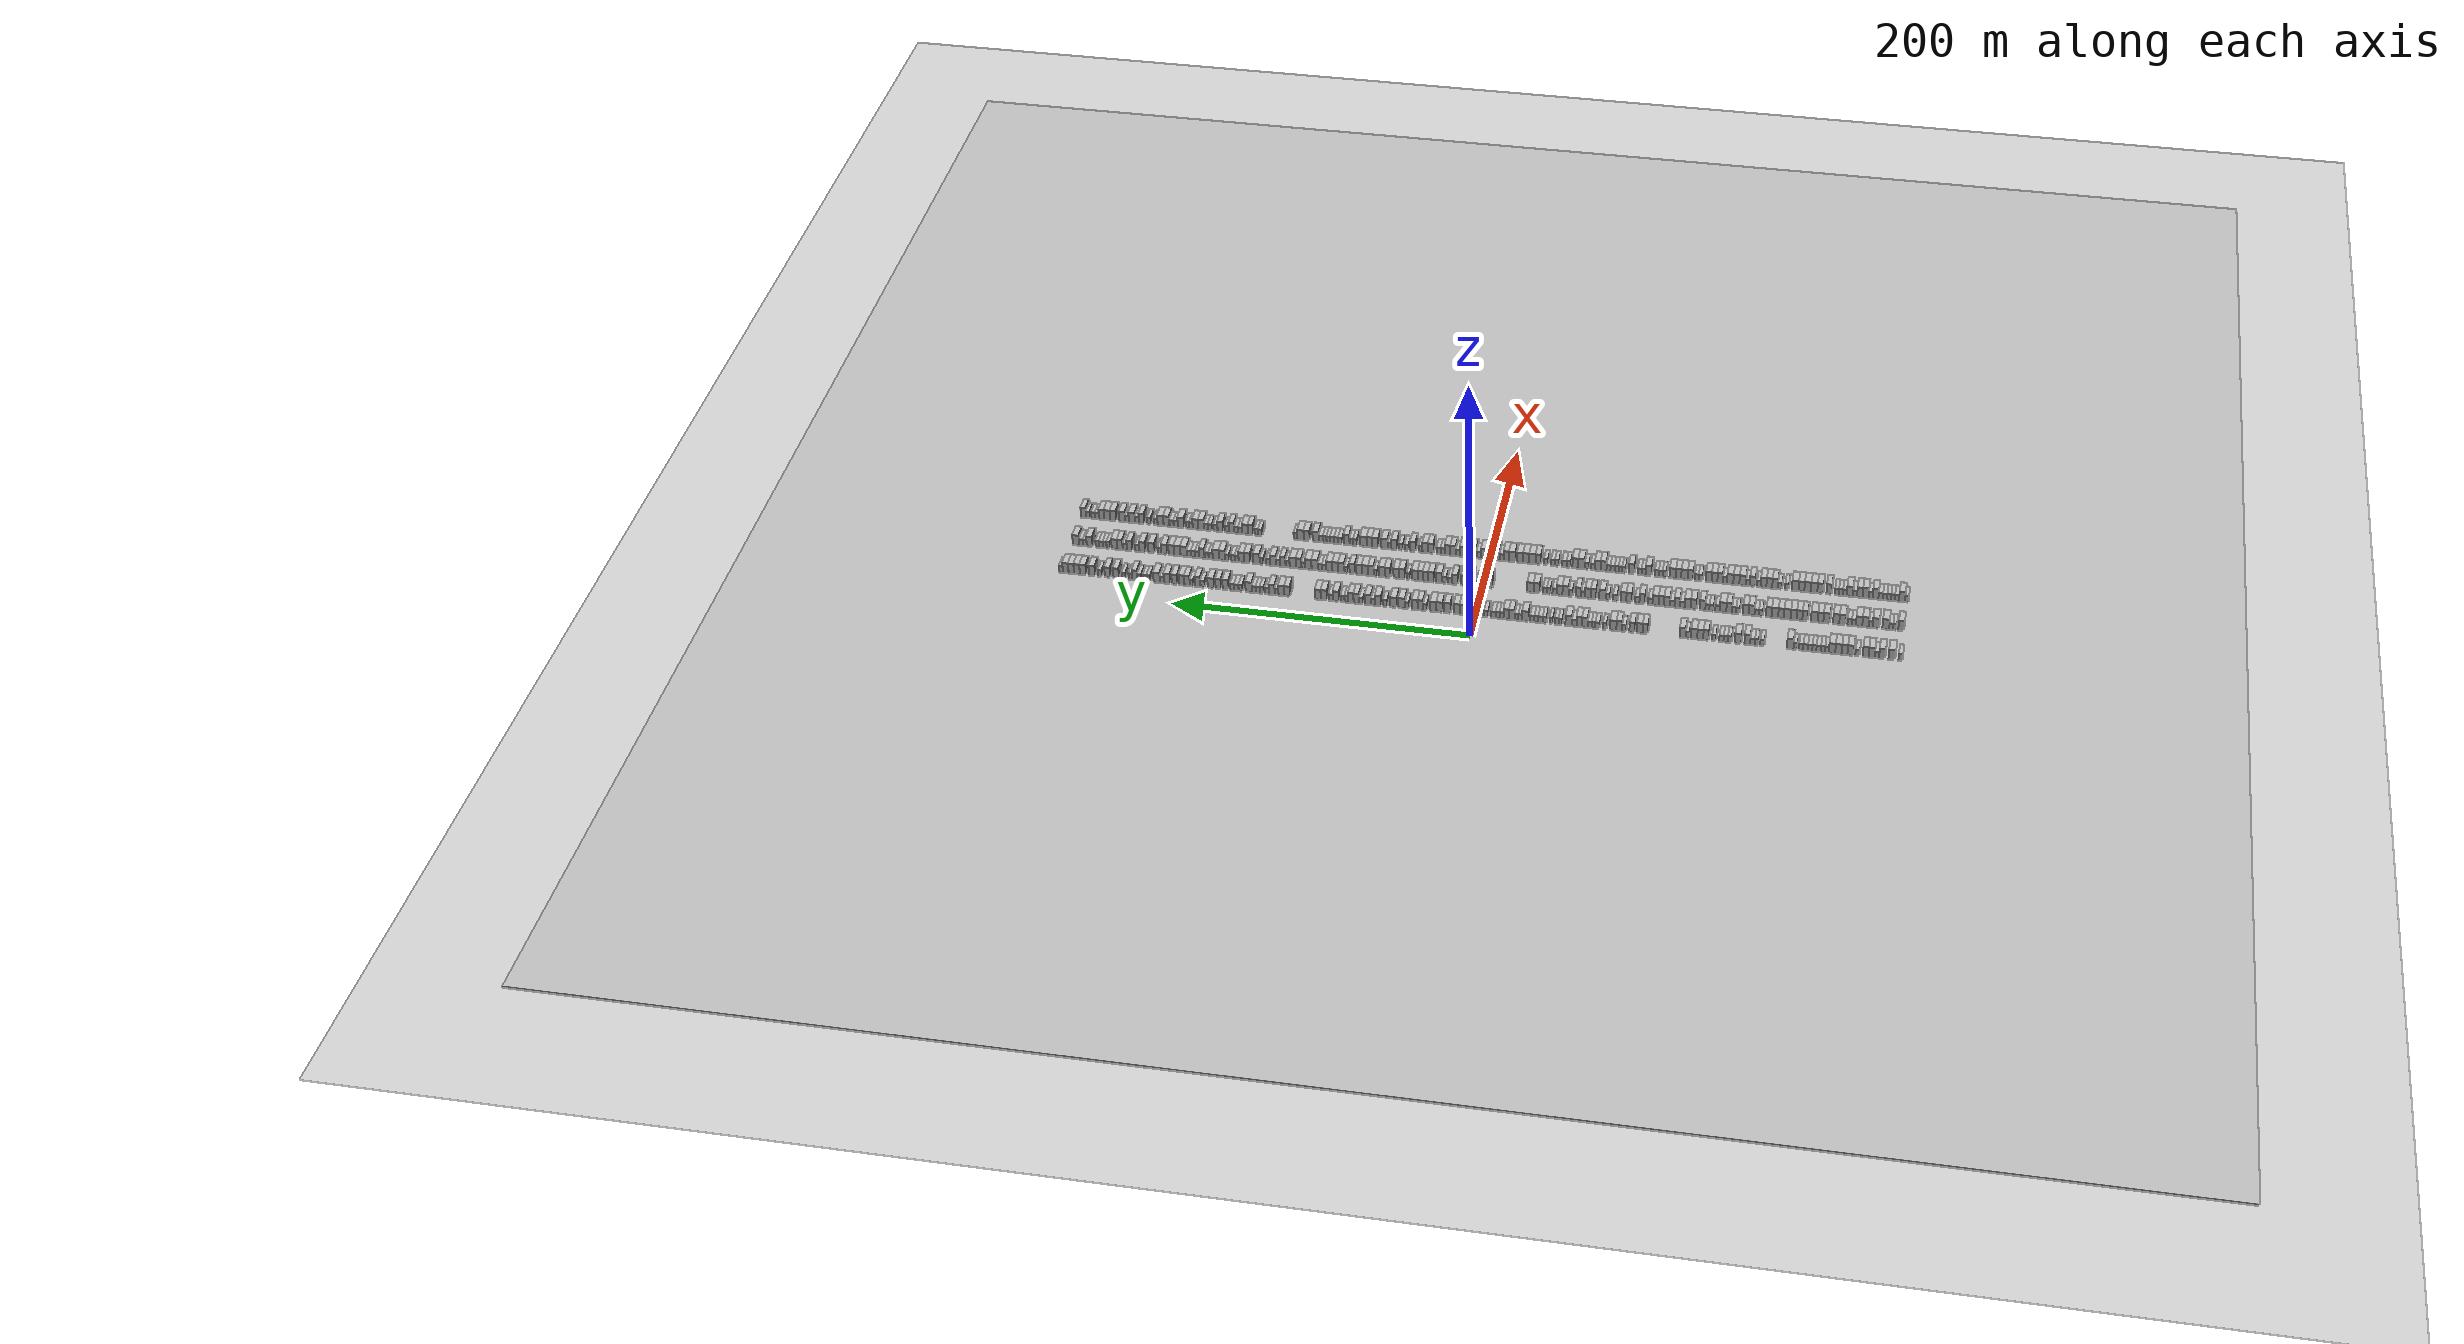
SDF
<?xml version="1.0" encoding="utf-8"?>

<sdf version="1.6">

   <world name="default">

      <gui fullscreen="0">

         <camera name="user_camera">

            <pose>-15 0 4.57585 0 0 0</pose>

            <view_controller>orbit</view_controller>

         </camera>

      </gui>

      <scene>

         <sky>

           <clouds>

             <speed>12</speed>

           </clouds>

         </sky>

         <ambient>0.4 0.4 0.4 1</ambient>

         <background>0.7 0.7 0.7 1</background>

         <shadows>1</shadows>

      </scene>

      <gravity>0 0 -9.8066</gravity>

      <magnetic_field>6e-06 2.3e-05 -4.2e-05</magnetic_field>

      <physics default="0" name="default_physics" type="ode">

         <ode>

            <solver>

               <type>quick</type>

               <iters>10</iters>

               <sor>1.0</sor>

               <use_dynamic_moi_rescaling>0</use_dynamic_moi_rescaling>

            </solver>

            <constraints>

               <cfm>0</cfm>

               <erp>0.2</erp>

               <contact_max_correcting_vel>100</contact_max_correcting_vel>

               <contact_surface_layer>0.001</contact_surface_layer>

            </constraints>

         </ode>

         <max_step_size>0.004</max_step_size>

         <real_time_factor>1</real_time_factor>

         <real_time_update_rate>250</real_time_update_rate>

      </physics>

      <light name="sun" type="directional">

         <cast_shadows>1</cast_shadows>

         <pose>0 0 10 0 0 0</pose>

         <diffuse>0.8 0.8 0.8 1</diffuse>

         <specular>0.2 0.2 0.2 1</specular>

         <attenuation>

            <range>1000</range>

            <constant>0.9</constant>

            <linear>0.01</linear>

            <quadratic>0.001</quadratic>

         </attenuation>

         <direction>-0.5 0.1 -0.9</direction>

      </light>

      <include>

         <name>ground_plane_1</name>

         <uri>model://HANNAS_ground_plane</uri>

         <pose>0 0 0  0 0 0</pose>

      </include>

      <include>

         <name>ground_plane_2</name>

         <uri>model://HANNAS_ground_plane</uri>

         <pose>100 0 0  0 0 0</pose>

      </include>

      <model name="building_1">

         <static>1</static>

         <pose frame="">25.0000 -278.6222 0 0.000000 0.000000 0.000000</pose>

         <link name="link">

            <pose frame="">0 0 3.00 0 0 0</pose>

            <collision name="collision">

               <geometry>

                  <box>

                     <size>10.0000 2.7555 6.0000</size>

                  </box>

               </geometry>

               <max_contacts>10</max_contacts>

               <surface>

                  <contact>

                     <ode/>

                  </contact>

                  <bounce/>

                  <friction>

                     <torsional>

                        <ode/>

                     </torsional>

                     <ode/>

                  </friction>

               </surface>

            </collision>

            <visual name="visual">

               <cast_shadows>0</cast_shadows>

               <geometry>

                  <box>

                     <size>10.0000 2.7555 6.0000</size>

                  </box>

               </geometry>

               <material>

                  <script>

                     <uri>model://HANNAS_wall/materials/scripts</uri>

                     <uri>model://HANNAS_wall/materials/textures</uri>

                     <name>vrc/HANNAS_wall</name>

                  </script>

               </material>

            </visual>

            <self_collide>0</self_collide>

            <enable_wind>0</enable_wind>

            <kinematic>0</kinematic>

         </link>

      </model>

      <model name="building_2">

         <static>1</static>

         <pose frame="">25.0000 -273.0113 0 0.000000 0.000000 0.000000</pose>

         <link name="link">

            <pose frame="">0 0 4.50 0 0 0</pose>

            <collision name="collision">

               <geometry>

                  <box>

                     <size>10.0000 4.4663 9.0000</size>

                  </box>

               </geometry>

               <max_contacts>10</max_contacts>

               <surface>

                  <contact>

                     <ode/>

                  </contact>

                  <bounce/>

                  <friction>

                     <torsional>

                        <ode/>

                     </torsional>

                     <ode/>

                  </friction>

               </surface>

            </collision>

            <visual name="visual">

               <cast_shadows>0</cast_shadows>

               <geometry>

                  <box>

                     <size>10.0000 4.4663 9.0000</size>

                  </box>

               </geometry>

               <material>

                  <script>

                     <uri>model://HANNAS_wall/materials/scripts</uri>

                     <uri>model://HANNAS_wall/materials/textures</uri>

                     <name>vrc/HANNAS_wall</name>

                  </script>

               </material>

            </visual>

            <self_collide>0</self_collide>

            <enable_wind>0</enable_wind>

            <kinematic>0</kinematic>

         </link>

      </model>

      <model name="building_3">

         <static>1</static>

         <pose frame="">25.0000 -266.7550 0 0.000000 0.000000 0.000000</pose>

         <link name="link">

            <pose frame="">0 0 4.50 0 0 0</pose>

            <collision name="collision">

               <geometry>

                  <box>

                     <size>10.0000 4.0464 9.0000</size>

                  </box>

               </geometry>

               <max_contacts>10</max_contacts>

               <surface>

                  <contact>

                     <ode/>

                  </contact>

                  <bounce/>

                  <friction>

                     <torsional>

                        <ode/>

                     </torsional>

                     <ode/>

                  </friction>

               </surface>

            </collision>

            <visual name="visual">

               <cast_shadows>0</cast_shadows>

               <geometry>

                  <box>

                     <size>10.0000 4.0464 9.0000</size>

                  </box>

               </geometry>

               <material>

                  <script>

                     <uri>model://HANNAS_wall/materials/scripts</uri>

                     <uri>model://HANNAS_wall/materials/textures</uri>

                     <name>vrc/HANNAS_wall</name>

                  </script>

               </material>

            </visual>

            <self_collide>0</self_collide>

            <enable_wind>0</enable_wind>

            <kinematic>0</kinematic>

         </link>

      </model>

      <model name="building_4">

         <static>1</static>

         <pose frame="">25.0000 -263.3125 0 0.000000 0.000000 0.000000</pose>

         <link name="link">

            <pose frame="">0 0 3.00 0 0 0</pose>

            <collision name="collision">

               <geometry>

                  <box>

                     <size>10.0000 2.8386 6.0000</size>

                  </box>

               </geometry>

               <max_contacts>10</max_contacts>

               <surface>

                  <contact>

                     <ode/>

                  </contact>

                  <bounce/>

                  <friction>

                     <torsional>

                        <ode/>

                     </torsional>

                     <ode/>

                  </friction>

               </surface>

            </collision>

            <visual name="visual">

               <cast_shadows>0</cast_shadows>

               <geometry>

                  <box>

                     <size>10.0000 2.8386 6.0000</size>

                  </box>

               </geometry>

               <material>

                  <script>

                     <uri>model://HANNAS_wall/materials/scripts</uri>

                     <uri>model://HANNAS_wall/materials/textures</uri>

                     <name>vrc/HANNAS_wall</name>

                  </script>

               </material>

            </visual>

            <self_collide>0</self_collide>

            <enable_wind>0</enable_wind>

            <kinematic>0</kinematic>

         </link>

      </model>

      <model name="building_5">

         <static>1</static>

         <pose frame="">25.0000 -259.9470 0 0.000000 0.000000 0.000000</pose>

         <link name="link">

            <pose frame="">0 0 4.50 0 0 0</pose>

            <collision name="collision">

               <geometry>

                  <box>

                     <size>10.0000 3.8923 9.0000</size>

                  </box>

               </geometry>

               <max_contacts>10</max_contacts>

               <surface>

                  <contact>

                     <ode/>

                  </contact>

                  <bounce/>

                  <friction>

                     <torsional>

                        <ode/>

                     </torsional>

                     <ode/>

                  </friction>

               </surface>

            </collision>

            <visual name="visual">

               <cast_shadows>0</cast_shadows>

               <geometry>

                  <box>

                     <size>10.0000 3.8923 9.0000</size>

                  </box>

               </geometry>

               <material>

                  <script>

                     <uri>model://HANNAS_wall/materials/scripts</uri>

                     <uri>model://HANNAS_wall/materials/textures</uri>

                     <name>vrc/HANNAS_wall</name>

                  </script>

               </material>

            </visual>

            <self_collide>0</self_collide>

            <enable_wind>0</enable_wind>

            <kinematic>0</kinematic>

         </link>

      </model>

      <model name="building_6">

         <static>1</static>

         <pose frame="">25.0000 -256.0884 0 0.000000 0.000000 0.000000</pose>

         <link name="link">

            <pose frame="">0 0 4.50 0 0 0</pose>

            <collision name="collision">

               <geometry>

                  <box>

                     <size>10.0000 3.8249 9.0000</size>

                  </box>

               </geometry>

               <max_contacts>10</max_contacts>

               <surface>

                  <contact>

                     <ode/>

                  </contact>

                  <bounce/>

                  <friction>

                     <torsional>

                        <ode/>

                     </torsional>

                     <ode/>

                  </friction>

               </surface>

            </collision>

            <visual name="visual">

               <cast_shadows>0</cast_shadows>

               <geometry>

                  <box>

                     <size>10.0000 3.8249 9.0000</size>

                  </box>

               </geometry>

               <material>

                  <script>

                     <uri>model://HANNAS_wall/materials/scripts</uri>

                     <uri>model://HANNAS_wall/materials/textures</uri>

                     <name>vrc/HANNAS_wall</name>

                  </script>

               </material>

            </visual>

            <self_collide>0</self_collide>

            <enable_wind>0</enable_wind>

            <kinematic>0</kinematic>

         </link>

      </model>

      <model name="building_7">

         <static>1</static>

         <pose frame="">25.0000 -250.7768 0 0.000000 0.000000 0.000000</pose>

         <link name="link">

            <pose frame="">0 0 3.00 0 0 0</pose>

            <collision name="collision">

               <geometry>

                  <box>

                     <size>10.0000 2.7984 6.0000</size>

                  </box>

               </geometry>

               <max_contacts>10</max_contacts>

               <surface>

                  <contact>

                     <ode/>

                  </contact>

                  <bounce/>

                  <friction>

                     <torsional>

                        <ode/>

                     </torsional>

                     <ode/>

                  </friction>

               </surface>

            </collision>

            <visual name="visual">

               <cast_shadows>0</cast_shadows>

               <geometry>

                  <box>

                     <size>10.0000 2.7984 6.0000</size>

                  </box>

               </geometry>

               <material>

                  <script>

                     <uri>model://HANNAS_wall/materials/scripts</uri>

                     <uri>model://HANNAS_wall/materials/textures</uri>

                     <name>vrc/HANNAS_wall</name>

                  </script>

               </material>

            </visual>

            <self_collide>0</self_collide>

            <enable_wind>0</enable_wind>

            <kinematic>0</kinematic>

         </link>

      </model>

      <model name="building_8">

         <static>1</static>

         <pose frame="">25.0000 -246.3185 0 0.000000 0.000000 0.000000</pose>

         <link name="link">

            <pose frame="">0 0 4.50 0 0 0</pose>

            <collision name="collision">

               <geometry>

                  <box>

                     <size>10.0000 4.1181 9.0000</size>

                  </box>

               </geometry>

               <max_contacts>10</max_contacts>

               <surface>

                  <contact>

                     <ode/>

                  </contact>

                  <bounce/>

                  <friction>

                     <torsional>

                        <ode/>

                     </torsional>

                     <ode/>

                  </friction>

               </surface>

            </collision>

            <visual name="visual">

               <cast_shadows>0</cast_shadows>

               <geometry>

                  <box>

                     <size>10.0000 4.1181 9.0000</size>

                  </box>

               </geometry>

               <material>

                  <script>

                     <uri>model://HANNAS_wall/materials/scripts</uri>

                     <uri>model://HANNAS_wall/materials/textures</uri>

                     <name>vrc/HANNAS_wall</name>

                  </script>

               </material>

            </visual>

            <self_collide>0</self_collide>

            <enable_wind>0</enable_wind>

            <kinematic>0</kinematic>

         </link>

      </model>

      <model name="building_9">

         <static>1</static>

         <pose frame="">25.0000 -242.3874 0 0.000000 0.000000 0.000000</pose>

         <link name="link">

            <pose frame="">0 0 4.50 0 0 0</pose>

            <collision name="collision">

               <geometry>

                  <box>

                     <size>10.0000 3.7442 9.0000</size>

                  </box>

               </geometry>

               <max_contacts>10</max_contacts>

               <surface>

                  <contact>

                     <ode/>

                  </contact>

                  <bounce/>

                  <friction>

                     <torsional>

                        <ode/>

                     </torsional>

                     <ode/>

                  </friction>

               </surface>

            </collision>

            <visual name="visual">

               <cast_shadows>0</cast_shadows>

               <geometry>

                  <box>

                     <size>10.0000 3.7442 9.0000</size>

                  </box>

               </geometry>

               <material>

                  <script>

                     <uri>model://HANNAS_wall/materials/scripts</uri>

                     <uri>model://HANNAS_wall/materials/textures</uri>

                     <name>vrc/HANNAS_wall</name>

                  </script>

               </material>

            </visual>

            <self_collide>0</self_collide>

            <enable_wind>0</enable_wind>

            <kinematic>0</kinematic>

         </link>

      </model>

      <model name="building_10">

         <static>1</static>

         <pose frame="">25.0000 -238.4090 0 0.000000 0.000000 0.000000</pose>

         <link name="link">

            <pose frame="">0 0 4.50 0 0 0</pose>

            <collision name="collision">

               <geometry>

                  <box>

                     <size>10.0000 4.2125 9.0000</size>

                  </box>

               </geometry>

               <max_contacts>10</max_contacts>

               <surface>

                  <contact>

                     <ode/>

                  </contact>

                  <bounce/>

                  <friction>

                     <torsional>

                        <ode/>

                     </torsional>

                     <ode/>

                  </friction>

               </surface>

            </collision>

            <visual name="visual">

               <cast_shadows>0</cast_shadows>

               <geometry>

                  <box>

                     <size>10.0000 4.2125 9.0000</size>

                  </box>

               </geometry>

               <material>

                  <script>

                     <uri>model://HANNAS_wall/materials/scripts</uri>

                     <uri>model://HANNAS_wall/materials/textures</uri>

                     <name>vrc/HANNAS_wall</name>

                  </script>

               </material>

            </visual>

            <self_collide>0</self_collide>

            <enable_wind>0</enable_wind>

            <kinematic>0</kinematic>

         </link>

      </model>

      <model name="building_11">

         <static>1</static>

         <pose frame="">25.0000 -234.2568 0 0.000000 0.000000 0.000000</pose>

         <link name="link">

            <pose frame="">0 0 4.50 0 0 0</pose>

            <collision name="collision">

               <geometry>

                  <box>

                     <size>10.0000 4.0920 9.0000</size>

                  </box>

               </geometry>

               <max_contacts>10</max_contacts>

               <surface>

                  <contact>

                     <ode/>

                  </contact>

                  <bounce/>

                  <friction>

                     <torsional>

                        <ode/>

                     </torsional>

                     <ode/>

                  </friction>

               </surface>

            </collision>

            <visual name="visual">

               <cast_shadows>0</cast_shadows>

               <geometry>

                  <box>

                     <size>10.0000 4.0920 9.0000</size>

                  </box>

               </geometry>

               <material>

                  <script>

                     <uri>model://HANNAS_wall/materials/scripts</uri>

                     <uri>model://HANNAS_wall/materials/textures</uri>

                     <name>vrc/HANNAS_wall</name>

                  </script>

               </material>

            </visual>

            <self_collide>0</self_collide>

            <enable_wind>0</enable_wind>

            <kinematic>0</kinematic>

         </link>

      </model>

      <model name="building_12">

         <static>1</static>

         <pose frame="">25.0000 -230.9868 0 0.000000 0.000000 0.000000</pose>

         <link name="link">

            <pose frame="">0 0 3.00 0 0 0</pose>

            <collision name="collision">

               <geometry>

                  <box>

                     <size>10.0000 2.4479 6.0000</size>

                  </box>

               </geometry>

               <max_contacts>10</max_contacts>

               <surface>

                  <contact>

                     <ode/>

                  </contact>

                  <bounce/>

                  <friction>

                     <torsional>

                        <ode/>

                     </torsional>

                     <ode/>

                  </friction>

               </surface>

            </collision>

            <visual name="visual">

               <cast_shadows>0</cast_shadows>

               <geometry>

                  <box>

                     <size>10.0000 2.4479 6.0000</size>

                  </box>

               </geometry>

               <material>

                  <script>

                     <uri>model://HANNAS_wall/materials/scripts</uri>

                     <uri>model://HANNAS_wall/materials/textures</uri>

                     <name>vrc/HANNAS_wall</name>

                  </script>

               </material>

            </visual>

            <self_collide>0</self_collide>

            <enable_wind>0</enable_wind>

            <kinematic>0</kinematic>

         </link>

      </model>

      <model name="building_13">

         <static>1</static>

         <pose frame="">25.0000 -228.3718 0 0.000000 0.000000 0.000000</pose>

         <link name="link">

            <pose frame="">0 0 3.00 0 0 0</pose>

            <collision name="collision">

               <geometry>

                  <box>

                     <size>10.0000 2.7821 6.0000</size>

                  </box>

               </geometry>

               <max_contacts>10</max_contacts>

               <surface>

                  <contact>

                     <ode/>

                  </contact>

                  <bounce/>

                  <friction>

                     <torsional>

                        <ode/>

                     </torsional>

                     <ode/>

                  </friction>

               </surface>

            </collision>

            <visual name="visual">

               <cast_shadows>0</cast_shadows>

               <geometry>

                  <box>

                     <size>10.0000 2.7821 6.0000</size>

                  </box>

               </geometry>

               <material>

                  <script>

                     <uri>model://HANNAS_wall/materials/scripts</uri>

                     <uri>model://HANNAS_wall/materials/textures</uri>

                     <name>vrc/HANNAS_wall</name>

                  </script>

               </material>

            </visual>

            <self_collide>0</self_collide>

            <enable_wind>0</enable_wind>

            <kinematic>0</kinematic>

         </link>

      </model>

      <model name="building_14">

         <static>1</static>

         <pose frame="">25.0000 -225.5169 0 0.000000 0.000000 0.000000</pose>

         <link name="link">

            <pose frame="">0 0 3.00 0 0 0</pose>

            <collision name="collision">

               <geometry>

                  <box>

                     <size>10.0000 2.9276 6.0000</size>

                  </box>

               </geometry>

               <max_contacts>10</max_contacts>

               <surface>

                  <contact>

                     <ode/>

                  </contact>

                  <bounce/>

                  <friction>

                     <torsional>

                        <ode/>

                     </torsional>

                     <ode/>

                  </friction>

               </surface>

            </collision>

            <visual name="visual">

               <cast_shadows>0</cast_shadows>

               <geometry>

                  <box>

                     <size>10.0000 2.9276 6.0000</size>

                  </box>

               </geometry>

               <material>

                  <script>

                     <uri>model://HANNAS_wall/materials/scripts</uri>

                     <uri>model://HANNAS_wall/materials/textures</uri>

                     <name>vrc/HANNAS_wall</name>

                  </script>

               </material>

            </visual>

            <self_collide>0</self_collide>

            <enable_wind>0</enable_wind>

            <kinematic>0</kinematic>

         </link>

      </model>

      <model name="building_15">

         <static>1</static>

         <pose frame="">25.0000 -222.7389 0 0.000000 0.000000 0.000000</pose>

         <link name="link">

            <pose frame="">0 0 3.00 0 0 0</pose>

            <collision name="collision">

               <geometry>

                  <box>

                     <size>10.0000 2.6284 6.0000</size>

                  </box>

               </geometry>

               <max_contacts>10</max_contacts>

               <surface>

                  <contact>

                     <ode/>

                  </contact>

                  <bounce/>

                  <friction>

                     <torsional>

                        <ode/>

                     </torsional>

                     <ode/>

                  </friction>

               </surface>

            </collision>

            <visual name="visual">

               <cast_shadows>0</cast_shadows>

               <geometry>

                  <box>

                     <size>10.0000 2.6284 6.0000</size>

                  </box>

               </geometry>

               <material>

                  <script>

                     <uri>model://HANNAS_wall/materials/scripts</uri>

                     <uri>model://HANNAS_wall/materials/textures</uri>

                     <name>vrc/HANNAS_wall</name>

                  </script>

               </material>

            </visual>

            <self_collide>0</self_collide>

            <enable_wind>0</enable_wind>

            <kinematic>0</kinematic>

         </link>

      </model>

      <model name="building_16">

         <static>1</static>

         <pose frame="">25.0000 -219.9578 0 0.000000 0.000000 0.000000</pose>

         <link name="link">

            <pose frame="">0 0 3.00 0 0 0</pose>

            <collision name="collision">

               <geometry>

                  <box>

                     <size>10.0000 2.9339 6.0000</size>

                  </box>

               </geometry>

               <max_contacts>10</max_contacts>

               <surface>

                  <contact>

                     <ode/>

                  </contact>

                  <bounce/>

                  <friction>

                     <torsional>

                        <ode/>

                     </torsional>

                     <ode/>

                  </friction>

               </surface>

            </collision>

            <visual name="visual">

               <cast_shadows>0</cast_shadows>

               <geometry>

                  <box>

                     <size>10.0000 2.9339 6.0000</size>

                  </box>

               </geometry>

               <material>

                  <script>

                     <uri>model://HANNAS_wall/materials/scripts</uri>

                     <uri>model://HANNAS_wall/materials/textures</uri>

                     <name>vrc/HANNAS_wall</name>

                  </script>

               </material>

            </visual>

            <self_collide>0</self_collide>

            <enable_wind>0</enable_wind>

            <kinematic>0</kinematic>

         </link>

      </model>

      <model name="building_17">

         <static>1</static>

         <pose frame="">25.0000 -217.0047 0 0.000000 0.000000 0.000000</pose>

         <link name="link">

            <pose frame="">0 0 3.00 0 0 0</pose>

            <collision name="collision">

               <geometry>

                  <box>

                     <size>10.0000 2.9721 6.0000</size>

                  </box>

               </geometry>

               <max_contacts>10</max_contacts>

               <surface>

                  <contact>

                     <ode/>

                  </contact>

                  <bounce/>

                  <friction>

                     <torsional>

                        <ode/>

                     </torsional>

                     <ode/>

                  </friction>

               </surface>

            </collision>

            <visual name="visual">

               <cast_shadows>0</cast_shadows>

               <geometry>

                  <box>

                     <size>10.0000 2.9721 6.0000</size>

                  </box>

               </geometry>

               <material>

                  <script>

                     <uri>model://HANNAS_wall/materials/scripts</uri>

                     <uri>model://HANNAS_wall/materials/textures</uri>

                     <name>vrc/HANNAS_wall</name>

                  </script>

               </material>

            </visual>

            <self_collide>0</self_collide>

            <enable_wind>0</enable_wind>

            <kinematic>0</kinematic>

         </link>

      </model>

      <model name="building_18">

         <static>1</static>

         <pose frame="">25.0000 -214.1346 0 0.000000 0.000000 0.000000</pose>

         <link name="link">

            <pose frame="">0 0 3.00 0 0 0</pose>

            <collision name="collision">

               <geometry>

                  <box>

                     <size>10.0000 2.7681 6.0000</size>

                  </box>

               </geometry>

               <max_contacts>10</max_contacts>

               <surface>

                  <contact>

                     <ode/>

                  </contact>

                  <bounce/>

                  <friction>

                     <torsional>

                        <ode/>

                     </torsional>

                     <ode/>

                  </friction>

               </surface>

            </collision>

            <visual name="visual">

               <cast_shadows>0</cast_shadows>

               <geometry>

                  <box>

                     <size>10.0000 2.7681 6.0000</size>

                  </box>

               </geometry>

               <material>

                  <script>

                     <uri>model://HANNAS_wall/materials/scripts</uri>

                     <uri>model://HANNAS_wall/materials/textures</uri>

                     <name>vrc/HANNAS_wall</name>

                  </script>

               </material>

            </visual>

            <self_collide>0</self_collide>

            <enable_wind>0</enable_wind>

            <kinematic>0</kinematic>

         </link>

      </model>

      <model name="building_19">

         <static>1</static>

         <pose frame="">25.0000 -210.4780 0 0.000000 0.000000 0.000000</pose>

         <link name="link">

            <pose frame="">0 0 3.00 0 0 0</pose>

            <collision name="collision">

               <geometry>

                  <box>

                     <size>10.0000 2.5453 6.0000</size>

                  </box>

               </geometry>

               <max_contacts>10</max_contacts>

               <surface>

                  <contact>

                     <ode/>

                  </contact>

                  <bounce/>

                  <friction>

                     <torsional>

                        <ode/>

                     </torsional>

                     <ode/>

                  </friction>

               </surface>

            </collision>

            <visual name="visual">

               <cast_shadows>0</cast_shadows>

               <geometry>

                  <box>

                     <size>10.0000 2.5453 6.0000</size>

                  </box>

               </geometry>

               <material>

                  <script>

                     <uri>model://HANNAS_wall/materials/scripts</uri>

                     <uri>model://HANNAS_wall/materials/textures</uri>

                     <name>vrc/HANNAS_wall</name>

                  </script>

               </material>

            </visual>

            <self_collide>0</self_collide>

            <enable_wind>0</enable_wind>

            <kinematic>0</kinematic>

         </link>

      </model>

      <model name="building_20">

         <static>1</static>

         <pose frame="">25.0000 -207.0860 0 0.000000 0.000000 0.000000</pose>

         <link name="link">

            <pose frame="">0 0 4.50 0 0 0</pose>

            <collision name="collision">

               <geometry>

                  <box>

                     <size>10.0000 4.2386 9.0000</size>

                  </box>

               </geometry>

               <max_contacts>10</max_contacts>

               <surface>

                  <contact>

                     <ode/>

                  </contact>

                  <bounce/>

                  <friction>

                     <torsional>

                        <ode/>

                     </torsional>

                     <ode/>

                  </friction>

               </surface>

            </collision>

            <visual name="visual">

               <cast_shadows>0</cast_shadows>

               <geometry>

                  <box>

                     <size>10.0000 4.2386 9.0000</size>

                  </box>

               </geometry>

               <material>

                  <script>

                     <uri>model://HANNAS_wall/materials/scripts</uri>

                     <uri>model://HANNAS_wall/materials/textures</uri>

                     <name>vrc/HANNAS_wall</name>

                  </script>

               </material>

            </visual>

            <self_collide>0</self_collide>

            <enable_wind>0</enable_wind>

            <kinematic>0</kinematic>

         </link>

      </model>

      <model name="building_21">

         <static>1</static>

         <pose frame="">25.0000 -188.9353 0 0.000000 0.000000 0.000000</pose>

         <link name="link">

            <pose frame="">0 0 3.00 0 0 0</pose>

            <collision name="collision">

               <geometry>

                  <box>

                     <size>10.0000 2.6876 6.0000</size>

                  </box>

               </geometry>

               <max_contacts>10</max_contacts>

               <surface>

                  <contact>

                     <ode/>

                  </contact>

                  <bounce/>

                  <friction>

                     <torsional>

                        <ode/>

                     </torsional>

                     <ode/>

                  </friction>

               </surface>

            </collision>

            <visual name="visual">

               <cast_shadows>0</cast_shadows>

               <geometry>

                  <box>

                     <size>10.0000 2.6876 6.0000</size>

                  </box>

               </geometry>

               <material>

                  <script>

                     <uri>model://HANNAS_wall/materials/scripts</uri>

                     <uri>model://HANNAS_wall/materials/textures</uri>

                     <name>vrc/HANNAS_wall</name>

                  </script>

               </material>

            </visual>

            <self_collide>0</self_collide>

            <enable_wind>0</enable_wind>

            <kinematic>0</kinematic>

         </link>

      </model>

      <model name="building_22">

         <static>1</static>

         <pose frame="">25.0000 -185.2902 0 0.000000 0.000000 0.000000</pose>

         <link name="link">

            <pose frame="">0 0 3.00 0 0 0</pose>

            <collision name="collision">

               <geometry>

                  <box>

                     <size>10.0000 2.6028 6.0000</size>

                  </box>

               </geometry>

               <max_contacts>10</max_contacts>

               <surface>

                  <contact>

                     <ode/>

                  </contact>

                  <bounce/>

                  <friction>

                     <torsional>

                        <ode/>

                     </torsional>

                     <ode/>

                  </friction>

               </surface>

            </collision>

            <visual name="visual">

               <cast_shadows>0</cast_shadows>

               <geometry>

                  <box>

                     <size>10.0000 2.6028 6.0000</size>

                  </box>

               </geometry>

               <material>

                  <script>

                     <uri>model://HANNAS_wall/materials/scripts</uri>

                     <uri>model://HANNAS_wall/materials/textures</uri>

                     <name>vrc/HANNAS_wall</name>

                  </script>

               </material>

            </visual>

            <self_collide>0</self_collide>

            <enable_wind>0</enable_wind>

            <kinematic>0</kinematic>

         </link>

      </model>

      <model name="building_23">

         <static>1</static>

         <pose frame="">25.0000 -182.5065 0 0.000000 0.000000 0.000000</pose>

         <link name="link">

            <pose frame="">0 0 3.00 0 0 0</pose>

            <collision name="collision">

               <geometry>

                  <box>

                     <size>10.0000 2.9645 6.0000</size>

                  </box>

               </geometry>

               <max_contacts>10</max_contacts>

               <surface>

                  <contact>

                     <ode/>

                  </contact>

                  <bounce/>

                  <friction>

                     <torsional>

                        <ode/>

                     </torsional>

                     <ode/>

                  </friction>

               </surface>

            </collision>

            <visual name="visual">

               <cast_shadows>0</cast_shadows>

               <geometry>

                  <box>

                     <size>10.0000 2.9645 6.0000</size>

                  </box>

               </geometry>

               <material>

                  <script>

                     <uri>model://HANNAS_wall/materials/scripts</uri>

                     <uri>model://HANNAS_wall/materials/textures</uri>

                     <name>vrc/HANNAS_wall</name>

                  </script>

               </material>

            </visual>

            <self_collide>0</self_collide>

            <enable_wind>0</enable_wind>

            <kinematic>0</kinematic>

         </link>

      </model>

      <model name="building_24">

         <static>1</static>

         <pose frame="">25.0000 -179.1272 0 0.000000 0.000000 0.000000</pose>

         <link name="link">

            <pose frame="">0 0 4.50 0 0 0</pose>

            <collision name="collision">

               <geometry>

                  <box>

                     <size>10.0000 3.7940 9.0000</size>

                  </box>

               </geometry>

               <max_contacts>10</max_contacts>

               <surface>

                  <contact>

                     <ode/>

                  </contact>

                  <bounce/>

                  <friction>

                     <torsional>

                        <ode/>

                     </torsional>

                     <ode/>

                  </friction>

               </surface>

            </collision>

            <visual name="visual">

               <cast_shadows>0</cast_shadows>

               <geometry>

                  <box>

                     <size>10.0000 3.7940 9.0000</size>

                  </box>

               </geometry>

               <material>

                  <script>

                     <uri>model://HANNAS_wall/materials/scripts</uri>

                     <uri>model://HANNAS_wall/materials/textures</uri>

                     <name>vrc/HANNAS_wall</name>

                  </script>

               </material>

            </visual>

            <self_collide>0</self_collide>

            <enable_wind>0</enable_wind>

            <kinematic>0</kinematic>

         </link>

      </model>

      <model name="building_25">

         <static>1</static>

         <pose frame="">25.0000 -173.0870 0 0.000000 0.000000 0.000000</pose>

         <link name="link">

            <pose frame="">0 0 4.50 0 0 0</pose>

            <collision name="collision">

               <geometry>

                  <box>

                     <size>10.0000 4.2864 9.0000</size>

                  </box>

               </geometry>

               <max_contacts>10</max_contacts>

               <surface>

                  <contact>

                     <ode/>

                  </contact>

                  <bounce/>

                  <friction>

                     <torsional>

                        <ode/>

                     </torsional>

                     <ode/>

                  </friction>

               </surface>

            </collision>

            <visual name="visual">

               <cast_shadows>0</cast_shadows>

               <geometry>

                  <box>

                     <size>10.0000 4.2864 9.0000</size>

                  </box>

               </geometry>

               <material>

                  <script>

                     <uri>model://HANNAS_wall/materials/scripts</uri>

                     <uri>model://HANNAS_wall/materials/textures</uri>

                     <name>vrc/HANNAS_wall</name>

                  </script>

               </material>

            </visual>

            <self_collide>0</self_collide>

            <enable_wind>0</enable_wind>

            <kinematic>0</kinematic>

         </link>

      </model>

      <model name="building_26">

         <static>1</static>

         <pose frame="">25.0000 -167.6536 0 0.000000 0.000000 0.000000</pose>

         <link name="link">

            <pose frame="">0 0 3.00 0 0 0</pose>

            <collision name="collision">

               <geometry>

                  <box>

                     <size>10.0000 2.5802 6.0000</size>

                  </box>

               </geometry>

               <max_contacts>10</max_contacts>

               <surface>

                  <contact>

                     <ode/>

                  </contact>

                  <bounce/>

                  <friction>

                     <torsional>

                        <ode/>

                     </torsional>

                     <ode/>

                  </friction>

               </surface>

            </collision>

            <visual name="visual">

               <cast_shadows>0</cast_shadows>

               <geometry>

                  <box>

                     <size>10.0000 2.5802 6.0000</size>

                  </box>

               </geometry>

               <material>

                  <script>

                     <uri>model://HANNAS_wall/materials/scripts</uri>

                     <uri>model://HANNAS_wall/materials/textures</uri>

                     <name>vrc/HANNAS_wall</name>

                  </script>

               </material>

            </visual>

            <self_collide>0</self_collide>

            <enable_wind>0</enable_wind>

            <kinematic>0</kinematic>

         </link>

      </model>

      <model name="building_27">

         <static>1</static>

         <pose frame="">25.0000 -164.9563 0 0.000000 0.000000 0.000000</pose>

         <link name="link">

            <pose frame="">0 0 3.00 0 0 0</pose>

            <collision name="collision">

               <geometry>

                  <box>

                     <size>10.0000 2.8145 6.0000</size>

                  </box>

               </geometry>

               <max_contacts>10</max_contacts>

               <surface>

                  <contact>

                     <ode/>

                  </contact>

                  <bounce/>

                  <friction>

                     <torsional>

                        <ode/>

                     </torsional>

                     <ode/>

                  </friction>

               </surface>

            </collision>

            <visual name="visual">

               <cast_shadows>0</cast_shadows>

               <geometry>

                  <box>

                     <size>10.0000 2.8145 6.0000</size>

                  </box>

               </geometry>

               <material>

                  <script>

                     <uri>model://HANNAS_wall/materials/scripts</uri>

                     <uri>model://HANNAS_wall/materials/textures</uri>

                     <name>vrc/HANNAS_wall</name>

                  </script>

               </material>

            </visual>

            <self_collide>0</self_collide>

            <enable_wind>0</enable_wind>

            <kinematic>0</kinematic>

         </link>

      </model>

      <model name="building_28">

         <static>1</static>

         <pose frame="">25.0000 -162.1720 0 0.000000 0.000000 0.000000</pose>

         <link name="link">

            <pose frame="">0 0 3.00 0 0 0</pose>

            <collision name="collision">

               <geometry>

                  <box>

                     <size>10.0000 2.7541 6.0000</size>

                  </box>

               </geometry>

               <max_contacts>10</max_contacts>

               <surface>

                  <contact>

                     <ode/>

                  </contact>

                  <bounce/>

                  <friction>

                     <torsional>

                        <ode/>

                     </torsional>

                     <ode/>

                  </friction>

               </surface>

            </collision>

            <visual name="visual">

               <cast_shadows>0</cast_shadows>

               <geometry>

                  <box>

                     <size>10.0000 2.7541 6.0000</size>

                  </box>

               </geometry>

               <material>

                  <script>

                     <uri>model://HANNAS_wall/materials/scripts</uri>

                     <uri>model://HANNAS_wall/materials/textures</uri>

                     <name>vrc/HANNAS_wall</name>

                  </script>

               </material>

            </visual>

            <self_collide>0</self_collide>

            <enable_wind>0</enable_wind>

            <kinematic>0</kinematic>

         </link>

      </model>

      <model name="building_29">

         <static>1</static>

         <pose frame="">25.0000 -157.4146 0 0.000000 0.000000 0.000000</pose>

         <link name="link">

            <pose frame="">0 0 3.00 0 0 0</pose>

            <collision name="collision">

               <geometry>

                  <box>

                     <size>10.0000 2.7607 6.0000</size>

                  </box>

               </geometry>

               <max_contacts>10</max_contacts>

               <surface>

                  <contact>

                     <ode/>

                  </contact>

                  <bounce/>

                  <friction>

                     <torsional>

                        <ode/>

                     </torsional>

                     <ode/>

                  </friction>

               </surface>

            </collision>

            <visual name="visual">

               <cast_shadows>0</cast_shadows>

               <geometry>

                  <box>

                     <size>10.0000 2.7607 6.0000</size>

                  </box>

               </geometry>

               <material>

                  <script>

                     <uri>model://HANNAS_wall/materials/scripts</uri>

                     <uri>model://HANNAS_wall/materials/textures</uri>

                     <name>vrc/HANNAS_wall</name>

                  </script>

               </material>

            </visual>

            <self_collide>0</self_collide>

            <enable_wind>0</enable_wind>

            <kinematic>0</kinematic>

         </link>

      </model>

      <model name="building_30">

         <static>1</static>

         <pose frame="">25.0000 -152.1574 0 0.000000 0.000000 0.000000</pose>

         <link name="link">

            <pose frame="">0 0 4.50 0 0 0</pose>

            <collision name="collision">

               <geometry>

                  <box>

                     <size>10.0000 3.7537 9.0000</size>

                  </box>

               </geometry>

               <max_contacts>10</max_contacts>

               <surface>

                  <contact>

                     <ode/>

                  </contact>

                  <bounce/>

                  <friction>

                     <torsional>

                        <ode/>

                     </torsional>

                     <ode/>

                  </friction>

               </surface>

            </collision>

            <visual name="visual">

               <cast_shadows>0</cast_shadows>

               <geometry>

                  <box>

                     <size>10.0000 3.7537 9.0000</size>

                  </box>

               </geometry>

               <material>

                  <script>

                     <uri>model://HANNAS_wall/materials/scripts</uri>

                     <uri>model://HANNAS_wall/materials/textures</uri>

                     <name>vrc/HANNAS_wall</name>

                  </script>

               </material>

            </visual>

            <self_collide>0</self_collide>

            <enable_wind>0</enable_wind>

            <kinematic>0</kinematic>

         </link>

      </model>

      <model name="building_31">

         <static>1</static>

         <pose frame="">25.0000 -148.3324 0 0.000000 0.000000 0.000000</pose>

         <link name="link">

            <pose frame="">0 0 4.50 0 0 0</pose>

            <collision name="collision">

               <geometry>

                  <box>

                     <size>10.0000 3.8961 9.0000</size>

                  </box>

               </geometry>

               <max_contacts>10</max_contacts>

               <surface>

                  <contact>

                     <ode/>

                  </contact>

                  <bounce/>

                  <friction>

                     <torsional>

                        <ode/>

                     </torsional>

                     <ode/>

                  </friction>

               </surface>

            </collision>

            <visual name="visual">

               <cast_shadows>0</cast_shadows>

               <geometry>

                  <box>

                     <size>10.0000 3.8961 9.0000</size>

                  </box>

               </geometry>

               <material>

                  <script>

                     <uri>model://HANNAS_wall/materials/scripts</uri>

                     <uri>model://HANNAS_wall/materials/textures</uri>

                     <name>vrc/HANNAS_wall</name>

                  </script>

               </material>

            </visual>

            <self_collide>0</self_collide>

            <enable_wind>0</enable_wind>

            <kinematic>0</kinematic>

         </link>

      </model>

      <model name="building_32">

         <static>1</static>

         <pose frame="">25.0000 -144.3460 0 0.000000 0.000000 0.000000</pose>

         <link name="link">

            <pose frame="">0 0 4.50 0 0 0</pose>

            <collision name="collision">

               <geometry>

                  <box>

                     <size>10.0000 4.0767 9.0000</size>

                  </box>

               </geometry>

               <max_contacts>10</max_contacts>

               <surface>

                  <contact>

                     <ode/>

                  </contact>

                  <bounce/>

                  <friction>

                     <torsional>

                        <ode/>

                     </torsional>

                     <ode/>

                  </friction>

               </surface>

            </collision>

            <visual name="visual">

               <cast_shadows>0</cast_shadows>

               <geometry>

                  <box>

                     <size>10.0000 4.0767 9.0000</size>

                  </box>

               </geometry>

               <material>

                  <script>

                     <uri>model://HANNAS_wall/materials/scripts</uri>

                     <uri>model://HANNAS_wall/materials/textures</uri>

                     <name>vrc/HANNAS_wall</name>

                  </script>

               </material>

            </visual>

            <self_collide>0</self_collide>

            <enable_wind>0</enable_wind>

            <kinematic>0</kinematic>

         </link>

      </model>

      <model name="building_33">

         <static>1</static>

         <pose frame="">25.0000 -140.0438 0 0.000000 0.000000 0.000000</pose>

         <link name="link">

            <pose frame="">0 0 3.00 0 0 0</pose>

            <collision name="collision">

               <geometry>

                  <box>

                     <size>10.0000 2.5278 6.0000</size>

                  </box>

               </geometry>

               <max_contacts>10</max_contacts>

               <surface>

                  <contact>

                     <ode/>

                  </contact>

                  <bounce/>

                  <friction>

                     <torsional>

                        <ode/>

                     </torsional>

                     <ode/>

                  </friction>

               </surface>

            </collision>

            <visual name="visual">

               <cast_shadows>0</cast_shadows>

               <geometry>

                  <box>

                     <size>10.0000 2.5278 6.0000</size>

                  </box>

               </geometry>

               <material>

                  <script>

                     <uri>model://HANNAS_wall/materials/scripts</uri>

                     <uri>model://HANNAS_wall/materials/textures</uri>

                     <name>vrc/HANNAS_wall</name>

                  </script>

               </material>

            </visual>

            <self_collide>0</self_collide>

            <enable_wind>0</enable_wind>

            <kinematic>0</kinematic>

         </link>

      </model>

      <model name="building_34">

         <static>1</static>

         <pose frame="">25.0000 -136.7617 0 0.000000 0.000000 0.000000</pose>

         <link name="link">

            <pose frame="">0 0 4.50 0 0 0</pose>

            <collision name="collision">

               <geometry>

                  <box>

                     <size>10.0000 4.0363 9.0000</size>

                  </box>

               </geometry>

               <max_contacts>10</max_contacts>

               <surface>

                  <contact>

                     <ode/>

                  </contact>

                  <bounce/>

                  <friction>

                     <torsional>

                        <ode/>

                     </torsional>

                     <ode/>

                  </friction>

               </surface>

            </collision>

            <visual name="visual">

               <cast_shadows>0</cast_shadows>

               <geometry>

                  <box>

                     <size>10.0000 4.0363 9.0000</size>

                  </box>

               </geometry>

               <material>

                  <script>

                     <uri>model://HANNAS_wall/materials/scripts</uri>

                     <uri>model://HANNAS_wall/materials/textures</uri>

                     <name>vrc/HANNAS_wall</name>

                  </script>

               </material>

            </visual>

            <self_collide>0</self_collide>

            <enable_wind>0</enable_wind>

            <kinematic>0</kinematic>

         </link>

      </model>

      <model name="building_35">

         <static>1</static>

         <pose frame="">25.0000 -112.2739 0 0.000000 0.000000 0.000000</pose>

         <link name="link">

            <pose frame="">0 0 4.50 0 0 0</pose>

            <collision name="collision">

               <geometry>

                  <box>

                     <size>10.0000 3.6465 9.0000</size>

                  </box>

               </geometry>

               <max_contacts>10</max_contacts>

               <surface>

                  <contact>

                     <ode/>

                  </contact>

                  <bounce/>

                  <friction>

                     <torsional>

                        <ode/>

                     </torsional>

                     <ode/>

                  </friction>

               </surface>

            </collision>

            <visual name="visual">

               <cast_shadows>0</cast_shadows>

               <geometry>

                  <box>

                     <size>10.0000 3.6465 9.0000</size>

                  </box>

               </geometry>

               <material>

                  <script>

                     <uri>model://HANNAS_wall/materials/scripts</uri>

                     <uri>model://HANNAS_wall/materials/textures</uri>

                     <name>vrc/HANNAS_wall</name>

                  </script>

               </material>

            </visual>

            <self_collide>0</self_collide>

            <enable_wind>0</enable_wind>

            <kinematic>0</kinematic>

         </link>

      </model>

      <model name="building_36">

         <static>1</static>

         <pose frame="">25.0000 -108.5048 0 0.000000 0.000000 0.000000</pose>

         <link name="link">

            <pose frame="">0 0 4.50 0 0 0</pose>

            <collision name="collision">

               <geometry>

                  <box>

                     <size>10.0000 3.8917 9.0000</size>

                  </box>

               </geometry>

               <max_contacts>10</max_contacts>

               <surface>

                  <contact>

                     <ode/>

                  </contact>

                  <bounce/>

                  <friction>

                     <torsional>

                        <ode/>

                     </torsional>

                     <ode/>

                  </friction>

               </surface>

            </collision>

            <visual name="visual">

               <cast_shadows>0</cast_shadows>

               <geometry>

                  <box>

                     <size>10.0000 3.8917 9.0000</size>

                  </box>

               </geometry>

               <material>

                  <script>

                     <uri>model://HANNAS_wall/materials/scripts</uri>

                     <uri>model://HANNAS_wall/materials/textures</uri>

                     <name>vrc/HANNAS_wall</name>

                  </script>

               </material>

            </visual>

            <self_collide>0</self_collide>

            <enable_wind>0</enable_wind>

            <kinematic>0</kinematic>

         </link>

      </model>

      <model name="building_37">

         <static>1</static>

         <pose frame="">25.0000 -103.6698 0 0.000000 0.000000 0.000000</pose>

         <link name="link">

            <pose frame="">0 0 4.50 0 0 0</pose>

            <collision name="collision">

               <geometry>

                  <box>

                     <size>10.0000 3.7782 9.0000</size>

                  </box>

               </geometry>

               <max_contacts>10</max_contacts>

               <surface>

                  <contact>

                     <ode/>

                  </contact>

                  <bounce/>

                  <friction>

                     <torsional>

                        <ode/>

                     </torsional>

                     <ode/>

                  </friction>

               </surface>

            </collision>

            <visual name="visual">

               <cast_shadows>0</cast_shadows>

               <geometry>

                  <box>

                     <size>10.0000 3.7782 9.0000</size>

                  </box>

               </geometry>

               <material>

                  <script>

                     <uri>model://HANNAS_wall/materials/scripts</uri>

                     <uri>model://HANNAS_wall/materials/textures</uri>

                     <name>vrc/HANNAS_wall</name>

                  </script>

               </material>

            </visual>

            <self_collide>0</self_collide>

            <enable_wind>0</enable_wind>

            <kinematic>0</kinematic>

         </link>

      </model>

      <model name="building_38">

         <static>1</static>

         <pose frame="">25.0000 -98.3376 0 0.000000 0.000000 0.000000</pose>

         <link name="link">

            <pose frame="">0 0 3.00 0 0 0</pose>

            <collision name="collision">

               <geometry>

                  <box>

                     <size>10.0000 2.8864 6.0000</size>

                  </box>

               </geometry>

               <max_contacts>10</max_contacts>

               <surface>

                  <contact>

                     <ode/>

                  </contact>

                  <bounce/>

                  <friction>

                     <torsional>

                        <ode/>

                     </torsional>

                     <ode/>

                  </friction>

               </surface>

            </collision>

            <visual name="visual">

               <cast_shadows>0</cast_shadows>

               <geometry>

                  <box>

                     <size>10.0000 2.8864 6.0000</size>

                  </box>

               </geometry>

               <material>

                  <script>

                     <uri>model://HANNAS_wall/materials/scripts</uri>

                     <uri>model://HANNAS_wall/materials/textures</uri>

                     <name>vrc/HANNAS_wall</name>

                  </script>

               </material>

            </visual>

            <self_collide>0</self_collide>

            <enable_wind>0</enable_wind>

            <kinematic>0</kinematic>

         </link>

      </model>

      <model name="building_39">

         <static>1</static>

         <pose frame="">25.0000 -95.0456 0 0.000000 0.000000 0.000000</pose>

         <link name="link">

            <pose frame="">0 0 4.50 0 0 0</pose>

            <collision name="collision">

               <geometry>

                  <box>

                     <size>10.0000 3.6974 9.0000</size>

                  </box>

               </geometry>

               <max_contacts>10</max_contacts>

               <surface>

                  <contact>

                     <ode/>

                  </contact>

                  <bounce/>

                  <friction>

                     <torsional>

                        <ode/>

                     </torsional>

                     <ode/>

                  </friction>

               </surface>

            </collision>

            <visual name="visual">

               <cast_shadows>0</cast_shadows>

               <geometry>

                  <box>

                     <size>10.0000 3.6974 9.0000</size>

                  </box>

               </geometry>

               <material>

                  <script>

                     <uri>model://HANNAS_wall/materials/scripts</uri>

                     <uri>model://HANNAS_wall/materials/textures</uri>

                     <name>vrc/HANNAS_wall</name>

                  </script>

               </material>

            </visual>

            <self_collide>0</self_collide>

            <enable_wind>0</enable_wind>

            <kinematic>0</kinematic>

         </link>

      </model>

      <model name="building_40">

         <static>1</static>

         <pose frame="">25.0000 -91.0666 0 0.000000 0.000000 0.000000</pose>

         <link name="link">

            <pose frame="">0 0 4.50 0 0 0</pose>

            <collision name="collision">

               <geometry>

                  <box>

                     <size>10.0000 4.2606 9.0000</size>

                  </box>

               </geometry>

               <max_contacts>10</max_contacts>

               <surface>

                  <contact>

                     <ode/>

                  </contact>

                  <bounce/>

                  <friction>

                     <torsional>

                        <ode/>

                     </torsional>

                     <ode/>

                  </friction>

               </surface>

            </collision>

            <visual name="visual">

               <cast_shadows>0</cast_shadows>

               <geometry>

                  <box>

                     <size>10.0000 4.2606 9.0000</size>

                  </box>

               </geometry>

               <material>

                  <script>

                     <uri>model://HANNAS_wall/materials/scripts</uri>

                     <uri>model://HANNAS_wall/materials/textures</uri>

                     <name>vrc/HANNAS_wall</name>

                  </script>

               </material>

            </visual>

            <self_collide>0</self_collide>

            <enable_wind>0</enable_wind>

            <kinematic>0</kinematic>

         </link>

      </model>

      <model name="building_41">

         <static>1</static>

         <pose frame="">25.0000 -85.6265 0 0.000000 0.000000 0.000000</pose>

         <link name="link">

            <pose frame="">0 0 3.00 0 0 0</pose>

            <collision name="collision">

               <geometry>

                  <box>

                     <size>10.0000 2.6196 6.0000</size>

                  </box>

               </geometry>

               <max_contacts>10</max_contacts>

               <surface>

                  <contact>

                     <ode/>

                  </contact>

                  <bounce/>

                  <friction>

                     <torsional>

                        <ode/>

                     </torsional>

                     <ode/>

                  </friction>

               </surface>

            </collision>

            <visual name="visual">

               <cast_shadows>0</cast_shadows>

               <geometry>

                  <box>

                     <size>10.0000 2.6196 6.0000</size>

                  </box>

               </geometry>

               <material>

                  <script>

                     <uri>model://HANNAS_wall/materials/scripts</uri>

                     <uri>model://HANNAS_wall/materials/textures</uri>

                     <name>vrc/HANNAS_wall</name>

                  </script>

               </material>

            </visual>

            <self_collide>0</self_collide>

            <enable_wind>0</enable_wind>

            <kinematic>0</kinematic>

         </link>

      </model>

      <model name="building_42">

         <static>1</static>

         <pose frame="">25.0000 -80.8201 0 0.000000 0.000000 0.000000</pose>

         <link name="link">

            <pose frame="">0 0 3.00 0 0 0</pose>

            <collision name="collision">

               <geometry>

                  <box>

                     <size>10.0000 2.9931 6.0000</size>

                  </box>

               </geometry>

               <max_contacts>10</max_contacts>

               <surface>

                  <contact>

                     <ode/>

                  </contact>

                  <bounce/>

                  <friction>

                     <torsional>

                        <ode/>

                     </torsional>

                     <ode/>

                  </friction>

               </surface>

            </collision>

            <visual name="visual">

               <cast_shadows>0</cast_shadows>

               <geometry>

                  <box>

                     <size>10.0000 2.9931 6.0000</size>

                  </box>

               </geometry>

               <material>

                  <script>

                     <uri>model://HANNAS_wall/materials/scripts</uri>

                     <uri>model://HANNAS_wall/materials/textures</uri>

                     <name>vrc/HANNAS_wall</name>

                  </script>

               </material>

            </visual>

            <self_collide>0</self_collide>

            <enable_wind>0</enable_wind>

            <kinematic>0</kinematic>

         </link>

      </model>

      <model name="building_43">

         <static>1</static>

         <pose frame="">25.0000 -78.0830 0 0.000000 0.000000 0.000000</pose>

         <link name="link">

            <pose frame="">0 0 3.00 0 0 0</pose>

            <collision name="collision">

               <geometry>

                  <box>

                     <size>10.0000 2.4811 6.0000</size>

                  </box>

               </geometry>

               <max_contacts>10</max_contacts>

               <surface>

                  <contact>

                     <ode/>

                  </contact>

                  <bounce/>

                  <friction>

                     <torsional>

                        <ode/>

                     </torsional>

                     <ode/>

                  </friction>

               </surface>

            </collision>

            <visual name="visual">

               <cast_shadows>0</cast_shadows>

               <geometry>

                  <box>

                     <size>10.0000 2.4811 6.0000</size>

                  </box>

               </geometry>

               <material>

                  <script>

                     <uri>model://HANNAS_wall/materials/scripts</uri>

                     <uri>model://HANNAS_wall/materials/textures</uri>

                     <name>vrc/HANNAS_wall</name>

                  </script>

               </material>

            </visual>

            <self_collide>0</self_collide>

            <enable_wind>0</enable_wind>

            <kinematic>0</kinematic>

         </link>

      </model>

      <model name="building_44">

         <static>1</static>

         <pose frame="">25.0000 -75.5563 0 0.000000 0.000000 0.000000</pose>

         <link name="link">

            <pose frame="">0 0 3.00 0 0 0</pose>

            <collision name="collision">

               <geometry>

                  <box>

                     <size>10.0000 2.5723 6.0000</size>

                  </box>

               </geometry>

               <max_contacts>10</max_contacts>

               <surface>

                  <contact>

                     <ode/>

                  </contact>

                  <bounce/>

                  <friction>

                     <torsional>

                        <ode/>

                     </torsional>

                     <ode/>

                  </friction>

               </surface>

            </collision>

            <visual name="visual">

               <cast_shadows>0</cast_shadows>

               <geometry>

                  <box>

                     <size>10.0000 2.5723 6.0000</size>

                  </box>

               </geometry>

               <material>

                  <script>

                     <uri>model://HANNAS_wall/materials/scripts</uri>

                     <uri>model://HANNAS_wall/materials/textures</uri>

                     <name>vrc/HANNAS_wall</name>

                  </script>

               </material>

            </visual>

            <self_collide>0</self_collide>

            <enable_wind>0</enable_wind>

            <kinematic>0</kinematic>

         </link>

      </model>

      <model name="building_45">

         <static>1</static>

         <pose frame="">25.0000 -72.3853 0 0.000000 0.000000 0.000000</pose>

         <link name="link">

            <pose frame="">0 0 4.50 0 0 0</pose>

            <collision name="collision">

               <geometry>

                  <box>

                     <size>10.0000 3.7699 9.0000</size>

                  </box>

               </geometry>

               <max_contacts>10</max_contacts>

               <surface>

                  <contact>

                     <ode/>

                  </contact>

                  <bounce/>

                  <friction>

                     <torsional>

                        <ode/>

                     </torsional>

                     <ode/>

                  </friction>

               </surface>

            </collision>

            <visual name="visual">

               <cast_shadows>0</cast_shadows>

               <geometry>

                  <box>

                     <size>10.0000 3.7699 9.0000</size>

                  </box>

               </geometry>

               <material>

                  <script>

                     <uri>model://HANNAS_wall/materials/scripts</uri>

                     <uri>model://HANNAS_wall/materials/textures</uri>

                     <name>vrc/HANNAS_wall</name>

                  </script>

               </material>

            </visual>

            <self_collide>0</self_collide>

            <enable_wind>0</enable_wind>

            <kinematic>0</kinematic>

         </link>

      </model>

      <model name="building_46">

         <static>1</static>

         <pose frame="">25.0000 -68.6816 0 0.000000 0.000000 0.000000</pose>

         <link name="link">

            <pose frame="">0 0 4.50 0 0 0</pose>

            <collision name="collision">

               <geometry>

                  <box>

                     <size>10.0000 3.6375 9.0000</size>

                  </box>

               </geometry>

               <max_contacts>10</max_contacts>

               <surface>

                  <contact>

                     <ode/>

                  </contact>

                  <bounce/>

                  <friction>

                     <torsional>

                        <ode/>

                     </torsional>

                     <ode/>

                  </friction>

               </surface>

            </collision>

            <visual name="visual">

               <cast_shadows>0</cast_shadows>

               <geometry>

                  <box>

                     <size>10.0000 3.6375 9.0000</size>

                  </box>

               </geometry>

               <material>

                  <script>

                     <uri>model://HANNAS_wall/materials/scripts</uri>

                     <uri>model://HANNAS_wall/materials/textures</uri>

                     <name>vrc/HANNAS_wall</name>

                  </script>

               </material>

            </visual>

            <self_collide>0</self_collide>

            <enable_wind>0</enable_wind>

            <kinematic>0</kinematic>

         </link>

      </model>

      <model name="building_47">

         <static>1</static>

         <pose frame="">25.0000 -65.3751 0 0.000000 0.000000 0.000000</pose>

         <link name="link">

            <pose frame="">0 0 3.00 0 0 0</pose>

            <collision name="collision">

               <geometry>

                  <box>

                     <size>10.0000 2.9756 6.0000</size>

                  </box>

               </geometry>

               <max_contacts>10</max_contacts>

               <surface>

                  <contact>

                     <ode/>

                  </contact>

                  <bounce/>

                  <friction>

                     <torsional>

                        <ode/>

                     </torsional>

                     <ode/>

                  </friction>

               </surface>

            </collision>

            <visual name="visual">

               <cast_shadows>0</cast_shadows>

               <geometry>

                  <box>

                     <size>10.0000 2.9756 6.0000</size>

                  </box>

               </geometry>

               <material>

                  <script>

                     <uri>model://HANNAS_wall/materials/scripts</uri>

                     <uri>model://HANNAS_wall/materials/textures</uri>

                     <name>vrc/HANNAS_wall</name>

                  </script>

               </material>

            </visual>

            <self_collide>0</self_collide>

            <enable_wind>0</enable_wind>

            <kinematic>0</kinematic>

         </link>

      </model>

      <model name="building_48">

         <static>1</static>

         <pose frame="">25.0000 -61.7052 0 0.000000 0.000000 0.000000</pose>

         <link name="link">

            <pose frame="">0 0 4.50 0 0 0</pose>

            <collision name="collision">

               <geometry>

                  <box>

                     <size>10.0000 4.3643 9.0000</size>

                  </box>

               </geometry>

               <max_contacts>10</max_contacts>

               <surface>

                  <contact>

                     <ode/>

                  </contact>

                  <bounce/>

                  <friction>

                     <torsional>

                        <ode/>

                     </torsional>

                     <ode/>

                  </friction>

               </surface>

            </collision>

            <visual name="visual">

               <cast_shadows>0</cast_shadows>

               <geometry>

                  <box>

                     <size>10.0000 4.3643 9.0000</size>

                  </box>

               </geometry>

               <material>

                  <script>

                     <uri>model://HANNAS_wall/materials/scripts</uri>

                     <uri>model://HANNAS_wall/materials/textures</uri>

                     <name>vrc/HANNAS_wall</name>

                  </script>

               </material>

            </visual>

            <self_collide>0</self_collide>

            <enable_wind>0</enable_wind>

            <kinematic>0</kinematic>

         </link>

      </model>

      <model name="building_49">

         <static>1</static>

         <pose frame="">25.0000 -56.2789 0 0.000000 0.000000 0.000000</pose>

         <link name="link">

            <pose frame="">0 0 3.00 0 0 0</pose>

            <collision name="collision">

               <geometry>

                  <box>

                     <size>10.0000 2.4881 6.0000</size>

                  </box>

               </geometry>

               <max_contacts>10</max_contacts>

               <surface>

                  <contact>

                     <ode/>

                  </contact>

                  <bounce/>

                  <friction>

                     <torsional>

                        <ode/>

                     </torsional>

                     <ode/>

                  </friction>

               </surface>

            </collision>

            <visual name="visual">

               <cast_shadows>0</cast_shadows>

               <geometry>

                  <box>

                     <size>10.0000 2.4881 6.0000</size>

                  </box>

               </geometry>

               <material>

                  <script>

                     <uri>model://HANNAS_wall/materials/scripts</uri>

                     <uri>model://HANNAS_wall/materials/textures</uri>

                     <name>vrc/HANNAS_wall</name>

                  </script>

               </material>

            </visual>

            <self_collide>0</self_collide>

            <enable_wind>0</enable_wind>

            <kinematic>0</kinematic>

         </link>

      </model>

      <model name="building_50">

         <static>1</static>

         <pose frame="">25.0000 -53.7504 0 0.000000 0.000000 0.000000</pose>

         <link name="link">

            <pose frame="">0 0 3.00 0 0 0</pose>

            <collision name="collision">

               <geometry>

                  <box>

                     <size>10.0000 2.5690 6.0000</size>

                  </box>

               </geometry>

               <max_contacts>10</max_contacts>

               <surface>

                  <contact>

                     <ode/>

                  </contact>

                  <bounce/>

                  <friction>

                     <torsional>

                        <ode/>

                     </torsional>

                     <ode/>

                  </friction>

               </surface>

            </collision>

            <visual name="visual">

               <cast_shadows>0</cast_shadows>

               <geometry>

                  <box>

                     <size>10.0000 2.5690 6.0000</size>

                  </box>

               </geometry>

               <material>

                  <script>

                     <uri>model://HANNAS_wall/materials/scripts</uri>

                     <uri>model://HANNAS_wall/materials/textures</uri>

                     <name>vrc/HANNAS_wall</name>

                  </script>

               </material>

            </visual>

            <self_collide>0</self_collide>

            <enable_wind>0</enable_wind>

            <kinematic>0</kinematic>

         </link>

      </model>

      <model name="building_51">

         <static>1</static>

         <pose frame="">25.0000 -50.2380 0 0.000000 0.000000 0.000000</pose>

         <link name="link">

            <pose frame="">0 0 3.00 0 0 0</pose>

            <collision name="collision">

               <geometry>

                  <box>

                     <size>10.0000 2.4558 6.0000</size>

                  </box>

               </geometry>

               <max_contacts>10</max_contacts>

               <surface>

                  <contact>

                     <ode/>

                  </contact>

                  <bounce/>

                  <friction>

                     <torsional>

                        <ode/>

                     </torsional>

                     <ode/>

                  </friction>

               </surface>

            </collision>

            <visual name="visual">

               <cast_shadows>0</cast_shadows>

               <geometry>

                  <box>

                     <size>10.0000 2.4558 6.0000</size>

                  </box>

               </geometry>

               <material>

                  <script>

                     <uri>model://HANNAS_wall/materials/scripts</uri>

                     <uri>model://HANNAS_wall/materials/textures</uri>

                     <name>vrc/HANNAS_wall</name>

                  </script>

               </material>

            </visual>

            <self_collide>0</self_collide>

            <enable_wind>0</enable_wind>

            <kinematic>0</kinematic>

         </link>

      </model>

      <model name="building_52">

         <static>1</static>

         <pose frame="">25.0000 -45.7204 0 0.000000 0.000000 0.000000</pose>

         <link name="link">

            <pose frame="">0 0 3.00 0 0 0</pose>

            <collision name="collision">

               <geometry>

                  <box>

                     <size>10.0000 2.5794 6.0000</size>

                  </box>

               </geometry>

               <max_contacts>10</max_contacts>

               <surface>

                  <contact>

                     <ode/>

                  </contact>

                  <bounce/>

                  <friction>

                     <torsional>

                        <ode/>

                     </torsional>

                     <ode/>

                  </friction>

               </surface>

            </collision>

            <visual name="visual">

               <cast_shadows>0</cast_shadows>

               <geometry>

                  <box>

                     <size>10.0000 2.5794 6.0000</size>

                  </box>

               </geometry>

               <material>

                  <script>

                     <uri>model://HANNAS_wall/materials/scripts</uri>

                     <uri>model://HANNAS_wall/materials/textures</uri>

                     <name>vrc/HANNAS_wall</name>

                  </script>

               </material>

            </visual>

            <self_collide>0</self_collide>

            <enable_wind>0</enable_wind>

            <kinematic>0</kinematic>

         </link>

      </model>

      <model name="building_53">

         <static>1</static>

         <pose frame="">25.0000 -43.0080 0 0.000000 0.000000 0.000000</pose>

         <link name="link">

            <pose frame="">0 0 3.00 0 0 0</pose>

            <collision name="collision">

               <geometry>

                  <box>

                     <size>10.0000 2.8453 6.0000</size>

                  </box>

               </geometry>

               <max_contacts>10</max_contacts>

               <surface>

                  <contact>

                     <ode/>

                  </contact>

                  <bounce/>

                  <friction>

                     <torsional>

                        <ode/>

                     </torsional>

                     <ode/>

                  </friction>

               </surface>

            </collision>

            <visual name="visual">

               <cast_shadows>0</cast_shadows>

               <geometry>

                  <box>

                     <size>10.0000 2.8453 6.0000</size>

                  </box>

               </geometry>

               <material>

                  <script>

                     <uri>model://HANNAS_wall/materials/scripts</uri>

                     <uri>model://HANNAS_wall/materials/textures</uri>

                     <name>vrc/HANNAS_wall</name>

                  </script>

               </material>

            </visual>

            <self_collide>0</self_collide>

            <enable_wind>0</enable_wind>

            <kinematic>0</kinematic>

         </link>

      </model>

      <model name="building_54">

         <static>1</static>

         <pose frame="">25.0000 -40.2652 0 0.000000 0.000000 0.000000</pose>

         <link name="link">

            <pose frame="">0 0 3.00 0 0 0</pose>

            <collision name="collision">

               <geometry>

                  <box>

                     <size>10.0000 2.6403 6.0000</size>

                  </box>

               </geometry>

               <max_contacts>10</max_contacts>

               <surface>

                  <contact>

                     <ode/>

                  </contact>

                  <bounce/>

                  <friction>

                     <torsional>

                        <ode/>

                     </torsional>

                     <ode/>

                  </friction>

               </surface>

            </collision>

            <visual name="visual">

               <cast_shadows>0</cast_shadows>

               <geometry>

                  <box>

                     <size>10.0000 2.6403 6.0000</size>

                  </box>

               </geometry>

               <material>

                  <script>

                     <uri>model://HANNAS_wall/materials/scripts</uri>

                     <uri>model://HANNAS_wall/materials/textures</uri>

                     <name>vrc/HANNAS_wall</name>

                  </script>

               </material>

            </visual>

            <self_collide>0</self_collide>

            <enable_wind>0</enable_wind>

            <kinematic>0</kinematic>

         </link>

      </model>

      <model name="building_55">

         <static>1</static>

         <pose frame="">25.0000 -37.5431 0 0.000000 0.000000 0.000000</pose>

         <link name="link">

            <pose frame="">0 0 3.00 0 0 0</pose>

            <collision name="collision">

               <geometry>

                  <box>

                     <size>10.0000 2.8040 6.0000</size>

                  </box>

               </geometry>

               <max_contacts>10</max_contacts>

               <surface>

                  <contact>

                     <ode/>

                  </contact>

                  <bounce/>

                  <friction>

                     <torsional>

                        <ode/>

                     </torsional>

                     <ode/>

                  </friction>

               </surface>

            </collision>

            <visual name="visual">

               <cast_shadows>0</cast_shadows>

               <geometry>

                  <box>

                     <size>10.0000 2.8040 6.0000</size>

                  </box>

               </geometry>

               <material>

                  <script>

                     <uri>model://HANNAS_wall/materials/scripts</uri>

                     <uri>model://HANNAS_wall/materials/textures</uri>

                     <name>vrc/HANNAS_wall</name>

                  </script>

               </material>

            </visual>

            <self_collide>0</self_collide>

            <enable_wind>0</enable_wind>

            <kinematic>0</kinematic>

         </link>

      </model>

      <model name="building_56">

         <static>1</static>

         <pose frame="">25.0000 -32.9571 0 0.000000 0.000000 0.000000</pose>

         <link name="link">

            <pose frame="">0 0 4.50 0 0 0</pose>

            <collision name="collision">

               <geometry>

                  <box>

                     <size>10.0000 4.3679 9.0000</size>

                  </box>

               </geometry>

               <max_contacts>10</max_contacts>

               <surface>

                  <contact>

                     <ode/>

                  </contact>

                  <bounce/>

                  <friction>

                     <torsional>

                        <ode/>

                     </torsional>

                     <ode/>

                  </friction>

               </surface>

            </collision>

            <visual name="visual">

               <cast_shadows>0</cast_shadows>

               <geometry>

                  <box>

                     <size>10.0000 4.3679 9.0000</size>

                  </box>

               </geometry>

               <material>

                  <script>

                     <uri>model://HANNAS_wall/materials/scripts</uri>

                     <uri>model://HANNAS_wall/materials/textures</uri>

                     <name>vrc/HANNAS_wall</name>

                  </script>

               </material>

            </visual>

            <self_collide>0</self_collide>

            <enable_wind>0</enable_wind>

            <kinematic>0</kinematic>

         </link>

      </model>

      <model name="building_57">

         <static>1</static>

         <pose frame="">25.0000 -29.5361 0 0.000000 0.000000 0.000000</pose>

         <link name="link">

            <pose frame="">0 0 3.00 0 0 0</pose>

            <collision name="collision">

               <geometry>

                  <box>

                     <size>10.0000 2.4743 6.0000</size>

                  </box>

               </geometry>

               <max_contacts>10</max_contacts>

               <surface>

                  <contact>

                     <ode/>

                  </contact>

                  <bounce/>

                  <friction>

                     <torsional>

                        <ode/>

                     </torsional>

                     <ode/>

                  </friction>

               </surface>

            </collision>

            <visual name="visual">

               <cast_shadows>0</cast_shadows>

               <geometry>

                  <box>

                     <size>10.0000 2.4743 6.0000</size>

                  </box>

               </geometry>

               <material>

                  <script>

                     <uri>model://HANNAS_wall/materials/scripts</uri>

                     <uri>model://HANNAS_wall/materials/textures</uri>

                     <name>vrc/HANNAS_wall</name>

                  </script>

               </material>

            </visual>

            <self_collide>0</self_collide>

            <enable_wind>0</enable_wind>

            <kinematic>0</kinematic>

         </link>

      </model>

      <model name="building_58">

         <static>1</static>

         <pose frame="">25.0000 -27.0801 0 0.000000 0.000000 0.000000</pose>

         <link name="link">

            <pose frame="">0 0 3.00 0 0 0</pose>

            <collision name="collision">

               <geometry>

                  <box>

                     <size>10.0000 2.4377 6.0000</size>

                  </box>

               </geometry>

               <max_contacts>10</max_contacts>

               <surface>

                  <contact>

                     <ode/>

                  </contact>

                  <bounce/>

                  <friction>

                     <torsional>

                        <ode/>

                     </torsional>

                     <ode/>

                  </friction>

               </surface>

            </collision>

            <visual name="visual">

               <cast_shadows>0</cast_shadows>

               <geometry>

                  <box>

                     <size>10.0000 2.4377 6.0000</size>

                  </box>

               </geometry>

               <material>

                  <script>

                     <uri>model://HANNAS_wall/materials/scripts</uri>

                     <uri>model://HANNAS_wall/materials/textures</uri>

                     <name>vrc/HANNAS_wall</name>

                  </script>

               </material>

            </visual>

            <self_collide>0</self_collide>

            <enable_wind>0</enable_wind>

            <kinematic>0</kinematic>

         </link>

      </model>

      <model name="building_59">

         <static>1</static>

         <pose frame="">25.0000 -23.9537 0 0.000000 0.000000 0.000000</pose>

         <link name="link">

            <pose frame="">0 0 4.50 0 0 0</pose>

            <collision name="collision">

               <geometry>

                  <box>

                     <size>10.0000 3.8151 9.0000</size>

                  </box>

               </geometry>

               <max_contacts>10</max_contacts>

               <surface>

                  <contact>

                     <ode/>

                  </contact>

                  <bounce/>

                  <friction>

                     <torsional>

                        <ode/>

                     </torsional>

                     <ode/>

                  </friction>

               </surface>

            </collision>

            <visual name="visual">

               <cast_shadows>0</cast_shadows>

               <geometry>

                  <box>

                     <size>10.0000 3.8151 9.0000</size>

                  </box>

               </geometry>

               <material>

                  <script>

                     <uri>model://HANNAS_wall/materials/scripts</uri>

                     <uri>model://HANNAS_wall/materials/textures</uri>

                     <name>vrc/HANNAS_wall</name>

                  </script>

               </material>

            </visual>

            <self_collide>0</self_collide>

            <enable_wind>0</enable_wind>

            <kinematic>0</kinematic>

         </link>

      </model>

      <model name="building_60">

         <static>1</static>

         <pose frame="">25.0000 -20.2255 0 0.000000 0.000000 0.000000</pose>

         <link name="link">

            <pose frame="">0 0 4.50 0 0 0</pose>

            <collision name="collision">

               <geometry>

                  <box>

                     <size>10.0000 3.6412 9.0000</size>

                  </box>

               </geometry>

               <max_contacts>10</max_contacts>

               <surface>

                  <contact>

                     <ode/>

                  </contact>

                  <bounce/>

                  <friction>

                     <torsional>

                        <ode/>

                     </torsional>

                     <ode/>

                  </friction>

               </surface>

            </collision>

            <visual name="visual">

               <cast_shadows>0</cast_shadows>

               <geometry>

                  <box>

                     <size>10.0000 3.6412 9.0000</size>

                  </box>

               </geometry>

               <material>

                  <script>

                     <uri>model://HANNAS_wall/materials/scripts</uri>

                     <uri>model://HANNAS_wall/materials/textures</uri>

                     <name>vrc/HANNAS_wall</name>

                  </script>

               </material>

            </visual>

            <self_collide>0</self_collide>

            <enable_wind>0</enable_wind>

            <kinematic>0</kinematic>

         </link>

      </model>

      <model name="building_61">

         <static>1</static>

         <pose frame="">25.0000 -17.1517 0 0.000000 0.000000 0.000000</pose>

         <link name="link">

            <pose frame="">0 0 3.00 0 0 0</pose>

            <collision name="collision">

               <geometry>

                  <box>

                     <size>10.0000 2.5064 6.0000</size>

                  </box>

               </geometry>

               <max_contacts>10</max_contacts>

               <surface>

                  <contact>

                     <ode/>

                  </contact>

                  <bounce/>

                  <friction>

                     <torsional>

                        <ode/>

                     </torsional>

                     <ode/>

                  </friction>

               </surface>

            </collision>

            <visual name="visual">

               <cast_shadows>0</cast_shadows>

               <geometry>

                  <box>

                     <size>10.0000 2.5064 6.0000</size>

                  </box>

               </geometry>

               <material>

                  <script>

                     <uri>model://HANNAS_wall/materials/scripts</uri>

                     <uri>model://HANNAS_wall/materials/textures</uri>

                     <name>vrc/HANNAS_wall</name>

                  </script>

               </material>

            </visual>

            <self_collide>0</self_collide>

            <enable_wind>0</enable_wind>

            <kinematic>0</kinematic>

         </link>

      </model>

      <model name="building_62">

         <static>1</static>

         <pose frame="">25.0000 -14.5448 0 0.000000 0.000000 0.000000</pose>

         <link name="link">

            <pose frame="">0 0 3.00 0 0 0</pose>

            <collision name="collision">

               <geometry>

                  <box>

                     <size>10.0000 2.7074 6.0000</size>

                  </box>

               </geometry>

               <max_contacts>10</max_contacts>

               <surface>

                  <contact>

                     <ode/>

                  </contact>

                  <bounce/>

                  <friction>

                     <torsional>

                        <ode/>

                     </torsional>

                     <ode/>

                  </friction>

               </surface>

            </collision>

            <visual name="visual">

               <cast_shadows>0</cast_shadows>

               <geometry>

                  <box>

                     <size>10.0000 2.7074 6.0000</size>

                  </box>

               </geometry>

               <material>

                  <script>

                     <uri>model://HANNAS_wall/materials/scripts</uri>

                     <uri>model://HANNAS_wall/materials/textures</uri>

                     <name>vrc/HANNAS_wall</name>

                  </script>

               </material>

            </visual>

            <self_collide>0</self_collide>

            <enable_wind>0</enable_wind>

            <kinematic>0</kinematic>

         </link>

      </model>

      <model name="building_63">

         <static>1</static>

         <pose frame="">25.0000 -11.7615 0 0.000000 0.000000 0.000000</pose>

         <link name="link">

            <pose frame="">0 0 3.00 0 0 0</pose>

            <collision name="collision">

               <geometry>

                  <box>

                     <size>10.0000 2.8593 6.0000</size>

                  </box>

               </geometry>

               <max_contacts>10</max_contacts>

               <surface>

                  <contact>

                     <ode/>

                  </contact>

                  <bounce/>

                  <friction>

                     <torsional>

                        <ode/>

                     </torsional>

                     <ode/>

                  </friction>

               </surface>

            </collision>

            <visual name="visual">

               <cast_shadows>0</cast_shadows>

               <geometry>

                  <box>

                     <size>10.0000 2.8593 6.0000</size>

                  </box>

               </geometry>

               <material>

                  <script>

                     <uri>model://HANNAS_wall/materials/scripts</uri>

                     <uri>model://HANNAS_wall/materials/textures</uri>

                     <name>vrc/HANNAS_wall</name>

                  </script>

               </material>

            </visual>

            <self_collide>0</self_collide>

            <enable_wind>0</enable_wind>

            <kinematic>0</kinematic>

         </link>

      </model>

      <model name="building_64">

         <static>1</static>

         <pose frame="">25.0000 -6.9346 0 0.000000 0.000000 0.000000</pose>

         <link name="link">

            <pose frame="">0 0 3.00 0 0 0</pose>

            <collision name="collision">

               <geometry>

                  <box>

                     <size>10.0000 2.7945 6.0000</size>

                  </box>

               </geometry>

               <max_contacts>10</max_contacts>

               <surface>

                  <contact>

                     <ode/>

                  </contact>

                  <bounce/>

                  <friction>

                     <torsional>

                        <ode/>

                     </torsional>

                     <ode/>

                  </friction>

               </surface>

            </collision>

            <visual name="visual">

               <cast_shadows>0</cast_shadows>

               <geometry>

                  <box>

                     <size>10.0000 2.7945 6.0000</size>

                  </box>

               </geometry>

               <material>

                  <script>

                     <uri>model://HANNAS_wall/materials/scripts</uri>

                     <uri>model://HANNAS_wall/materials/textures</uri>

                     <name>vrc/HANNAS_wall</name>

                  </script>

               </material>

            </visual>

            <self_collide>0</self_collide>

            <enable_wind>0</enable_wind>

            <kinematic>0</kinematic>

         </link>

      </model>

      <model name="building_65">

         <static>1</static>

         <pose frame="">25.0000 -4.2484 0 0.000000 0.000000 0.000000</pose>

         <link name="link">

            <pose frame="">0 0 3.00 0 0 0</pose>

            <collision name="collision">

               <geometry>

                  <box>

                     <size>10.0000 2.5780 6.0000</size>

                  </box>

               </geometry>

               <max_contacts>10</max_contacts>

               <surface>

                  <contact>

                     <ode/>

                  </contact>

                  <bounce/>

                  <friction>

                     <torsional>

                        <ode/>

                     </torsional>

                     <ode/>

                  </friction>

               </surface>

            </collision>

            <visual name="visual">

               <cast_shadows>0</cast_shadows>

               <geometry>

                  <box>

                     <size>10.0000 2.5780 6.0000</size>

                  </box>

               </geometry>

               <material>

                  <script>

                     <uri>model://HANNAS_wall/materials/scripts</uri>

                     <uri>model://HANNAS_wall/materials/textures</uri>

                     <name>vrc/HANNAS_wall</name>

                  </script>

               </material>

            </visual>

            <self_collide>0</self_collide>

            <enable_wind>0</enable_wind>

            <kinematic>0</kinematic>

         </link>

      </model>

      <model name="building_66">

         <static>1</static>

         <pose frame="">25.0000 -0.9362 0 0.000000 0.000000 0.000000</pose>

         <link name="link">

            <pose frame="">0 0 4.50 0 0 0</pose>

            <collision name="collision">

               <geometry>

                  <box>

                     <size>10.0000 4.0464 9.0000</size>

                  </box>

               </geometry>

               <max_contacts>10</max_contacts>

               <surface>

                  <contact>

                     <ode/>

                  </contact>

                  <bounce/>

                  <friction>

                     <torsional>

                        <ode/>

                     </torsional>

                     <ode/>

                  </friction>

               </surface>

            </collision>

            <visual name="visual">

               <cast_shadows>0</cast_shadows>

               <geometry>

                  <box>

                     <size>10.0000 4.0464 9.0000</size>

                  </box>

               </geometry>

               <material>

                  <script>

                     <uri>model://HANNAS_wall/materials/scripts</uri>

                     <uri>model://HANNAS_wall/materials/textures</uri>

                     <name>vrc/HANNAS_wall</name>

                  </script>

               </material>

            </visual>

            <self_collide>0</self_collide>

            <enable_wind>0</enable_wind>

            <kinematic>0</kinematic>

         </link>

      </model>

      <model name="building_67">

         <static>1</static>

         <pose frame="">25.0000 3.1019 0 0.000000 0.000000 0.000000</pose>

         <link name="link">

            <pose frame="">0 0 4.50 0 0 0</pose>

            <collision name="collision">

               <geometry>

                  <box>

                     <size>10.0000 4.0298 9.0000</size>

                  </box>

               </geometry>

               <max_contacts>10</max_contacts>

               <surface>

                  <contact>

                     <ode/>

                  </contact>

                  <bounce/>

                  <friction>

                     <torsional>

                        <ode/>

                     </torsional>

                     <ode/>

                  </friction>

               </surface>

            </collision>

            <visual name="visual">

               <cast_shadows>0</cast_shadows>

               <geometry>

                  <box>

                     <size>10.0000 4.0298 9.0000</size>

                  </box>

               </geometry>

               <material>

                  <script>

                     <uri>model://HANNAS_wall/materials/scripts</uri>

                     <uri>model://HANNAS_wall/materials/textures</uri>

                     <name>vrc/HANNAS_wall</name>

                  </script>

               </material>

            </visual>

            <self_collide>0</self_collide>

            <enable_wind>0</enable_wind>

            <kinematic>0</kinematic>

         </link>

      </model>

      <model name="building_68">

         <static>1</static>

         <pose frame="">25.0000 8.9704 0 0.000000 0.000000 0.000000</pose>

         <link name="link">

            <pose frame="">0 0 4.50 0 0 0</pose>

            <collision name="collision">

               <geometry>

                  <box>

                     <size>10.0000 3.7072 9.0000</size>

                  </box>

               </geometry>

               <max_contacts>10</max_contacts>

               <surface>

                  <contact>

                     <ode/>

                  </contact>

                  <bounce/>

                  <friction>

                     <torsional>

                        <ode/>

                     </torsional>

                     <ode/>

                  </friction>

               </surface>

            </collision>

            <visual name="visual">

               <cast_shadows>0</cast_shadows>

               <geometry>

                  <box>

                     <size>10.0000 3.7072 9.0000</size>

                  </box>

               </geometry>

               <material>

                  <script>

                     <uri>model://HANNAS_wall/materials/scripts</uri>

                     <uri>model://HANNAS_wall/materials/textures</uri>

                     <name>vrc/HANNAS_wall</name>

                  </script>

               </material>

            </visual>

            <self_collide>0</self_collide>

            <enable_wind>0</enable_wind>

            <kinematic>0</kinematic>

         </link>

      </model>

      <model name="building_69">

         <static>1</static>

         <pose frame="">25.0000 12.8083 0 0.000000 0.000000 0.000000</pose>

         <link name="link">

            <pose frame="">0 0 4.50 0 0 0</pose>

            <collision name="collision">

               <geometry>

                  <box>

                     <size>10.0000 3.9685 9.0000</size>

                  </box>

               </geometry>

               <max_contacts>10</max_contacts>

               <surface>

                  <contact>

                     <ode/>

                  </contact>

                  <bounce/>

                  <friction>

                     <torsional>

                        <ode/>

                     </torsional>

                     <ode/>

                  </friction>

               </surface>

            </collision>

            <visual name="visual">

               <cast_shadows>0</cast_shadows>

               <geometry>

                  <box>

                     <size>10.0000 3.9685 9.0000</size>

                  </box>

               </geometry>

               <material>

                  <script>

                     <uri>model://HANNAS_wall/materials/scripts</uri>

                     <uri>model://HANNAS_wall/materials/textures</uri>

                     <name>vrc/HANNAS_wall</name>

                  </script>

               </material>

            </visual>

            <self_collide>0</self_collide>

            <enable_wind>0</enable_wind>

            <kinematic>0</kinematic>

         </link>

      </model>

      <model name="building_70">

         <static>1</static>

         <pose frame="">25.0000 18.9127 0 0.000000 0.000000 0.000000</pose>

         <link name="link">

            <pose frame="">0 0 4.50 0 0 0</pose>

            <collision name="collision">

               <geometry>

                  <box>

                     <size>10.0000 4.2403 9.0000</size>

                  </box>

               </geometry>

               <max_contacts>10</max_contacts>

               <surface>

                  <contact>

                     <ode/>

                  </contact>

                  <bounce/>

                  <friction>

                     <torsional>

                        <ode/>

                     </torsional>

                     <ode/>

                  </friction>

               </surface>

            </collision>

            <visual name="visual">

               <cast_shadows>0</cast_shadows>

               <geometry>

                  <box>

                     <size>10.0000 4.2403 9.0000</size>

                  </box>

               </geometry>

               <material>

                  <script>

                     <uri>model://HANNAS_wall/materials/scripts</uri>

                     <uri>model://HANNAS_wall/materials/textures</uri>

                     <name>vrc/HANNAS_wall</name>

                  </script>

               </material>

            </visual>

            <self_collide>0</self_collide>

            <enable_wind>0</enable_wind>

            <kinematic>0</kinematic>

         </link>

      </model>

      <model name="building_71">

         <static>1</static>

         <pose frame="">25.0000 24.1550 0 0.000000 0.000000 0.000000</pose>

         <link name="link">

            <pose frame="">0 0 4.50 0 0 0</pose>

            <collision name="collision">

               <geometry>

                  <box>

                     <size>10.0000 4.2442 9.0000</size>

                  </box>

               </geometry>

               <max_contacts>10</max_contacts>

               <surface>

                  <contact>

                     <ode/>

                  </contact>

                  <bounce/>

                  <friction>

                     <torsional>

                        <ode/>

                     </torsional>

                     <ode/>

                  </friction>

               </surface>

            </collision>

            <visual name="visual">

               <cast_shadows>0</cast_shadows>

               <geometry>

                  <box>

                     <size>10.0000 4.2442 9.0000</size>

                  </box>

               </geometry>

               <material>

                  <script>

                     <uri>model://HANNAS_wall/materials/scripts</uri>

                     <uri>model://HANNAS_wall/materials/textures</uri>

                     <name>vrc/HANNAS_wall</name>

                  </script>

               </material>

            </visual>

            <self_collide>0</self_collide>

            <enable_wind>0</enable_wind>

            <kinematic>0</kinematic>

         </link>

      </model>

      <model name="building_72">

         <static>1</static>

         <pose frame="">25.0000 28.3877 0 0.000000 0.000000 0.000000</pose>

         <link name="link">

            <pose frame="">0 0 4.50 0 0 0</pose>

            <collision name="collision">

               <geometry>

                  <box>

                     <size>10.0000 4.2213 9.0000</size>

                  </box>

               </geometry>

               <max_contacts>10</max_contacts>

               <surface>

                  <contact>

                     <ode/>

                  </contact>

                  <bounce/>

                  <friction>

                     <torsional>

                        <ode/>

                     </torsional>

                     <ode/>

                  </friction>

               </surface>

            </collision>

            <visual name="visual">

               <cast_shadows>0</cast_shadows>

               <geometry>

                  <box>

                     <size>10.0000 4.2213 9.0000</size>

                  </box>

               </geometry>

               <material>

                  <script>

                     <uri>model://HANNAS_wall/materials/scripts</uri>

                     <uri>model://HANNAS_wall/materials/textures</uri>

                     <name>vrc/HANNAS_wall</name>

                  </script>

               </material>

            </visual>

            <self_collide>0</self_collide>

            <enable_wind>0</enable_wind>

            <kinematic>0</kinematic>

         </link>

      </model>

      <model name="building_73">

         <static>1</static>

         <pose frame="">25.0000 33.8289 0 0.000000 0.000000 0.000000</pose>

         <link name="link">

            <pose frame="">0 0 3.00 0 0 0</pose>

            <collision name="collision">

               <geometry>

                  <box>

                     <size>10.0000 2.6611 6.0000</size>

                  </box>

               </geometry>

               <max_contacts>10</max_contacts>

               <surface>

                  <contact>

                     <ode/>

                  </contact>

                  <bounce/>

                  <friction>

                     <torsional>

                        <ode/>

                     </torsional>

                     <ode/>

                  </friction>

               </surface>

            </collision>

            <visual name="visual">

               <cast_shadows>0</cast_shadows>

               <geometry>

                  <box>

                     <size>10.0000 2.6611 6.0000</size>

                  </box>

               </geometry>

               <material>

                  <script>

                     <uri>model://HANNAS_wall/materials/scripts</uri>

                     <uri>model://HANNAS_wall/materials/textures</uri>

                     <name>vrc/HANNAS_wall</name>

                  </script>

               </material>

            </visual>

            <self_collide>0</self_collide>

            <enable_wind>0</enable_wind>

            <kinematic>0</kinematic>

         </link>

      </model>

      <model name="building_74">

         <static>1</static>

         <pose frame="">25.0000 37.0386 0 0.000000 0.000000 0.000000</pose>

         <link name="link">

            <pose frame="">0 0 4.50 0 0 0</pose>

            <collision name="collision">

               <geometry>

                  <box>

                     <size>10.0000 3.7583 9.0000</size>

                  </box>

               </geometry>

               <max_contacts>10</max_contacts>

               <surface>

                  <contact>

                     <ode/>

                  </contact>

                  <bounce/>

                  <friction>

                     <torsional>

                        <ode/>

                     </torsional>

                     <ode/>

                  </friction>

               </surface>

            </collision>

            <visual name="visual">

               <cast_shadows>0</cast_shadows>

               <geometry>

                  <box>

                     <size>10.0000 3.7583 9.0000</size>

                  </box>

               </geometry>

               <material>

                  <script>

                     <uri>model://HANNAS_wall/materials/scripts</uri>

                     <uri>model://HANNAS_wall/materials/textures</uri>

                     <name>vrc/HANNAS_wall</name>

                  </script>

               </material>

            </visual>

            <self_collide>0</self_collide>

            <enable_wind>0</enable_wind>

            <kinematic>0</kinematic>

         </link>

      </model>

      <model name="building_75">

         <static>1</static>

         <pose frame="">25.0000 40.7835 0 0.000000 0.000000 0.000000</pose>

         <link name="link">

            <pose frame="">0 0 4.50 0 0 0</pose>

            <collision name="collision">

               <geometry>

                  <box>

                     <size>10.0000 3.7316 9.0000</size>

                  </box>

               </geometry>

               <max_contacts>10</max_contacts>

               <surface>

                  <contact>

                     <ode/>

                  </contact>

                  <bounce/>

                  <friction>

                     <torsional>

                        <ode/>

                     </torsional>

                     <ode/>

                  </friction>

               </surface>

            </collision>

            <visual name="visual">

               <cast_shadows>0</cast_shadows>

               <geometry>

                  <box>

                     <size>10.0000 3.7316 9.0000</size>

                  </box>

               </geometry>

               <material>

                  <script>

                     <uri>model://HANNAS_wall/materials/scripts</uri>

                     <uri>model://HANNAS_wall/materials/textures</uri>

                     <name>vrc/HANNAS_wall</name>

                  </script>

               </material>

            </visual>

            <self_collide>0</self_collide>

            <enable_wind>0</enable_wind>

            <kinematic>0</kinematic>

         </link>

      </model>

      <model name="building_76">

         <static>1</static>

         <pose frame="">25.0000 45.9774 0 0.000000 0.000000 0.000000</pose>

         <link name="link">

            <pose frame="">0 0 3.00 0 0 0</pose>

            <collision name="collision">

               <geometry>

                  <box>

                     <size>10.0000 2.6561 6.0000</size>

                  </box>

               </geometry>

               <max_contacts>10</max_contacts>

               <surface>

                  <contact>

                     <ode/>

                  </contact>

                  <bounce/>

                  <friction>

                     <torsional>

                        <ode/>

                     </torsional>

                     <ode/>

                  </friction>

               </surface>

            </collision>

            <visual name="visual">

               <cast_shadows>0</cast_shadows>

               <geometry>

                  <box>

                     <size>10.0000 2.6561 6.0000</size>

                  </box>

               </geometry>

               <material>

                  <script>

                     <uri>model://HANNAS_wall/materials/scripts</uri>

                     <uri>model://HANNAS_wall/materials/textures</uri>

                     <name>vrc/HANNAS_wall</name>

                  </script>

               </material>

            </visual>

            <self_collide>0</self_collide>

            <enable_wind>0</enable_wind>

            <kinematic>0</kinematic>

         </link>

      </model>

      <model name="building_77">

         <static>1</static>

         <pose frame="">25.0000 49.5243 0 0.000000 0.000000 0.000000</pose>

         <link name="link">

            <pose frame="">0 0 4.50 0 0 0</pose>

            <collision name="collision">

               <geometry>

                  <box>

                     <size>10.0000 4.4378 9.0000</size>

                  </box>

               </geometry>

               <max_contacts>10</max_contacts>

               <surface>

                  <contact>

                     <ode/>

                  </contact>

                  <bounce/>

                  <friction>

                     <torsional>

                        <ode/>

                     </torsional>

                     <ode/>

                  </friction>

               </surface>

            </collision>

            <visual name="visual">

               <cast_shadows>0</cast_shadows>

               <geometry>

                  <box>

                     <size>10.0000 4.4378 9.0000</size>

                  </box>

               </geometry>

               <material>

                  <script>

                     <uri>model://HANNAS_wall/materials/scripts</uri>

                     <uri>model://HANNAS_wall/materials/textures</uri>

                     <name>vrc/HANNAS_wall</name>

                  </script>

               </material>

            </visual>

            <self_collide>0</self_collide>

            <enable_wind>0</enable_wind>

            <kinematic>0</kinematic>

         </link>

      </model>

      <model name="building_78">

         <static>1</static>

         <pose frame="">25.0000 54.9836 0 0.000000 0.000000 0.000000</pose>

         <link name="link">

            <pose frame="">0 0 4.50 0 0 0</pose>

            <collision name="collision">

               <geometry>

                  <box>

                     <size>10.0000 4.4806 9.0000</size>

                  </box>

               </geometry>

               <max_contacts>10</max_contacts>

               <surface>

                  <contact>

                     <ode/>

                  </contact>

                  <bounce/>

                  <friction>

                     <torsional>

                        <ode/>

                     </torsional>

                     <ode/>

                  </friction>

               </surface>

            </collision>

            <visual name="visual">

               <cast_shadows>0</cast_shadows>

               <geometry>

                  <box>

                     <size>10.0000 4.4806 9.0000</size>

                  </box>

               </geometry>

               <material>

                  <script>

                     <uri>model://HANNAS_wall/materials/scripts</uri>

                     <uri>model://HANNAS_wall/materials/textures</uri>

                     <name>vrc/HANNAS_wall</name>

                  </script>

               </material>

            </visual>

            <self_collide>0</self_collide>

            <enable_wind>0</enable_wind>

            <kinematic>0</kinematic>

         </link>

      </model>

      <model name="building_79">

         <static>1</static>

         <pose frame="">25.0000 60.6953 0 0.000000 0.000000 0.000000</pose>

         <link name="link">

            <pose frame="">0 0 3.00 0 0 0</pose>

            <collision name="collision">

               <geometry>

                  <box>

                     <size>10.0000 2.9428 6.0000</size>

                  </box>

               </geometry>

               <max_contacts>10</max_contacts>

               <surface>

                  <contact>

                     <ode/>

                  </contact>

                  <bounce/>

                  <friction>

                     <torsional>

                        <ode/>

                     </torsional>

                     <ode/>

                  </friction>

               </surface>

            </collision>

            <visual name="visual">

               <cast_shadows>0</cast_shadows>

               <geometry>

                  <box>

                     <size>10.0000 2.9428 6.0000</size>

                  </box>

               </geometry>

               <material>

                  <script>

                     <uri>model://HANNAS_wall/materials/scripts</uri>

                     <uri>model://HANNAS_wall/materials/textures</uri>

                     <name>vrc/HANNAS_wall</name>

                  </script>

               </material>

            </visual>

            <self_collide>0</self_collide>

            <enable_wind>0</enable_wind>

            <kinematic>0</kinematic>

         </link>

      </model>

      <model name="building_80">

         <static>1</static>

         <pose frame="">25.0000 65.3836 0 0.000000 0.000000 0.000000</pose>

         <link name="link">

            <pose frame="">0 0 4.50 0 0 0</pose>

            <collision name="collision">

               <geometry>

                  <box>

                     <size>10.0000 4.4337 9.0000</size>

                  </box>

               </geometry>

               <max_contacts>10</max_contacts>

               <surface>

                  <contact>

                     <ode/>

                  </contact>

                  <bounce/>

                  <friction>

                     <torsional>

                        <ode/>

                     </torsional>

                     <ode/>

                  </friction>

               </surface>

            </collision>

            <visual name="visual">

               <cast_shadows>0</cast_shadows>

               <geometry>

                  <box>

                     <size>10.0000 4.4337 9.0000</size>

                  </box>

               </geometry>

               <material>

                  <script>

                     <uri>model://HANNAS_wall/materials/scripts</uri>

                     <uri>model://HANNAS_wall/materials/textures</uri>

                     <name>vrc/HANNAS_wall</name>

                  </script>

               </material>

            </visual>

            <self_collide>0</self_collide>

            <enable_wind>0</enable_wind>

            <kinematic>0</kinematic>

         </link>

      </model>

      <model name="building_81">

         <static>1</static>

         <pose frame="">25.0000 68.8554 0 0.000000 0.000000 0.000000</pose>

         <link name="link">

            <pose frame="">0 0 3.00 0 0 0</pose>

            <collision name="collision">

               <geometry>

                  <box>

                     <size>10.0000 2.5101 6.0000</size>

                  </box>

               </geometry>

               <max_contacts>10</max_contacts>

               <surface>

                  <contact>

                     <ode/>

                  </contact>

                  <bounce/>

                  <friction>

                     <torsional>

                        <ode/>

                     </torsional>

                     <ode/>

                  </friction>

               </surface>

            </collision>

            <visual name="visual">

               <cast_shadows>0</cast_shadows>

               <geometry>

                  <box>

                     <size>10.0000 2.5101 6.0000</size>

                  </box>

               </geometry>

               <material>

                  <script>

                     <uri>model://HANNAS_wall/materials/scripts</uri>

                     <uri>model://HANNAS_wall/materials/textures</uri>

                     <name>vrc/HANNAS_wall</name>

                  </script>

               </material>

            </visual>

            <self_collide>0</self_collide>

            <enable_wind>0</enable_wind>

            <kinematic>0</kinematic>

         </link>

      </model>

      <model name="building_82">

         <static>1</static>

         <pose frame="">25.0000 72.1782 0 0.000000 0.000000 0.000000</pose>

         <link name="link">

            <pose frame="">0 0 4.50 0 0 0</pose>

            <collision name="collision">

               <geometry>

                  <box>

                     <size>10.0000 4.1355 9.0000</size>

                  </box>

               </geometry>

               <max_contacts>10</max_contacts>

               <surface>

                  <contact>

                     <ode/>

                  </contact>

                  <bounce/>

                  <friction>

                     <torsional>

                        <ode/>

                     </torsional>

                     <ode/>

                  </friction>

               </surface>

            </collision>

            <visual name="visual">

               <cast_shadows>0</cast_shadows>

               <geometry>

                  <box>

                     <size>10.0000 4.1355 9.0000</size>

                  </box>

               </geometry>

               <material>

                  <script>

                     <uri>model://HANNAS_wall/materials/scripts</uri>

                     <uri>model://HANNAS_wall/materials/textures</uri>

                     <name>vrc/HANNAS_wall</name>

                  </script>

               </material>

            </visual>

            <self_collide>0</self_collide>

            <enable_wind>0</enable_wind>

            <kinematic>0</kinematic>

         </link>

      </model>

      <model name="building_83">

         <static>1</static>

         <pose frame="">25.0000 76.6693 0 0.000000 0.000000 0.000000</pose>

         <link name="link">

            <pose frame="">0 0 3.00 0 0 0</pose>

            <collision name="collision">

               <geometry>

                  <box>

                     <size>10.0000 2.8465 6.0000</size>

                  </box>

               </geometry>

               <max_contacts>10</max_contacts>

               <surface>

                  <contact>

                     <ode/>

                  </contact>

                  <bounce/>

                  <friction>

                     <torsional>

                        <ode/>

                     </torsional>

                     <ode/>

                  </friction>

               </surface>

            </collision>

            <visual name="visual">

               <cast_shadows>0</cast_shadows>

               <geometry>

                  <box>

                     <size>10.0000 2.8465 6.0000</size>

                  </box>

               </geometry>

               <material>

                  <script>

                     <uri>model://HANNAS_wall/materials/scripts</uri>

                     <uri>model://HANNAS_wall/materials/textures</uri>

                     <name>vrc/HANNAS_wall</name>

                  </script>

               </material>

            </visual>

            <self_collide>0</self_collide>

            <enable_wind>0</enable_wind>

            <kinematic>0</kinematic>

         </link>

      </model>

      <model name="building_84">

         <static>1</static>

         <pose frame="">25.0000 79.9968 0 0.000000 0.000000 0.000000</pose>

         <link name="link">

            <pose frame="">0 0 4.50 0 0 0</pose>

            <collision name="collision">

               <geometry>

                  <box>

                     <size>10.0000 3.8085 9.0000</size>

                  </box>

               </geometry>

               <max_contacts>10</max_contacts>

               <surface>

                  <contact>

                     <ode/>

                  </contact>

                  <bounce/>

                  <friction>

                     <torsional>

                        <ode/>

                     </torsional>

                     <ode/>

                  </friction>

               </surface>

            </collision>

            <visual name="visual">

               <cast_shadows>0</cast_shadows>

               <geometry>

                  <box>

                     <size>10.0000 3.8085 9.0000</size>

                  </box>

               </geometry>

               <material>

                  <script>

                     <uri>model://HANNAS_wall/materials/scripts</uri>

                     <uri>model://HANNAS_wall/materials/textures</uri>

                     <name>vrc/HANNAS_wall</name>

                  </script>

               </material>

            </visual>

            <self_collide>0</self_collide>

            <enable_wind>0</enable_wind>

            <kinematic>0</kinematic>

         </link>

      </model>

      <model name="building_85">

         <static>1</static>

         <pose frame="">25.0000 83.7093 0 0.000000 0.000000 0.000000</pose>

         <link name="link">

            <pose frame="">0 0 4.50 0 0 0</pose>

            <collision name="collision">

               <geometry>

                  <box>

                     <size>10.0000 3.6164 9.0000</size>

                  </box>

               </geometry>

               <max_contacts>10</max_contacts>

               <surface>

                  <contact>

                     <ode/>

                  </contact>

                  <bounce/>

                  <friction>

                     <torsional>

                        <ode/>

                     </torsional>

                     <ode/>

                  </friction>

               </surface>

            </collision>

            <visual name="visual">

               <cast_shadows>0</cast_shadows>

               <geometry>

                  <box>

                     <size>10.0000 3.6164 9.0000</size>

                  </box>

               </geometry>

               <material>

                  <script>

                     <uri>model://HANNAS_wall/materials/scripts</uri>

                     <uri>model://HANNAS_wall/materials/textures</uri>

                     <name>vrc/HANNAS_wall</name>

                  </script>

               </material>

            </visual>

            <self_collide>0</self_collide>

            <enable_wind>0</enable_wind>

            <kinematic>0</kinematic>

         </link>

      </model>

      <model name="building_86">

         <static>1</static>

         <pose frame="">25.0000 86.7474 0 0.000000 0.000000 0.000000</pose>

         <link name="link">

            <pose frame="">0 0 3.00 0 0 0</pose>

            <collision name="collision">

               <geometry>

                  <box>

                     <size>10.0000 2.4599 6.0000</size>

                  </box>

               </geometry>

               <max_contacts>10</max_contacts>

               <surface>

                  <contact>

                     <ode/>

                  </contact>

                  <bounce/>

                  <friction>

                     <torsional>

                        <ode/>

                     </torsional>

                     <ode/>

                  </friction>

               </surface>

            </collision>

            <visual name="visual">

               <cast_shadows>0</cast_shadows>

               <geometry>

                  <box>

                     <size>10.0000 2.4599 6.0000</size>

                  </box>

               </geometry>

               <material>

                  <script>

                     <uri>model://HANNAS_wall/materials/scripts</uri>

                     <uri>model://HANNAS_wall/materials/textures</uri>

                     <name>vrc/HANNAS_wall</name>

                  </script>

               </material>

            </visual>

            <self_collide>0</self_collide>

            <enable_wind>0</enable_wind>

            <kinematic>0</kinematic>

         </link>

      </model>

      <model name="building_87">

         <static>1</static>

         <pose frame="">25.0000 89.2916 0 0.000000 0.000000 0.000000</pose>

         <link name="link">

            <pose frame="">0 0 3.00 0 0 0</pose>

            <collision name="collision">

               <geometry>

                  <box>

                     <size>10.0000 2.6285 6.0000</size>

                  </box>

               </geometry>

               <max_contacts>10</max_contacts>

               <surface>

                  <contact>

                     <ode/>

                  </contact>

                  <bounce/>

                  <friction>

                     <torsional>

                        <ode/>

                     </torsional>

                     <ode/>

                  </friction>

               </surface>

            </collision>

            <visual name="visual">

               <cast_shadows>0</cast_shadows>

               <geometry>

                  <box>

                     <size>10.0000 2.6285 6.0000</size>

                  </box>

               </geometry>

               <material>

                  <script>

                     <uri>model://HANNAS_wall/materials/scripts</uri>

                     <uri>model://HANNAS_wall/materials/textures</uri>

                     <name>vrc/HANNAS_wall</name>

                  </script>

               </material>

            </visual>

            <self_collide>0</self_collide>

            <enable_wind>0</enable_wind>

            <kinematic>0</kinematic>

         </link>

      </model>

      <model name="building_88">

         <static>1</static>

         <pose frame="">25.0000 93.7124 0 0.000000 0.000000 0.000000</pose>

         <link name="link">

            <pose frame="">0 0 4.50 0 0 0</pose>

            <collision name="collision">

               <geometry>

                  <box>

                     <size>10.0000 4.2130 9.0000</size>

                  </box>

               </geometry>

               <max_contacts>10</max_contacts>

               <surface>

                  <contact>

                     <ode/>

                  </contact>

                  <bounce/>

                  <friction>

                     <torsional>

                        <ode/>

                     </torsional>

                     <ode/>

                  </friction>

               </surface>

            </collision>

            <visual name="visual">

               <cast_shadows>0</cast_shadows>

               <geometry>

                  <box>

                     <size>10.0000 4.2130 9.0000</size>

                  </box>

               </geometry>

               <material>

                  <script>

                     <uri>model://HANNAS_wall/materials/scripts</uri>

                     <uri>model://HANNAS_wall/materials/textures</uri>

                     <name>vrc/HANNAS_wall</name>

                  </script>

               </material>

            </visual>

            <self_collide>0</self_collide>

            <enable_wind>0</enable_wind>

            <kinematic>0</kinematic>

         </link>

      </model>

      <model name="building_89">

         <static>1</static>

         <pose frame="">25.0000 97.2704 0 0.000000 0.000000 0.000000</pose>

         <link name="link">

            <pose frame="">0 0 3.00 0 0 0</pose>

            <collision name="collision">

               <geometry>

                  <box>

                     <size>10.0000 2.9030 6.0000</size>

                  </box>

               </geometry>

               <max_contacts>10</max_contacts>

               <surface>

                  <contact>

                     <ode/>

                  </contact>

                  <bounce/>

                  <friction>

                     <torsional>

                        <ode/>

                     </torsional>

                     <ode/>

                  </friction>

               </surface>

            </collision>

            <visual name="visual">

               <cast_shadows>0</cast_shadows>

               <geometry>

                  <box>

                     <size>10.0000 2.9030 6.0000</size>

                  </box>

               </geometry>

               <material>

                  <script>

                     <uri>model://HANNAS_wall/materials/scripts</uri>

                     <uri>model://HANNAS_wall/materials/textures</uri>

                     <name>vrc/HANNAS_wall</name>

                  </script>

               </material>

            </visual>

            <self_collide>0</self_collide>

            <enable_wind>0</enable_wind>

            <kinematic>0</kinematic>

         </link>

      </model>

      <model name="building_90">

         <static>1</static>

         <pose frame="">25.0000 101.8710 0 0.000000 0.000000 0.000000</pose>

         <link name="link">

            <pose frame="">0 0 4.50 0 0 0</pose>

            <collision name="collision">

               <geometry>

                  <box>

                     <size>10.0000 4.2983 9.0000</size>

                  </box>

               </geometry>

               <max_contacts>10</max_contacts>

               <surface>

                  <contact>

                     <ode/>

                  </contact>

                  <bounce/>

                  <friction>

                     <torsional>

                        <ode/>

                     </torsional>

                     <ode/>

                  </friction>

               </surface>

            </collision>

            <visual name="visual">

               <cast_shadows>0</cast_shadows>

               <geometry>

                  <box>

                     <size>10.0000 4.2983 9.0000</size>

                  </box>

               </geometry>

               <material>

                  <script>

                     <uri>model://HANNAS_wall/materials/scripts</uri>

                     <uri>model://HANNAS_wall/materials/textures</uri>

                     <name>vrc/HANNAS_wall</name>

                  </script>

               </material>

            </visual>

            <self_collide>0</self_collide>

            <enable_wind>0</enable_wind>

            <kinematic>0</kinematic>

         </link>

      </model>

      <model name="building_91">

         <static>1</static>

         <pose frame="">25.0000 105.9664 0 0.000000 0.000000 0.000000</pose>

         <link name="link">

            <pose frame="">0 0 4.50 0 0 0</pose>

            <collision name="collision">

               <geometry>

                  <box>

                     <size>10.0000 3.8926 9.0000</size>

                  </box>

               </geometry>

               <max_contacts>10</max_contacts>

               <surface>

                  <contact>

                     <ode/>

                  </contact>

                  <bounce/>

                  <friction>

                     <torsional>

                        <ode/>

                     </torsional>

                     <ode/>

                  </friction>

               </surface>

            </collision>

            <visual name="visual">

               <cast_shadows>0</cast_shadows>

               <geometry>

                  <box>

                     <size>10.0000 3.8926 9.0000</size>

                  </box>

               </geometry>

               <material>

                  <script>

                     <uri>model://HANNAS_wall/materials/scripts</uri>

                     <uri>model://HANNAS_wall/materials/textures</uri>

                     <name>vrc/HANNAS_wall</name>

                  </script>

               </material>

            </visual>

            <self_collide>0</self_collide>

            <enable_wind>0</enable_wind>

            <kinematic>0</kinematic>

         </link>

      </model>

      <model name="building_92">

         <static>1</static>

         <pose frame="">25.0000 126.6450 0 0.000000 0.000000 0.000000</pose>

         <link name="link">

            <pose frame="">0 0 4.50 0 0 0</pose>

            <collision name="collision">

               <geometry>

                  <box>

                     <size>10.0000 3.8215 9.0000</size>

                  </box>

               </geometry>

               <max_contacts>10</max_contacts>

               <surface>

                  <contact>

                     <ode/>

                  </contact>

                  <bounce/>

                  <friction>

                     <torsional>

                        <ode/>

                     </torsional>

                     <ode/>

                  </friction>

               </surface>

            </collision>

            <visual name="visual">

               <cast_shadows>0</cast_shadows>

               <geometry>

                  <box>

                     <size>10.0000 3.8215 9.0000</size>

                  </box>

               </geometry>

               <material>

                  <script>

                     <uri>model://HANNAS_wall/materials/scripts</uri>

                     <uri>model://HANNAS_wall/materials/textures</uri>

                     <name>vrc/HANNAS_wall</name>

                  </script>

               </material>

            </visual>

            <self_collide>0</self_collide>

            <enable_wind>0</enable_wind>

            <kinematic>0</kinematic>

         </link>

      </model>

      <model name="building_93">

         <static>1</static>

         <pose frame="">25.0000 130.5771 0 0.000000 0.000000 0.000000</pose>

         <link name="link">

            <pose frame="">0 0 4.50 0 0 0</pose>

            <collision name="collision">

               <geometry>

                  <box>

                     <size>10.0000 4.0427 9.0000</size>

                  </box>

               </geometry>

               <max_contacts>10</max_contacts>

               <surface>

                  <contact>

                     <ode/>

                  </contact>

                  <bounce/>

                  <friction>

                     <torsional>

                        <ode/>

                     </torsional>

                     <ode/>

                  </friction>

               </surface>

            </collision>

            <visual name="visual">

               <cast_shadows>0</cast_shadows>

               <geometry>

                  <box>

                     <size>10.0000 4.0427 9.0000</size>

                  </box>

               </geometry>

               <material>

                  <script>

                     <uri>model://HANNAS_wall/materials/scripts</uri>

                     <uri>model://HANNAS_wall/materials/textures</uri>

                     <name>vrc/HANNAS_wall</name>

                  </script>

               </material>

            </visual>

            <self_collide>0</self_collide>

            <enable_wind>0</enable_wind>

            <kinematic>0</kinematic>

         </link>

      </model>

      <model name="building_94">

         <static>1</static>

         <pose frame="">25.0000 133.8541 0 0.000000 0.000000 0.000000</pose>

         <link name="link">

            <pose frame="">0 0 3.00 0 0 0</pose>

            <collision name="collision">

               <geometry>

                  <box>

                     <size>10.0000 2.5113 6.0000</size>

                  </box>

               </geometry>

               <max_contacts>10</max_contacts>

               <surface>

                  <contact>

                     <ode/>

                  </contact>

                  <bounce/>

                  <friction>

                     <torsional>

                        <ode/>

                     </torsional>

                     <ode/>

                  </friction>

               </surface>

            </collision>

            <visual name="visual">

               <cast_shadows>0</cast_shadows>

               <geometry>

                  <box>

                     <size>10.0000 2.5113 6.0000</size>

                  </box>

               </geometry>

               <material>

                  <script>

                     <uri>model://HANNAS_wall/materials/scripts</uri>

                     <uri>model://HANNAS_wall/materials/textures</uri>

                     <name>vrc/HANNAS_wall</name>

                  </script>

               </material>

            </visual>

            <self_collide>0</self_collide>

            <enable_wind>0</enable_wind>

            <kinematic>0</kinematic>

         </link>

      </model>

      <model name="building_95">

         <static>1</static>

         <pose frame="">25.0000 137.1015 0 0.000000 0.000000 0.000000</pose>

         <link name="link">

            <pose frame="">0 0 4.50 0 0 0</pose>

            <collision name="collision">

               <geometry>

                  <box>

                     <size>10.0000 3.9836 9.0000</size>

                  </box>

               </geometry>

               <max_contacts>10</max_contacts>

               <surface>

                  <contact>

                     <ode/>

                  </contact>

                  <bounce/>

                  <friction>

                     <torsional>

                        <ode/>

                     </torsional>

                     <ode/>

                  </friction>

               </surface>

            </collision>

            <visual name="visual">

               <cast_shadows>0</cast_shadows>

               <geometry>

                  <box>

                     <size>10.0000 3.9836 9.0000</size>

                  </box>

               </geometry>

               <material>

                  <script>

                     <uri>model://HANNAS_wall/materials/scripts</uri>

                     <uri>model://HANNAS_wall/materials/textures</uri>

                     <name>vrc/HANNAS_wall</name>

                  </script>

               </material>

            </visual>

            <self_collide>0</self_collide>

            <enable_wind>0</enable_wind>

            <kinematic>0</kinematic>

         </link>

      </model>

      <model name="building_96">

         <static>1</static>

         <pose frame="">25.0000 140.3462 0 0.000000 0.000000 0.000000</pose>

         <link name="link">

            <pose frame="">0 0 3.00 0 0 0</pose>

            <collision name="collision">

               <geometry>

                  <box>

                     <size>10.0000 2.5057 6.0000</size>

                  </box>

               </geometry>

               <max_contacts>10</max_contacts>

               <surface>

                  <contact>

                     <ode/>

                  </contact>

                  <bounce/>

                  <friction>

                     <torsional>

                        <ode/>

                     </torsional>

                     <ode/>

                  </friction>

               </surface>

            </collision>

            <visual name="visual">

               <cast_shadows>0</cast_shadows>

               <geometry>

                  <box>

                     <size>10.0000 2.5057 6.0000</size>

                  </box>

               </geometry>

               <material>

                  <script>

                     <uri>model://HANNAS_wall/materials/scripts</uri>

                     <uri>model://HANNAS_wall/materials/textures</uri>

                     <name>vrc/HANNAS_wall</name>

                  </script>

               </material>

            </visual>

            <self_collide>0</self_collide>

            <enable_wind>0</enable_wind>

            <kinematic>0</kinematic>

         </link>

      </model>

      <model name="building_97">

         <static>1</static>

         <pose frame="">25.0000 143.9186 0 0.000000 0.000000 0.000000</pose>

         <link name="link">

            <pose frame="">0 0 3.00 0 0 0</pose>

            <collision name="collision">

               <geometry>

                  <box>

                     <size>10.0000 2.6391 6.0000</size>

                  </box>

               </geometry>

               <max_contacts>10</max_contacts>

               <surface>

                  <contact>

                     <ode/>

                  </contact>

                  <bounce/>

                  <friction>

                     <torsional>

                        <ode/>

                     </torsional>

                     <ode/>

                  </friction>

               </surface>

            </collision>

            <visual name="visual">

               <cast_shadows>0</cast_shadows>

               <geometry>

                  <box>

                     <size>10.0000 2.6391 6.0000</size>

                  </box>

               </geometry>

               <material>

                  <script>

                     <uri>model://HANNAS_wall/materials/scripts</uri>

                     <uri>model://HANNAS_wall/materials/textures</uri>

                     <name>vrc/HANNAS_wall</name>

                  </script>

               </material>

            </visual>

            <self_collide>0</self_collide>

            <enable_wind>0</enable_wind>

            <kinematic>0</kinematic>

         </link>

      </model>

      <model name="building_98">

         <static>1</static>

         <pose frame="">25.0000 146.5899 0 0.000000 0.000000 0.000000</pose>

         <link name="link">

            <pose frame="">0 0 3.00 0 0 0</pose>

            <collision name="collision">

               <geometry>

                  <box>

                     <size>10.0000 2.7035 6.0000</size>

                  </box>

               </geometry>

               <max_contacts>10</max_contacts>

               <surface>

                  <contact>

                     <ode/>

                  </contact>

                  <bounce/>

                  <friction>

                     <torsional>

                        <ode/>

                     </torsional>

                     <ode/>

                  </friction>

               </surface>

            </collision>

            <visual name="visual">

               <cast_shadows>0</cast_shadows>

               <geometry>

                  <box>

                     <size>10.0000 2.7035 6.0000</size>

                  </box>

               </geometry>

               <material>

                  <script>

                     <uri>model://HANNAS_wall/materials/scripts</uri>

                     <uri>model://HANNAS_wall/materials/textures</uri>

                     <name>vrc/HANNAS_wall</name>

                  </script>

               </material>

            </visual>

            <self_collide>0</self_collide>

            <enable_wind>0</enable_wind>

            <kinematic>0</kinematic>

         </link>

      </model>

      <model name="building_99">

         <static>1</static>

         <pose frame="">25.0000 149.2695 0 0.000000 0.000000 0.000000</pose>

         <link name="link">

            <pose frame="">0 0 3.00 0 0 0</pose>

            <collision name="collision">

               <geometry>

                  <box>

                     <size>10.0000 2.6557 6.0000</size>

                  </box>

               </geometry>

               <max_contacts>10</max_contacts>

               <surface>

                  <contact>

                     <ode/>

                  </contact>

                  <bounce/>

                  <friction>

                     <torsional>

                        <ode/>

                     </torsional>

                     <ode/>

                  </friction>

               </surface>

            </collision>

            <visual name="visual">

               <cast_shadows>0</cast_shadows>

               <geometry>

                  <box>

                     <size>10.0000 2.6557 6.0000</size>

                  </box>

               </geometry>

               <material>

                  <script>

                     <uri>model://HANNAS_wall/materials/scripts</uri>

                     <uri>model://HANNAS_wall/materials/textures</uri>

                     <name>vrc/HANNAS_wall</name>

                  </script>

               </material>

            </visual>

            <self_collide>0</self_collide>

            <enable_wind>0</enable_wind>

            <kinematic>0</kinematic>

         </link>

      </model>

      <model name="building_100">

         <static>1</static>

         <pose frame="">25.0000 152.7573 0 0.000000 0.000000 0.000000</pose>

         <link name="link">

            <pose frame="">0 0 4.50 0 0 0</pose>

            <collision name="collision">

               <geometry>

                  <box>

                     <size>10.0000 4.3201 9.0000</size>

                  </box>

               </geometry>

               <max_contacts>10</max_contacts>

               <surface>

                  <contact>

                     <ode/>

                  </contact>

                  <bounce/>

                  <friction>

                     <torsional>

                        <ode/>

                     </torsional>

                     <ode/>

                  </friction>

               </surface>

            </collision>

            <visual name="visual">

               <cast_shadows>0</cast_shadows>

               <geometry>

                  <box>

                     <size>10.0000 4.3201 9.0000</size>

                  </box>

               </geometry>

               <material>

                  <script>

                     <uri>model://HANNAS_wall/materials/scripts</uri>

                     <uri>model://HANNAS_wall/materials/textures</uri>

                     <name>vrc/HANNAS_wall</name>

                  </script>

               </material>

            </visual>

            <self_collide>0</self_collide>

            <enable_wind>0</enable_wind>

            <kinematic>0</kinematic>

         </link>

      </model>

      <model name="building_101">

         <static>1</static>

         <pose frame="">25.0000 158.2830 0 0.000000 0.000000 0.000000</pose>

         <link name="link">

            <pose frame="">0 0 3.00 0 0 0</pose>

            <collision name="collision">

               <geometry>

                  <box>

                     <size>10.0000 2.7313 6.0000</size>

                  </box>

               </geometry>

               <max_contacts>10</max_contacts>

               <surface>

                  <contact>

                     <ode/>

                  </contact>

                  <bounce/>

                  <friction>

                     <torsional>

                        <ode/>

                     </torsional>

                     <ode/>

                  </friction>

               </surface>

            </collision>

            <visual name="visual">

               <cast_shadows>0</cast_shadows>

               <geometry>

                  <box>

                     <size>10.0000 2.7313 6.0000</size>

                  </box>

               </geometry>

               <material>

                  <script>

                     <uri>model://HANNAS_wall/materials/scripts</uri>

                     <uri>model://HANNAS_wall/materials/textures</uri>

                     <name>vrc/HANNAS_wall</name>

                  </script>

               </material>

            </visual>

            <self_collide>0</self_collide>

            <enable_wind>0</enable_wind>

            <kinematic>0</kinematic>

         </link>

      </model>

      <model name="building_102">

         <static>1</static>

         <pose frame="">25.0000 161.1314 0 0.000000 0.000000 0.000000</pose>

         <link name="link">

            <pose frame="">0 0 3.00 0 0 0</pose>

            <collision name="collision">

               <geometry>

                  <box>

                     <size>10.0000 2.9653 6.0000</size>

                  </box>

               </geometry>

               <max_contacts>10</max_contacts>

               <surface>

                  <contact>

                     <ode/>

                  </contact>

                  <bounce/>

                  <friction>

                     <torsional>

                        <ode/>

                     </torsional>

                     <ode/>

                  </friction>

               </surface>

            </collision>

            <visual name="visual">

               <cast_shadows>0</cast_shadows>

               <geometry>

                  <box>

                     <size>10.0000 2.9653 6.0000</size>

                  </box>

               </geometry>

               <material>

                  <script>

                     <uri>model://HANNAS_wall/materials/scripts</uri>

                     <uri>model://HANNAS_wall/materials/textures</uri>

                     <name>vrc/HANNAS_wall</name>

                  </script>

               </material>

            </visual>

            <self_collide>0</self_collide>

            <enable_wind>0</enable_wind>

            <kinematic>0</kinematic>

         </link>

      </model>

      <model name="building_103">

         <static>1</static>

         <pose frame="">25.0000 163.9861 0 0.000000 0.000000 0.000000</pose>

         <link name="link">

            <pose frame="">0 0 3.00 0 0 0</pose>

            <collision name="collision">

               <geometry>

                  <box>

                     <size>10.0000 2.7442 6.0000</size>

                  </box>

               </geometry>

               <max_contacts>10</max_contacts>

               <surface>

                  <contact>

                     <ode/>

                  </contact>

                  <bounce/>

                  <friction>

                     <torsional>

                        <ode/>

                     </torsional>

                     <ode/>

                  </friction>

               </surface>

            </collision>

            <visual name="visual">

               <cast_shadows>0</cast_shadows>

               <geometry>

                  <box>

                     <size>10.0000 2.7442 6.0000</size>

                  </box>

               </geometry>

               <material>

                  <script>

                     <uri>model://HANNAS_wall/materials/scripts</uri>

                     <uri>model://HANNAS_wall/materials/textures</uri>

                     <name>vrc/HANNAS_wall</name>

                  </script>

               </material>

            </visual>

            <self_collide>0</self_collide>

            <enable_wind>0</enable_wind>

            <kinematic>0</kinematic>

         </link>

      </model>

      <model name="building_104">

         <static>1</static>

         <pose frame="">25.0000 168.4313 0 0.000000 0.000000 0.000000</pose>

         <link name="link">

            <pose frame="">0 0 4.50 0 0 0</pose>

            <collision name="collision">

               <geometry>

                  <box>

                     <size>10.0000 4.1461 9.0000</size>

                  </box>

               </geometry>

               <max_contacts>10</max_contacts>

               <surface>

                  <contact>

                     <ode/>

                  </contact>

                  <bounce/>

                  <friction>

                     <torsional>

                        <ode/>

                     </torsional>

                     <ode/>

                  </friction>

               </surface>

            </collision>

            <visual name="visual">

               <cast_shadows>0</cast_shadows>

               <geometry>

                  <box>

                     <size>10.0000 4.1461 9.0000</size>

                  </box>

               </geometry>

               <material>

                  <script>

                     <uri>model://HANNAS_wall/materials/scripts</uri>

                     <uri>model://HANNAS_wall/materials/textures</uri>

                     <name>vrc/HANNAS_wall</name>

                  </script>

               </material>

            </visual>

            <self_collide>0</self_collide>

            <enable_wind>0</enable_wind>

            <kinematic>0</kinematic>

         </link>

      </model>

      <model name="building_105">

         <static>1</static>

         <pose frame="">25.0000 173.4056 0 0.000000 0.000000 0.000000</pose>

         <link name="link">

            <pose frame="">0 0 4.50 0 0 0</pose>

            <collision name="collision">

               <geometry>

                  <box>

                     <size>10.0000 3.8025 9.0000</size>

                  </box>

               </geometry>

               <max_contacts>10</max_contacts>

               <surface>

                  <contact>

                     <ode/>

                  </contact>

                  <bounce/>

                  <friction>

                     <torsional>

                        <ode/>

                     </torsional>

                     <ode/>

                  </friction>

               </surface>

            </collision>

            <visual name="visual">

               <cast_shadows>0</cast_shadows>

               <geometry>

                  <box>

                     <size>10.0000 3.8025 9.0000</size>

                  </box>

               </geometry>

               <material>

                  <script>

                     <uri>model://HANNAS_wall/materials/scripts</uri>

                     <uri>model://HANNAS_wall/materials/textures</uri>

                     <name>vrc/HANNAS_wall</name>

                  </script>

               </material>

            </visual>

            <self_collide>0</self_collide>

            <enable_wind>0</enable_wind>

            <kinematic>0</kinematic>

         </link>

      </model>

      <model name="building_106">

         <static>1</static>

         <pose frame="">25.0000 178.4895 0 0.000000 0.000000 0.000000</pose>

         <link name="link">

            <pose frame="">0 0 4.50 0 0 0</pose>

            <collision name="collision">

               <geometry>

                  <box>

                     <size>10.0000 4.3653 9.0000</size>

                  </box>

               </geometry>

               <max_contacts>10</max_contacts>

               <surface>

                  <contact>

                     <ode/>

                  </contact>

                  <bounce/>

                  <friction>

                     <torsional>

                        <ode/>

                     </torsional>

                     <ode/>

                  </friction>

               </surface>

            </collision>

            <visual name="visual">

               <cast_shadows>0</cast_shadows>

               <geometry>

                  <box>

                     <size>10.0000 4.3653 9.0000</size>

                  </box>

               </geometry>

               <material>

                  <script>

                     <uri>model://HANNAS_wall/materials/scripts</uri>

                     <uri>model://HANNAS_wall/materials/textures</uri>

                     <name>vrc/HANNAS_wall</name>

                  </script>

               </material>

            </visual>

            <self_collide>0</self_collide>

            <enable_wind>0</enable_wind>

            <kinematic>0</kinematic>

         </link>

      </model>

      <model name="building_107">

         <static>1</static>

         <pose frame="">25.0000 184.1009 0 0.000000 0.000000 0.000000</pose>

         <link name="link">

            <pose frame="">0 0 3.00 0 0 0</pose>

            <collision name="collision">

               <geometry>

                  <box>

                     <size>10.0000 2.8574 6.0000</size>

                  </box>

               </geometry>

               <max_contacts>10</max_contacts>

               <surface>

                  <contact>

                     <ode/>

                  </contact>

                  <bounce/>

                  <friction>

                     <torsional>

                        <ode/>

                     </torsional>

                     <ode/>

                  </friction>

               </surface>

            </collision>

            <visual name="visual">

               <cast_shadows>0</cast_shadows>

               <geometry>

                  <box>

                     <size>10.0000 2.8574 6.0000</size>

                  </box>

               </geometry>

               <material>

                  <script>

                     <uri>model://HANNAS_wall/materials/scripts</uri>

                     <uri>model://HANNAS_wall/materials/textures</uri>

                     <name>vrc/HANNAS_wall</name>

                  </script>

               </material>

            </visual>

            <self_collide>0</self_collide>

            <enable_wind>0</enable_wind>

            <kinematic>0</kinematic>

         </link>

      </model>

      <model name="building_108">

         <static>1</static>

         <pose frame="">25.0000 187.4110 0 0.000000 0.000000 0.000000</pose>

         <link name="link">

            <pose frame="">0 0 4.50 0 0 0</pose>

            <collision name="collision">

               <geometry>

                  <box>

                     <size>10.0000 3.7629 9.0000</size>

                  </box>

               </geometry>

               <max_contacts>10</max_contacts>

               <surface>

                  <contact>

                     <ode/>

                  </contact>

                  <bounce/>

                  <friction>

                     <torsional>

                        <ode/>

                     </torsional>

                     <ode/>

                  </friction>

               </surface>

            </collision>

            <visual name="visual">

               <cast_shadows>0</cast_shadows>

               <geometry>

                  <box>

                     <size>10.0000 3.7629 9.0000</size>

                  </box>

               </geometry>

               <material>

                  <script>

                     <uri>model://HANNAS_wall/materials/scripts</uri>

                     <uri>model://HANNAS_wall/materials/textures</uri>

                     <name>vrc/HANNAS_wall</name>

                  </script>

               </material>

            </visual>

            <self_collide>0</self_collide>

            <enable_wind>0</enable_wind>

            <kinematic>0</kinematic>

         </link>

      </model>

      <model name="building_109">

         <static>1</static>

         <pose frame="">25.0000 191.5527 0 0.000000 0.000000 0.000000</pose>

         <link name="link">

            <pose frame="">0 0 3.00 0 0 0</pose>

            <collision name="collision">

               <geometry>

                  <box>

                     <size>10.0000 2.5204 6.0000</size>

                  </box>

               </geometry>

               <max_contacts>10</max_contacts>

               <surface>

                  <contact>

                     <ode/>

                  </contact>

                  <bounce/>

                  <friction>

                     <torsional>

                        <ode/>

                     </torsional>

                     <ode/>

                  </friction>

               </surface>

            </collision>

            <visual name="visual">

               <cast_shadows>0</cast_shadows>

               <geometry>

                  <box>

                     <size>10.0000 2.5204 6.0000</size>

                  </box>

               </geometry>

               <material>

                  <script>

                     <uri>model://HANNAS_wall/materials/scripts</uri>

                     <uri>model://HANNAS_wall/materials/textures</uri>

                     <name>vrc/HANNAS_wall</name>

                  </script>

               </material>

            </visual>

            <self_collide>0</self_collide>

            <enable_wind>0</enable_wind>

            <kinematic>0</kinematic>

         </link>

      </model>

      <model name="building_110">

         <static>1</static>

         <pose frame="">25.0000 194.6545 0 0.000000 0.000000 0.000000</pose>

         <link name="link">

            <pose frame="">0 0 4.50 0 0 0</pose>

            <collision name="collision">

               <geometry>

                  <box>

                     <size>10.0000 3.6833 9.0000</size>

                  </box>

               </geometry>

               <max_contacts>10</max_contacts>

               <surface>

                  <contact>

                     <ode/>

                  </contact>

                  <bounce/>

                  <friction>

                     <torsional>

                        <ode/>

                     </torsional>

                     <ode/>

                  </friction>

               </surface>

            </collision>

            <visual name="visual">

               <cast_shadows>0</cast_shadows>

               <geometry>

                  <box>

                     <size>10.0000 3.6833 9.0000</size>

                  </box>

               </geometry>

               <material>

                  <script>

                     <uri>model://HANNAS_wall/materials/scripts</uri>

                     <uri>model://HANNAS_wall/materials/textures</uri>

                     <name>vrc/HANNAS_wall</name>

                  </script>

               </material>

            </visual>

            <self_collide>0</self_collide>

            <enable_wind>0</enable_wind>

            <kinematic>0</kinematic>

         </link>

      </model>

      <model name="building_111">

         <static>1</static>

         <pose frame="">25.0000 198.3379 0 0.000000 0.000000 0.000000</pose>

         <link name="link">

            <pose frame="">0 0 4.50 0 0 0</pose>

            <collision name="collision">

               <geometry>

                  <box>

                     <size>10.0000 3.6834 9.0000</size>

                  </box>

               </geometry>

               <max_contacts>10</max_contacts>

               <surface>

                  <contact>

                     <ode/>

                  </contact>

                  <bounce/>

                  <friction>

                     <torsional>

                        <ode/>

                     </torsional>

                     <ode/>

                  </friction>

               </surface>

            </collision>

            <visual name="visual">

               <cast_shadows>0</cast_shadows>

               <geometry>

                  <box>

                     <size>10.0000 3.6834 9.0000</size>

                  </box>

               </geometry>

               <material>

                  <script>

                     <uri>model://HANNAS_wall/materials/scripts</uri>

                     <uri>model://HANNAS_wall/materials/textures</uri>

                     <name>vrc/HANNAS_wall</name>

                  </script>

               </material>

            </visual>

            <self_collide>0</self_collide>

            <enable_wind>0</enable_wind>

            <kinematic>0</kinematic>

         </link>

      </model>

      <model name="building_112">

         <static>1</static>

         <pose frame="">25.0000 203.1608 0 0.000000 0.000000 0.000000</pose>

         <link name="link">

            <pose frame="">0 0 4.50 0 0 0</pose>

            <collision name="collision">

               <geometry>

                  <box>

                     <size>10.0000 3.9624 9.0000</size>

                  </box>

               </geometry>

               <max_contacts>10</max_contacts>

               <surface>

                  <contact>

                     <ode/>

                  </contact>

                  <bounce/>

                  <friction>

                     <torsional>

                        <ode/>

                     </torsional>

                     <ode/>

                  </friction>

               </surface>

            </collision>

            <visual name="visual">

               <cast_shadows>0</cast_shadows>

               <geometry>

                  <box>

                     <size>10.0000 3.9624 9.0000</size>

                  </box>

               </geometry>

               <material>

                  <script>

                     <uri>model://HANNAS_wall/materials/scripts</uri>

                     <uri>model://HANNAS_wall/materials/textures</uri>

                     <name>vrc/HANNAS_wall</name>

                  </script>

               </material>

            </visual>

            <self_collide>0</self_collide>

            <enable_wind>0</enable_wind>

            <kinematic>0</kinematic>

         </link>

      </model>

      <model name="building_113">

         <static>1</static>

         <pose frame="">25.0000 208.3063 0 0.000000 0.000000 0.000000</pose>

         <link name="link">

            <pose frame="">0 0 4.50 0 0 0</pose>

            <collision name="collision">

               <geometry>

                  <box>

                     <size>10.0000 4.3285 9.0000</size>

                  </box>

               </geometry>

               <max_contacts>10</max_contacts>

               <surface>

                  <contact>

                     <ode/>

                  </contact>

                  <bounce/>

                  <friction>

                     <torsional>

                        <ode/>

                     </torsional>

                     <ode/>

                  </friction>

               </surface>

            </collision>

            <visual name="visual">

               <cast_shadows>0</cast_shadows>

               <geometry>

                  <box>

                     <size>10.0000 4.3285 9.0000</size>

                  </box>

               </geometry>

               <material>

                  <script>

                     <uri>model://HANNAS_wall/materials/scripts</uri>

                     <uri>model://HANNAS_wall/materials/textures</uri>

                     <name>vrc/HANNAS_wall</name>

                  </script>

               </material>

            </visual>

            <self_collide>0</self_collide>

            <enable_wind>0</enable_wind>

            <kinematic>0</kinematic>

         </link>

      </model>

      <model name="building_114">

         <static>1</static>

         <pose frame="">25.0000 211.8386 0 0.000000 0.000000 0.000000</pose>

         <link name="link">

            <pose frame="">0 0 3.00 0 0 0</pose>

            <collision name="collision">

               <geometry>

                  <box>

                     <size>10.0000 2.7362 6.0000</size>

                  </box>

               </geometry>

               <max_contacts>10</max_contacts>

               <surface>

                  <contact>

                     <ode/>

                  </contact>

                  <bounce/>

                  <friction>

                     <torsional>

                        <ode/>

                     </torsional>

                     <ode/>

                  </friction>

               </surface>

            </collision>

            <visual name="visual">

               <cast_shadows>0</cast_shadows>

               <geometry>

                  <box>

                     <size>10.0000 2.7362 6.0000</size>

                  </box>

               </geometry>

               <material>

                  <script>

                     <uri>model://HANNAS_wall/materials/scripts</uri>

                     <uri>model://HANNAS_wall/materials/textures</uri>

                     <name>vrc/HANNAS_wall</name>

                  </script>

               </material>

            </visual>

            <self_collide>0</self_collide>

            <enable_wind>0</enable_wind>

            <kinematic>0</kinematic>

         </link>

      </model>

      <model name="building_115">

         <static>1</static>

         <pose frame="">25.0000 215.4151 0 0.000000 0.000000 0.000000</pose>

         <link name="link">

            <pose frame="">0 0 4.50 0 0 0</pose>

            <collision name="collision">

               <geometry>

                  <box>

                     <size>10.0000 4.4169 9.0000</size>

                  </box>

               </geometry>

               <max_contacts>10</max_contacts>

               <surface>

                  <contact>

                     <ode/>

                  </contact>

                  <bounce/>

                  <friction>

                     <torsional>

                        <ode/>

                     </torsional>

                     <ode/>

                  </friction>

               </surface>

            </collision>

            <visual name="visual">

               <cast_shadows>0</cast_shadows>

               <geometry>

                  <box>

                     <size>10.0000 4.4169 9.0000</size>

                  </box>

               </geometry>

               <material>

                  <script>

                     <uri>model://HANNAS_wall/materials/scripts</uri>

                     <uri>model://HANNAS_wall/materials/textures</uri>

                     <name>vrc/HANNAS_wall</name>

                  </script>

               </material>

            </visual>

            <self_collide>0</self_collide>

            <enable_wind>0</enable_wind>

            <kinematic>0</kinematic>

         </link>

      </model>

      <model name="building_116">

         <static>1</static>

         <pose frame="">25.0000 220.9289 0 0.000000 0.000000 0.000000</pose>

         <link name="link">

            <pose frame="">0 0 3.00 0 0 0</pose>

            <collision name="collision">

               <geometry>

                  <box>

                     <size>10.0000 2.6107 6.0000</size>

                  </box>

               </geometry>

               <max_contacts>10</max_contacts>

               <surface>

                  <contact>

                     <ode/>

                  </contact>

                  <bounce/>

                  <friction>

                     <torsional>

                        <ode/>

                     </torsional>

                     <ode/>

                  </friction>

               </surface>

            </collision>

            <visual name="visual">

               <cast_shadows>0</cast_shadows>

               <geometry>

                  <box>

                     <size>10.0000 2.6107 6.0000</size>

                  </box>

               </geometry>

               <material>

                  <script>

                     <uri>model://HANNAS_wall/materials/scripts</uri>

                     <uri>model://HANNAS_wall/materials/textures</uri>

                     <name>vrc/HANNAS_wall</name>

                  </script>

               </material>

            </visual>

            <self_collide>0</self_collide>

            <enable_wind>0</enable_wind>

            <kinematic>0</kinematic>

         </link>

      </model>

      <model name="building_117">

         <static>1</static>

         <pose frame="">25.0000 223.5296 0 0.000000 0.000000 0.000000</pose>

         <link name="link">

            <pose frame="">0 0 3.00 0 0 0</pose>

            <collision name="collision">

               <geometry>

                  <box>

                     <size>10.0000 2.5907 6.0000</size>

                  </box>

               </geometry>

               <max_contacts>10</max_contacts>

               <surface>

                  <contact>

                     <ode/>

                  </contact>

                  <bounce/>

                  <friction>

                     <torsional>

                        <ode/>

                     </torsional>

                     <ode/>

                  </friction>

               </surface>

            </collision>

            <visual name="visual">

               <cast_shadows>0</cast_shadows>

               <geometry>

                  <box>

                     <size>10.0000 2.5907 6.0000</size>

                  </box>

               </geometry>

               <material>

                  <script>

                     <uri>model://HANNAS_wall/materials/scripts</uri>

                     <uri>model://HANNAS_wall/materials/textures</uri>

                     <name>vrc/HANNAS_wall</name>

                  </script>

               </material>

            </visual>

            <self_collide>0</self_collide>

            <enable_wind>0</enable_wind>

            <kinematic>0</kinematic>

         </link>

      </model>

      <model name="building_118">

         <static>1</static>

         <pose frame="">25.0000 227.2131 0 0.000000 0.000000 0.000000</pose>

         <link name="link">

            <pose frame="">0 0 3.00 0 0 0</pose>

            <collision name="collision">

               <geometry>

                  <box>

                     <size>10.0000 2.7764 6.0000</size>

                  </box>

               </geometry>

               <max_contacts>10</max_contacts>

               <surface>

                  <contact>

                     <ode/>

                  </contact>

                  <bounce/>

                  <friction>

                     <torsional>

                        <ode/>

                     </torsional>

                     <ode/>

                  </friction>

               </surface>

            </collision>

            <visual name="visual">

               <cast_shadows>0</cast_shadows>

               <geometry>

                  <box>

                     <size>10.0000 2.7764 6.0000</size>

                  </box>

               </geometry>

               <material>

                  <script>

                     <uri>model://HANNAS_wall/materials/scripts</uri>

                     <uri>model://HANNAS_wall/materials/textures</uri>

                     <name>vrc/HANNAS_wall</name>

                  </script>

               </material>

            </visual>

            <self_collide>0</self_collide>

            <enable_wind>0</enable_wind>

            <kinematic>0</kinematic>

         </link>

      </model>

      <model name="building_119">

         <static>1</static>

         <pose frame="">25.0000 230.4107 0 0.000000 0.000000 0.000000</pose>

         <link name="link">

            <pose frame="">0 0 4.50 0 0 0</pose>

            <collision name="collision">

               <geometry>

                  <box>

                     <size>10.0000 3.6186 9.0000</size>

                  </box>

               </geometry>

               <max_contacts>10</max_contacts>

               <surface>

                  <contact>

                     <ode/>

                  </contact>

                  <bounce/>

                  <friction>

                     <torsional>

                        <ode/>

                     </torsional>

                     <ode/>

                  </friction>

               </surface>

            </collision>

            <visual name="visual">

               <cast_shadows>0</cast_shadows>

               <geometry>

                  <box>

                     <size>10.0000 3.6186 9.0000</size>

                  </box>

               </geometry>

               <material>

                  <script>

                     <uri>model://HANNAS_wall/materials/scripts</uri>

                     <uri>model://HANNAS_wall/materials/textures</uri>

                     <name>vrc/HANNAS_wall</name>

                  </script>

               </material>

            </visual>

            <self_collide>0</self_collide>

            <enable_wind>0</enable_wind>

            <kinematic>0</kinematic>

         </link>

      </model>

      <model name="building_120">

         <static>1</static>

         <pose frame="">25.0000 233.4382 0 0.000000 0.000000 0.000000</pose>

         <link name="link">

            <pose frame="">0 0 3.00 0 0 0</pose>

            <collision name="collision">

               <geometry>

                  <box>

                     <size>10.0000 2.4364 6.0000</size>

                  </box>

               </geometry>

               <max_contacts>10</max_contacts>

               <surface>

                  <contact>

                     <ode/>

                  </contact>

                  <bounce/>

                  <friction>

                     <torsional>

                        <ode/>

                     </torsional>

                     <ode/>

                  </friction>

               </surface>

            </collision>

            <visual name="visual">

               <cast_shadows>0</cast_shadows>

               <geometry>

                  <box>

                     <size>10.0000 2.4364 6.0000</size>

                  </box>

               </geometry>

               <material>

                  <script>

                     <uri>model://HANNAS_wall/materials/scripts</uri>

                     <uri>model://HANNAS_wall/materials/textures</uri>

                     <name>vrc/HANNAS_wall</name>

                  </script>

               </material>

            </visual>

            <self_collide>0</self_collide>

            <enable_wind>0</enable_wind>

            <kinematic>0</kinematic>

         </link>

      </model>

      <model name="building_121">

         <static>1</static>

         <pose frame="">25.0000 237.9512 0 0.000000 0.000000 0.000000</pose>

         <link name="link">

            <pose frame="">0 0 3.00 0 0 0</pose>

            <collision name="collision">

               <geometry>

                  <box>

                     <size>10.0000 2.5897 6.0000</size>

                  </box>

               </geometry>

               <max_contacts>10</max_contacts>

               <surface>

                  <contact>

                     <ode/>

                  </contact>

                  <bounce/>

                  <friction>

                     <torsional>

                        <ode/>

                     </torsional>

                     <ode/>

                  </friction>

               </surface>

            </collision>

            <visual name="visual">

               <cast_shadows>0</cast_shadows>

               <geometry>

                  <box>

                     <size>10.0000 2.5897 6.0000</size>

                  </box>

               </geometry>

               <material>

                  <script>

                     <uri>model://HANNAS_wall/materials/scripts</uri>

                     <uri>model://HANNAS_wall/materials/textures</uri>

                     <name>vrc/HANNAS_wall</name>

                  </script>

               </material>

            </visual>

            <self_collide>0</self_collide>

            <enable_wind>0</enable_wind>

            <kinematic>0</kinematic>

         </link>

      </model>

      <model name="building_122">

         <static>1</static>

         <pose frame="">25.0000 243.1549 0 0.000000 0.000000 0.000000</pose>

         <link name="link">

            <pose frame="">0 0 4.50 0 0 0</pose>

            <collision name="collision">

               <geometry>

                  <box>

                     <size>10.0000 3.8178 9.0000</size>

                  </box>

               </geometry>

               <max_contacts>10</max_contacts>

               <surface>

                  <contact>

                     <ode/>

                  </contact>

                  <bounce/>

                  <friction>

                     <torsional>

                        <ode/>

                     </torsional>

                     <ode/>

                  </friction>

               </surface>

            </collision>

            <visual name="visual">

               <cast_shadows>0</cast_shadows>

               <geometry>

                  <box>

                     <size>10.0000 3.8178 9.0000</size>

                  </box>

               </geometry>

               <material>

                  <script>

                     <uri>model://HANNAS_wall/materials/scripts</uri>

                     <uri>model://HANNAS_wall/materials/textures</uri>

                     <name>vrc/HANNAS_wall</name>

                  </script>

               </material>

            </visual>

            <self_collide>0</self_collide>

            <enable_wind>0</enable_wind>

            <kinematic>0</kinematic>

         </link>

      </model>

      <model name="building_123">

         <static>1</static>

         <pose frame="">25.0000 249.0199 0 0.000000 0.000000 0.000000</pose>

         <link name="link">

            <pose frame="">0 0 4.50 0 0 0</pose>

            <collision name="collision">

               <geometry>

                  <box>

                     <size>10.0000 3.9121 9.0000</size>

                  </box>

               </geometry>

               <max_contacts>10</max_contacts>

               <surface>

                  <contact>

                     <ode/>

                  </contact>

                  <bounce/>

                  <friction>

                     <torsional>

                        <ode/>

                     </torsional>

                     <ode/>

                  </friction>

               </surface>

            </collision>

            <visual name="visual">

               <cast_shadows>0</cast_shadows>

               <geometry>

                  <box>

                     <size>10.0000 3.9121 9.0000</size>

                  </box>

               </geometry>

               <material>

                  <script>

                     <uri>model://HANNAS_wall/materials/scripts</uri>

                     <uri>model://HANNAS_wall/materials/textures</uri>

                     <name>vrc/HANNAS_wall</name>

                  </script>

               </material>

            </visual>

            <self_collide>0</self_collide>

            <enable_wind>0</enable_wind>

            <kinematic>0</kinematic>

         </link>

      </model>

      <model name="building_124">

         <static>1</static>

         <pose frame="">25.0000 254.2976 0 0.000000 0.000000 0.000000</pose>

         <link name="link">

            <pose frame="">0 0 3.00 0 0 0</pose>

            <collision name="collision">

               <geometry>

                  <box>

                     <size>10.0000 2.6434 6.0000</size>

                  </box>

               </geometry>

               <max_contacts>10</max_contacts>

               <surface>

                  <contact>

                     <ode/>

                  </contact>

                  <bounce/>

                  <friction>

                     <torsional>

                        <ode/>

                     </torsional>

                     <ode/>

                  </friction>

               </surface>

            </collision>

            <visual name="visual">

               <cast_shadows>0</cast_shadows>

               <geometry>

                  <box>

                     <size>10.0000 2.6434 6.0000</size>

                  </box>

               </geometry>

               <material>

                  <script>

                     <uri>model://HANNAS_wall/materials/scripts</uri>

                     <uri>model://HANNAS_wall/materials/textures</uri>

                     <name>vrc/HANNAS_wall</name>

                  </script>

               </material>

            </visual>

            <self_collide>0</self_collide>

            <enable_wind>0</enable_wind>

            <kinematic>0</kinematic>

         </link>

      </model>

      <model name="building_125">

         <static>1</static>

         <pose frame="">25.0000 259.6988 0 0.000000 0.000000 0.000000</pose>

         <link name="link">

            <pose frame="">0 0 4.50 0 0 0</pose>

            <collision name="collision">

               <geometry>

                  <box>

                     <size>10.0000 4.1591 9.0000</size>

                  </box>

               </geometry>

               <max_contacts>10</max_contacts>

               <surface>

                  <contact>

                     <ode/>

                  </contact>

                  <bounce/>

                  <friction>

                     <torsional>

                        <ode/>

                     </torsional>

                     <ode/>

                  </friction>

               </surface>

            </collision>

            <visual name="visual">

               <cast_shadows>0</cast_shadows>

               <geometry>

                  <box>

                     <size>10.0000 4.1591 9.0000</size>

                  </box>

               </geometry>

               <material>

                  <script>

                     <uri>model://HANNAS_wall/materials/scripts</uri>

                     <uri>model://HANNAS_wall/materials/textures</uri>

                     <name>vrc/HANNAS_wall</name>

                  </script>

               </material>

            </visual>

            <self_collide>0</self_collide>

            <enable_wind>0</enable_wind>

            <kinematic>0</kinematic>

         </link>

      </model>

      <model name="building_126">

         <static>1</static>

         <pose frame="">25.0000 265.9654 0 0.000000 0.000000 0.000000</pose>

         <link name="link">

            <pose frame="">0 0 4.50 0 0 0</pose>

            <collision name="collision">

               <geometry>

                  <box>

                     <size>10.0000 4.3741 9.0000</size>

                  </box>

               </geometry>

               <max_contacts>10</max_contacts>

               <surface>

                  <contact>

                     <ode/>

                  </contact>

                  <bounce/>

                  <friction>

                     <torsional>

                        <ode/>

                     </torsional>

                     <ode/>

                  </friction>

               </surface>

            </collision>

            <visual name="visual">

               <cast_shadows>0</cast_shadows>

               <geometry>

                  <box>

                     <size>10.0000 4.3741 9.0000</size>

                  </box>

               </geometry>

               <material>

                  <script>

                     <uri>model://HANNAS_wall/materials/scripts</uri>

                     <uri>model://HANNAS_wall/materials/textures</uri>

                     <name>vrc/HANNAS_wall</name>

                  </script>

               </material>

            </visual>

            <self_collide>0</self_collide>

            <enable_wind>0</enable_wind>

            <kinematic>0</kinematic>

         </link>

      </model>

      <model name="building_127">

         <static>1</static>

         <pose frame="">25.0000 270.1174 0 0.000000 0.000000 0.000000</pose>

         <link name="link">

            <pose frame="">0 0 4.50 0 0 0</pose>

            <collision name="collision">

               <geometry>

                  <box>

                     <size>10.0000 3.9300 9.0000</size>

                  </box>

               </geometry>

               <max_contacts>10</max_contacts>

               <surface>

                  <contact>

                     <ode/>

                  </contact>

                  <bounce/>

                  <friction>

                     <torsional>

                        <ode/>

                     </torsional>

                     <ode/>

                  </friction>

               </surface>

            </collision>

            <visual name="visual">

               <cast_shadows>0</cast_shadows>

               <geometry>

                  <box>

                     <size>10.0000 3.9300 9.0000</size>

                  </box>

               </geometry>

               <material>

                  <script>

                     <uri>model://HANNAS_wall/materials/scripts</uri>

                     <uri>model://HANNAS_wall/materials/textures</uri>

                     <name>vrc/HANNAS_wall</name>

                  </script>

               </material>

            </visual>

            <self_collide>0</self_collide>

            <enable_wind>0</enable_wind>

            <kinematic>0</kinematic>

         </link>

      </model>

      <model name="building_128">

         <static>1</static>

         <pose frame="">25.0000 274.0086 0 0.000000 0.000000 0.000000</pose>

         <link name="link">

            <pose frame="">0 0 4.50 0 0 0</pose>

            <collision name="collision">

               <geometry>

                  <box>

                     <size>10.0000 3.8524 9.0000</size>

                  </box>

               </geometry>

               <max_contacts>10</max_contacts>

               <surface>

                  <contact>

                     <ode/>

                  </contact>

                  <bounce/>

                  <friction>

                     <torsional>

                        <ode/>

                     </torsional>

                     <ode/>

                  </friction>

               </surface>

            </collision>

            <visual name="visual">

               <cast_shadows>0</cast_shadows>

               <geometry>

                  <box>

                     <size>10.0000 3.8524 9.0000</size>

                  </box>

               </geometry>

               <material>

                  <script>

                     <uri>model://HANNAS_wall/materials/scripts</uri>

                     <uri>model://HANNAS_wall/materials/textures</uri>

                     <name>vrc/HANNAS_wall</name>

                  </script>

               </material>

            </visual>

            <self_collide>0</self_collide>

            <enable_wind>0</enable_wind>

            <kinematic>0</kinematic>

         </link>

      </model>

      <model name="building_129">

         <static>1</static>

         <pose frame="">25.0000 277.8850 0 0.000000 0.000000 0.000000</pose>

         <link name="link">

            <pose frame="">0 0 4.50 0 0 0</pose>

            <collision name="collision">

               <geometry>

                  <box>

                     <size>10.0000 3.9003 9.0000</size>

                  </box>

               </geometry>

               <max_contacts>10</max_contacts>

               <surface>

                  <contact>

                     <ode/>

                  </contact>

                  <bounce/>

                  <friction>

                     <torsional>

                        <ode/>

                     </torsional>

                     <ode/>

                  </friction>

               </surface>

            </collision>

            <visual name="visual">

               <cast_shadows>0</cast_shadows>

               <geometry>

                  <box>

                     <size>10.0000 3.9003 9.0000</size>

                  </box>

               </geometry>

               <material>

                  <script>

                     <uri>model://HANNAS_wall/materials/scripts</uri>

                     <uri>model://HANNAS_wall/materials/textures</uri>

                     <name>vrc/HANNAS_wall</name>

                  </script>

               </material>

            </visual>

            <self_collide>0</self_collide>

            <enable_wind>0</enable_wind>

            <kinematic>0</kinematic>

         </link>

      </model>

      <model name="building_130">

         <static>1</static>

         <pose frame="">25.0000 281.0634 0 0.000000 0.000000 0.000000</pose>

         <link name="link">

            <pose frame="">0 0 3.00 0 0 0</pose>

            <collision name="collision">

               <geometry>

                  <box>

                     <size>10.0000 2.4564 6.0000</size>

                  </box>

               </geometry>

               <max_contacts>10</max_contacts>

               <surface>

                  <contact>

                     <ode/>

                  </contact>

                  <bounce/>

                  <friction>

                     <torsional>

                        <ode/>

                     </torsional>

                     <ode/>

                  </friction>

               </surface>

            </collision>

            <visual name="visual">

               <cast_shadows>0</cast_shadows>

               <geometry>

                  <box>

                     <size>10.0000 2.4564 6.0000</size>

                  </box>

               </geometry>

               <material>

                  <script>

                     <uri>model://HANNAS_wall/materials/scripts</uri>

                     <uri>model://HANNAS_wall/materials/textures</uri>

                     <name>vrc/HANNAS_wall</name>

                  </script>

               </material>

            </visual>

            <self_collide>0</self_collide>

            <enable_wind>0</enable_wind>

            <kinematic>0</kinematic>

         </link>

      </model>

      <model name="building_131">

         <static>1</static>

         <pose frame="">55.0000 -277.0593 0 0.000000 0.000000 0.000000</pose>

         <link name="link">

            <pose frame="">0 0 4.50 0 0 0</pose>

            <collision name="collision">

               <geometry>

                  <box>

                     <size>10.0000 3.8814 9.0000</size>

                  </box>

               </geometry>

               <max_contacts>10</max_contacts>

               <surface>

                  <contact>

                     <ode/>

                  </contact>

                  <bounce/>

                  <friction>

                     <torsional>

                        <ode/>

                     </torsional>

                     <ode/>

                  </friction>

               </surface>

            </collision>

            <visual name="visual">

               <cast_shadows>0</cast_shadows>

               <geometry>

                  <box>

                     <size>10.0000 3.8814 9.0000</size>

                  </box>

               </geometry>

               <material>

                  <script>

                     <uri>model://HANNAS_wall/materials/scripts</uri>

                     <uri>model://HANNAS_wall/materials/textures</uri>

                     <name>vrc/HANNAS_wall</name>

                  </script>

               </material>

            </visual>

            <self_collide>0</self_collide>

            <enable_wind>0</enable_wind>

            <kinematic>0</kinematic>

         </link>

      </model>

      <model name="building_132">

         <static>1</static>

         <pose frame="">55.0000 -272.8778 0 0.000000 0.000000 0.000000</pose>

         <link name="link">

            <pose frame="">0 0 3.00 0 0 0</pose>

            <collision name="collision">

               <geometry>

                  <box>

                     <size>10.0000 2.4817 6.0000</size>

                  </box>

               </geometry>

               <max_contacts>10</max_contacts>

               <surface>

                  <contact>

                     <ode/>

                  </contact>

                  <bounce/>

                  <friction>

                     <torsional>

                        <ode/>

                     </torsional>

                     <ode/>

                  </friction>

               </surface>

            </collision>

            <visual name="visual">

               <cast_shadows>0</cast_shadows>

               <geometry>

                  <box>

                     <size>10.0000 2.4817 6.0000</size>

                  </box>

               </geometry>

               <material>

                  <script>

                     <uri>model://HANNAS_wall/materials/scripts</uri>

                     <uri>model://HANNAS_wall/materials/textures</uri>

                     <name>vrc/HANNAS_wall</name>

                  </script>

               </material>

            </visual>

            <self_collide>0</self_collide>

            <enable_wind>0</enable_wind>

            <kinematic>0</kinematic>

         </link>

      </model>

      <model name="building_133">

         <static>1</static>

         <pose frame="">55.0000 -270.4107 0 0.000000 0.000000 0.000000</pose>

         <link name="link">

            <pose frame="">0 0 3.00 0 0 0</pose>

            <collision name="collision">

               <geometry>

                  <box>

                     <size>10.0000 2.4525 6.0000</size>

                  </box>

               </geometry>

               <max_contacts>10</max_contacts>

               <surface>

                  <contact>

                     <ode/>

                  </contact>

                  <bounce/>

                  <friction>

                     <torsional>

                        <ode/>

                     </torsional>

                     <ode/>

                  </friction>

               </surface>

            </collision>

            <visual name="visual">

               <cast_shadows>0</cast_shadows>

               <geometry>

                  <box>

                     <size>10.0000 2.4525 6.0000</size>

                  </box>

               </geometry>

               <material>

                  <script>

                     <uri>model://HANNAS_wall/materials/scripts</uri>

                     <uri>model://HANNAS_wall/materials/textures</uri>

                     <name>vrc/HANNAS_wall</name>

                  </script>

               </material>

            </visual>

            <self_collide>0</self_collide>

            <enable_wind>0</enable_wind>

            <kinematic>0</kinematic>

         </link>

      </model>

      <model name="building_134">

         <static>1</static>

         <pose frame="">55.0000 -266.9408 0 0.000000 0.000000 0.000000</pose>

         <link name="link">

            <pose frame="">0 0 4.50 0 0 0</pose>

            <collision name="collision">

               <geometry>

                  <box>

                     <size>10.0000 4.4874 9.0000</size>

                  </box>

               </geometry>

               <max_contacts>10</max_contacts>

               <surface>

                  <contact>

                     <ode/>

                  </contact>

                  <bounce/>

                  <friction>

                     <torsional>

                        <ode/>

                     </torsional>

                     <ode/>

                  </friction>

               </surface>

            </collision>

            <visual name="visual">

               <cast_shadows>0</cast_shadows>

               <geometry>

                  <box>

                     <size>10.0000 4.4874 9.0000</size>

                  </box>

               </geometry>

               <material>

                  <script>

                     <uri>model://HANNAS_wall/materials/scripts</uri>

                     <uri>model://HANNAS_wall/materials/textures</uri>

                     <name>vrc/HANNAS_wall</name>

                  </script>

               </material>

            </visual>

            <self_collide>0</self_collide>

            <enable_wind>0</enable_wind>

            <kinematic>0</kinematic>

         </link>

      </model>

      <model name="building_135">

         <static>1</static>

         <pose frame="">55.0000 -260.5124 0 0.000000 0.000000 0.000000</pose>

         <link name="link">

            <pose frame="">0 0 4.50 0 0 0</pose>

            <collision name="collision">

               <geometry>

                  <box>

                     <size>10.0000 4.3693 9.0000</size>

                  </box>

               </geometry>

               <max_contacts>10</max_contacts>

               <surface>

                  <contact>

                     <ode/>

                  </contact>

                  <bounce/>

                  <friction>

                     <torsional>

                        <ode/>

                     </torsional>

                     <ode/>

                  </friction>

               </surface>

            </collision>

            <visual name="visual">

               <cast_shadows>0</cast_shadows>

               <geometry>

                  <box>

                     <size>10.0000 4.3693 9.0000</size>

                  </box>

               </geometry>

               <material>

                  <script>

                     <uri>model://HANNAS_wall/materials/scripts</uri>

                     <uri>model://HANNAS_wall/materials/textures</uri>

                     <name>vrc/HANNAS_wall</name>

                  </script>

               </material>

            </visual>

            <self_collide>0</self_collide>

            <enable_wind>0</enable_wind>

            <kinematic>0</kinematic>

         </link>

      </model>

      <model name="building_136">

         <static>1</static>

         <pose frame="">55.0000 -257.0874 0 0.000000 0.000000 0.000000</pose>

         <link name="link">

            <pose frame="">0 0 3.00 0 0 0</pose>

            <collision name="collision">

               <geometry>

                  <box>

                     <size>10.0000 2.4808 6.0000</size>

                  </box>

               </geometry>

               <max_contacts>10</max_contacts>

               <surface>

                  <contact>

                     <ode/>

                  </contact>

                  <bounce/>

                  <friction>

                     <torsional>

                        <ode/>

                     </torsional>

                     <ode/>

                  </friction>

               </surface>

            </collision>

            <visual name="visual">

               <cast_shadows>0</cast_shadows>

               <geometry>

                  <box>

                     <size>10.0000 2.4808 6.0000</size>

                  </box>

               </geometry>

               <material>

                  <script>

                     <uri>model://HANNAS_wall/materials/scripts</uri>

                     <uri>model://HANNAS_wall/materials/textures</uri>

                     <name>vrc/HANNAS_wall</name>

                  </script>

               </material>

            </visual>

            <self_collide>0</self_collide>

            <enable_wind>0</enable_wind>

            <kinematic>0</kinematic>

         </link>

      </model>

      <model name="building_137">

         <static>1</static>

         <pose frame="">55.0000 -253.7344 0 0.000000 0.000000 0.000000</pose>

         <link name="link">

            <pose frame="">0 0 4.50 0 0 0</pose>

            <collision name="collision">

               <geometry>

                  <box>

                     <size>10.0000 4.2252 9.0000</size>

                  </box>

               </geometry>

               <max_contacts>10</max_contacts>

               <surface>

                  <contact>

                     <ode/>

                  </contact>

                  <bounce/>

                  <friction>

                     <torsional>

                        <ode/>

                     </torsional>

                     <ode/>

                  </friction>

               </surface>

            </collision>

            <visual name="visual">

               <cast_shadows>0</cast_shadows>

               <geometry>

                  <box>

                     <size>10.0000 4.2252 9.0000</size>

                  </box>

               </geometry>

               <material>

                  <script>

                     <uri>model://HANNAS_wall/materials/scripts</uri>

                     <uri>model://HANNAS_wall/materials/textures</uri>

                     <name>vrc/HANNAS_wall</name>

                  </script>

               </material>

            </visual>

            <self_collide>0</self_collide>

            <enable_wind>0</enable_wind>

            <kinematic>0</kinematic>

         </link>

      </model>

      <model name="building_138">

         <static>1</static>

         <pose frame="">55.0000 -249.5112 0 0.000000 0.000000 0.000000</pose>

         <link name="link">

            <pose frame="">0 0 4.50 0 0 0</pose>

            <collision name="collision">

               <geometry>

                  <box>

                     <size>10.0000 4.2212 9.0000</size>

                  </box>

               </geometry>

               <max_contacts>10</max_contacts>

               <surface>

                  <contact>

                     <ode/>

                  </contact>

                  <bounce/>

                  <friction>

                     <torsional>

                        <ode/>

                     </torsional>

                     <ode/>

                  </friction>

               </surface>

            </collision>

            <visual name="visual">

               <cast_shadows>0</cast_shadows>

               <geometry>

                  <box>

                     <size>10.0000 4.2212 9.0000</size>

                  </box>

               </geometry>

               <material>

                  <script>

                     <uri>model://HANNAS_wall/materials/scripts</uri>

                     <uri>model://HANNAS_wall/materials/textures</uri>

                     <name>vrc/HANNAS_wall</name>

                  </script>

               </material>

            </visual>

            <self_collide>0</self_collide>

            <enable_wind>0</enable_wind>

            <kinematic>0</kinematic>

         </link>

      </model>

      <model name="building_139">

         <static>1</static>

         <pose frame="">55.0000 -246.0153 0 0.000000 0.000000 0.000000</pose>

         <link name="link">

            <pose frame="">0 0 3.00 0 0 0</pose>

            <collision name="collision">

               <geometry>

                  <box>

                     <size>10.0000 2.7705 6.0000</size>

                  </box>

               </geometry>

               <max_contacts>10</max_contacts>

               <surface>

                  <contact>

                     <ode/>

                  </contact>

                  <bounce/>

                  <friction>

                     <torsional>

                        <ode/>

                     </torsional>

                     <ode/>

                  </friction>

               </surface>

            </collision>

            <visual name="visual">

               <cast_shadows>0</cast_shadows>

               <geometry>

                  <box>

                     <size>10.0000 2.7705 6.0000</size>

                  </box>

               </geometry>

               <material>

                  <script>

                     <uri>model://HANNAS_wall/materials/scripts</uri>

                     <uri>model://HANNAS_wall/materials/textures</uri>

                     <name>vrc/HANNAS_wall</name>

                  </script>

               </material>

            </visual>

            <self_collide>0</self_collide>

            <enable_wind>0</enable_wind>

            <kinematic>0</kinematic>

         </link>

      </model>

      <model name="building_140">

         <static>1</static>

         <pose frame="">55.0000 -243.2509 0 0.000000 0.000000 0.000000</pose>

         <link name="link">

            <pose frame="">0 0 3.00 0 0 0</pose>

            <collision name="collision">

               <geometry>

                  <box>

                     <size>10.0000 2.7584 6.0000</size>

                  </box>

               </geometry>

               <max_contacts>10</max_contacts>

               <surface>

                  <contact>

                     <ode/>

                  </contact>

                  <bounce/>

                  <friction>

                     <torsional>

                        <ode/>

                     </torsional>

                     <ode/>

                  </friction>

               </surface>

            </collision>

            <visual name="visual">

               <cast_shadows>0</cast_shadows>

               <geometry>

                  <box>

                     <size>10.0000 2.7584 6.0000</size>

                  </box>

               </geometry>

               <material>

                  <script>

                     <uri>model://HANNAS_wall/materials/scripts</uri>

                     <uri>model://HANNAS_wall/materials/textures</uri>

                     <name>vrc/HANNAS_wall</name>

                  </script>

               </material>

            </visual>

            <self_collide>0</self_collide>

            <enable_wind>0</enable_wind>

            <kinematic>0</kinematic>

         </link>

      </model>

      <model name="building_141">

         <static>1</static>

         <pose frame="">55.0000 -238.7037 0 0.000000 0.000000 0.000000</pose>

         <link name="link">

            <pose frame="">0 0 4.50 0 0 0</pose>

            <collision name="collision">

               <geometry>

                  <box>

                     <size>10.0000 4.3360 9.0000</size>

                  </box>

               </geometry>

               <max_contacts>10</max_contacts>

               <surface>

                  <contact>

                     <ode/>

                  </contact>

                  <bounce/>

                  <friction>

                     <torsional>

                        <ode/>

                     </torsional>

                     <ode/>

                  </friction>

               </surface>

            </collision>

            <visual name="visual">

               <cast_shadows>0</cast_shadows>

               <geometry>

                  <box>

                     <size>10.0000 4.3360 9.0000</size>

                  </box>

               </geometry>

               <material>

                  <script>

                     <uri>model://HANNAS_wall/materials/scripts</uri>

                     <uri>model://HANNAS_wall/materials/textures</uri>

                     <name>vrc/HANNAS_wall</name>

                  </script>

               </material>

            </visual>

            <self_collide>0</self_collide>

            <enable_wind>0</enable_wind>

            <kinematic>0</kinematic>

         </link>

      </model>

      <model name="building_142">

         <static>1</static>

         <pose frame="">55.0000 -234.5075 0 0.000000 0.000000 0.000000</pose>

         <link name="link">

            <pose frame="">0 0 4.50 0 0 0</pose>

            <collision name="collision">

               <geometry>

                  <box>

                     <size>10.0000 4.0564 9.0000</size>

                  </box>

               </geometry>

               <max_contacts>10</max_contacts>

               <surface>

                  <contact>

                     <ode/>

                  </contact>

                  <bounce/>

                  <friction>

                     <torsional>

                        <ode/>

                     </torsional>

                     <ode/>

                  </friction>

               </surface>

            </collision>

            <visual name="visual">

               <cast_shadows>0</cast_shadows>

               <geometry>

                  <box>

                     <size>10.0000 4.0564 9.0000</size>

                  </box>

               </geometry>

               <material>

                  <script>

                     <uri>model://HANNAS_wall/materials/scripts</uri>

                     <uri>model://HANNAS_wall/materials/textures</uri>

                     <name>vrc/HANNAS_wall</name>

                  </script>

               </material>

            </visual>

            <self_collide>0</self_collide>

            <enable_wind>0</enable_wind>

            <kinematic>0</kinematic>

         </link>

      </model>

      <model name="building_143">

         <static>1</static>

         <pose frame="">55.0000 -228.2873 0 0.000000 0.000000 0.000000</pose>

         <link name="link">

            <pose frame="">0 0 4.50 0 0 0</pose>

            <collision name="collision">

               <geometry>

                  <box>

                     <size>10.0000 4.3841 9.0000</size>

                  </box>

               </geometry>

               <max_contacts>10</max_contacts>

               <surface>

                  <contact>

                     <ode/>

                  </contact>

                  <bounce/>

                  <friction>

                     <torsional>

                        <ode/>

                     </torsional>

                     <ode/>

                  </friction>

               </surface>

            </collision>

            <visual name="visual">

               <cast_shadows>0</cast_shadows>

               <geometry>

                  <box>

                     <size>10.0000 4.3841 9.0000</size>

                  </box>

               </geometry>

               <material>

                  <script>

                     <uri>model://HANNAS_wall/materials/scripts</uri>

                     <uri>model://HANNAS_wall/materials/textures</uri>

                     <name>vrc/HANNAS_wall</name>

                  </script>

               </material>

            </visual>

            <self_collide>0</self_collide>

            <enable_wind>0</enable_wind>

            <kinematic>0</kinematic>

         </link>

      </model>

      <model name="building_144">

         <static>1</static>

         <pose frame="">55.0000 -224.2315 0 0.000000 0.000000 0.000000</pose>

         <link name="link">

            <pose frame="">0 0 4.50 0 0 0</pose>

            <collision name="collision">

               <geometry>

                  <box>

                     <size>10.0000 3.7276 9.0000</size>

                  </box>

               </geometry>

               <max_contacts>10</max_contacts>

               <surface>

                  <contact>

                     <ode/>

                  </contact>

                  <bounce/>

                  <friction>

                     <torsional>

                        <ode/>

                     </torsional>

                     <ode/>

                  </friction>

               </surface>

            </collision>

            <visual name="visual">

               <cast_shadows>0</cast_shadows>

               <geometry>

                  <box>

                     <size>10.0000 3.7276 9.0000</size>

                  </box>

               </geometry>

               <material>

                  <script>

                     <uri>model://HANNAS_wall/materials/scripts</uri>

                     <uri>model://HANNAS_wall/materials/textures</uri>

                     <name>vrc/HANNAS_wall</name>

                  </script>

               </material>

            </visual>

            <self_collide>0</self_collide>

            <enable_wind>0</enable_wind>

            <kinematic>0</kinematic>

         </link>

      </model>

      <model name="building_145">

         <static>1</static>

         <pose frame="">55.0000 -220.1641 0 0.000000 0.000000 0.000000</pose>

         <link name="link">

            <pose frame="">0 0 4.50 0 0 0</pose>

            <collision name="collision">

               <geometry>

                  <box>

                     <size>10.0000 4.4072 9.0000</size>

                  </box>

               </geometry>

               <max_contacts>10</max_contacts>

               <surface>

                  <contact>

                     <ode/>

                  </contact>

                  <bounce/>

                  <friction>

                     <torsional>

                        <ode/>

                     </torsional>

                     <ode/>

                  </friction>

               </surface>

            </collision>

            <visual name="visual">

               <cast_shadows>0</cast_shadows>

               <geometry>

                  <box>

                     <size>10.0000 4.4072 9.0000</size>

                  </box>

               </geometry>

               <material>

                  <script>

                     <uri>model://HANNAS_wall/materials/scripts</uri>

                     <uri>model://HANNAS_wall/materials/textures</uri>

                     <name>vrc/HANNAS_wall</name>

                  </script>

               </material>

            </visual>

            <self_collide>0</self_collide>

            <enable_wind>0</enable_wind>

            <kinematic>0</kinematic>

         </link>

      </model>

      <model name="building_146">

         <static>1</static>

         <pose frame="">55.0000 -214.1137 0 0.000000 0.000000 0.000000</pose>

         <link name="link">

            <pose frame="">0 0 4.50 0 0 0</pose>

            <collision name="collision">

               <geometry>

                  <box>

                     <size>10.0000 3.6936 9.0000</size>

                  </box>

               </geometry>

               <max_contacts>10</max_contacts>

               <surface>

                  <contact>

                     <ode/>

                  </contact>

                  <bounce/>

                  <friction>

                     <torsional>

                        <ode/>

                     </torsional>

                     <ode/>

                  </friction>

               </surface>

            </collision>

            <visual name="visual">

               <cast_shadows>0</cast_shadows>

               <geometry>

                  <box>

                     <size>10.0000 3.6936 9.0000</size>

                  </box>

               </geometry>

               <material>

                  <script>

                     <uri>model://HANNAS_wall/materials/scripts</uri>

                     <uri>model://HANNAS_wall/materials/textures</uri>

                     <name>vrc/HANNAS_wall</name>

                  </script>

               </material>

            </visual>

            <self_collide>0</self_collide>

            <enable_wind>0</enable_wind>

            <kinematic>0</kinematic>

         </link>

      </model>

      <model name="building_147">

         <static>1</static>

         <pose frame="">55.0000 -210.4062 0 0.000000 0.000000 0.000000</pose>

         <link name="link">

            <pose frame="">0 0 4.50 0 0 0</pose>

            <collision name="collision">

               <geometry>

                  <box>

                     <size>10.0000 3.7213 9.0000</size>

                  </box>

               </geometry>

               <max_contacts>10</max_contacts>

               <surface>

                  <contact>

                     <ode/>

                  </contact>

                  <bounce/>

                  <friction>

                     <torsional>

                        <ode/>

                     </torsional>

                     <ode/>

                  </friction>

               </surface>

            </collision>

            <visual name="visual">

               <cast_shadows>0</cast_shadows>

               <geometry>

                  <box>

                     <size>10.0000 3.7213 9.0000</size>

                  </box>

               </geometry>

               <material>

                  <script>

                     <uri>model://HANNAS_wall/materials/scripts</uri>

                     <uri>model://HANNAS_wall/materials/textures</uri>

                     <name>vrc/HANNAS_wall</name>

                  </script>

               </material>

            </visual>

            <self_collide>0</self_collide>

            <enable_wind>0</enable_wind>

            <kinematic>0</kinematic>

         </link>

      </model>

      <model name="building_148">

         <static>1</static>

         <pose frame="">55.0000 -206.5875 0 0.000000 0.000000 0.000000</pose>

         <link name="link">

            <pose frame="">0 0 4.50 0 0 0</pose>

            <collision name="collision">

               <geometry>

                  <box>

                     <size>10.0000 3.9160 9.0000</size>

                  </box>

               </geometry>

               <max_contacts>10</max_contacts>

               <surface>

                  <contact>

                     <ode/>

                  </contact>

                  <bounce/>

                  <friction>

                     <torsional>

                        <ode/>

                     </torsional>

                     <ode/>

                  </friction>

               </surface>

            </collision>

            <visual name="visual">

               <cast_shadows>0</cast_shadows>

               <geometry>

                  <box>

                     <size>10.0000 3.9160 9.0000</size>

                  </box>

               </geometry>

               <material>

                  <script>

                     <uri>model://HANNAS_wall/materials/scripts</uri>

                     <uri>model://HANNAS_wall/materials/textures</uri>

                     <name>vrc/HANNAS_wall</name>

                  </script>

               </material>

            </visual>

            <self_collide>0</self_collide>

            <enable_wind>0</enable_wind>

            <kinematic>0</kinematic>

         </link>

      </model>

      <model name="building_149">

         <static>1</static>

         <pose frame="">55.0000 -202.4188 0 0.000000 0.000000 0.000000</pose>

         <link name="link">

            <pose frame="">0 0 4.50 0 0 0</pose>

            <collision name="collision">

               <geometry>

                  <box>

                     <size>10.0000 4.4214 9.0000</size>

                  </box>

               </geometry>

               <max_contacts>10</max_contacts>

               <surface>

                  <contact>

                     <ode/>

                  </contact>

                  <bounce/>

                  <friction>

                     <torsional>

                        <ode/>

                     </torsional>

                     <ode/>

                  </friction>

               </surface>

            </collision>

            <visual name="visual">

               <cast_shadows>0</cast_shadows>

               <geometry>

                  <box>

                     <size>10.0000 4.4214 9.0000</size>

                  </box>

               </geometry>

               <material>

                  <script>

                     <uri>model://HANNAS_wall/materials/scripts</uri>

                     <uri>model://HANNAS_wall/materials/textures</uri>

                     <name>vrc/HANNAS_wall</name>

                  </script>

               </material>

            </visual>

            <self_collide>0</self_collide>

            <enable_wind>0</enable_wind>

            <kinematic>0</kinematic>

         </link>

      </model>

      <model name="building_150">

         <static>1</static>

         <pose frame="">55.0000 -198.2910 0 0.000000 0.000000 0.000000</pose>

         <link name="link">

            <pose frame="">0 0 4.50 0 0 0</pose>

            <collision name="collision">

               <geometry>

                  <box>

                     <size>10.0000 3.8342 9.0000</size>

                  </box>

               </geometry>

               <max_contacts>10</max_contacts>

               <surface>

                  <contact>

                     <ode/>

                  </contact>

                  <bounce/>

                  <friction>

                     <torsional>

                        <ode/>

                     </torsional>

                     <ode/>

                  </friction>

               </surface>

            </collision>

            <visual name="visual">

               <cast_shadows>0</cast_shadows>

               <geometry>

                  <box>

                     <size>10.0000 3.8342 9.0000</size>

                  </box>

               </geometry>

               <material>

                  <script>

                     <uri>model://HANNAS_wall/materials/scripts</uri>

                     <uri>model://HANNAS_wall/materials/textures</uri>

                     <name>vrc/HANNAS_wall</name>

                  </script>

               </material>

            </visual>

            <self_collide>0</self_collide>

            <enable_wind>0</enable_wind>

            <kinematic>0</kinematic>

         </link>

      </model>

      <model name="building_151">

         <static>1</static>

         <pose frame="">55.0000 -194.2224 0 0.000000 0.000000 0.000000</pose>

         <link name="link">

            <pose frame="">0 0 4.50 0 0 0</pose>

            <collision name="collision">

               <geometry>

                  <box>

                     <size>10.0000 4.3030 9.0000</size>

                  </box>

               </geometry>

               <max_contacts>10</max_contacts>

               <surface>

                  <contact>

                     <ode/>

                  </contact>

                  <bounce/>

                  <friction>

                     <torsional>

                        <ode/>

                     </torsional>

                     <ode/>

                  </friction>

               </surface>

            </collision>

            <visual name="visual">

               <cast_shadows>0</cast_shadows>

               <geometry>

                  <box>

                     <size>10.0000 4.3030 9.0000</size>

                  </box>

               </geometry>

               <material>

                  <script>

                     <uri>model://HANNAS_wall/materials/scripts</uri>

                     <uri>model://HANNAS_wall/materials/textures</uri>

                     <name>vrc/HANNAS_wall</name>

                  </script>

               </material>

            </visual>

            <self_collide>0</self_collide>

            <enable_wind>0</enable_wind>

            <kinematic>0</kinematic>

         </link>

      </model>

      <model name="building_152">

         <static>1</static>

         <pose frame="">55.0000 -190.2292 0 0.000000 0.000000 0.000000</pose>

         <link name="link">

            <pose frame="">0 0 4.50 0 0 0</pose>

            <collision name="collision">

               <geometry>

                  <box>

                     <size>10.0000 3.6834 9.0000</size>

                  </box>

               </geometry>

               <max_contacts>10</max_contacts>

               <surface>

                  <contact>

                     <ode/>

                  </contact>

                  <bounce/>

                  <friction>

                     <torsional>

                        <ode/>

                     </torsional>

                     <ode/>

                  </friction>

               </surface>

            </collision>

            <visual name="visual">

               <cast_shadows>0</cast_shadows>

               <geometry>

                  <box>

                     <size>10.0000 3.6834 9.0000</size>

                  </box>

               </geometry>

               <material>

                  <script>

                     <uri>model://HANNAS_wall/materials/scripts</uri>

                     <uri>model://HANNAS_wall/materials/textures</uri>

                     <name>vrc/HANNAS_wall</name>

                  </script>

               </material>

            </visual>

            <self_collide>0</self_collide>

            <enable_wind>0</enable_wind>

            <kinematic>0</kinematic>

         </link>

      </model>

      <model name="building_153">

         <static>1</static>

         <pose frame="">55.0000 -185.0260 0 0.000000 0.000000 0.000000</pose>

         <link name="link">

            <pose frame="">0 0 3.00 0 0 0</pose>

            <collision name="collision">

               <geometry>

                  <box>

                     <size>10.0000 2.7230 6.0000</size>

                  </box>

               </geometry>

               <max_contacts>10</max_contacts>

               <surface>

                  <contact>

                     <ode/>

                  </contact>

                  <bounce/>

                  <friction>

                     <torsional>

                        <ode/>

                     </torsional>

                     <ode/>

                  </friction>

               </surface>

            </collision>

            <visual name="visual">

               <cast_shadows>0</cast_shadows>

               <geometry>

                  <box>

                     <size>10.0000 2.7230 6.0000</size>

                  </box>

               </geometry>

               <material>

                  <script>

                     <uri>model://HANNAS_wall/materials/scripts</uri>

                     <uri>model://HANNAS_wall/materials/textures</uri>

                     <name>vrc/HANNAS_wall</name>

                  </script>

               </material>

            </visual>

            <self_collide>0</self_collide>

            <enable_wind>0</enable_wind>

            <kinematic>0</kinematic>

         </link>

      </model>

      <model name="building_154">

         <static>1</static>

         <pose frame="">55.0000 -182.2113 0 0.000000 0.000000 0.000000</pose>

         <link name="link">

            <pose frame="">0 0 3.00 0 0 0</pose>

            <collision name="collision">

               <geometry>

                  <box>

                     <size>10.0000 2.9064 6.0000</size>

                  </box>

               </geometry>

               <max_contacts>10</max_contacts>

               <surface>

                  <contact>

                     <ode/>

                  </contact>

                  <bounce/>

                  <friction>

                     <torsional>

                        <ode/>

                     </torsional>

                     <ode/>

                  </friction>

               </surface>

            </collision>

            <visual name="visual">

               <cast_shadows>0</cast_shadows>

               <geometry>

                  <box>

                     <size>10.0000 2.9064 6.0000</size>

                  </box>

               </geometry>

               <material>

                  <script>

                     <uri>model://HANNAS_wall/materials/scripts</uri>

                     <uri>model://HANNAS_wall/materials/textures</uri>

                     <name>vrc/HANNAS_wall</name>

                  </script>

               </material>

            </visual>

            <self_collide>0</self_collide>

            <enable_wind>0</enable_wind>

            <kinematic>0</kinematic>

         </link>

      </model>

      <model name="building_155">

         <static>1</static>

         <pose frame="">55.0000 -178.8246 0 0.000000 0.000000 0.000000</pose>

         <link name="link">

            <pose frame="">0 0 4.50 0 0 0</pose>

            <collision name="collision">

               <geometry>

                  <box>

                     <size>10.0000 3.8669 9.0000</size>

                  </box>

               </geometry>

               <max_contacts>10</max_contacts>

               <surface>

                  <contact>

                     <ode/>

                  </contact>

                  <bounce/>

                  <friction>

                     <torsional>

                        <ode/>

                     </torsional>

                     <ode/>

                  </friction>

               </surface>

            </collision>

            <visual name="visual">

               <cast_shadows>0</cast_shadows>

               <geometry>

                  <box>

                     <size>10.0000 3.8669 9.0000</size>

                  </box>

               </geometry>

               <material>

                  <script>

                     <uri>model://HANNAS_wall/materials/scripts</uri>

                     <uri>model://HANNAS_wall/materials/textures</uri>

                     <name>vrc/HANNAS_wall</name>

                  </script>

               </material>

            </visual>

            <self_collide>0</self_collide>

            <enable_wind>0</enable_wind>

            <kinematic>0</kinematic>

         </link>

      </model>

      <model name="building_156">

         <static>1</static>

         <pose frame="">55.0000 -175.0192 0 0.000000 0.000000 0.000000</pose>

         <link name="link">

            <pose frame="">0 0 4.50 0 0 0</pose>

            <collision name="collision">

               <geometry>

                  <box>

                     <size>10.0000 3.7440 9.0000</size>

                  </box>

               </geometry>

               <max_contacts>10</max_contacts>

               <surface>

                  <contact>

                     <ode/>

                  </contact>

                  <bounce/>

                  <friction>

                     <torsional>

                        <ode/>

                     </torsional>

                     <ode/>

                  </friction>

               </surface>

            </collision>

            <visual name="visual">

               <cast_shadows>0</cast_shadows>

               <geometry>

                  <box>

                     <size>10.0000 3.7440 9.0000</size>

                  </box>

               </geometry>

               <material>

                  <script>

                     <uri>model://HANNAS_wall/materials/scripts</uri>

                     <uri>model://HANNAS_wall/materials/textures</uri>

                     <name>vrc/HANNAS_wall</name>

                  </script>

               </material>

            </visual>

            <self_collide>0</self_collide>

            <enable_wind>0</enable_wind>

            <kinematic>0</kinematic>

         </link>

      </model>

      <model name="building_157">

         <static>1</static>

         <pose frame="">55.0000 -169.8911 0 0.000000 0.000000 0.000000</pose>

         <link name="link">

            <pose frame="">0 0 3.00 0 0 0</pose>

            <collision name="collision">

               <geometry>

                  <box>

                     <size>10.0000 2.5122 6.0000</size>

                  </box>

               </geometry>

               <max_contacts>10</max_contacts>

               <surface>

                  <contact>

                     <ode/>

                  </contact>

                  <bounce/>

                  <friction>

                     <torsional>

                        <ode/>

                     </torsional>

                     <ode/>

                  </friction>

               </surface>

            </collision>

            <visual name="visual">

               <cast_shadows>0</cast_shadows>

               <geometry>

                  <box>

                     <size>10.0000 2.5122 6.0000</size>

                  </box>

               </geometry>

               <material>

                  <script>

                     <uri>model://HANNAS_wall/materials/scripts</uri>

                     <uri>model://HANNAS_wall/materials/textures</uri>

                     <name>vrc/HANNAS_wall</name>

                  </script>

               </material>

            </visual>

            <self_collide>0</self_collide>

            <enable_wind>0</enable_wind>

            <kinematic>0</kinematic>

         </link>

      </model>

      <model name="building_158">

         <static>1</static>

         <pose frame="">55.0000 -167.2529 0 0.000000 0.000000 0.000000</pose>

         <link name="link">

            <pose frame="">0 0 3.00 0 0 0</pose>

            <collision name="collision">

               <geometry>

                  <box>

                     <size>10.0000 2.7641 6.0000</size>

                  </box>

               </geometry>

               <max_contacts>10</max_contacts>

               <surface>

                  <contact>

                     <ode/>

                  </contact>

                  <bounce/>

                  <friction>

                     <torsional>

                        <ode/>

                     </torsional>

                     <ode/>

                  </friction>

               </surface>

            </collision>

            <visual name="visual">

               <cast_shadows>0</cast_shadows>

               <geometry>

                  <box>

                     <size>10.0000 2.7641 6.0000</size>

                  </box>

               </geometry>

               <material>

                  <script>

                     <uri>model://HANNAS_wall/materials/scripts</uri>

                     <uri>model://HANNAS_wall/materials/textures</uri>

                     <name>vrc/HANNAS_wall</name>

                  </script>

               </material>

            </visual>

            <self_collide>0</self_collide>

            <enable_wind>0</enable_wind>

            <kinematic>0</kinematic>

         </link>

      </model>

      <model name="building_159">

         <static>1</static>

         <pose frame="">55.0000 -164.0190 0 0.000000 0.000000 0.000000</pose>

         <link name="link">

            <pose frame="">0 0 4.50 0 0 0</pose>

            <collision name="collision">

               <geometry>

                  <box>

                     <size>10.0000 3.7036 9.0000</size>

                  </box>

               </geometry>

               <max_contacts>10</max_contacts>

               <surface>

                  <contact>

                     <ode/>

                  </contact>

                  <bounce/>

                  <friction>

                     <torsional>

                        <ode/>

                     </torsional>

                     <ode/>

                  </friction>

               </surface>

            </collision>

            <visual name="visual">

               <cast_shadows>0</cast_shadows>

               <geometry>

                  <box>

                     <size>10.0000 3.7036 9.0000</size>

                  </box>

               </geometry>

               <material>

                  <script>

                     <uri>model://HANNAS_wall/materials/scripts</uri>

                     <uri>model://HANNAS_wall/materials/textures</uri>

                     <name>vrc/HANNAS_wall</name>

                  </script>

               </material>

            </visual>

            <self_collide>0</self_collide>

            <enable_wind>0</enable_wind>

            <kinematic>0</kinematic>

         </link>

      </model>

      <model name="building_160">

         <static>1</static>

         <pose frame="">55.0000 -159.9328 0 0.000000 0.000000 0.000000</pose>

         <link name="link">

            <pose frame="">0 0 4.50 0 0 0</pose>

            <collision name="collision">

               <geometry>

                  <box>

                     <size>10.0000 4.4688 9.0000</size>

                  </box>

               </geometry>

               <max_contacts>10</max_contacts>

               <surface>

                  <contact>

                     <ode/>

                  </contact>

                  <bounce/>

                  <friction>

                     <torsional>

                        <ode/>

                     </torsional>

                     <ode/>

                  </friction>

               </surface>

            </collision>

            <visual name="visual">

               <cast_shadows>0</cast_shadows>

               <geometry>

                  <box>

                     <size>10.0000 4.4688 9.0000</size>

                  </box>

               </geometry>

               <material>

                  <script>

                     <uri>model://HANNAS_wall/materials/scripts</uri>

                     <uri>model://HANNAS_wall/materials/textures</uri>

                     <name>vrc/HANNAS_wall</name>

                  </script>

               </material>

            </visual>

            <self_collide>0</self_collide>

            <enable_wind>0</enable_wind>

            <kinematic>0</kinematic>

         </link>

      </model>

      <model name="building_161">

         <static>1</static>

         <pose frame="">55.0000 -156.3038 0 0.000000 0.000000 0.000000</pose>

         <link name="link">

            <pose frame="">0 0 3.00 0 0 0</pose>

            <collision name="collision">

               <geometry>

                  <box>

                     <size>10.0000 2.7891 6.0000</size>

                  </box>

               </geometry>

               <max_contacts>10</max_contacts>

               <surface>

                  <contact>

                     <ode/>

                  </contact>

                  <bounce/>

                  <friction>

                     <torsional>

                        <ode/>

                     </torsional>

                     <ode/>

                  </friction>

               </surface>

            </collision>

            <visual name="visual">

               <cast_shadows>0</cast_shadows>

               <geometry>

                  <box>

                     <size>10.0000 2.7891 6.0000</size>

                  </box>

               </geometry>

               <material>

                  <script>

                     <uri>model://HANNAS_wall/materials/scripts</uri>

                     <uri>model://HANNAS_wall/materials/textures</uri>

                     <name>vrc/HANNAS_wall</name>

                  </script>

               </material>

            </visual>

            <self_collide>0</self_collide>

            <enable_wind>0</enable_wind>

            <kinematic>0</kinematic>

         </link>

      </model>

      <model name="building_162">

         <static>1</static>

         <pose frame="">55.0000 -152.4334 0 0.000000 0.000000 0.000000</pose>

         <link name="link">

            <pose frame="">0 0 3.00 0 0 0</pose>

            <collision name="collision">

               <geometry>

                  <box>

                     <size>10.0000 2.9518 6.0000</size>

                  </box>

               </geometry>

               <max_contacts>10</max_contacts>

               <surface>

                  <contact>

                     <ode/>

                  </contact>

                  <bounce/>

                  <friction>

                     <torsional>

                        <ode/>

                     </torsional>

                     <ode/>

                  </friction>

               </surface>

            </collision>

            <visual name="visual">

               <cast_shadows>0</cast_shadows>

               <geometry>

                  <box>

                     <size>10.0000 2.9518 6.0000</size>

                  </box>

               </geometry>

               <material>

                  <script>

                     <uri>model://HANNAS_wall/materials/scripts</uri>

                     <uri>model://HANNAS_wall/materials/textures</uri>

                     <name>vrc/HANNAS_wall</name>

                  </script>

               </material>

            </visual>

            <self_collide>0</self_collide>

            <enable_wind>0</enable_wind>

            <kinematic>0</kinematic>

         </link>

      </model>

      <model name="building_163">

         <static>1</static>

         <pose frame="">55.0000 -149.6436 0 0.000000 0.000000 0.000000</pose>

         <link name="link">

            <pose frame="">0 0 3.00 0 0 0</pose>

            <collision name="collision">

               <geometry>

                  <box>

                     <size>10.0000 2.6277 6.0000</size>

                  </box>

               </geometry>

               <max_contacts>10</max_contacts>

               <surface>

                  <contact>

                     <ode/>

                  </contact>

                  <bounce/>

                  <friction>

                     <torsional>

                        <ode/>

                     </torsional>

                     <ode/>

                  </friction>

               </surface>

            </collision>

            <visual name="visual">

               <cast_shadows>0</cast_shadows>

               <geometry>

                  <box>

                     <size>10.0000 2.6277 6.0000</size>

                  </box>

               </geometry>

               <material>

                  <script>

                     <uri>model://HANNAS_wall/materials/scripts</uri>

                     <uri>model://HANNAS_wall/materials/textures</uri>

                     <name>vrc/HANNAS_wall</name>

                  </script>

               </material>

            </visual>

            <self_collide>0</self_collide>

            <enable_wind>0</enable_wind>

            <kinematic>0</kinematic>

         </link>

      </model>

      <model name="building_164">

         <static>1</static>

         <pose frame="">55.0000 -146.4800 0 0.000000 0.000000 0.000000</pose>

         <link name="link">

            <pose frame="">0 0 4.50 0 0 0</pose>

            <collision name="collision">

               <geometry>

                  <box>

                     <size>10.0000 3.6996 9.0000</size>

                  </box>

               </geometry>

               <max_contacts>10</max_contacts>

               <surface>

                  <contact>

                     <ode/>

                  </contact>

                  <bounce/>

                  <friction>

                     <torsional>

                        <ode/>

                     </torsional>

                     <ode/>

                  </friction>

               </surface>

            </collision>

            <visual name="visual">

               <cast_shadows>0</cast_shadows>

               <geometry>

                  <box>

                     <size>10.0000 3.6996 9.0000</size>

                  </box>

               </geometry>

               <material>

                  <script>

                     <uri>model://HANNAS_wall/materials/scripts</uri>

                     <uri>model://HANNAS_wall/materials/textures</uri>

                     <name>vrc/HANNAS_wall</name>

                  </script>

               </material>

            </visual>

            <self_collide>0</self_collide>

            <enable_wind>0</enable_wind>

            <kinematic>0</kinematic>

         </link>

      </model>

      <model name="building_165">

         <static>1</static>

         <pose frame="">55.0000 -140.6184 0 0.000000 0.000000 0.000000</pose>

         <link name="link">

            <pose frame="">0 0 4.50 0 0 0</pose>

            <collision name="collision">

               <geometry>

                  <box>

                     <size>10.0000 4.0236 9.0000</size>

                  </box>

               </geometry>

               <max_contacts>10</max_contacts>

               <surface>

                  <contact>

                     <ode/>

                  </contact>

                  <bounce/>

                  <friction>

                     <torsional>

                        <ode/>

                     </torsional>

                     <ode/>

                  </friction>

               </surface>

            </collision>

            <visual name="visual">

               <cast_shadows>0</cast_shadows>

               <geometry>

                  <box>

                     <size>10.0000 4.0236 9.0000</size>

                  </box>

               </geometry>

               <material>

                  <script>

                     <uri>model://HANNAS_wall/materials/scripts</uri>

                     <uri>model://HANNAS_wall/materials/textures</uri>

                     <name>vrc/HANNAS_wall</name>

                  </script>

               </material>

            </visual>

            <self_collide>0</self_collide>

            <enable_wind>0</enable_wind>

            <kinematic>0</kinematic>

         </link>

      </model>

      <model name="building_166">

         <static>1</static>

         <pose frame="">55.0000 -136.5712 0 0.000000 0.000000 0.000000</pose>

         <link name="link">

            <pose frame="">0 0 4.50 0 0 0</pose>

            <collision name="collision">

               <geometry>

                  <box>

                     <size>10.0000 4.0707 9.0000</size>

                  </box>

               </geometry>

               <max_contacts>10</max_contacts>

               <surface>

                  <contact>

                     <ode/>

                  </contact>

                  <bounce/>

                  <friction>

                     <torsional>

                        <ode/>

                     </torsional>

                     <ode/>

                  </friction>

               </surface>

            </collision>

            <visual name="visual">

               <cast_shadows>0</cast_shadows>

               <geometry>

                  <box>

                     <size>10.0000 4.0707 9.0000</size>

                  </box>

               </geometry>

               <material>

                  <script>

                     <uri>model://HANNAS_wall/materials/scripts</uri>

                     <uri>model://HANNAS_wall/materials/textures</uri>

                     <name>vrc/HANNAS_wall</name>

                  </script>

               </material>

            </visual>

            <self_collide>0</self_collide>

            <enable_wind>0</enable_wind>

            <kinematic>0</kinematic>

         </link>

      </model>

      <model name="building_167">

         <static>1</static>

         <pose frame="">55.0000 -133.0677 0 0.000000 0.000000 0.000000</pose>

         <link name="link">

            <pose frame="">0 0 3.00 0 0 0</pose>

            <collision name="collision">

               <geometry>

                  <box>

                     <size>10.0000 2.9363 6.0000</size>

                  </box>

               </geometry>

               <max_contacts>10</max_contacts>

               <surface>

                  <contact>

                     <ode/>

                  </contact>

                  <bounce/>

                  <friction>

                     <torsional>

                        <ode/>

                     </torsional>

                     <ode/>

                  </friction>

               </surface>

            </collision>

            <visual name="visual">

               <cast_shadows>0</cast_shadows>

               <geometry>

                  <box>

                     <size>10.0000 2.9363 6.0000</size>

                  </box>

               </geometry>

               <material>

                  <script>

                     <uri>model://HANNAS_wall/materials/scripts</uri>

                     <uri>model://HANNAS_wall/materials/textures</uri>

                     <name>vrc/HANNAS_wall</name>

                  </script>

               </material>

            </visual>

            <self_collide>0</self_collide>

            <enable_wind>0</enable_wind>

            <kinematic>0</kinematic>

         </link>

      </model>

      <model name="building_168">

         <static>1</static>

         <pose frame="">55.0000 -129.7004 0 0.000000 0.000000 0.000000</pose>

         <link name="link">

            <pose frame="">0 0 4.50 0 0 0</pose>

            <collision name="collision">

               <geometry>

                  <box>

                     <size>10.0000 3.7983 9.0000</size>

                  </box>

               </geometry>

               <max_contacts>10</max_contacts>

               <surface>

                  <contact>

                     <ode/>

                  </contact>

                  <bounce/>

                  <friction>

                     <torsional>

                        <ode/>

                     </torsional>

                     <ode/>

                  </friction>

               </surface>

            </collision>

            <visual name="visual">

               <cast_shadows>0</cast_shadows>

               <geometry>

                  <box>

                     <size>10.0000 3.7983 9.0000</size>

                  </box>

               </geometry>

               <material>

                  <script>

                     <uri>model://HANNAS_wall/materials/scripts</uri>

                     <uri>model://HANNAS_wall/materials/textures</uri>

                     <name>vrc/HANNAS_wall</name>

                  </script>

               </material>

            </visual>

            <self_collide>0</self_collide>

            <enable_wind>0</enable_wind>

            <kinematic>0</kinematic>

         </link>

      </model>

      <model name="building_169">

         <static>1</static>

         <pose frame="">55.0000 -126.3628 0 0.000000 0.000000 0.000000</pose>

         <link name="link">

            <pose frame="">0 0 3.00 0 0 0</pose>

            <collision name="collision">

               <geometry>

                  <box>

                     <size>10.0000 2.8771 6.0000</size>

                  </box>

               </geometry>

               <max_contacts>10</max_contacts>

               <surface>

                  <contact>

                     <ode/>

                  </contact>

                  <bounce/>

                  <friction>

                     <torsional>

                        <ode/>

                     </torsional>

                     <ode/>

                  </friction>

               </surface>

            </collision>

            <visual name="visual">

               <cast_shadows>0</cast_shadows>

               <geometry>

                  <box>

                     <size>10.0000 2.8771 6.0000</size>

                  </box>

               </geometry>

               <material>

                  <script>

                     <uri>model://HANNAS_wall/materials/scripts</uri>

                     <uri>model://HANNAS_wall/materials/textures</uri>

                     <name>vrc/HANNAS_wall</name>

                  </script>

               </material>

            </visual>

            <self_collide>0</self_collide>

            <enable_wind>0</enable_wind>

            <kinematic>0</kinematic>

         </link>

      </model>

      <model name="building_170">

         <static>1</static>

         <pose frame="">55.0000 -122.9276 0 0.000000 0.000000 0.000000</pose>

         <link name="link">

            <pose frame="">0 0 4.50 0 0 0</pose>

            <collision name="collision">

               <geometry>

                  <box>

                     <size>10.0000 3.9932 9.0000</size>

                  </box>

               </geometry>

               <max_contacts>10</max_contacts>

               <surface>

                  <contact>

                     <ode/>

                  </contact>

                  <bounce/>

                  <friction>

                     <torsional>

                        <ode/>

                     </torsional>

                     <ode/>

                  </friction>

               </surface>

            </collision>

            <visual name="visual">

               <cast_shadows>0</cast_shadows>

               <geometry>

                  <box>

                     <size>10.0000 3.9932 9.0000</size>

                  </box>

               </geometry>

               <material>

                  <script>

                     <uri>model://HANNAS_wall/materials/scripts</uri>

                     <uri>model://HANNAS_wall/materials/textures</uri>

                     <name>vrc/HANNAS_wall</name>

                  </script>

               </material>

            </visual>

            <self_collide>0</self_collide>

            <enable_wind>0</enable_wind>

            <kinematic>0</kinematic>

         </link>

      </model>

      <model name="building_171">

         <static>1</static>

         <pose frame="">55.0000 -119.0752 0 0.000000 0.000000 0.000000</pose>

         <link name="link">

            <pose frame="">0 0 4.50 0 0 0</pose>

            <collision name="collision">

               <geometry>

                  <box>

                     <size>10.0000 3.7115 9.0000</size>

                  </box>

               </geometry>

               <max_contacts>10</max_contacts>

               <surface>

                  <contact>

                     <ode/>

                  </contact>

                  <bounce/>

                  <friction>

                     <torsional>

                        <ode/>

                     </torsional>

                     <ode/>

                  </friction>

               </surface>

            </collision>

            <visual name="visual">

               <cast_shadows>0</cast_shadows>

               <geometry>

                  <box>

                     <size>10.0000 3.7115 9.0000</size>

                  </box>

               </geometry>

               <material>

                  <script>

                     <uri>model://HANNAS_wall/materials/scripts</uri>

                     <uri>model://HANNAS_wall/materials/textures</uri>

                     <name>vrc/HANNAS_wall</name>

                  </script>

               </material>

            </visual>

            <self_collide>0</self_collide>

            <enable_wind>0</enable_wind>

            <kinematic>0</kinematic>

         </link>

      </model>

      <model name="building_172">

         <static>1</static>

         <pose frame="">55.0000 -115.2113 0 0.000000 0.000000 0.000000</pose>

         <link name="link">

            <pose frame="">0 0 4.50 0 0 0</pose>

            <collision name="collision">

               <geometry>

                  <box>

                     <size>10.0000 4.0164 9.0000</size>

                  </box>

               </geometry>

               <max_contacts>10</max_contacts>

               <surface>

                  <contact>

                     <ode/>

                  </contact>

                  <bounce/>

                  <friction>

                     <torsional>

                        <ode/>

                     </torsional>

                     <ode/>

                  </friction>

               </surface>

            </collision>

            <visual name="visual">

               <cast_shadows>0</cast_shadows>

               <geometry>

                  <box>

                     <size>10.0000 4.0164 9.0000</size>

                  </box>

               </geometry>

               <material>

                  <script>

                     <uri>model://HANNAS_wall/materials/scripts</uri>

                     <uri>model://HANNAS_wall/materials/textures</uri>

                     <name>vrc/HANNAS_wall</name>

                  </script>

               </material>

            </visual>

            <self_collide>0</self_collide>

            <enable_wind>0</enable_wind>

            <kinematic>0</kinematic>

         </link>

      </model>

      <model name="building_173">

         <static>1</static>

         <pose frame="">55.0000 -111.7916 0 0.000000 0.000000 0.000000</pose>

         <link name="link">

            <pose frame="">0 0 3.00 0 0 0</pose>

            <collision name="collision">

               <geometry>

                  <box>

                     <size>10.0000 2.8229 6.0000</size>

                  </box>

               </geometry>

               <max_contacts>10</max_contacts>

               <surface>

                  <contact>

                     <ode/>

                  </contact>

                  <bounce/>

                  <friction>

                     <torsional>

                        <ode/>

                     </torsional>

                     <ode/>

                  </friction>

               </surface>

            </collision>

            <visual name="visual">

               <cast_shadows>0</cast_shadows>

               <geometry>

                  <box>

                     <size>10.0000 2.8229 6.0000</size>

                  </box>

               </geometry>

               <material>

                  <script>

                     <uri>model://HANNAS_wall/materials/scripts</uri>

                     <uri>model://HANNAS_wall/materials/textures</uri>

                     <name>vrc/HANNAS_wall</name>

                  </script>

               </material>

            </visual>

            <self_collide>0</self_collide>

            <enable_wind>0</enable_wind>

            <kinematic>0</kinematic>

         </link>

      </model>

      <model name="building_174">

         <static>1</static>

         <pose frame="">55.0000 -106.4571 0 0.000000 0.000000 0.000000</pose>

         <link name="link">

            <pose frame="">0 0 4.50 0 0 0</pose>

            <collision name="collision">

               <geometry>

                  <box>

                     <size>10.0000 3.8460 9.0000</size>

                  </box>

               </geometry>

               <max_contacts>10</max_contacts>

               <surface>

                  <contact>

                     <ode/>

                  </contact>

                  <bounce/>

                  <friction>

                     <torsional>

                        <ode/>

                     </torsional>

                     <ode/>

                  </friction>

               </surface>

            </collision>

            <visual name="visual">

               <cast_shadows>0</cast_shadows>

               <geometry>

                  <box>

                     <size>10.0000 3.8460 9.0000</size>

                  </box>

               </geometry>

               <material>

                  <script>

                     <uri>model://HANNAS_wall/materials/scripts</uri>

                     <uri>model://HANNAS_wall/materials/textures</uri>

                     <name>vrc/HANNAS_wall</name>

                  </script>

               </material>

            </visual>

            <self_collide>0</self_collide>

            <enable_wind>0</enable_wind>

            <kinematic>0</kinematic>

         </link>

      </model>

      <model name="building_175">

         <static>1</static>

         <pose frame="">55.0000 -103.0831 0 0.000000 0.000000 0.000000</pose>

         <link name="link">

            <pose frame="">0 0 3.00 0 0 0</pose>

            <collision name="collision">

               <geometry>

                  <box>

                     <size>10.0000 2.9020 6.0000</size>

                  </box>

               </geometry>

               <max_contacts>10</max_contacts>

               <surface>

                  <contact>

                     <ode/>

                  </contact>

                  <bounce/>

                  <friction>

                     <torsional>

                        <ode/>

                     </torsional>

                     <ode/>

                  </friction>

               </surface>

            </collision>

            <visual name="visual">

               <cast_shadows>0</cast_shadows>

               <geometry>

                  <box>

                     <size>10.0000 2.9020 6.0000</size>

                  </box>

               </geometry>

               <material>

                  <script>

                     <uri>model://HANNAS_wall/materials/scripts</uri>

                     <uri>model://HANNAS_wall/materials/textures</uri>

                     <name>vrc/HANNAS_wall</name>

                  </script>

               </material>

            </visual>

            <self_collide>0</self_collide>

            <enable_wind>0</enable_wind>

            <kinematic>0</kinematic>

         </link>

      </model>

      <model name="building_176">

         <static>1</static>

         <pose frame="">55.0000 -97.7161 0 0.000000 0.000000 0.000000</pose>

         <link name="link">

            <pose frame="">0 0 4.50 0 0 0</pose>

            <collision name="collision">

               <geometry>

                  <box>

                     <size>10.0000 3.8321 9.0000</size>

                  </box>

               </geometry>

               <max_contacts>10</max_contacts>

               <surface>

                  <contact>

                     <ode/>

                  </contact>

                  <bounce/>

                  <friction>

                     <torsional>

                        <ode/>

                     </torsional>

                     <ode/>

                  </friction>

               </surface>

            </collision>

            <visual name="visual">

               <cast_shadows>0</cast_shadows>

               <geometry>

                  <box>

                     <size>10.0000 3.8321 9.0000</size>

                  </box>

               </geometry>

               <material>

                  <script>

                     <uri>model://HANNAS_wall/materials/scripts</uri>

                     <uri>model://HANNAS_wall/materials/textures</uri>

                     <name>vrc/HANNAS_wall</name>

                  </script>

               </material>

            </visual>

            <self_collide>0</self_collide>

            <enable_wind>0</enable_wind>

            <kinematic>0</kinematic>

         </link>

      </model>

      <model name="building_177">

         <static>1</static>

         <pose frame="">55.0000 -93.8595 0 0.000000 0.000000 0.000000</pose>

         <link name="link">

            <pose frame="">0 0 4.50 0 0 0</pose>

            <collision name="collision">

               <geometry>

                  <box>

                     <size>10.0000 3.8812 9.0000</size>

                  </box>

               </geometry>

               <max_contacts>10</max_contacts>

               <surface>

                  <contact>

                     <ode/>

                  </contact>

                  <bounce/>

                  <friction>

                     <torsional>

                        <ode/>

                     </torsional>

                     <ode/>

                  </friction>

               </surface>

            </collision>

            <visual name="visual">

               <cast_shadows>0</cast_shadows>

               <geometry>

                  <box>

                     <size>10.0000 3.8812 9.0000</size>

                  </box>

               </geometry>

               <material>

                  <script>

                     <uri>model://HANNAS_wall/materials/scripts</uri>

                     <uri>model://HANNAS_wall/materials/textures</uri>

                     <name>vrc/HANNAS_wall</name>

                  </script>

               </material>

            </visual>

            <self_collide>0</self_collide>

            <enable_wind>0</enable_wind>

            <kinematic>0</kinematic>

         </link>

      </model>

      <model name="building_178">

         <static>1</static>

         <pose frame="">55.0000 -88.4368 0 0.000000 0.000000 0.000000</pose>

         <link name="link">

            <pose frame="">0 0 3.00 0 0 0</pose>

            <collision name="collision">

               <geometry>

                  <box>

                     <size>10.0000 2.9641 6.0000</size>

                  </box>

               </geometry>

               <max_contacts>10</max_contacts>

               <surface>

                  <contact>

                     <ode/>

                  </contact>

                  <bounce/>

                  <friction>

                     <torsional>

                        <ode/>

                     </torsional>

                     <ode/>

                  </friction>

               </surface>

            </collision>

            <visual name="visual">

               <cast_shadows>0</cast_shadows>

               <geometry>

                  <box>

                     <size>10.0000 2.9641 6.0000</size>

                  </box>

               </geometry>

               <material>

                  <script>

                     <uri>model://HANNAS_wall/materials/scripts</uri>

                     <uri>model://HANNAS_wall/materials/textures</uri>

                     <name>vrc/HANNAS_wall</name>

                  </script>

               </material>

            </visual>

            <self_collide>0</self_collide>

            <enable_wind>0</enable_wind>

            <kinematic>0</kinematic>

         </link>

      </model>

      <model name="building_179">

         <static>1</static>

         <pose frame="">55.0000 -83.5369 0 0.000000 0.000000 0.000000</pose>

         <link name="link">

            <pose frame="">0 0 3.00 0 0 0</pose>

            <collision name="collision">

               <geometry>

                  <box>

                     <size>10.0000 2.8357 6.0000</size>

                  </box>

               </geometry>

               <max_contacts>10</max_contacts>

               <surface>

                  <contact>

                     <ode/>

                  </contact>

                  <bounce/>

                  <friction>

                     <torsional>

                        <ode/>

                     </torsional>

                     <ode/>

                  </friction>

               </surface>

            </collision>

            <visual name="visual">

               <cast_shadows>0</cast_shadows>

               <geometry>

                  <box>

                     <size>10.0000 2.8357 6.0000</size>

                  </box>

               </geometry>

               <material>

                  <script>

                     <uri>model://HANNAS_wall/materials/scripts</uri>

                     <uri>model://HANNAS_wall/materials/textures</uri>

                     <name>vrc/HANNAS_wall</name>

                  </script>

               </material>

            </visual>

            <self_collide>0</self_collide>

            <enable_wind>0</enable_wind>

            <kinematic>0</kinematic>

         </link>

      </model>

      <model name="building_180">

         <static>1</static>

         <pose frame="">55.0000 -79.9616 0 0.000000 0.000000 0.000000</pose>

         <link name="link">

            <pose frame="">0 0 4.50 0 0 0</pose>

            <collision name="collision">

               <geometry>

                  <box>

                     <size>10.0000 4.3150 9.0000</size>

                  </box>

               </geometry>

               <max_contacts>10</max_contacts>

               <surface>

                  <contact>

                     <ode/>

                  </contact>

                  <bounce/>

                  <friction>

                     <torsional>

                        <ode/>

                     </torsional>

                     <ode/>

                  </friction>

               </surface>

            </collision>

            <visual name="visual">

               <cast_shadows>0</cast_shadows>

               <geometry>

                  <box>

                     <size>10.0000 4.3150 9.0000</size>

                  </box>

               </geometry>

               <material>

                  <script>

                     <uri>model://HANNAS_wall/materials/scripts</uri>

                     <uri>model://HANNAS_wall/materials/textures</uri>

                     <name>vrc/HANNAS_wall</name>

                  </script>

               </material>

            </visual>

            <self_collide>0</self_collide>

            <enable_wind>0</enable_wind>

            <kinematic>0</kinematic>

         </link>

      </model>

      <model name="building_181">

         <static>1</static>

         <pose frame="">55.0000 -73.9859 0 0.000000 0.000000 0.000000</pose>

         <link name="link">

            <pose frame="">0 0 4.50 0 0 0</pose>

            <collision name="collision">

               <geometry>

                  <box>

                     <size>10.0000 3.6363 9.0000</size>

                  </box>

               </geometry>

               <max_contacts>10</max_contacts>

               <surface>

                  <contact>

                     <ode/>

                  </contact>

                  <bounce/>

                  <friction>

                     <torsional>

                        <ode/>

                     </torsional>

                     <ode/>

                  </friction>

               </surface>

            </collision>

            <visual name="visual">

               <cast_shadows>0</cast_shadows>

               <geometry>

                  <box>

                     <size>10.0000 3.6363 9.0000</size>

                  </box>

               </geometry>

               <material>

                  <script>

                     <uri>model://HANNAS_wall/materials/scripts</uri>

                     <uri>model://HANNAS_wall/materials/textures</uri>

                     <name>vrc/HANNAS_wall</name>

                  </script>

               </material>

            </visual>

            <self_collide>0</self_collide>

            <enable_wind>0</enable_wind>

            <kinematic>0</kinematic>

         </link>

      </model>

      <model name="building_182">

         <static>1</static>

         <pose frame="">55.0000 -70.2810 0 0.000000 0.000000 0.000000</pose>

         <link name="link">

            <pose frame="">0 0 4.50 0 0 0</pose>

            <collision name="collision">

               <geometry>

                  <box>

                     <size>10.0000 3.7736 9.0000</size>

                  </box>

               </geometry>

               <max_contacts>10</max_contacts>

               <surface>

                  <contact>

                     <ode/>

                  </contact>

                  <bounce/>

                  <friction>

                     <torsional>

                        <ode/>

                     </torsional>

                     <ode/>

                  </friction>

               </surface>

            </collision>

            <visual name="visual">

               <cast_shadows>0</cast_shadows>

               <geometry>

                  <box>

                     <size>10.0000 3.7736 9.0000</size>

                  </box>

               </geometry>

               <material>

                  <script>

                     <uri>model://HANNAS_wall/materials/scripts</uri>

                     <uri>model://HANNAS_wall/materials/textures</uri>

                     <name>vrc/HANNAS_wall</name>

                  </script>

               </material>

            </visual>

            <self_collide>0</self_collide>

            <enable_wind>0</enable_wind>

            <kinematic>0</kinematic>

         </link>

      </model>

      <model name="building_183">

         <static>1</static>

         <pose frame="">55.0000 -67.0568 0 0.000000 0.000000 0.000000</pose>

         <link name="link">

            <pose frame="">0 0 3.00 0 0 0</pose>

            <collision name="collision">

               <geometry>

                  <box>

                     <size>10.0000 2.6746 6.0000</size>

                  </box>

               </geometry>

               <max_contacts>10</max_contacts>

               <surface>

                  <contact>

                     <ode/>

                  </contact>

                  <bounce/>

                  <friction>

                     <torsional>

                        <ode/>

                     </torsional>

                     <ode/>

                  </friction>

               </surface>

            </collision>

            <visual name="visual">

               <cast_shadows>0</cast_shadows>

               <geometry>

                  <box>

                     <size>10.0000 2.6746 6.0000</size>

                  </box>

               </geometry>

               <material>

                  <script>

                     <uri>model://HANNAS_wall/materials/scripts</uri>

                     <uri>model://HANNAS_wall/materials/textures</uri>

                     <name>vrc/HANNAS_wall</name>

                  </script>

               </material>

            </visual>

            <self_collide>0</self_collide>

            <enable_wind>0</enable_wind>

            <kinematic>0</kinematic>

         </link>

      </model>

      <model name="building_184">

         <static>1</static>

         <pose frame="">55.0000 -63.8959 0 0.000000 0.000000 0.000000</pose>

         <link name="link">

            <pose frame="">0 0 4.50 0 0 0</pose>

            <collision name="collision">

               <geometry>

                  <box>

                     <size>10.0000 3.6474 9.0000</size>

                  </box>

               </geometry>

               <max_contacts>10</max_contacts>

               <surface>

                  <contact>

                     <ode/>

                  </contact>

                  <bounce/>

                  <friction>

                     <torsional>

                        <ode/>

                     </torsional>

                     <ode/>

                  </friction>

               </surface>

            </collision>

            <visual name="visual">

               <cast_shadows>0</cast_shadows>

               <geometry>

                  <box>

                     <size>10.0000 3.6474 9.0000</size>

                  </box>

               </geometry>

               <material>

                  <script>

                     <uri>model://HANNAS_wall/materials/scripts</uri>

                     <uri>model://HANNAS_wall/materials/textures</uri>

                     <name>vrc/HANNAS_wall</name>

                  </script>

               </material>

            </visual>

            <self_collide>0</self_collide>

            <enable_wind>0</enable_wind>

            <kinematic>0</kinematic>

         </link>

      </model>

      <model name="building_185">

         <static>1</static>

         <pose frame="">55.0000 -58.7326 0 0.000000 0.000000 0.000000</pose>

         <link name="link">

            <pose frame="">0 0 3.00 0 0 0</pose>

            <collision name="collision">

               <geometry>

                  <box>

                     <size>10.0000 2.6791 6.0000</size>

                  </box>

               </geometry>

               <max_contacts>10</max_contacts>

               <surface>

                  <contact>

                     <ode/>

                  </contact>

                  <bounce/>

                  <friction>

                     <torsional>

                        <ode/>

                     </torsional>

                     <ode/>

                  </friction>

               </surface>

            </collision>

            <visual name="visual">

               <cast_shadows>0</cast_shadows>

               <geometry>

                  <box>

                     <size>10.0000 2.6791 6.0000</size>

                  </box>

               </geometry>

               <material>

                  <script>

                     <uri>model://HANNAS_wall/materials/scripts</uri>

                     <uri>model://HANNAS_wall/materials/textures</uri>

                     <name>vrc/HANNAS_wall</name>

                  </script>

               </material>

            </visual>

            <self_collide>0</self_collide>

            <enable_wind>0</enable_wind>

            <kinematic>0</kinematic>

         </link>

      </model>

      <model name="building_186">

         <static>1</static>

         <pose frame="">55.0000 -55.2650 0 0.000000 0.000000 0.000000</pose>

         <link name="link">

            <pose frame="">0 0 4.50 0 0 0</pose>

            <collision name="collision">

               <geometry>

                  <box>

                     <size>10.0000 4.2561 9.0000</size>

                  </box>

               </geometry>

               <max_contacts>10</max_contacts>

               <surface>

                  <contact>

                     <ode/>

                  </contact>

                  <bounce/>

                  <friction>

                     <torsional>

                        <ode/>

                     </torsional>

                     <ode/>

                  </friction>

               </surface>

            </collision>

            <visual name="visual">

               <cast_shadows>0</cast_shadows>

               <geometry>

                  <box>

                     <size>10.0000 4.2561 9.0000</size>

                  </box>

               </geometry>

               <material>

                  <script>

                     <uri>model://HANNAS_wall/materials/scripts</uri>

                     <uri>model://HANNAS_wall/materials/textures</uri>

                     <name>vrc/HANNAS_wall</name>

                  </script>

               </material>

            </visual>

            <self_collide>0</self_collide>

            <enable_wind>0</enable_wind>

            <kinematic>0</kinematic>

         </link>

      </model>

      <model name="building_187">

         <static>1</static>

         <pose frame="">55.0000 -51.2010 0 0.000000 0.000000 0.000000</pose>

         <link name="link">

            <pose frame="">0 0 4.50 0 0 0</pose>

            <collision name="collision">

               <geometry>

                  <box>

                     <size>10.0000 3.8721 9.0000</size>

                  </box>

               </geometry>

               <max_contacts>10</max_contacts>

               <surface>

                  <contact>

                     <ode/>

                  </contact>

                  <bounce/>

                  <friction>

                     <torsional>

                        <ode/>

                     </torsional>

                     <ode/>

                  </friction>

               </surface>

            </collision>

            <visual name="visual">

               <cast_shadows>0</cast_shadows>

               <geometry>

                  <box>

                     <size>10.0000 3.8721 9.0000</size>

                  </box>

               </geometry>

               <material>

                  <script>

                     <uri>model://HANNAS_wall/materials/scripts</uri>

                     <uri>model://HANNAS_wall/materials/textures</uri>

                     <name>vrc/HANNAS_wall</name>

                  </script>

               </material>

            </visual>

            <self_collide>0</self_collide>

            <enable_wind>0</enable_wind>

            <kinematic>0</kinematic>

         </link>

      </model>

      <model name="building_188">

         <static>1</static>

         <pose frame="">55.0000 -47.8561 0 0.000000 0.000000 0.000000</pose>

         <link name="link">

            <pose frame="">0 0 3.00 0 0 0</pose>

            <collision name="collision">

               <geometry>

                  <box>

                     <size>10.0000 2.8178 6.0000</size>

                  </box>

               </geometry>

               <max_contacts>10</max_contacts>

               <surface>

                  <contact>

                     <ode/>

                  </contact>

                  <bounce/>

                  <friction>

                     <torsional>

                        <ode/>

                     </torsional>

                     <ode/>

                  </friction>

               </surface>

            </collision>

            <visual name="visual">

               <cast_shadows>0</cast_shadows>

               <geometry>

                  <box>

                     <size>10.0000 2.8178 6.0000</size>

                  </box>

               </geometry>

               <material>

                  <script>

                     <uri>model://HANNAS_wall/materials/scripts</uri>

                     <uri>model://HANNAS_wall/materials/textures</uri>

                     <name>vrc/HANNAS_wall</name>

                  </script>

               </material>

            </visual>

            <self_collide>0</self_collide>

            <enable_wind>0</enable_wind>

            <kinematic>0</kinematic>

         </link>

      </model>

      <model name="building_189">

         <static>1</static>

         <pose frame="">55.0000 -44.1254 0 0.000000 0.000000 0.000000</pose>

         <link name="link">

            <pose frame="">0 0 3.00 0 0 0</pose>

            <collision name="collision">

               <geometry>

                  <box>

                     <size>10.0000 2.6436 6.0000</size>

                  </box>

               </geometry>

               <max_contacts>10</max_contacts>

               <surface>

                  <contact>

                     <ode/>

                  </contact>

                  <bounce/>

                  <friction>

                     <torsional>

                        <ode/>

                     </torsional>

                     <ode/>

                  </friction>

               </surface>

            </collision>

            <visual name="visual">

               <cast_shadows>0</cast_shadows>

               <geometry>

                  <box>

                     <size>10.0000 2.6436 6.0000</size>

                  </box>

               </geometry>

               <material>

                  <script>

                     <uri>model://HANNAS_wall/materials/scripts</uri>

                     <uri>model://HANNAS_wall/materials/textures</uri>

                     <name>vrc/HANNAS_wall</name>

                  </script>

               </material>

            </visual>

            <self_collide>0</self_collide>

            <enable_wind>0</enable_wind>

            <kinematic>0</kinematic>

         </link>

      </model>

      <model name="building_190">

         <static>1</static>

         <pose frame="">55.0000 -41.4663 0 0.000000 0.000000 0.000000</pose>

         <link name="link">

            <pose frame="">0 0 3.00 0 0 0</pose>

            <collision name="collision">

               <geometry>

                  <box>

                     <size>10.0000 2.6744 6.0000</size>

                  </box>

               </geometry>

               <max_contacts>10</max_contacts>

               <surface>

                  <contact>

                     <ode/>

                  </contact>

                  <bounce/>

                  <friction>

                     <torsional>

                        <ode/>

                     </torsional>

                     <ode/>

                  </friction>

               </surface>

            </collision>

            <visual name="visual">

               <cast_shadows>0</cast_shadows>

               <geometry>

                  <box>

                     <size>10.0000 2.6744 6.0000</size>

                  </box>

               </geometry>

               <material>

                  <script>

                     <uri>model://HANNAS_wall/materials/scripts</uri>

                     <uri>model://HANNAS_wall/materials/textures</uri>

                     <name>vrc/HANNAS_wall</name>

                  </script>

               </material>

            </visual>

            <self_collide>0</self_collide>

            <enable_wind>0</enable_wind>

            <kinematic>0</kinematic>

         </link>

      </model>

      <model name="building_191">

         <static>1</static>

         <pose frame="">55.0000 -35.9480 0 0.000000 0.000000 0.000000</pose>

         <link name="link">

            <pose frame="">0 0 4.50 0 0 0</pose>

            <collision name="collision">

               <geometry>

                  <box>

                     <size>10.0000 4.3622 9.0000</size>

                  </box>

               </geometry>

               <max_contacts>10</max_contacts>

               <surface>

                  <contact>

                     <ode/>

                  </contact>

                  <bounce/>

                  <friction>

                     <torsional>

                        <ode/>

                     </torsional>

                     <ode/>

                  </friction>

               </surface>

            </collision>

            <visual name="visual">

               <cast_shadows>0</cast_shadows>

               <geometry>

                  <box>

                     <size>10.0000 4.3622 9.0000</size>

                  </box>

               </geometry>

               <material>

                  <script>

                     <uri>model://HANNAS_wall/materials/scripts</uri>

                     <uri>model://HANNAS_wall/materials/textures</uri>

                     <name>vrc/HANNAS_wall</name>

                  </script>

               </material>

            </visual>

            <self_collide>0</self_collide>

            <enable_wind>0</enable_wind>

            <kinematic>0</kinematic>

         </link>

      </model>

      <model name="building_192">

         <static>1</static>

         <pose frame="">55.0000 -31.6472 0 0.000000 0.000000 0.000000</pose>

         <link name="link">

            <pose frame="">0 0 4.50 0 0 0</pose>

            <collision name="collision">

               <geometry>

                  <box>

                     <size>10.0000 4.2395 9.0000</size>

                  </box>

               </geometry>

               <max_contacts>10</max_contacts>

               <surface>

                  <contact>

                     <ode/>

                  </contact>

                  <bounce/>

                  <friction>

                     <torsional>

                        <ode/>

                     </torsional>

                     <ode/>

                  </friction>

               </surface>

            </collision>

            <visual name="visual">

               <cast_shadows>0</cast_shadows>

               <geometry>

                  <box>

                     <size>10.0000 4.2395 9.0000</size>

                  </box>

               </geometry>

               <material>

                  <script>

                     <uri>model://HANNAS_wall/materials/scripts</uri>

                     <uri>model://HANNAS_wall/materials/textures</uri>

                     <name>vrc/HANNAS_wall</name>

                  </script>

               </material>

            </visual>

            <self_collide>0</self_collide>

            <enable_wind>0</enable_wind>

            <kinematic>0</kinematic>

         </link>

      </model>

      <model name="building_193">

         <static>1</static>

         <pose frame="">55.0000 -4.3536 0 0.000000 0.000000 0.000000</pose>

         <link name="link">

            <pose frame="">0 0 4.50 0 0 0</pose>

            <collision name="collision">

               <geometry>

                  <box>

                     <size>10.0000 4.1159 9.0000</size>

                  </box>

               </geometry>

               <max_contacts>10</max_contacts>

               <surface>

                  <contact>

                     <ode/>

                  </contact>

                  <bounce/>

                  <friction>

                     <torsional>

                        <ode/>

                     </torsional>

                     <ode/>

                  </friction>

               </surface>

            </collision>

            <visual name="visual">

               <cast_shadows>0</cast_shadows>

               <geometry>

                  <box>

                     <size>10.0000 4.1159 9.0000</size>

                  </box>

               </geometry>

               <material>

                  <script>

                     <uri>model://HANNAS_wall/materials/scripts</uri>

                     <uri>model://HANNAS_wall/materials/textures</uri>

                     <name>vrc/HANNAS_wall</name>

                  </script>

               </material>

            </visual>

            <self_collide>0</self_collide>

            <enable_wind>0</enable_wind>

            <kinematic>0</kinematic>

         </link>

      </model>

      <model name="building_194">

         <static>1</static>

         <pose frame="">55.0000 -0.2102 0 0.000000 0.000000 0.000000</pose>

         <link name="link">

            <pose frame="">0 0 4.50 0 0 0</pose>

            <collision name="collision">

               <geometry>

                  <box>

                     <size>10.0000 4.1709 9.0000</size>

                  </box>

               </geometry>

               <max_contacts>10</max_contacts>

               <surface>

                  <contact>

                     <ode/>

                  </contact>

                  <bounce/>

                  <friction>

                     <torsional>

                        <ode/>

                     </torsional>

                     <ode/>

                  </friction>

               </surface>

            </collision>

            <visual name="visual">

               <cast_shadows>0</cast_shadows>

               <geometry>

                  <box>

                     <size>10.0000 4.1709 9.0000</size>

                  </box>

               </geometry>

               <material>

                  <script>

                     <uri>model://HANNAS_wall/materials/scripts</uri>

                     <uri>model://HANNAS_wall/materials/textures</uri>

                     <name>vrc/HANNAS_wall</name>

                  </script>

               </material>

            </visual>

            <self_collide>0</self_collide>

            <enable_wind>0</enable_wind>

            <kinematic>0</kinematic>

         </link>

      </model>

      <model name="building_195">

         <static>1</static>

         <pose frame="">55.0000 3.2305 0 0.000000 0.000000 0.000000</pose>

         <link name="link">

            <pose frame="">0 0 3.00 0 0 0</pose>

            <collision name="collision">

               <geometry>

                  <box>

                     <size>10.0000 2.7105 6.0000</size>

                  </box>

               </geometry>

               <max_contacts>10</max_contacts>

               <surface>

                  <contact>

                     <ode/>

                  </contact>

                  <bounce/>

                  <friction>

                     <torsional>

                        <ode/>

                     </torsional>

                     <ode/>

                  </friction>

               </surface>

            </collision>

            <visual name="visual">

               <cast_shadows>0</cast_shadows>

               <geometry>

                  <box>

                     <size>10.0000 2.7105 6.0000</size>

                  </box>

               </geometry>

               <material>

                  <script>

                     <uri>model://HANNAS_wall/materials/scripts</uri>

                     <uri>model://HANNAS_wall/materials/textures</uri>

                     <name>vrc/HANNAS_wall</name>

                  </script>

               </material>

            </visual>

            <self_collide>0</self_collide>

            <enable_wind>0</enable_wind>

            <kinematic>0</kinematic>

         </link>

      </model>

      <model name="building_196">

         <static>1</static>

         <pose frame="">55.0000 8.6430 0 0.000000 0.000000 0.000000</pose>

         <link name="link">

            <pose frame="">0 0 4.50 0 0 0</pose>

            <collision name="collision">

               <geometry>

                  <box>

                     <size>10.0000 4.1145 9.0000</size>

                  </box>

               </geometry>

               <max_contacts>10</max_contacts>

               <surface>

                  <contact>

                     <ode/>

                  </contact>

                  <bounce/>

                  <friction>

                     <torsional>

                        <ode/>

                     </torsional>

                     <ode/>

                  </friction>

               </surface>

            </collision>

            <visual name="visual">

               <cast_shadows>0</cast_shadows>

               <geometry>

                  <box>

                     <size>10.0000 4.1145 9.0000</size>

                  </box>

               </geometry>

               <material>

                  <script>

                     <uri>model://HANNAS_wall/materials/scripts</uri>

                     <uri>model://HANNAS_wall/materials/textures</uri>

                     <name>vrc/HANNAS_wall</name>

                  </script>

               </material>

            </visual>

            <self_collide>0</self_collide>

            <enable_wind>0</enable_wind>

            <kinematic>0</kinematic>

         </link>

      </model>

      <model name="building_197">

         <static>1</static>

         <pose frame="">55.0000 12.8856 0 0.000000 0.000000 0.000000</pose>

         <link name="link">

            <pose frame="">0 0 4.50 0 0 0</pose>

            <collision name="collision">

               <geometry>

                  <box>

                     <size>10.0000 4.3707 9.0000</size>

                  </box>

               </geometry>

               <max_contacts>10</max_contacts>

               <surface>

                  <contact>

                     <ode/>

                  </contact>

                  <bounce/>

                  <friction>

                     <torsional>

                        <ode/>

                     </torsional>

                     <ode/>

                  </friction>

               </surface>

            </collision>

            <visual name="visual">

               <cast_shadows>0</cast_shadows>

               <geometry>

                  <box>

                     <size>10.0000 4.3707 9.0000</size>

                  </box>

               </geometry>

               <material>

                  <script>

                     <uri>model://HANNAS_wall/materials/scripts</uri>

                     <uri>model://HANNAS_wall/materials/textures</uri>

                     <name>vrc/HANNAS_wall</name>

                  </script>

               </material>

            </visual>

            <self_collide>0</self_collide>

            <enable_wind>0</enable_wind>

            <kinematic>0</kinematic>

         </link>

      </model>

      <model name="building_198">

         <static>1</static>

         <pose frame="">55.0000 19.0263 0 0.000000 0.000000 0.000000</pose>

         <link name="link">

            <pose frame="">0 0 4.50 0 0 0</pose>

            <collision name="collision">

               <geometry>

                  <box>

                     <size>10.0000 3.9106 9.0000</size>

                  </box>

               </geometry>

               <max_contacts>10</max_contacts>

               <surface>

                  <contact>

                     <ode/>

                  </contact>

                  <bounce/>

                  <friction>

                     <torsional>

                        <ode/>

                     </torsional>

                     <ode/>

                  </friction>

               </surface>

            </collision>

            <visual name="visual">

               <cast_shadows>0</cast_shadows>

               <geometry>

                  <box>

                     <size>10.0000 3.9106 9.0000</size>

                  </box>

               </geometry>

               <material>

                  <script>

                     <uri>model://HANNAS_wall/materials/scripts</uri>

                     <uri>model://HANNAS_wall/materials/textures</uri>

                     <name>vrc/HANNAS_wall</name>

                  </script>

               </material>

            </visual>

            <self_collide>0</self_collide>

            <enable_wind>0</enable_wind>

            <kinematic>0</kinematic>

         </link>

      </model>

      <model name="building_199">

         <static>1</static>

         <pose frame="">55.0000 22.3775 0 0.000000 0.000000 0.000000</pose>

         <link name="link">

            <pose frame="">0 0 3.00 0 0 0</pose>

            <collision name="collision">

               <geometry>

                  <box>

                     <size>10.0000 2.7917 6.0000</size>

                  </box>

               </geometry>

               <max_contacts>10</max_contacts>

               <surface>

                  <contact>

                     <ode/>

                  </contact>

                  <bounce/>

                  <friction>

                     <torsional>

                        <ode/>

                     </torsional>

                     <ode/>

                  </friction>

               </surface>

            </collision>

            <visual name="visual">

               <cast_shadows>0</cast_shadows>

               <geometry>

                  <box>

                     <size>10.0000 2.7917 6.0000</size>

                  </box>

               </geometry>

               <material>

                  <script>

                     <uri>model://HANNAS_wall/materials/scripts</uri>

                     <uri>model://HANNAS_wall/materials/textures</uri>

                     <name>vrc/HANNAS_wall</name>

                  </script>

               </material>

            </visual>

            <self_collide>0</self_collide>

            <enable_wind>0</enable_wind>

            <kinematic>0</kinematic>

         </link>

      </model>

      <model name="building_200">

         <static>1</static>

         <pose frame="">55.0000 26.1729 0 0.000000 0.000000 0.000000</pose>

         <link name="link">

            <pose frame="">0 0 3.00 0 0 0</pose>

            <collision name="collision">

               <geometry>

                  <box>

                     <size>10.0000 2.7993 6.0000</size>

                  </box>

               </geometry>

               <max_contacts>10</max_contacts>

               <surface>

                  <contact>

                     <ode/>

                  </contact>

                  <bounce/>

                  <friction>

                     <torsional>

                        <ode/>

                     </torsional>

                     <ode/>

                  </friction>

               </surface>

            </collision>

            <visual name="visual">

               <cast_shadows>0</cast_shadows>

               <geometry>

                  <box>

                     <size>10.0000 2.7993 6.0000</size>

                  </box>

               </geometry>

               <material>

                  <script>

                     <uri>model://HANNAS_wall/materials/scripts</uri>

                     <uri>model://HANNAS_wall/materials/textures</uri>

                     <name>vrc/HANNAS_wall</name>

                  </script>

               </material>

            </visual>

            <self_collide>0</self_collide>

            <enable_wind>0</enable_wind>

            <kinematic>0</kinematic>

         </link>

      </model>

      <model name="building_201">

         <static>1</static>

         <pose frame="">55.0000 29.7800 0 0.000000 0.000000 0.000000</pose>

         <link name="link">

            <pose frame="">0 0 4.50 0 0 0</pose>

            <collision name="collision">

               <geometry>

                  <box>

                     <size>10.0000 4.4147 9.0000</size>

                  </box>

               </geometry>

               <max_contacts>10</max_contacts>

               <surface>

                  <contact>

                     <ode/>

                  </contact>

                  <bounce/>

                  <friction>

                     <torsional>

                        <ode/>

                     </torsional>

                     <ode/>

                  </friction>

               </surface>

            </collision>

            <visual name="visual">

               <cast_shadows>0</cast_shadows>

               <geometry>

                  <box>

                     <size>10.0000 4.4147 9.0000</size>

                  </box>

               </geometry>

               <material>

                  <script>

                     <uri>model://HANNAS_wall/materials/scripts</uri>

                     <uri>model://HANNAS_wall/materials/textures</uri>

                     <name>vrc/HANNAS_wall</name>

                  </script>

               </material>

            </visual>

            <self_collide>0</self_collide>

            <enable_wind>0</enable_wind>

            <kinematic>0</kinematic>

         </link>

      </model>

      <model name="building_202">

         <static>1</static>

         <pose frame="">55.0000 35.0465 0 0.000000 0.000000 0.000000</pose>

         <link name="link">

            <pose frame="">0 0 4.50 0 0 0</pose>

            <collision name="collision">

               <geometry>

                  <box>

                     <size>10.0000 4.1183 9.0000</size>

                  </box>

               </geometry>

               <max_contacts>10</max_contacts>

               <surface>

                  <contact>

                     <ode/>

                  </contact>

                  <bounce/>

                  <friction>

                     <torsional>

                        <ode/>

                     </torsional>

                     <ode/>

                  </friction>

               </surface>

            </collision>

            <visual name="visual">

               <cast_shadows>0</cast_shadows>

               <geometry>

                  <box>

                     <size>10.0000 4.1183 9.0000</size>

                  </box>

               </geometry>

               <material>

                  <script>

                     <uri>model://HANNAS_wall/materials/scripts</uri>

                     <uri>model://HANNAS_wall/materials/textures</uri>

                     <name>vrc/HANNAS_wall</name>

                  </script>

               </material>

            </visual>

            <self_collide>0</self_collide>

            <enable_wind>0</enable_wind>

            <kinematic>0</kinematic>

         </link>

      </model>

      <model name="building_203">

         <static>1</static>

         <pose frame="">55.0000 38.9213 0 0.000000 0.000000 0.000000</pose>

         <link name="link">

            <pose frame="">0 0 4.50 0 0 0</pose>

            <collision name="collision">

               <geometry>

                  <box>

                     <size>10.0000 3.6314 9.0000</size>

                  </box>

               </geometry>

               <max_contacts>10</max_contacts>

               <surface>

                  <contact>

                     <ode/>

                  </contact>

                  <bounce/>

                  <friction>

                     <torsional>

                        <ode/>

                     </torsional>

                     <ode/>

                  </friction>

               </surface>

            </collision>

            <visual name="visual">

               <cast_shadows>0</cast_shadows>

               <geometry>

                  <box>

                     <size>10.0000 3.6314 9.0000</size>

                  </box>

               </geometry>

               <material>

                  <script>

                     <uri>model://HANNAS_wall/materials/scripts</uri>

                     <uri>model://HANNAS_wall/materials/textures</uri>

                     <name>vrc/HANNAS_wall</name>

                  </script>

               </material>

            </visual>

            <self_collide>0</self_collide>

            <enable_wind>0</enable_wind>

            <kinematic>0</kinematic>

         </link>

      </model>

      <model name="building_204">

         <static>1</static>

         <pose frame="">55.0000 42.5450 0 0.000000 0.000000 0.000000</pose>

         <link name="link">

            <pose frame="">0 0 4.50 0 0 0</pose>

            <collision name="collision">

               <geometry>

                  <box>

                     <size>10.0000 3.6160 9.0000</size>

                  </box>

               </geometry>

               <max_contacts>10</max_contacts>

               <surface>

                  <contact>

                     <ode/>

                  </contact>

                  <bounce/>

                  <friction>

                     <torsional>

                        <ode/>

                     </torsional>

                     <ode/>

                  </friction>

               </surface>

            </collision>

            <visual name="visual">

               <cast_shadows>0</cast_shadows>

               <geometry>

                  <box>

                     <size>10.0000 3.6160 9.0000</size>

                  </box>

               </geometry>

               <material>

                  <script>

                     <uri>model://HANNAS_wall/materials/scripts</uri>

                     <uri>model://HANNAS_wall/materials/textures</uri>

                     <name>vrc/HANNAS_wall</name>

                  </script>

               </material>

            </visual>

            <self_collide>0</self_collide>

            <enable_wind>0</enable_wind>

            <kinematic>0</kinematic>

         </link>

      </model>

      <model name="building_205">

         <static>1</static>

         <pose frame="">55.0000 46.3685 0 0.000000 0.000000 0.000000</pose>

         <link name="link">

            <pose frame="">0 0 4.50 0 0 0</pose>

            <collision name="collision">

               <geometry>

                  <box>

                     <size>10.0000 4.0309 9.0000</size>

                  </box>

               </geometry>

               <max_contacts>10</max_contacts>

               <surface>

                  <contact>

                     <ode/>

                  </contact>

                  <bounce/>

                  <friction>

                     <torsional>

                        <ode/>

                     </torsional>

                     <ode/>

                  </friction>

               </surface>

            </collision>

            <visual name="visual">

               <cast_shadows>0</cast_shadows>

               <geometry>

                  <box>

                     <size>10.0000 4.0309 9.0000</size>

                  </box>

               </geometry>

               <material>

                  <script>

                     <uri>model://HANNAS_wall/materials/scripts</uri>

                     <uri>model://HANNAS_wall/materials/textures</uri>

                     <name>vrc/HANNAS_wall</name>

                  </script>

               </material>

            </visual>

            <self_collide>0</self_collide>

            <enable_wind>0</enable_wind>

            <kinematic>0</kinematic>

         </link>

      </model>

      <model name="building_206">

         <static>1</static>

         <pose frame="">55.0000 50.6073 0 0.000000 0.000000 0.000000</pose>

         <link name="link">

            <pose frame="">0 0 3.00 0 0 0</pose>

            <collision name="collision">

               <geometry>

                  <box>

                     <size>10.0000 2.4466 6.0000</size>

                  </box>

               </geometry>

               <max_contacts>10</max_contacts>

               <surface>

                  <contact>

                     <ode/>

                  </contact>

                  <bounce/>

                  <friction>

                     <torsional>

                        <ode/>

                     </torsional>

                     <ode/>

                  </friction>

               </surface>

            </collision>

            <visual name="visual">

               <cast_shadows>0</cast_shadows>

               <geometry>

                  <box>

                     <size>10.0000 2.4466 6.0000</size>

                  </box>

               </geometry>

               <material>

                  <script>

                     <uri>model://HANNAS_wall/materials/scripts</uri>

                     <uri>model://HANNAS_wall/materials/textures</uri>

                     <name>vrc/HANNAS_wall</name>

                  </script>

               </material>

            </visual>

            <self_collide>0</self_collide>

            <enable_wind>0</enable_wind>

            <kinematic>0</kinematic>

         </link>

      </model>

      <model name="building_207">

         <static>1</static>

         <pose frame="">55.0000 54.9237 0 0.000000 0.000000 0.000000</pose>

         <link name="link">

            <pose frame="">0 0 4.50 0 0 0</pose>

            <collision name="collision">

               <geometry>

                  <box>

                     <size>10.0000 4.1863 9.0000</size>

                  </box>

               </geometry>

               <max_contacts>10</max_contacts>

               <surface>

                  <contact>

                     <ode/>

                  </contact>

                  <bounce/>

                  <friction>

                     <torsional>

                        <ode/>

                     </torsional>

                     <ode/>

                  </friction>

               </surface>

            </collision>

            <visual name="visual">

               <cast_shadows>0</cast_shadows>

               <geometry>

                  <box>

                     <size>10.0000 4.1863 9.0000</size>

                  </box>

               </geometry>

               <material>

                  <script>

                     <uri>model://HANNAS_wall/materials/scripts</uri>

                     <uri>model://HANNAS_wall/materials/textures</uri>

                     <name>vrc/HANNAS_wall</name>

                  </script>

               </material>

            </visual>

            <self_collide>0</self_collide>

            <enable_wind>0</enable_wind>

            <kinematic>0</kinematic>

         </link>

      </model>

      <model name="building_208">

         <static>1</static>

         <pose frame="">55.0000 58.8724 0 0.000000 0.000000 0.000000</pose>

         <link name="link">

            <pose frame="">0 0 4.50 0 0 0</pose>

            <collision name="collision">

               <geometry>

                  <box>

                     <size>10.0000 3.7110 9.0000</size>

                  </box>

               </geometry>

               <max_contacts>10</max_contacts>

               <surface>

                  <contact>

                     <ode/>

                  </contact>

                  <bounce/>

                  <friction>

                     <torsional>

                        <ode/>

                     </torsional>

                     <ode/>

                  </friction>

               </surface>

            </collision>

            <visual name="visual">

               <cast_shadows>0</cast_shadows>

               <geometry>

                  <box>

                     <size>10.0000 3.7110 9.0000</size>

                  </box>

               </geometry>

               <material>

                  <script>

                     <uri>model://HANNAS_wall/materials/scripts</uri>

                     <uri>model://HANNAS_wall/materials/textures</uri>

                     <name>vrc/HANNAS_wall</name>

                  </script>

               </material>

            </visual>

            <self_collide>0</self_collide>

            <enable_wind>0</enable_wind>

            <kinematic>0</kinematic>

         </link>

      </model>

      <model name="building_209">

         <static>1</static>

         <pose frame="">55.0000 64.6853 0 0.000000 0.000000 0.000000</pose>

         <link name="link">

            <pose frame="">0 0 4.50 0 0 0</pose>

            <collision name="collision">

               <geometry>

                  <box>

                     <size>10.0000 3.9149 9.0000</size>

                  </box>

               </geometry>

               <max_contacts>10</max_contacts>

               <surface>

                  <contact>

                     <ode/>

                  </contact>

                  <bounce/>

                  <friction>

                     <torsional>

                        <ode/>

                     </torsional>

                     <ode/>

                  </friction>

               </surface>

            </collision>

            <visual name="visual">

               <cast_shadows>0</cast_shadows>

               <geometry>

                  <box>

                     <size>10.0000 3.9149 9.0000</size>

                  </box>

               </geometry>

               <material>

                  <script>

                     <uri>model://HANNAS_wall/materials/scripts</uri>

                     <uri>model://HANNAS_wall/materials/textures</uri>

                     <name>vrc/HANNAS_wall</name>

                  </script>

               </material>

            </visual>

            <self_collide>0</self_collide>

            <enable_wind>0</enable_wind>

            <kinematic>0</kinematic>

         </link>

      </model>

      <model name="building_210">

         <static>1</static>

         <pose frame="">55.0000 68.6553 0 0.000000 0.000000 0.000000</pose>

         <link name="link">

            <pose frame="">0 0 4.50 0 0 0</pose>

            <collision name="collision">

               <geometry>

                  <box>

                     <size>10.0000 4.0251 9.0000</size>

                  </box>

               </geometry>

               <max_contacts>10</max_contacts>

               <surface>

                  <contact>

                     <ode/>

                  </contact>

                  <bounce/>

                  <friction>

                     <torsional>

                        <ode/>

                     </torsional>

                     <ode/>

                  </friction>

               </surface>

            </collision>

            <visual name="visual">

               <cast_shadows>0</cast_shadows>

               <geometry>

                  <box>

                     <size>10.0000 4.0251 9.0000</size>

                  </box>

               </geometry>

               <material>

                  <script>

                     <uri>model://HANNAS_wall/materials/scripts</uri>

                     <uri>model://HANNAS_wall/materials/textures</uri>

                     <name>vrc/HANNAS_wall</name>

                  </script>

               </material>

            </visual>

            <self_collide>0</self_collide>

            <enable_wind>0</enable_wind>

            <kinematic>0</kinematic>

         </link>

      </model>

      <model name="building_211">

         <static>1</static>

         <pose frame="">55.0000 72.9164 0 0.000000 0.000000 0.000000</pose>

         <link name="link">

            <pose frame="">0 0 3.00 0 0 0</pose>

            <collision name="collision">

               <geometry>

                  <box>

                     <size>10.0000 2.4971 6.0000</size>

                  </box>

               </geometry>

               <max_contacts>10</max_contacts>

               <surface>

                  <contact>

                     <ode/>

                  </contact>

                  <bounce/>

                  <friction>

                     <torsional>

                        <ode/>

                     </torsional>

                     <ode/>

                  </friction>

               </surface>

            </collision>

            <visual name="visual">

               <cast_shadows>0</cast_shadows>

               <geometry>

                  <box>

                     <size>10.0000 2.4971 6.0000</size>

                  </box>

               </geometry>

               <material>

                  <script>

                     <uri>model://HANNAS_wall/materials/scripts</uri>

                     <uri>model://HANNAS_wall/materials/textures</uri>

                     <name>vrc/HANNAS_wall</name>

                  </script>

               </material>

            </visual>

            <self_collide>0</self_collide>

            <enable_wind>0</enable_wind>

            <kinematic>0</kinematic>

         </link>

      </model>

      <model name="building_212">

         <static>1</static>

         <pose frame="">55.0000 75.9698 0 0.000000 0.000000 0.000000</pose>

         <link name="link">

            <pose frame="">0 0 4.50 0 0 0</pose>

            <collision name="collision">

               <geometry>

                  <box>

                     <size>10.0000 3.6098 9.0000</size>

                  </box>

               </geometry>

               <max_contacts>10</max_contacts>

               <surface>

                  <contact>

                     <ode/>

                  </contact>

                  <bounce/>

                  <friction>

                     <torsional>

                        <ode/>

                     </torsional>

                     <ode/>

                  </friction>

               </surface>

            </collision>

            <visual name="visual">

               <cast_shadows>0</cast_shadows>

               <geometry>

                  <box>

                     <size>10.0000 3.6098 9.0000</size>

                  </box>

               </geometry>

               <material>

                  <script>

                     <uri>model://HANNAS_wall/materials/scripts</uri>

                     <uri>model://HANNAS_wall/materials/textures</uri>

                     <name>vrc/HANNAS_wall</name>

                  </script>

               </material>

            </visual>

            <self_collide>0</self_collide>

            <enable_wind>0</enable_wind>

            <kinematic>0</kinematic>

         </link>

      </model>

      <model name="building_213">

         <static>1</static>

         <pose frame="">55.0000 80.0085 0 0.000000 0.000000 0.000000</pose>

         <link name="link">

            <pose frame="">0 0 4.50 0 0 0</pose>

            <collision name="collision">

               <geometry>

                  <box>

                     <size>10.0000 4.4675 9.0000</size>

                  </box>

               </geometry>

               <max_contacts>10</max_contacts>

               <surface>

                  <contact>

                     <ode/>

                  </contact>

                  <bounce/>

                  <friction>

                     <torsional>

                        <ode/>

                     </torsional>

                     <ode/>

                  </friction>

               </surface>

            </collision>

            <visual name="visual">

               <cast_shadows>0</cast_shadows>

               <geometry>

                  <box>

                     <size>10.0000 4.4675 9.0000</size>

                  </box>

               </geometry>

               <material>

                  <script>

                     <uri>model://HANNAS_wall/materials/scripts</uri>

                     <uri>model://HANNAS_wall/materials/textures</uri>

                     <name>vrc/HANNAS_wall</name>

                  </script>

               </material>

            </visual>

            <self_collide>0</self_collide>

            <enable_wind>0</enable_wind>

            <kinematic>0</kinematic>

         </link>

      </model>

      <model name="building_214">

         <static>1</static>

         <pose frame="">55.0000 84.0802 0 0.000000 0.000000 0.000000</pose>

         <link name="link">

            <pose frame="">0 0 4.50 0 0 0</pose>

            <collision name="collision">

               <geometry>

                  <box>

                     <size>10.0000 3.6759 9.0000</size>

                  </box>

               </geometry>

               <max_contacts>10</max_contacts>

               <surface>

                  <contact>

                     <ode/>

                  </contact>

                  <bounce/>

                  <friction>

                     <torsional>

                        <ode/>

                     </torsional>

                     <ode/>

                  </friction>

               </surface>

            </collision>

            <visual name="visual">

               <cast_shadows>0</cast_shadows>

               <geometry>

                  <box>

                     <size>10.0000 3.6759 9.0000</size>

                  </box>

               </geometry>

               <material>

                  <script>

                     <uri>model://HANNAS_wall/materials/scripts</uri>

                     <uri>model://HANNAS_wall/materials/textures</uri>

                     <name>vrc/HANNAS_wall</name>

                  </script>

               </material>

            </visual>

            <self_collide>0</self_collide>

            <enable_wind>0</enable_wind>

            <kinematic>0</kinematic>

         </link>

      </model>

      <model name="building_215">

         <static>1</static>

         <pose frame="">55.0000 88.7581 0 0.000000 0.000000 0.000000</pose>

         <link name="link">

            <pose frame="">0 0 4.50 0 0 0</pose>

            <collision name="collision">

               <geometry>

                  <box>

                     <size>10.0000 3.6798 9.0000</size>

                  </box>

               </geometry>

               <max_contacts>10</max_contacts>

               <surface>

                  <contact>

                     <ode/>

                  </contact>

                  <bounce/>

                  <friction>

                     <torsional>

                        <ode/>

                     </torsional>

                     <ode/>

                  </friction>

               </surface>

            </collision>

            <visual name="visual">

               <cast_shadows>0</cast_shadows>

               <geometry>

                  <box>

                     <size>10.0000 3.6798 9.0000</size>

                  </box>

               </geometry>

               <material>

                  <script>

                     <uri>model://HANNAS_wall/materials/scripts</uri>

                     <uri>model://HANNAS_wall/materials/textures</uri>

                     <name>vrc/HANNAS_wall</name>

                  </script>

               </material>

            </visual>

            <self_collide>0</self_collide>

            <enable_wind>0</enable_wind>

            <kinematic>0</kinematic>

         </link>

      </model>

      <model name="building_216">

         <static>1</static>

         <pose frame="">55.0000 92.8142 0 0.000000 0.000000 0.000000</pose>

         <link name="link">

            <pose frame="">0 0 3.00 0 0 0</pose>

            <collision name="collision">

               <geometry>

                  <box>

                     <size>10.0000 2.4324 6.0000</size>

                  </box>

               </geometry>

               <max_contacts>10</max_contacts>

               <surface>

                  <contact>

                     <ode/>

                  </contact>

                  <bounce/>

                  <friction>

                     <torsional>

                        <ode/>

                     </torsional>

                     <ode/>

                  </friction>

               </surface>

            </collision>

            <visual name="visual">

               <cast_shadows>0</cast_shadows>

               <geometry>

                  <box>

                     <size>10.0000 2.4324 6.0000</size>

                  </box>

               </geometry>

               <material>

                  <script>

                     <uri>model://HANNAS_wall/materials/scripts</uri>

                     <uri>model://HANNAS_wall/materials/textures</uri>

                     <name>vrc/HANNAS_wall</name>

                  </script>

               </material>

            </visual>

            <self_collide>0</self_collide>

            <enable_wind>0</enable_wind>

            <kinematic>0</kinematic>

         </link>

      </model>

      <model name="building_217">

         <static>1</static>

         <pose frame="">55.0000 96.1993 0 0.000000 0.000000 0.000000</pose>

         <link name="link">

            <pose frame="">0 0 4.50 0 0 0</pose>

            <collision name="collision">

               <geometry>

                  <box>

                     <size>10.0000 4.3377 9.0000</size>

                  </box>

               </geometry>

               <max_contacts>10</max_contacts>

               <surface>

                  <contact>

                     <ode/>

                  </contact>

                  <bounce/>

                  <friction>

                     <torsional>

                        <ode/>

                     </torsional>

                     <ode/>

                  </friction>

               </surface>

            </collision>

            <visual name="visual">

               <cast_shadows>0</cast_shadows>

               <geometry>

                  <box>

                     <size>10.0000 4.3377 9.0000</size>

                  </box>

               </geometry>

               <material>

                  <script>

                     <uri>model://HANNAS_wall/materials/scripts</uri>

                     <uri>model://HANNAS_wall/materials/textures</uri>

                     <name>vrc/HANNAS_wall</name>

                  </script>

               </material>

            </visual>

            <self_collide>0</self_collide>

            <enable_wind>0</enable_wind>

            <kinematic>0</kinematic>

         </link>

      </model>

      <model name="building_218">

         <static>1</static>

         <pose frame="">55.0000 100.3055 0 0.000000 0.000000 0.000000</pose>

         <link name="link">

            <pose frame="">0 0 4.50 0 0 0</pose>

            <collision name="collision">

               <geometry>

                  <box>

                     <size>10.0000 3.8746 9.0000</size>

                  </box>

               </geometry>

               <max_contacts>10</max_contacts>

               <surface>

                  <contact>

                     <ode/>

                  </contact>

                  <bounce/>

                  <friction>

                     <torsional>

                        <ode/>

                     </torsional>

                     <ode/>

                  </friction>

               </surface>

            </collision>

            <visual name="visual">

               <cast_shadows>0</cast_shadows>

               <geometry>

                  <box>

                     <size>10.0000 3.8746 9.0000</size>

                  </box>

               </geometry>

               <material>

                  <script>

                     <uri>model://HANNAS_wall/materials/scripts</uri>

                     <uri>model://HANNAS_wall/materials/textures</uri>

                     <name>vrc/HANNAS_wall</name>

                  </script>

               </material>

            </visual>

            <self_collide>0</self_collide>

            <enable_wind>0</enable_wind>

            <kinematic>0</kinematic>

         </link>

      </model>

      <model name="building_219">

         <static>1</static>

         <pose frame="">55.0000 104.3319 0 0.000000 0.000000 0.000000</pose>

         <link name="link">

            <pose frame="">0 0 4.50 0 0 0</pose>

            <collision name="collision">

               <geometry>

                  <box>

                     <size>10.0000 4.1781 9.0000</size>

                  </box>

               </geometry>

               <max_contacts>10</max_contacts>

               <surface>

                  <contact>

                     <ode/>

                  </contact>

                  <bounce/>

                  <friction>

                     <torsional>

                        <ode/>

                     </torsional>

                     <ode/>

                  </friction>

               </surface>

            </collision>

            <visual name="visual">

               <cast_shadows>0</cast_shadows>

               <geometry>

                  <box>

                     <size>10.0000 4.1781 9.0000</size>

                  </box>

               </geometry>

               <material>

                  <script>

                     <uri>model://HANNAS_wall/materials/scripts</uri>

                     <uri>model://HANNAS_wall/materials/textures</uri>

                     <name>vrc/HANNAS_wall</name>

                  </script>

               </material>

            </visual>

            <self_collide>0</self_collide>

            <enable_wind>0</enable_wind>

            <kinematic>0</kinematic>

         </link>

      </model>

      <model name="building_220">

         <static>1</static>

         <pose frame="">55.0000 107.8814 0 0.000000 0.000000 0.000000</pose>

         <link name="link">

            <pose frame="">0 0 3.00 0 0 0</pose>

            <collision name="collision">

               <geometry>

                  <box>

                     <size>10.0000 2.9210 6.0000</size>

                  </box>

               </geometry>

               <max_contacts>10</max_contacts>

               <surface>

                  <contact>

                     <ode/>

                  </contact>

                  <bounce/>

                  <friction>

                     <torsional>

                        <ode/>

                     </torsional>

                     <ode/>

                  </friction>

               </surface>

            </collision>

            <visual name="visual">

               <cast_shadows>0</cast_shadows>

               <geometry>

                  <box>

                     <size>10.0000 2.9210 6.0000</size>

                  </box>

               </geometry>

               <material>

                  <script>

                     <uri>model://HANNAS_wall/materials/scripts</uri>

                     <uri>model://HANNAS_wall/materials/textures</uri>

                     <name>vrc/HANNAS_wall</name>

                  </script>

               </material>

            </visual>

            <self_collide>0</self_collide>

            <enable_wind>0</enable_wind>

            <kinematic>0</kinematic>

         </link>

      </model>

      <model name="building_221">

         <static>1</static>

         <pose frame="">55.0000 110.7431 0 0.000000 0.000000 0.000000</pose>

         <link name="link">

            <pose frame="">0 0 3.00 0 0 0</pose>

            <collision name="collision">

               <geometry>

                  <box>

                     <size>10.0000 2.8024 6.0000</size>

                  </box>

               </geometry>

               <max_contacts>10</max_contacts>

               <surface>

                  <contact>

                     <ode/>

                  </contact>

                  <bounce/>

                  <friction>

                     <torsional>

                        <ode/>

                     </torsional>

                     <ode/>

                  </friction>

               </surface>

            </collision>

            <visual name="visual">

               <cast_shadows>0</cast_shadows>

               <geometry>

                  <box>

                     <size>10.0000 2.8024 6.0000</size>

                  </box>

               </geometry>

               <material>

                  <script>

                     <uri>model://HANNAS_wall/materials/scripts</uri>

                     <uri>model://HANNAS_wall/materials/textures</uri>

                     <name>vrc/HANNAS_wall</name>

                  </script>

               </material>

            </visual>

            <self_collide>0</self_collide>

            <enable_wind>0</enable_wind>

            <kinematic>0</kinematic>

         </link>

      </model>

      <model name="building_222">

         <static>1</static>

         <pose frame="">55.0000 114.3135 0 0.000000 0.000000 0.000000</pose>

         <link name="link">

            <pose frame="">0 0 4.50 0 0 0</pose>

            <collision name="collision">

               <geometry>

                  <box>

                     <size>10.0000 4.3382 9.0000</size>

                  </box>

               </geometry>

               <max_contacts>10</max_contacts>

               <surface>

                  <contact>

                     <ode/>

                  </contact>

                  <bounce/>

                  <friction>

                     <torsional>

                        <ode/>

                     </torsional>

                     <ode/>

                  </friction>

               </surface>

            </collision>

            <visual name="visual">

               <cast_shadows>0</cast_shadows>

               <geometry>

                  <box>

                     <size>10.0000 4.3382 9.0000</size>

                  </box>

               </geometry>

               <material>

                  <script>

                     <uri>model://HANNAS_wall/materials/scripts</uri>

                     <uri>model://HANNAS_wall/materials/textures</uri>

                     <name>vrc/HANNAS_wall</name>

                  </script>

               </material>

            </visual>

            <self_collide>0</self_collide>

            <enable_wind>0</enable_wind>

            <kinematic>0</kinematic>

         </link>

      </model>

      <model name="building_223">

         <static>1</static>

         <pose frame="">55.0000 118.6711 0 0.000000 0.000000 0.000000</pose>

         <link name="link">

            <pose frame="">0 0 4.50 0 0 0</pose>

            <collision name="collision">

               <geometry>

                  <box>

                     <size>10.0000 4.3771 9.0000</size>

                  </box>

               </geometry>

               <max_contacts>10</max_contacts>

               <surface>

                  <contact>

                     <ode/>

                  </contact>

                  <bounce/>

                  <friction>

                     <torsional>

                        <ode/>

                     </torsional>

                     <ode/>

                  </friction>

               </surface>

            </collision>

            <visual name="visual">

               <cast_shadows>0</cast_shadows>

               <geometry>

                  <box>

                     <size>10.0000 4.3771 9.0000</size>

                  </box>

               </geometry>

               <material>

                  <script>

                     <uri>model://HANNAS_wall/materials/scripts</uri>

                     <uri>model://HANNAS_wall/materials/textures</uri>

                     <name>vrc/HANNAS_wall</name>

                  </script>

               </material>

            </visual>

            <self_collide>0</self_collide>

            <enable_wind>0</enable_wind>

            <kinematic>0</kinematic>

         </link>

      </model>

      <model name="building_224">

         <static>1</static>

         <pose frame="">55.0000 122.1209 0 0.000000 0.000000 0.000000</pose>

         <link name="link">

            <pose frame="">0 0 3.00 0 0 0</pose>

            <collision name="collision">

               <geometry>

                  <box>

                     <size>10.0000 2.5224 6.0000</size>

                  </box>

               </geometry>

               <max_contacts>10</max_contacts>

               <surface>

                  <contact>

                     <ode/>

                  </contact>

                  <bounce/>

                  <friction>

                     <torsional>

                        <ode/>

                     </torsional>

                     <ode/>

                  </friction>

               </surface>

            </collision>

            <visual name="visual">

               <cast_shadows>0</cast_shadows>

               <geometry>

                  <box>

                     <size>10.0000 2.5224 6.0000</size>

                  </box>

               </geometry>

               <material>

                  <script>

                     <uri>model://HANNAS_wall/materials/scripts</uri>

                     <uri>model://HANNAS_wall/materials/textures</uri>

                     <name>vrc/HANNAS_wall</name>

                  </script>

               </material>

            </visual>

            <self_collide>0</self_collide>

            <enable_wind>0</enable_wind>

            <kinematic>0</kinematic>

         </link>

      </model>

      <model name="building_225">

         <static>1</static>

         <pose frame="">55.0000 125.2577 0 0.000000 0.000000 0.000000</pose>

         <link name="link">

            <pose frame="">0 0 4.50 0 0 0</pose>

            <collision name="collision">

               <geometry>

                  <box>

                     <size>10.0000 3.7513 9.0000</size>

                  </box>

               </geometry>

               <max_contacts>10</max_contacts>

               <surface>

                  <contact>

                     <ode/>

                  </contact>

                  <bounce/>

                  <friction>

                     <torsional>

                        <ode/>

                     </torsional>

                     <ode/>

                  </friction>

               </surface>

            </collision>

            <visual name="visual">

               <cast_shadows>0</cast_shadows>

               <geometry>

                  <box>

                     <size>10.0000 3.7513 9.0000</size>

                  </box>

               </geometry>

               <material>

                  <script>

                     <uri>model://HANNAS_wall/materials/scripts</uri>

                     <uri>model://HANNAS_wall/materials/textures</uri>

                     <name>vrc/HANNAS_wall</name>

                  </script>

               </material>

            </visual>

            <self_collide>0</self_collide>

            <enable_wind>0</enable_wind>

            <kinematic>0</kinematic>

         </link>

      </model>

      <model name="building_226">

         <static>1</static>

         <pose frame="">55.0000 129.3107 0 0.000000 0.000000 0.000000</pose>

         <link name="link">

            <pose frame="">0 0 4.50 0 0 0</pose>

            <collision name="collision">

               <geometry>

                  <box>

                     <size>10.0000 4.3547 9.0000</size>

                  </box>

               </geometry>

               <max_contacts>10</max_contacts>

               <surface>

                  <contact>

                     <ode/>

                  </contact>

                  <bounce/>

                  <friction>

                     <torsional>

                        <ode/>

                     </torsional>

                     <ode/>

                  </friction>

               </surface>

            </collision>

            <visual name="visual">

               <cast_shadows>0</cast_shadows>

               <geometry>

                  <box>

                     <size>10.0000 4.3547 9.0000</size>

                  </box>

               </geometry>

               <material>

                  <script>

                     <uri>model://HANNAS_wall/materials/scripts</uri>

                     <uri>model://HANNAS_wall/materials/textures</uri>

                     <name>vrc/HANNAS_wall</name>

                  </script>

               </material>

            </visual>

            <self_collide>0</self_collide>

            <enable_wind>0</enable_wind>

            <kinematic>0</kinematic>

         </link>

      </model>

      <model name="building_227">

         <static>1</static>

         <pose frame="">55.0000 132.8672 0 0.000000 0.000000 0.000000</pose>

         <link name="link">

            <pose frame="">0 0 3.00 0 0 0</pose>

            <collision name="collision">

               <geometry>

                  <box>

                     <size>10.0000 2.7582 6.0000</size>

                  </box>

               </geometry>

               <max_contacts>10</max_contacts>

               <surface>

                  <contact>

                     <ode/>

                  </contact>

                  <bounce/>

                  <friction>

                     <torsional>

                        <ode/>

                     </torsional>

                     <ode/>

                  </friction>

               </surface>

            </collision>

            <visual name="visual">

               <cast_shadows>0</cast_shadows>

               <geometry>

                  <box>

                     <size>10.0000 2.7582 6.0000</size>

                  </box>

               </geometry>

               <material>

                  <script>

                     <uri>model://HANNAS_wall/materials/scripts</uri>

                     <uri>model://HANNAS_wall/materials/textures</uri>

                     <name>vrc/HANNAS_wall</name>

                  </script>

               </material>

            </visual>

            <self_collide>0</self_collide>

            <enable_wind>0</enable_wind>

            <kinematic>0</kinematic>

         </link>

      </model>

      <model name="building_228">

         <static>1</static>

         <pose frame="">55.0000 136.0830 0 0.000000 0.000000 0.000000</pose>

         <link name="link">

            <pose frame="">0 0 4.50 0 0 0</pose>

            <collision name="collision">

               <geometry>

                  <box>

                     <size>10.0000 3.6735 9.0000</size>

                  </box>

               </geometry>

               <max_contacts>10</max_contacts>

               <surface>

                  <contact>

                     <ode/>

                  </contact>

                  <bounce/>

                  <friction>

                     <torsional>

                        <ode/>

                     </torsional>

                     <ode/>

                  </friction>

               </surface>

            </collision>

            <visual name="visual">

               <cast_shadows>0</cast_shadows>

               <geometry>

                  <box>

                     <size>10.0000 3.6735 9.0000</size>

                  </box>

               </geometry>

               <material>

                  <script>

                     <uri>model://HANNAS_wall/materials/scripts</uri>

                     <uri>model://HANNAS_wall/materials/textures</uri>

                     <name>vrc/HANNAS_wall</name>

                  </script>

               </material>

            </visual>

            <self_collide>0</self_collide>

            <enable_wind>0</enable_wind>

            <kinematic>0</kinematic>

         </link>

      </model>

      <model name="building_229">

         <static>1</static>

         <pose frame="">55.0000 139.3221 0 0.000000 0.000000 0.000000</pose>

         <link name="link">

            <pose frame="">0 0 3.00 0 0 0</pose>

            <collision name="collision">

               <geometry>

                  <box>

                     <size>10.0000 2.8047 6.0000</size>

                  </box>

               </geometry>

               <max_contacts>10</max_contacts>

               <surface>

                  <contact>

                     <ode/>

                  </contact>

                  <bounce/>

                  <friction>

                     <torsional>

                        <ode/>

                     </torsional>

                     <ode/>

                  </friction>

               </surface>

            </collision>

            <visual name="visual">

               <cast_shadows>0</cast_shadows>

               <geometry>

                  <box>

                     <size>10.0000 2.8047 6.0000</size>

                  </box>

               </geometry>

               <material>

                  <script>

                     <uri>model://HANNAS_wall/materials/scripts</uri>

                     <uri>model://HANNAS_wall/materials/textures</uri>

                     <name>vrc/HANNAS_wall</name>

                  </script>

               </material>

            </visual>

            <self_collide>0</self_collide>

            <enable_wind>0</enable_wind>

            <kinematic>0</kinematic>

         </link>

      </model>

      <model name="building_230">

         <static>1</static>

         <pose frame="">55.0000 142.8488 0 0.000000 0.000000 0.000000</pose>

         <link name="link">

            <pose frame="">0 0 4.50 0 0 0</pose>

            <collision name="collision">

               <geometry>

                  <box>

                     <size>10.0000 4.2486 9.0000</size>

                  </box>

               </geometry>

               <max_contacts>10</max_contacts>

               <surface>

                  <contact>

                     <ode/>

                  </contact>

                  <bounce/>

                  <friction>

                     <torsional>

                        <ode/>

                     </torsional>

                     <ode/>

                  </friction>

               </surface>

            </collision>

            <visual name="visual">

               <cast_shadows>0</cast_shadows>

               <geometry>

                  <box>

                     <size>10.0000 4.2486 9.0000</size>

                  </box>

               </geometry>

               <material>

                  <script>

                     <uri>model://HANNAS_wall/materials/scripts</uri>

                     <uri>model://HANNAS_wall/materials/textures</uri>

                     <name>vrc/HANNAS_wall</name>

                  </script>

               </material>

            </visual>

            <self_collide>0</self_collide>

            <enable_wind>0</enable_wind>

            <kinematic>0</kinematic>

         </link>

      </model>

      <model name="building_231">

         <static>1</static>

         <pose frame="">55.0000 146.1940 0 0.000000 0.000000 0.000000</pose>

         <link name="link">

            <pose frame="">0 0 3.00 0 0 0</pose>

            <collision name="collision">

               <geometry>

                  <box>

                     <size>10.0000 2.4418 6.0000</size>

                  </box>

               </geometry>

               <max_contacts>10</max_contacts>

               <surface>

                  <contact>

                     <ode/>

                  </contact>

                  <bounce/>

                  <friction>

                     <torsional>

                        <ode/>

                     </torsional>

                     <ode/>

                  </friction>

               </surface>

            </collision>

            <visual name="visual">

               <cast_shadows>0</cast_shadows>

               <geometry>

                  <box>

                     <size>10.0000 2.4418 6.0000</size>

                  </box>

               </geometry>

               <material>

                  <script>

                     <uri>model://HANNAS_wall/materials/scripts</uri>

                     <uri>model://HANNAS_wall/materials/textures</uri>

                     <name>vrc/HANNAS_wall</name>

                  </script>

               </material>

            </visual>

            <self_collide>0</self_collide>

            <enable_wind>0</enable_wind>

            <kinematic>0</kinematic>

         </link>

      </model>

      <model name="building_232">

         <static>1</static>

         <pose frame="">55.0000 150.6536 0 0.000000 0.000000 0.000000</pose>

         <link name="link">

            <pose frame="">0 0 3.00 0 0 0</pose>

            <collision name="collision">

               <geometry>

                  <box>

                     <size>10.0000 2.4776 6.0000</size>

                  </box>

               </geometry>

               <max_contacts>10</max_contacts>

               <surface>

                  <contact>

                     <ode/>

                  </contact>

                  <bounce/>

                  <friction>

                     <torsional>

                        <ode/>

                     </torsional>

                     <ode/>

                  </friction>

               </surface>

            </collision>

            <visual name="visual">

               <cast_shadows>0</cast_shadows>

               <geometry>

                  <box>

                     <size>10.0000 2.4776 6.0000</size>

                  </box>

               </geometry>

               <material>

                  <script>

                     <uri>model://HANNAS_wall/materials/scripts</uri>

                     <uri>model://HANNAS_wall/materials/textures</uri>

                     <name>vrc/HANNAS_wall</name>

                  </script>

               </material>

            </visual>

            <self_collide>0</self_collide>

            <enable_wind>0</enable_wind>

            <kinematic>0</kinematic>

         </link>

      </model>

      <model name="building_233">

         <static>1</static>

         <pose frame="">55.0000 154.1288 0 0.000000 0.000000 0.000000</pose>

         <link name="link">

            <pose frame="">0 0 4.50 0 0 0</pose>

            <collision name="collision">

               <geometry>

                  <box>

                     <size>10.0000 4.4728 9.0000</size>

                  </box>

               </geometry>

               <max_contacts>10</max_contacts>

               <surface>

                  <contact>

                     <ode/>

                  </contact>

                  <bounce/>

                  <friction>

                     <torsional>

                        <ode/>

                     </torsional>

                     <ode/>

                  </friction>

               </surface>

            </collision>

            <visual name="visual">

               <cast_shadows>0</cast_shadows>

               <geometry>

                  <box>

                     <size>10.0000 4.4728 9.0000</size>

                  </box>

               </geometry>

               <material>

                  <script>

                     <uri>model://HANNAS_wall/materials/scripts</uri>

                     <uri>model://HANNAS_wall/materials/textures</uri>

                     <name>vrc/HANNAS_wall</name>

                  </script>

               </material>

            </visual>

            <self_collide>0</self_collide>

            <enable_wind>0</enable_wind>

            <kinematic>0</kinematic>

         </link>

      </model>

      <model name="building_234">

         <static>1</static>

         <pose frame="">55.0000 160.4897 0 0.000000 0.000000 0.000000</pose>

         <link name="link">

            <pose frame="">0 0 4.50 0 0 0</pose>

            <collision name="collision">

               <geometry>

                  <box>

                     <size>10.0000 4.2489 9.0000</size>

                  </box>

               </geometry>

               <max_contacts>10</max_contacts>

               <surface>

                  <contact>

                     <ode/>

                  </contact>

                  <bounce/>

                  <friction>

                     <torsional>

                        <ode/>

                     </torsional>

                     <ode/>

                  </friction>

               </surface>

            </collision>

            <visual name="visual">

               <cast_shadows>0</cast_shadows>

               <geometry>

                  <box>

                     <size>10.0000 4.2489 9.0000</size>

                  </box>

               </geometry>

               <material>

                  <script>

                     <uri>model://HANNAS_wall/materials/scripts</uri>

                     <uri>model://HANNAS_wall/materials/textures</uri>

                     <name>vrc/HANNAS_wall</name>

                  </script>

               </material>

            </visual>

            <self_collide>0</self_collide>

            <enable_wind>0</enable_wind>

            <kinematic>0</kinematic>

         </link>

      </model>

      <model name="building_235">

         <static>1</static>

         <pose frame="">55.0000 164.5257 0 0.000000 0.000000 0.000000</pose>

         <link name="link">

            <pose frame="">0 0 4.50 0 0 0</pose>

            <collision name="collision">

               <geometry>

                  <box>

                     <size>10.0000 3.8232 9.0000</size>

                  </box>

               </geometry>

               <max_contacts>10</max_contacts>

               <surface>

                  <contact>

                     <ode/>

                  </contact>

                  <bounce/>

                  <friction>

                     <torsional>

                        <ode/>

                     </torsional>

                     <ode/>

                  </friction>

               </surface>

            </collision>

            <visual name="visual">

               <cast_shadows>0</cast_shadows>

               <geometry>

                  <box>

                     <size>10.0000 3.8232 9.0000</size>

                  </box>

               </geometry>

               <material>

                  <script>

                     <uri>model://HANNAS_wall/materials/scripts</uri>

                     <uri>model://HANNAS_wall/materials/textures</uri>

                     <name>vrc/HANNAS_wall</name>

                  </script>

               </material>

            </visual>

            <self_collide>0</self_collide>

            <enable_wind>0</enable_wind>

            <kinematic>0</kinematic>

         </link>

      </model>

      <model name="building_236">

         <static>1</static>

         <pose frame="">55.0000 167.7658 0 0.000000 0.000000 0.000000</pose>

         <link name="link">

            <pose frame="">0 0 3.00 0 0 0</pose>

            <collision name="collision">

               <geometry>

                  <box>

                     <size>10.0000 2.6569 6.0000</size>

                  </box>

               </geometry>

               <max_contacts>10</max_contacts>

               <surface>

                  <contact>

                     <ode/>

                  </contact>

                  <bounce/>

                  <friction>

                     <torsional>

                        <ode/>

                     </torsional>

                     <ode/>

                  </friction>

               </surface>

            </collision>

            <visual name="visual">

               <cast_shadows>0</cast_shadows>

               <geometry>

                  <box>

                     <size>10.0000 2.6569 6.0000</size>

                  </box>

               </geometry>

               <material>

                  <script>

                     <uri>model://HANNAS_wall/materials/scripts</uri>

                     <uri>model://HANNAS_wall/materials/textures</uri>

                     <name>vrc/HANNAS_wall</name>

                  </script>

               </material>

            </visual>

            <self_collide>0</self_collide>

            <enable_wind>0</enable_wind>

            <kinematic>0</kinematic>

         </link>

      </model>

      <model name="building_237">

         <static>1</static>

         <pose frame="">55.0000 170.5023 0 0.000000 0.000000 0.000000</pose>

         <link name="link">

            <pose frame="">0 0 3.00 0 0 0</pose>

            <collision name="collision">

               <geometry>

                  <box>

                     <size>10.0000 2.8161 6.0000</size>

                  </box>

               </geometry>

               <max_contacts>10</max_contacts>

               <surface>

                  <contact>

                     <ode/>

                  </contact>

                  <bounce/>

                  <friction>

                     <torsional>

                        <ode/>

                     </torsional>

                     <ode/>

                  </friction>

               </surface>

            </collision>

            <visual name="visual">

               <cast_shadows>0</cast_shadows>

               <geometry>

                  <box>

                     <size>10.0000 2.8161 6.0000</size>

                  </box>

               </geometry>

               <material>

                  <script>

                     <uri>model://HANNAS_wall/materials/scripts</uri>

                     <uri>model://HANNAS_wall/materials/textures</uri>

                     <name>vrc/HANNAS_wall</name>

                  </script>

               </material>

            </visual>

            <self_collide>0</self_collide>

            <enable_wind>0</enable_wind>

            <kinematic>0</kinematic>

         </link>

      </model>

      <model name="building_238">

         <static>1</static>

         <pose frame="">55.0000 174.2338 0 0.000000 0.000000 0.000000</pose>

         <link name="link">

            <pose frame="">0 0 3.00 0 0 0</pose>

            <collision name="collision">

               <geometry>

                  <box>

                     <size>10.0000 2.6468 6.0000</size>

                  </box>

               </geometry>

               <max_contacts>10</max_contacts>

               <surface>

                  <contact>

                     <ode/>

                  </contact>

                  <bounce/>

                  <friction>

                     <torsional>

                        <ode/>

                     </torsional>

                     <ode/>

                  </friction>

               </surface>

            </collision>

            <visual name="visual">

               <cast_shadows>0</cast_shadows>

               <geometry>

                  <box>

                     <size>10.0000 2.6468 6.0000</size>

                  </box>

               </geometry>

               <material>

                  <script>

                     <uri>model://HANNAS_wall/materials/scripts</uri>

                     <uri>model://HANNAS_wall/materials/textures</uri>

                     <name>vrc/HANNAS_wall</name>

                  </script>

               </material>

            </visual>

            <self_collide>0</self_collide>

            <enable_wind>0</enable_wind>

            <kinematic>0</kinematic>

         </link>

      </model>

      <model name="building_239">

         <static>1</static>

         <pose frame="">55.0000 177.6771 0 0.000000 0.000000 0.000000</pose>

         <link name="link">

            <pose frame="">0 0 4.50 0 0 0</pose>

            <collision name="collision">

               <geometry>

                  <box>

                     <size>10.0000 4.2398 9.0000</size>

                  </box>

               </geometry>

               <max_contacts>10</max_contacts>

               <surface>

                  <contact>

                     <ode/>

                  </contact>

                  <bounce/>

                  <friction>

                     <torsional>

                        <ode/>

                     </torsional>

                     <ode/>

                  </friction>

               </surface>

            </collision>

            <visual name="visual">

               <cast_shadows>0</cast_shadows>

               <geometry>

                  <box>

                     <size>10.0000 4.2398 9.0000</size>

                  </box>

               </geometry>

               <material>

                  <script>

                     <uri>model://HANNAS_wall/materials/scripts</uri>

                     <uri>model://HANNAS_wall/materials/textures</uri>

                     <name>vrc/HANNAS_wall</name>

                  </script>

               </material>

            </visual>

            <self_collide>0</self_collide>

            <enable_wind>0</enable_wind>

            <kinematic>0</kinematic>

         </link>

      </model>

      <model name="building_240">

         <static>1</static>

         <pose frame="">55.0000 182.0290 0 0.000000 0.000000 0.000000</pose>

         <link name="link">

            <pose frame="">0 0 4.50 0 0 0</pose>

            <collision name="collision">

               <geometry>

                  <box>

                     <size>10.0000 4.4640 9.0000</size>

                  </box>

               </geometry>

               <max_contacts>10</max_contacts>

               <surface>

                  <contact>

                     <ode/>

                  </contact>

                  <bounce/>

                  <friction>

                     <torsional>

                        <ode/>

                     </torsional>

                     <ode/>

                  </friction>

               </surface>

            </collision>

            <visual name="visual">

               <cast_shadows>0</cast_shadows>

               <geometry>

                  <box>

                     <size>10.0000 4.4640 9.0000</size>

                  </box>

               </geometry>

               <material>

                  <script>

                     <uri>model://HANNAS_wall/materials/scripts</uri>

                     <uri>model://HANNAS_wall/materials/textures</uri>

                     <name>vrc/HANNAS_wall</name>

                  </script>

               </material>

            </visual>

            <self_collide>0</self_collide>

            <enable_wind>0</enable_wind>

            <kinematic>0</kinematic>

         </link>

      </model>

      <model name="building_241">

         <static>1</static>

         <pose frame="">55.0000 185.6701 0 0.000000 0.000000 0.000000</pose>

         <link name="link">

            <pose frame="">0 0 3.00 0 0 0</pose>

            <collision name="collision">

               <geometry>

                  <box>

                     <size>10.0000 2.8182 6.0000</size>

                  </box>

               </geometry>

               <max_contacts>10</max_contacts>

               <surface>

                  <contact>

                     <ode/>

                  </contact>

                  <bounce/>

                  <friction>

                     <torsional>

                        <ode/>

                     </torsional>

                     <ode/>

                  </friction>

               </surface>

            </collision>

            <visual name="visual">

               <cast_shadows>0</cast_shadows>

               <geometry>

                  <box>

                     <size>10.0000 2.8182 6.0000</size>

                  </box>

               </geometry>

               <material>

                  <script>

                     <uri>model://HANNAS_wall/materials/scripts</uri>

                     <uri>model://HANNAS_wall/materials/textures</uri>

                     <name>vrc/HANNAS_wall</name>

                  </script>

               </material>

            </visual>

            <self_collide>0</self_collide>

            <enable_wind>0</enable_wind>

            <kinematic>0</kinematic>

         </link>

      </model>

      <model name="building_242">

         <static>1</static>

         <pose frame="">55.0000 188.4445 0 0.000000 0.000000 0.000000</pose>

         <link name="link">

            <pose frame="">0 0 3.00 0 0 0</pose>

            <collision name="collision">

               <geometry>

                  <box>

                     <size>10.0000 2.7305 6.0000</size>

                  </box>

               </geometry>

               <max_contacts>10</max_contacts>

               <surface>

                  <contact>

                     <ode/>

                  </contact>

                  <bounce/>

                  <friction>

                     <torsional>

                        <ode/>

                     </torsional>

                     <ode/>

                  </friction>

               </surface>

            </collision>

            <visual name="visual">

               <cast_shadows>0</cast_shadows>

               <geometry>

                  <box>

                     <size>10.0000 2.7305 6.0000</size>

                  </box>

               </geometry>

               <material>

                  <script>

                     <uri>model://HANNAS_wall/materials/scripts</uri>

                     <uri>model://HANNAS_wall/materials/textures</uri>

                     <name>vrc/HANNAS_wall</name>

                  </script>

               </material>

            </visual>

            <self_collide>0</self_collide>

            <enable_wind>0</enable_wind>

            <kinematic>0</kinematic>

         </link>

      </model>

      <model name="building_243">

         <static>1</static>

         <pose frame="">55.0000 191.6956 0 0.000000 0.000000 0.000000</pose>

         <link name="link">

            <pose frame="">0 0 4.50 0 0 0</pose>

            <collision name="collision">

               <geometry>

                  <box>

                     <size>10.0000 3.7718 9.0000</size>

                  </box>

               </geometry>

               <max_contacts>10</max_contacts>

               <surface>

                  <contact>

                     <ode/>

                  </contact>

                  <bounce/>

                  <friction>

                     <torsional>

                        <ode/>

                     </torsional>

                     <ode/>

                  </friction>

               </surface>

            </collision>

            <visual name="visual">

               <cast_shadows>0</cast_shadows>

               <geometry>

                  <box>

                     <size>10.0000 3.7718 9.0000</size>

                  </box>

               </geometry>

               <material>

                  <script>

                     <uri>model://HANNAS_wall/materials/scripts</uri>

                     <uri>model://HANNAS_wall/materials/textures</uri>

                     <name>vrc/HANNAS_wall</name>

                  </script>

               </material>

            </visual>

            <self_collide>0</self_collide>

            <enable_wind>0</enable_wind>

            <kinematic>0</kinematic>

         </link>

      </model>

      <model name="building_244">

         <static>1</static>

         <pose frame="">55.0000 194.9099 0 0.000000 0.000000 0.000000</pose>

         <link name="link">

            <pose frame="">0 0 3.00 0 0 0</pose>

            <collision name="collision">

               <geometry>

                  <box>

                     <size>10.0000 2.6568 6.0000</size>

                  </box>

               </geometry>

               <max_contacts>10</max_contacts>

               <surface>

                  <contact>

                     <ode/>

                  </contact>

                  <bounce/>

                  <friction>

                     <torsional>

                        <ode/>

                     </torsional>

                     <ode/>

                  </friction>

               </surface>

            </collision>

            <visual name="visual">

               <cast_shadows>0</cast_shadows>

               <geometry>

                  <box>

                     <size>10.0000 2.6568 6.0000</size>

                  </box>

               </geometry>

               <material>

                  <script>

                     <uri>model://HANNAS_wall/materials/scripts</uri>

                     <uri>model://HANNAS_wall/materials/textures</uri>

                     <name>vrc/HANNAS_wall</name>

                  </script>

               </material>

            </visual>

            <self_collide>0</self_collide>

            <enable_wind>0</enable_wind>

            <kinematic>0</kinematic>

         </link>

      </model>

      <model name="building_245">

         <static>1</static>

         <pose frame="">55.0000 197.6596 0 0.000000 0.000000 0.000000</pose>

         <link name="link">

            <pose frame="">0 0 3.00 0 0 0</pose>

            <collision name="collision">

               <geometry>

                  <box>

                     <size>10.0000 2.8427 6.0000</size>

                  </box>

               </geometry>

               <max_contacts>10</max_contacts>

               <surface>

                  <contact>

                     <ode/>

                  </contact>

                  <bounce/>

                  <friction>

                     <torsional>

                        <ode/>

                     </torsional>

                     <ode/>

                  </friction>

               </surface>

            </collision>

            <visual name="visual">

               <cast_shadows>0</cast_shadows>

               <geometry>

                  <box>

                     <size>10.0000 2.8427 6.0000</size>

                  </box>

               </geometry>

               <material>

                  <script>

                     <uri>model://HANNAS_wall/materials/scripts</uri>

                     <uri>model://HANNAS_wall/materials/textures</uri>

                     <name>vrc/HANNAS_wall</name>

                  </script>

               </material>

            </visual>

            <self_collide>0</self_collide>

            <enable_wind>0</enable_wind>

            <kinematic>0</kinematic>

         </link>

      </model>

      <model name="building_246">

         <static>1</static>

         <pose frame="">55.0000 200.5121 0 0.000000 0.000000 0.000000</pose>

         <link name="link">

            <pose frame="">0 0 3.00 0 0 0</pose>

            <collision name="collision">

               <geometry>

                  <box>

                     <size>10.0000 2.8621 6.0000</size>

                  </box>

               </geometry>

               <max_contacts>10</max_contacts>

               <surface>

                  <contact>

                     <ode/>

                  </contact>

                  <bounce/>

                  <friction>

                     <torsional>

                        <ode/>

                     </torsional>

                     <ode/>

                  </friction>

               </surface>

            </collision>

            <visual name="visual">

               <cast_shadows>0</cast_shadows>

               <geometry>

                  <box>

                     <size>10.0000 2.8621 6.0000</size>

                  </box>

               </geometry>

               <material>

                  <script>

                     <uri>model://HANNAS_wall/materials/scripts</uri>

                     <uri>model://HANNAS_wall/materials/textures</uri>

                     <name>vrc/HANNAS_wall</name>

                  </script>

               </material>

            </visual>

            <self_collide>0</self_collide>

            <enable_wind>0</enable_wind>

            <kinematic>0</kinematic>

         </link>

      </model>

      <model name="building_247">

         <static>1</static>

         <pose frame="">55.0000 204.1911 0 0.000000 0.000000 0.000000</pose>

         <link name="link">

            <pose frame="">0 0 4.50 0 0 0</pose>

            <collision name="collision">

               <geometry>

                  <box>

                     <size>10.0000 4.4960 9.0000</size>

                  </box>

               </geometry>

               <max_contacts>10</max_contacts>

               <surface>

                  <contact>

                     <ode/>

                  </contact>

                  <bounce/>

                  <friction>

                     <torsional>

                        <ode/>

                     </torsional>

                     <ode/>

                  </friction>

               </surface>

            </collision>

            <visual name="visual">

               <cast_shadows>0</cast_shadows>

               <geometry>

                  <box>

                     <size>10.0000 4.4960 9.0000</size>

                  </box>

               </geometry>

               <material>

                  <script>

                     <uri>model://HANNAS_wall/materials/scripts</uri>

                     <uri>model://HANNAS_wall/materials/textures</uri>

                     <name>vrc/HANNAS_wall</name>

                  </script>

               </material>

            </visual>

            <self_collide>0</self_collide>

            <enable_wind>0</enable_wind>

            <kinematic>0</kinematic>

         </link>

      </model>

      <model name="building_248">

         <static>1</static>

         <pose frame="">55.0000 208.6240 0 0.000000 0.000000 0.000000</pose>

         <link name="link">

            <pose frame="">0 0 4.50 0 0 0</pose>

            <collision name="collision">

               <geometry>

                  <box>

                     <size>10.0000 4.3696 9.0000</size>

                  </box>

               </geometry>

               <max_contacts>10</max_contacts>

               <surface>

                  <contact>

                     <ode/>

                  </contact>

                  <bounce/>

                  <friction>

                     <torsional>

                        <ode/>

                     </torsional>

                     <ode/>

                  </friction>

               </surface>

            </collision>

            <visual name="visual">

               <cast_shadows>0</cast_shadows>

               <geometry>

                  <box>

                     <size>10.0000 4.3696 9.0000</size>

                  </box>

               </geometry>

               <material>

                  <script>

                     <uri>model://HANNAS_wall/materials/scripts</uri>

                     <uri>model://HANNAS_wall/materials/textures</uri>

                     <name>vrc/HANNAS_wall</name>

                  </script>

               </material>

            </visual>

            <self_collide>0</self_collide>

            <enable_wind>0</enable_wind>

            <kinematic>0</kinematic>

         </link>

      </model>

      <model name="building_249">

         <static>1</static>

         <pose frame="">55.0000 212.7164 0 0.000000 0.000000 0.000000</pose>

         <link name="link">

            <pose frame="">0 0 4.50 0 0 0</pose>

            <collision name="collision">

               <geometry>

                  <box>

                     <size>10.0000 3.8153 9.0000</size>

                  </box>

               </geometry>

               <max_contacts>10</max_contacts>

               <surface>

                  <contact>

                     <ode/>

                  </contact>

                  <bounce/>

                  <friction>

                     <torsional>

                        <ode/>

                     </torsional>

                     <ode/>

                  </friction>

               </surface>

            </collision>

            <visual name="visual">

               <cast_shadows>0</cast_shadows>

               <geometry>

                  <box>

                     <size>10.0000 3.8153 9.0000</size>

                  </box>

               </geometry>

               <material>

                  <script>

                     <uri>model://HANNAS_wall/materials/scripts</uri>

                     <uri>model://HANNAS_wall/materials/textures</uri>

                     <name>vrc/HANNAS_wall</name>

                  </script>

               </material>

            </visual>

            <self_collide>0</self_collide>

            <enable_wind>0</enable_wind>

            <kinematic>0</kinematic>

         </link>

      </model>

      <model name="building_250">

         <static>1</static>

         <pose frame="">55.0000 217.6653 0 0.000000 0.000000 0.000000</pose>

         <link name="link">

            <pose frame="">0 0 4.50 0 0 0</pose>

            <collision name="collision">

               <geometry>

                  <box>

                     <size>10.0000 4.0824 9.0000</size>

                  </box>

               </geometry>

               <max_contacts>10</max_contacts>

               <surface>

                  <contact>

                     <ode/>

                  </contact>

                  <bounce/>

                  <friction>

                     <torsional>

                        <ode/>

                     </torsional>

                     <ode/>

                  </friction>

               </surface>

            </collision>

            <visual name="visual">

               <cast_shadows>0</cast_shadows>

               <geometry>

                  <box>

                     <size>10.0000 4.0824 9.0000</size>

                  </box>

               </geometry>

               <material>

                  <script>

                     <uri>model://HANNAS_wall/materials/scripts</uri>

                     <uri>model://HANNAS_wall/materials/textures</uri>

                     <name>vrc/HANNAS_wall</name>

                  </script>

               </material>

            </visual>

            <self_collide>0</self_collide>

            <enable_wind>0</enable_wind>

            <kinematic>0</kinematic>

         </link>

      </model>

      <model name="building_251">

         <static>1</static>

         <pose frame="">55.0000 220.9649 0 0.000000 0.000000 0.000000</pose>

         <link name="link">

            <pose frame="">0 0 3.00 0 0 0</pose>

            <collision name="collision">

               <geometry>

                  <box>

                     <size>10.0000 2.5168 6.0000</size>

                  </box>

               </geometry>

               <max_contacts>10</max_contacts>

               <surface>

                  <contact>

                     <ode/>

                  </contact>

                  <bounce/>

                  <friction>

                     <torsional>

                        <ode/>

                     </torsional>

                     <ode/>

                  </friction>

               </surface>

            </collision>

            <visual name="visual">

               <cast_shadows>0</cast_shadows>

               <geometry>

                  <box>

                     <size>10.0000 2.5168 6.0000</size>

                  </box>

               </geometry>

               <material>

                  <script>

                     <uri>model://HANNAS_wall/materials/scripts</uri>

                     <uri>model://HANNAS_wall/materials/textures</uri>

                     <name>vrc/HANNAS_wall</name>

                  </script>

               </material>

            </visual>

            <self_collide>0</self_collide>

            <enable_wind>0</enable_wind>

            <kinematic>0</kinematic>

         </link>

      </model>

      <model name="building_252">

         <static>1</static>

         <pose frame="">55.0000 226.4215 0 0.000000 0.000000 0.000000</pose>

         <link name="link">

            <pose frame="">0 0 4.50 0 0 0</pose>

            <collision name="collision">

               <geometry>

                  <box>

                     <size>10.0000 4.3963 9.0000</size>

                  </box>

               </geometry>

               <max_contacts>10</max_contacts>

               <surface>

                  <contact>

                     <ode/>

                  </contact>

                  <bounce/>

                  <friction>

                     <torsional>

                        <ode/>

                     </torsional>

                     <ode/>

                  </friction>

               </surface>

            </collision>

            <visual name="visual">

               <cast_shadows>0</cast_shadows>

               <geometry>

                  <box>

                     <size>10.0000 4.3963 9.0000</size>

                  </box>

               </geometry>

               <material>

                  <script>

                     <uri>model://HANNAS_wall/materials/scripts</uri>

                     <uri>model://HANNAS_wall/materials/textures</uri>

                     <name>vrc/HANNAS_wall</name>

                  </script>

               </material>

            </visual>

            <self_collide>0</self_collide>

            <enable_wind>0</enable_wind>

            <kinematic>0</kinematic>

         </link>

      </model>

      <model name="building_253">

         <static>1</static>

         <pose frame="">55.0000 232.7397 0 0.000000 0.000000 0.000000</pose>

         <link name="link">

            <pose frame="">0 0 4.50 0 0 0</pose>

            <collision name="collision">

               <geometry>

                  <box>

                     <size>10.0000 4.2400 9.0000</size>

                  </box>

               </geometry>

               <max_contacts>10</max_contacts>

               <surface>

                  <contact>

                     <ode/>

                  </contact>

                  <bounce/>

                  <friction>

                     <torsional>

                        <ode/>

                     </torsional>

                     <ode/>

                  </friction>

               </surface>

            </collision>

            <visual name="visual">

               <cast_shadows>0</cast_shadows>

               <geometry>

                  <box>

                     <size>10.0000 4.2400 9.0000</size>

                  </box>

               </geometry>

               <material>

                  <script>

                     <uri>model://HANNAS_wall/materials/scripts</uri>

                     <uri>model://HANNAS_wall/materials/textures</uri>

                     <name>vrc/HANNAS_wall</name>

                  </script>

               </material>

            </visual>

            <self_collide>0</self_collide>

            <enable_wind>0</enable_wind>

            <kinematic>0</kinematic>

         </link>

      </model>

      <model name="building_254">

         <static>1</static>

         <pose frame="">55.0000 236.2883 0 0.000000 0.000000 0.000000</pose>

         <link name="link">

            <pose frame="">0 0 3.00 0 0 0</pose>

            <collision name="collision">

               <geometry>

                  <box>

                     <size>10.0000 2.8573 6.0000</size>

                  </box>

               </geometry>

               <max_contacts>10</max_contacts>

               <surface>

                  <contact>

                     <ode/>

                  </contact>

                  <bounce/>

                  <friction>

                     <torsional>

                        <ode/>

                     </torsional>

                     <ode/>

                  </friction>

               </surface>

            </collision>

            <visual name="visual">

               <cast_shadows>0</cast_shadows>

               <geometry>

                  <box>

                     <size>10.0000 2.8573 6.0000</size>

                  </box>

               </geometry>

               <material>

                  <script>

                     <uri>model://HANNAS_wall/materials/scripts</uri>

                     <uri>model://HANNAS_wall/materials/textures</uri>

                     <name>vrc/HANNAS_wall</name>

                  </script>

               </material>

            </visual>

            <self_collide>0</self_collide>

            <enable_wind>0</enable_wind>

            <kinematic>0</kinematic>

         </link>

      </model>

      <model name="building_255">

         <static>1</static>

         <pose frame="">55.0000 241.5915 0 0.000000 0.000000 0.000000</pose>

         <link name="link">

            <pose frame="">0 0 4.50 0 0 0</pose>

            <collision name="collision">

               <geometry>

                  <box>

                     <size>10.0000 3.7491 9.0000</size>

                  </box>

               </geometry>

               <max_contacts>10</max_contacts>

               <surface>

                  <contact>

                     <ode/>

                  </contact>

                  <bounce/>

                  <friction>

                     <torsional>

                        <ode/>

                     </torsional>

                     <ode/>

                  </friction>

               </surface>

            </collision>

            <visual name="visual">

               <cast_shadows>0</cast_shadows>

               <geometry>

                  <box>

                     <size>10.0000 3.7491 9.0000</size>

                  </box>

               </geometry>

               <material>

                  <script>

                     <uri>model://HANNAS_wall/materials/scripts</uri>

                     <uri>model://HANNAS_wall/materials/textures</uri>

                     <name>vrc/HANNAS_wall</name>

                  </script>

               </material>

            </visual>

            <self_collide>0</self_collide>

            <enable_wind>0</enable_wind>

            <kinematic>0</kinematic>

         </link>

      </model>

      <model name="building_256">

         <static>1</static>

         <pose frame="">55.0000 244.8966 0 0.000000 0.000000 0.000000</pose>

         <link name="link">

            <pose frame="">0 0 3.00 0 0 0</pose>

            <collision name="collision">

               <geometry>

                  <box>

                     <size>10.0000 2.8611 6.0000</size>

                  </box>

               </geometry>

               <max_contacts>10</max_contacts>

               <surface>

                  <contact>

                     <ode/>

                  </contact>

                  <bounce/>

                  <friction>

                     <torsional>

                        <ode/>

                     </torsional>

                     <ode/>

                  </friction>

               </surface>

            </collision>

            <visual name="visual">

               <cast_shadows>0</cast_shadows>

               <geometry>

                  <box>

                     <size>10.0000 2.8611 6.0000</size>

                  </box>

               </geometry>

               <material>

                  <script>

                     <uri>model://HANNAS_wall/materials/scripts</uri>

                     <uri>model://HANNAS_wall/materials/textures</uri>

                     <name>vrc/HANNAS_wall</name>

                  </script>

               </material>

            </visual>

            <self_collide>0</self_collide>

            <enable_wind>0</enable_wind>

            <kinematic>0</kinematic>

         </link>

      </model>

      <model name="building_257">

         <static>1</static>

         <pose frame="">55.0000 248.2261 0 0.000000 0.000000 0.000000</pose>

         <link name="link">

            <pose frame="">0 0 4.50 0 0 0</pose>

            <collision name="collision">

               <geometry>

                  <box>

                     <size>10.0000 3.7980 9.0000</size>

                  </box>

               </geometry>

               <max_contacts>10</max_contacts>

               <surface>

                  <contact>

                     <ode/>

                  </contact>

                  <bounce/>

                  <friction>

                     <torsional>

                        <ode/>

                     </torsional>

                     <ode/>

                  </friction>

               </surface>

            </collision>

            <visual name="visual">

               <cast_shadows>0</cast_shadows>

               <geometry>

                  <box>

                     <size>10.0000 3.7980 9.0000</size>

                  </box>

               </geometry>

               <material>

                  <script>

                     <uri>model://HANNAS_wall/materials/scripts</uri>

                     <uri>model://HANNAS_wall/materials/textures</uri>

                     <name>vrc/HANNAS_wall</name>

                  </script>

               </material>

            </visual>

            <self_collide>0</self_collide>

            <enable_wind>0</enable_wind>

            <kinematic>0</kinematic>

         </link>

      </model>

      <model name="building_258">

         <static>1</static>

         <pose frame="">55.0000 252.1203 0 0.000000 0.000000 0.000000</pose>

         <link name="link">

            <pose frame="">0 0 4.50 0 0 0</pose>

            <collision name="collision">

               <geometry>

                  <box>

                     <size>10.0000 3.9904 9.0000</size>

                  </box>

               </geometry>

               <max_contacts>10</max_contacts>

               <surface>

                  <contact>

                     <ode/>

                  </contact>

                  <bounce/>

                  <friction>

                     <torsional>

                        <ode/>

                     </torsional>

                     <ode/>

                  </friction>

               </surface>

            </collision>

            <visual name="visual">

               <cast_shadows>0</cast_shadows>

               <geometry>

                  <box>

                     <size>10.0000 3.9904 9.0000</size>

                  </box>

               </geometry>

               <material>

                  <script>

                     <uri>model://HANNAS_wall/materials/scripts</uri>

                     <uri>model://HANNAS_wall/materials/textures</uri>

                     <name>vrc/HANNAS_wall</name>

                  </script>

               </material>

            </visual>

            <self_collide>0</self_collide>

            <enable_wind>0</enable_wind>

            <kinematic>0</kinematic>

         </link>

      </model>

      <model name="building_259">

         <static>1</static>

         <pose frame="">55.0000 256.3441 0 0.000000 0.000000 0.000000</pose>

         <link name="link">

            <pose frame="">0 0 3.00 0 0 0</pose>

            <collision name="collision">

               <geometry>

                  <box>

                     <size>10.0000 2.4571 6.0000</size>

                  </box>

               </geometry>

               <max_contacts>10</max_contacts>

               <surface>

                  <contact>

                     <ode/>

                  </contact>

                  <bounce/>

                  <friction>

                     <torsional>

                        <ode/>

                     </torsional>

                     <ode/>

                  </friction>

               </surface>

            </collision>

            <visual name="visual">

               <cast_shadows>0</cast_shadows>

               <geometry>

                  <box>

                     <size>10.0000 2.4571 6.0000</size>

                  </box>

               </geometry>

               <material>

                  <script>

                     <uri>model://HANNAS_wall/materials/scripts</uri>

                     <uri>model://HANNAS_wall/materials/textures</uri>

                     <name>vrc/HANNAS_wall</name>

                  </script>

               </material>

            </visual>

            <self_collide>0</self_collide>

            <enable_wind>0</enable_wind>

            <kinematic>0</kinematic>

         </link>

      </model>

      <model name="building_260">

         <static>1</static>

         <pose frame="">55.0000 258.8035 0 0.000000 0.000000 0.000000</pose>

         <link name="link">

            <pose frame="">0 0 3.00 0 0 0</pose>

            <collision name="collision">

               <geometry>

                  <box>

                     <size>10.0000 2.4618 6.0000</size>

                  </box>

               </geometry>

               <max_contacts>10</max_contacts>

               <surface>

                  <contact>

                     <ode/>

                  </contact>

                  <bounce/>

                  <friction>

                     <torsional>

                        <ode/>

                     </torsional>

                     <ode/>

                  </friction>

               </surface>

            </collision>

            <visual name="visual">

               <cast_shadows>0</cast_shadows>

               <geometry>

                  <box>

                     <size>10.0000 2.4618 6.0000</size>

                  </box>

               </geometry>

               <material>

                  <script>

                     <uri>model://HANNAS_wall/materials/scripts</uri>

                     <uri>model://HANNAS_wall/materials/textures</uri>

                     <name>vrc/HANNAS_wall</name>

                  </script>

               </material>

            </visual>

            <self_collide>0</self_collide>

            <enable_wind>0</enable_wind>

            <kinematic>0</kinematic>

         </link>

      </model>

      <model name="building_261">

         <static>1</static>

         <pose frame="">55.0000 261.3686 0 0.000000 0.000000 0.000000</pose>

         <link name="link">

            <pose frame="">0 0 3.00 0 0 0</pose>

            <collision name="collision">

               <geometry>

                  <box>

                     <size>10.0000 2.6683 6.0000</size>

                  </box>

               </geometry>

               <max_contacts>10</max_contacts>

               <surface>

                  <contact>

                     <ode/>

                  </contact>

                  <bounce/>

                  <friction>

                     <torsional>

                        <ode/>

                     </torsional>

                     <ode/>

                  </friction>

               </surface>

            </collision>

            <visual name="visual">

               <cast_shadows>0</cast_shadows>

               <geometry>

                  <box>

                     <size>10.0000 2.6683 6.0000</size>

                  </box>

               </geometry>

               <material>

                  <script>

                     <uri>model://HANNAS_wall/materials/scripts</uri>

                     <uri>model://HANNAS_wall/materials/textures</uri>

                     <name>vrc/HANNAS_wall</name>

                  </script>

               </material>

            </visual>

            <self_collide>0</self_collide>

            <enable_wind>0</enable_wind>

            <kinematic>0</kinematic>

         </link>

      </model>

      <model name="building_262">

         <static>1</static>

         <pose frame="">55.0000 263.9572 0 0.000000 0.000000 0.000000</pose>

         <link name="link">

            <pose frame="">0 0 3.00 0 0 0</pose>

            <collision name="collision">

               <geometry>

                  <box>

                     <size>10.0000 2.5091 6.0000</size>

                  </box>

               </geometry>

               <max_contacts>10</max_contacts>

               <surface>

                  <contact>

                     <ode/>

                  </contact>

                  <bounce/>

                  <friction>

                     <torsional>

                        <ode/>

                     </torsional>

                     <ode/>

                  </friction>

               </surface>

            </collision>

            <visual name="visual">

               <cast_shadows>0</cast_shadows>

               <geometry>

                  <box>

                     <size>10.0000 2.5091 6.0000</size>

                  </box>

               </geometry>

               <material>

                  <script>

                     <uri>model://HANNAS_wall/materials/scripts</uri>

                     <uri>model://HANNAS_wall/materials/textures</uri>

                     <name>vrc/HANNAS_wall</name>

                  </script>

               </material>

            </visual>

            <self_collide>0</self_collide>

            <enable_wind>0</enable_wind>

            <kinematic>0</kinematic>

         </link>

      </model>

      <model name="building_263">

         <static>1</static>

         <pose frame="">55.0000 269.3064 0 0.000000 0.000000 0.000000</pose>

         <link name="link">

            <pose frame="">0 0 4.50 0 0 0</pose>

            <collision name="collision">

               <geometry>

                  <box>

                     <size>10.0000 4.1894 9.0000</size>

                  </box>

               </geometry>

               <max_contacts>10</max_contacts>

               <surface>

                  <contact>

                     <ode/>

                  </contact>

                  <bounce/>

                  <friction>

                     <torsional>

                        <ode/>

                     </torsional>

                     <ode/>

                  </friction>

               </surface>

            </collision>

            <visual name="visual">

               <cast_shadows>0</cast_shadows>

               <geometry>

                  <box>

                     <size>10.0000 4.1894 9.0000</size>

                  </box>

               </geometry>

               <material>

                  <script>

                     <uri>model://HANNAS_wall/materials/scripts</uri>

                     <uri>model://HANNAS_wall/materials/textures</uri>

                     <name>vrc/HANNAS_wall</name>

                  </script>

               </material>

            </visual>

            <self_collide>0</self_collide>

            <enable_wind>0</enable_wind>

            <kinematic>0</kinematic>

         </link>

      </model>

      <model name="building_264">

         <static>1</static>

         <pose frame="">55.0000 272.6319 0 0.000000 0.000000 0.000000</pose>

         <link name="link">

            <pose frame="">0 0 3.00 0 0 0</pose>

            <collision name="collision">

               <geometry>

                  <box>

                     <size>10.0000 2.4616 6.0000</size>

                  </box>

               </geometry>

               <max_contacts>10</max_contacts>

               <surface>

                  <contact>

                     <ode/>

                  </contact>

                  <bounce/>

                  <friction>

                     <torsional>

                        <ode/>

                     </torsional>

                     <ode/>

                  </friction>

               </surface>

            </collision>

            <visual name="visual">

               <cast_shadows>0</cast_shadows>

               <geometry>

                  <box>

                     <size>10.0000 2.4616 6.0000</size>

                  </box>

               </geometry>

               <material>

                  <script>

                     <uri>model://HANNAS_wall/materials/scripts</uri>

                     <uri>model://HANNAS_wall/materials/textures</uri>

                     <name>vrc/HANNAS_wall</name>

                  </script>

               </material>

            </visual>

            <self_collide>0</self_collide>

            <enable_wind>0</enable_wind>

            <kinematic>0</kinematic>

         </link>

      </model>

      <model name="building_265">

         <static>1</static>

         <pose frame="">55.0000 275.2203 0 0.000000 0.000000 0.000000</pose>

         <link name="link">

            <pose frame="">0 0 3.00 0 0 0</pose>

            <collision name="collision">

               <geometry>

                  <box>

                     <size>10.0000 2.7151 6.0000</size>

                  </box>

               </geometry>

               <max_contacts>10</max_contacts>

               <surface>

                  <contact>

                     <ode/>

                  </contact>

                  <bounce/>

                  <friction>

                     <torsional>

                        <ode/>

                     </torsional>

                     <ode/>

                  </friction>

               </surface>

            </collision>

            <visual name="visual">

               <cast_shadows>0</cast_shadows>

               <geometry>

                  <box>

                     <size>10.0000 2.7151 6.0000</size>

                  </box>

               </geometry>

               <material>

                  <script>

                     <uri>model://HANNAS_wall/materials/scripts</uri>

                     <uri>model://HANNAS_wall/materials/textures</uri>

                     <name>vrc/HANNAS_wall</name>

                  </script>

               </material>

            </visual>

            <self_collide>0</self_collide>

            <enable_wind>0</enable_wind>

            <kinematic>0</kinematic>

         </link>

      </model>

      <model name="building_266">

         <static>1</static>

         <pose frame="">55.0000 278.7724 0 0.000000 0.000000 0.000000</pose>

         <link name="link">

            <pose frame="">0 0 4.50 0 0 0</pose>

            <collision name="collision">

               <geometry>

                  <box>

                     <size>10.0000 4.3890 9.0000</size>

                  </box>

               </geometry>

               <max_contacts>10</max_contacts>

               <surface>

                  <contact>

                     <ode/>

                  </contact>

                  <bounce/>

                  <friction>

                     <torsional>

                        <ode/>

                     </torsional>

                     <ode/>

                  </friction>

               </surface>

            </collision>

            <visual name="visual">

               <cast_shadows>0</cast_shadows>

               <geometry>

                  <box>

                     <size>10.0000 4.3890 9.0000</size>

                  </box>

               </geometry>

               <material>

                  <script>

                     <uri>model://HANNAS_wall/materials/scripts</uri>

                     <uri>model://HANNAS_wall/materials/textures</uri>

                     <name>vrc/HANNAS_wall</name>

                  </script>

               </material>

            </visual>

            <self_collide>0</self_collide>

            <enable_wind>0</enable_wind>

            <kinematic>0</kinematic>

         </link>

      </model>

      <model name="building_267">

         <static>1</static>

         <pose frame="">85.0000 -278.7830 0 0.000000 0.000000 0.000000</pose>

         <link name="link">

            <pose frame="">0 0 3.00 0 0 0</pose>

            <collision name="collision">

               <geometry>

                  <box>

                     <size>10.0000 2.4341 6.0000</size>

                  </box>

               </geometry>

               <max_contacts>10</max_contacts>

               <surface>

                  <contact>

                     <ode/>

                  </contact>

                  <bounce/>

                  <friction>

                     <torsional>

                        <ode/>

                     </torsional>

                     <ode/>

                  </friction>

               </surface>

            </collision>

            <visual name="visual">

               <cast_shadows>0</cast_shadows>

               <geometry>

                  <box>

                     <size>10.0000 2.4341 6.0000</size>

                  </box>

               </geometry>

               <material>

                  <script>

                     <uri>model://HANNAS_wall/materials/scripts</uri>

                     <uri>model://HANNAS_wall/materials/textures</uri>

                     <name>vrc/HANNAS_wall</name>

                  </script>

               </material>

            </visual>

            <self_collide>0</self_collide>

            <enable_wind>0</enable_wind>

            <kinematic>0</kinematic>

         </link>

      </model>

      <model name="building_268">

         <static>1</static>

         <pose frame="">85.0000 -275.5925 0 0.000000 0.000000 0.000000</pose>

         <link name="link">

            <pose frame="">0 0 4.50 0 0 0</pose>

            <collision name="collision">

               <geometry>

                  <box>

                     <size>10.0000 3.9470 9.0000</size>

                  </box>

               </geometry>

               <max_contacts>10</max_contacts>

               <surface>

                  <contact>

                     <ode/>

                  </contact>

                  <bounce/>

                  <friction>

                     <torsional>

                        <ode/>

                     </torsional>

                     <ode/>

                  </friction>

               </surface>

            </collision>

            <visual name="visual">

               <cast_shadows>0</cast_shadows>

               <geometry>

                  <box>

                     <size>10.0000 3.9470 9.0000</size>

                  </box>

               </geometry>

               <material>

                  <script>

                     <uri>model://HANNAS_wall/materials/scripts</uri>

                     <uri>model://HANNAS_wall/materials/textures</uri>

                     <name>vrc/HANNAS_wall</name>

                  </script>

               </material>

            </visual>

            <self_collide>0</self_collide>

            <enable_wind>0</enable_wind>

            <kinematic>0</kinematic>

         </link>

      </model>

      <model name="building_269">

         <static>1</static>

         <pose frame="">85.0000 -272.2017 0 0.000000 0.000000 0.000000</pose>

         <link name="link">

            <pose frame="">0 0 3.00 0 0 0</pose>

            <collision name="collision">

               <geometry>

                  <box>

                     <size>10.0000 2.8346 6.0000</size>

                  </box>

               </geometry>

               <max_contacts>10</max_contacts>

               <surface>

                  <contact>

                     <ode/>

                  </contact>

                  <bounce/>

                  <friction>

                     <torsional>

                        <ode/>

                     </torsional>

                     <ode/>

                  </friction>

               </surface>

            </collision>

            <visual name="visual">

               <cast_shadows>0</cast_shadows>

               <geometry>

                  <box>

                     <size>10.0000 2.8346 6.0000</size>

                  </box>

               </geometry>

               <material>

                  <script>

                     <uri>model://HANNAS_wall/materials/scripts</uri>

                     <uri>model://HANNAS_wall/materials/textures</uri>

                     <name>vrc/HANNAS_wall</name>

                  </script>

               </material>

            </visual>

            <self_collide>0</self_collide>

            <enable_wind>0</enable_wind>

            <kinematic>0</kinematic>

         </link>

      </model>

      <model name="building_270">

         <static>1</static>

         <pose frame="">85.0000 -269.5299 0 0.000000 0.000000 0.000000</pose>

         <link name="link">

            <pose frame="">0 0 3.00 0 0 0</pose>

            <collision name="collision">

               <geometry>

                  <box>

                     <size>10.0000 2.5091 6.0000</size>

                  </box>

               </geometry>

               <max_contacts>10</max_contacts>

               <surface>

                  <contact>

                     <ode/>

                  </contact>

                  <bounce/>

                  <friction>

                     <torsional>

                        <ode/>

                     </torsional>

                     <ode/>

                  </friction>

               </surface>

            </collision>

            <visual name="visual">

               <cast_shadows>0</cast_shadows>

               <geometry>

                  <box>

                     <size>10.0000 2.5091 6.0000</size>

                  </box>

               </geometry>

               <material>

                  <script>

                     <uri>model://HANNAS_wall/materials/scripts</uri>

                     <uri>model://HANNAS_wall/materials/textures</uri>

                     <name>vrc/HANNAS_wall</name>

                  </script>

               </material>

            </visual>

            <self_collide>0</self_collide>

            <enable_wind>0</enable_wind>

            <kinematic>0</kinematic>

         </link>

      </model>

      <model name="building_271">

         <static>1</static>

         <pose frame="">85.0000 -266.9593 0 0.000000 0.000000 0.000000</pose>

         <link name="link">

            <pose frame="">0 0 3.00 0 0 0</pose>

            <collision name="collision">

               <geometry>

                  <box>

                     <size>10.0000 2.6321 6.0000</size>

                  </box>

               </geometry>

               <max_contacts>10</max_contacts>

               <surface>

                  <contact>

                     <ode/>

                  </contact>

                  <bounce/>

                  <friction>

                     <torsional>

                        <ode/>

                     </torsional>

                     <ode/>

                  </friction>

               </surface>

            </collision>

            <visual name="visual">

               <cast_shadows>0</cast_shadows>

               <geometry>

                  <box>

                     <size>10.0000 2.6321 6.0000</size>

                  </box>

               </geometry>

               <material>

                  <script>

                     <uri>model://HANNAS_wall/materials/scripts</uri>

                     <uri>model://HANNAS_wall/materials/textures</uri>

                     <name>vrc/HANNAS_wall</name>

                  </script>

               </material>

            </visual>

            <self_collide>0</self_collide>

            <enable_wind>0</enable_wind>

            <kinematic>0</kinematic>

         </link>

      </model>

      <model name="building_272">

         <static>1</static>

         <pose frame="">85.0000 -264.2663 0 0.000000 0.000000 0.000000</pose>

         <link name="link">

            <pose frame="">0 0 3.00 0 0 0</pose>

            <collision name="collision">

               <geometry>

                  <box>

                     <size>10.0000 2.7538 6.0000</size>

                  </box>

               </geometry>

               <max_contacts>10</max_contacts>

               <surface>

                  <contact>

                     <ode/>

                  </contact>

                  <bounce/>

                  <friction>

                     <torsional>

                        <ode/>

                     </torsional>

                     <ode/>

                  </friction>

               </surface>

            </collision>

            <visual name="visual">

               <cast_shadows>0</cast_shadows>

               <geometry>

                  <box>

                     <size>10.0000 2.7538 6.0000</size>

                  </box>

               </geometry>

               <material>

                  <script>

                     <uri>model://HANNAS_wall/materials/scripts</uri>

                     <uri>model://HANNAS_wall/materials/textures</uri>

                     <name>vrc/HANNAS_wall</name>

                  </script>

               </material>

            </visual>

            <self_collide>0</self_collide>

            <enable_wind>0</enable_wind>

            <kinematic>0</kinematic>

         </link>

      </model>

      <model name="building_273">

         <static>1</static>

         <pose frame="">85.0000 -261.4585 0 0.000000 0.000000 0.000000</pose>

         <link name="link">

            <pose frame="">0 0 3.00 0 0 0</pose>

            <collision name="collision">

               <geometry>

                  <box>

                     <size>10.0000 2.8619 6.0000</size>

                  </box>

               </geometry>

               <max_contacts>10</max_contacts>

               <surface>

                  <contact>

                     <ode/>

                  </contact>

                  <bounce/>

                  <friction>

                     <torsional>

                        <ode/>

                     </torsional>

                     <ode/>

                  </friction>

               </surface>

            </collision>

            <visual name="visual">

               <cast_shadows>0</cast_shadows>

               <geometry>

                  <box>

                     <size>10.0000 2.8619 6.0000</size>

                  </box>

               </geometry>

               <material>

                  <script>

                     <uri>model://HANNAS_wall/materials/scripts</uri>

                     <uri>model://HANNAS_wall/materials/textures</uri>

                     <name>vrc/HANNAS_wall</name>

                  </script>

               </material>

            </visual>

            <self_collide>0</self_collide>

            <enable_wind>0</enable_wind>

            <kinematic>0</kinematic>

         </link>

      </model>

      <model name="building_274">

         <static>1</static>

         <pose frame="">85.0000 -258.1212 0 0.000000 0.000000 0.000000</pose>

         <link name="link">

            <pose frame="">0 0 4.50 0 0 0</pose>

            <collision name="collision">

               <geometry>

                  <box>

                     <size>10.0000 3.8126 9.0000</size>

                  </box>

               </geometry>

               <max_contacts>10</max_contacts>

               <surface>

                  <contact>

                     <ode/>

                  </contact>

                  <bounce/>

                  <friction>

                     <torsional>

                        <ode/>

                     </torsional>

                     <ode/>

                  </friction>

               </surface>

            </collision>

            <visual name="visual">

               <cast_shadows>0</cast_shadows>

               <geometry>

                  <box>

                     <size>10.0000 3.8126 9.0000</size>

                  </box>

               </geometry>

               <material>

                  <script>

                     <uri>model://HANNAS_wall/materials/scripts</uri>

                     <uri>model://HANNAS_wall/materials/textures</uri>

                     <name>vrc/HANNAS_wall</name>

                  </script>

               </material>

            </visual>

            <self_collide>0</self_collide>

            <enable_wind>0</enable_wind>

            <kinematic>0</kinematic>

         </link>

      </model>

      <model name="building_275">

         <static>1</static>

         <pose frame="">85.0000 -254.8735 0 0.000000 0.000000 0.000000</pose>

         <link name="link">

            <pose frame="">0 0 3.00 0 0 0</pose>

            <collision name="collision">

               <geometry>

                  <box>

                     <size>10.0000 2.6828 6.0000</size>

                  </box>

               </geometry>

               <max_contacts>10</max_contacts>

               <surface>

                  <contact>

                     <ode/>

                  </contact>

                  <bounce/>

                  <friction>

                     <torsional>

                        <ode/>

                     </torsional>

                     <ode/>

                  </friction>

               </surface>

            </collision>

            <visual name="visual">

               <cast_shadows>0</cast_shadows>

               <geometry>

                  <box>

                     <size>10.0000 2.6828 6.0000</size>

                  </box>

               </geometry>

               <material>

                  <script>

                     <uri>model://HANNAS_wall/materials/scripts</uri>

                     <uri>model://HANNAS_wall/materials/textures</uri>

                     <name>vrc/HANNAS_wall</name>

                  </script>

               </material>

            </visual>

            <self_collide>0</self_collide>

            <enable_wind>0</enable_wind>

            <kinematic>0</kinematic>

         </link>

      </model>

      <model name="building_276">

         <static>1</static>

         <pose frame="">85.0000 -251.5352 0 0.000000 0.000000 0.000000</pose>

         <link name="link">

            <pose frame="">0 0 4.50 0 0 0</pose>

            <collision name="collision">

               <geometry>

                  <box>

                     <size>10.0000 3.9937 9.0000</size>

                  </box>

               </geometry>

               <max_contacts>10</max_contacts>

               <surface>

                  <contact>

                     <ode/>

                  </contact>

                  <bounce/>

                  <friction>

                     <torsional>

                        <ode/>

                     </torsional>

                     <ode/>

                  </friction>

               </surface>

            </collision>

            <visual name="visual">

               <cast_shadows>0</cast_shadows>

               <geometry>

                  <box>

                     <size>10.0000 3.9937 9.0000</size>

                  </box>

               </geometry>

               <material>

                  <script>

                     <uri>model://HANNAS_wall/materials/scripts</uri>

                     <uri>model://HANNAS_wall/materials/textures</uri>

                     <name>vrc/HANNAS_wall</name>

                  </script>

               </material>

            </visual>

            <self_collide>0</self_collide>

            <enable_wind>0</enable_wind>

            <kinematic>0</kinematic>

         </link>

      </model>

      <model name="building_277">

         <static>1</static>

         <pose frame="">85.0000 -247.7347 0 0.000000 0.000000 0.000000</pose>

         <link name="link">

            <pose frame="">0 0 4.50 0 0 0</pose>

            <collision name="collision">

               <geometry>

                  <box>

                     <size>10.0000 3.6074 9.0000</size>

                  </box>

               </geometry>

               <max_contacts>10</max_contacts>

               <surface>

                  <contact>

                     <ode/>

                  </contact>

                  <bounce/>

                  <friction>

                     <torsional>

                        <ode/>

                     </torsional>

                     <ode/>

                  </friction>

               </surface>

            </collision>

            <visual name="visual">

               <cast_shadows>0</cast_shadows>

               <geometry>

                  <box>

                     <size>10.0000 3.6074 9.0000</size>

                  </box>

               </geometry>

               <material>

                  <script>

                     <uri>model://HANNAS_wall/materials/scripts</uri>

                     <uri>model://HANNAS_wall/materials/textures</uri>

                     <name>vrc/HANNAS_wall</name>

                  </script>

               </material>

            </visual>

            <self_collide>0</self_collide>

            <enable_wind>0</enable_wind>

            <kinematic>0</kinematic>

         </link>

      </model>

      <model name="building_278">

         <static>1</static>

         <pose frame="">85.0000 -244.5473 0 0.000000 0.000000 0.000000</pose>

         <link name="link">

            <pose frame="">0 0 3.00 0 0 0</pose>

            <collision name="collision">

               <geometry>

                  <box>

                     <size>10.0000 2.7673 6.0000</size>

                  </box>

               </geometry>

               <max_contacts>10</max_contacts>

               <surface>

                  <contact>

                     <ode/>

                  </contact>

                  <bounce/>

                  <friction>

                     <torsional>

                        <ode/>

                     </torsional>

                     <ode/>

                  </friction>

               </surface>

            </collision>

            <visual name="visual">

               <cast_shadows>0</cast_shadows>

               <geometry>

                  <box>

                     <size>10.0000 2.7673 6.0000</size>

                  </box>

               </geometry>

               <material>

                  <script>

                     <uri>model://HANNAS_wall/materials/scripts</uri>

                     <uri>model://HANNAS_wall/materials/textures</uri>

                     <name>vrc/HANNAS_wall</name>

                  </script>

               </material>

            </visual>

            <self_collide>0</self_collide>

            <enable_wind>0</enable_wind>

            <kinematic>0</kinematic>

         </link>

      </model>

      <model name="building_279">

         <static>1</static>

         <pose frame="">85.0000 -241.1187 0 0.000000 0.000000 0.000000</pose>

         <link name="link">

            <pose frame="">0 0 4.50 0 0 0</pose>

            <collision name="collision">

               <geometry>

                  <box>

                     <size>10.0000 4.0900 9.0000</size>

                  </box>

               </geometry>

               <max_contacts>10</max_contacts>

               <surface>

                  <contact>

                     <ode/>

                  </contact>

                  <bounce/>

                  <friction>

                     <torsional>

                        <ode/>

                     </torsional>

                     <ode/>

                  </friction>

               </surface>

            </collision>

            <visual name="visual">

               <cast_shadows>0</cast_shadows>

               <geometry>

                  <box>

                     <size>10.0000 4.0900 9.0000</size>

                  </box>

               </geometry>

               <material>

                  <script>

                     <uri>model://HANNAS_wall/materials/scripts</uri>

                     <uri>model://HANNAS_wall/materials/textures</uri>

                     <name>vrc/HANNAS_wall</name>

                  </script>

               </material>

            </visual>

            <self_collide>0</self_collide>

            <enable_wind>0</enable_wind>

            <kinematic>0</kinematic>

         </link>

      </model>

      <model name="building_280">

         <static>1</static>

         <pose frame="">85.0000 -237.7657 0 0.000000 0.000000 0.000000</pose>

         <link name="link">

            <pose frame="">0 0 3.00 0 0 0</pose>

            <collision name="collision">

               <geometry>

                  <box>

                     <size>10.0000 2.6160 6.0000</size>

                  </box>

               </geometry>

               <max_contacts>10</max_contacts>

               <surface>

                  <contact>

                     <ode/>

                  </contact>

                  <bounce/>

                  <friction>

                     <torsional>

                        <ode/>

                     </torsional>

                     <ode/>

                  </friction>

               </surface>

            </collision>

            <visual name="visual">

               <cast_shadows>0</cast_shadows>

               <geometry>

                  <box>

                     <size>10.0000 2.6160 6.0000</size>

                  </box>

               </geometry>

               <material>

                  <script>

                     <uri>model://HANNAS_wall/materials/scripts</uri>

                     <uri>model://HANNAS_wall/materials/textures</uri>

                     <name>vrc/HANNAS_wall</name>

                  </script>

               </material>

            </visual>

            <self_collide>0</self_collide>

            <enable_wind>0</enable_wind>

            <kinematic>0</kinematic>

         </link>

      </model>

      <model name="building_281">

         <static>1</static>

         <pose frame="">85.0000 -235.1119 0 0.000000 0.000000 0.000000</pose>

         <link name="link">

            <pose frame="">0 0 3.00 0 0 0</pose>

            <collision name="collision">

               <geometry>

                  <box>

                     <size>10.0000 2.6916 6.0000</size>

                  </box>

               </geometry>

               <max_contacts>10</max_contacts>

               <surface>

                  <contact>

                     <ode/>

                  </contact>

                  <bounce/>

                  <friction>

                     <torsional>

                        <ode/>

                     </torsional>

                     <ode/>

                  </friction>

               </surface>

            </collision>

            <visual name="visual">

               <cast_shadows>0</cast_shadows>

               <geometry>

                  <box>

                     <size>10.0000 2.6916 6.0000</size>

                  </box>

               </geometry>

               <material>

                  <script>

                     <uri>model://HANNAS_wall/materials/scripts</uri>

                     <uri>model://HANNAS_wall/materials/textures</uri>

                     <name>vrc/HANNAS_wall</name>

                  </script>

               </material>

            </visual>

            <self_collide>0</self_collide>

            <enable_wind>0</enable_wind>

            <kinematic>0</kinematic>

         </link>

      </model>

      <model name="building_282">

         <static>1</static>

         <pose frame="">85.0000 -232.4921 0 0.000000 0.000000 0.000000</pose>

         <link name="link">

            <pose frame="">0 0 3.00 0 0 0</pose>

            <collision name="collision">

               <geometry>

                  <box>

                     <size>10.0000 2.5480 6.0000</size>

                  </box>

               </geometry>

               <max_contacts>10</max_contacts>

               <surface>

                  <contact>

                     <ode/>

                  </contact>

                  <bounce/>

                  <friction>

                     <torsional>

                        <ode/>

                     </torsional>

                     <ode/>

                  </friction>

               </surface>

            </collision>

            <visual name="visual">

               <cast_shadows>0</cast_shadows>

               <geometry>

                  <box>

                     <size>10.0000 2.5480 6.0000</size>

                  </box>

               </geometry>

               <material>

                  <script>

                     <uri>model://HANNAS_wall/materials/scripts</uri>

                     <uri>model://HANNAS_wall/materials/textures</uri>

                     <name>vrc/HANNAS_wall</name>

                  </script>

               </material>

            </visual>

            <self_collide>0</self_collide>

            <enable_wind>0</enable_wind>

            <kinematic>0</kinematic>

         </link>

      </model>

      <model name="building_283">

         <static>1</static>

         <pose frame="">85.0000 -227.4101 0 0.000000 0.000000 0.000000</pose>

         <link name="link">

            <pose frame="">0 0 4.50 0 0 0</pose>

            <collision name="collision">

               <geometry>

                  <box>

                     <size>10.0000 3.6160 9.0000</size>

                  </box>

               </geometry>

               <max_contacts>10</max_contacts>

               <surface>

                  <contact>

                     <ode/>

                  </contact>

                  <bounce/>

                  <friction>

                     <torsional>

                        <ode/>

                     </torsional>

                     <ode/>

                  </friction>

               </surface>

            </collision>

            <visual name="visual">

               <cast_shadows>0</cast_shadows>

               <geometry>

                  <box>

                     <size>10.0000 3.6160 9.0000</size>

                  </box>

               </geometry>

               <material>

                  <script>

                     <uri>model://HANNAS_wall/materials/scripts</uri>

                     <uri>model://HANNAS_wall/materials/textures</uri>

                     <name>vrc/HANNAS_wall</name>

                  </script>

               </material>

            </visual>

            <self_collide>0</self_collide>

            <enable_wind>0</enable_wind>

            <kinematic>0</kinematic>

         </link>

      </model>

      <model name="building_284">

         <static>1</static>

         <pose frame="">85.0000 -221.5710 0 0.000000 0.000000 0.000000</pose>

         <link name="link">

            <pose frame="">0 0 4.50 0 0 0</pose>

            <collision name="collision">

               <geometry>

                  <box>

                     <size>10.0000 4.0623 9.0000</size>

                  </box>

               </geometry>

               <max_contacts>10</max_contacts>

               <surface>

                  <contact>

                     <ode/>

                  </contact>

                  <bounce/>

                  <friction>

                     <torsional>

                        <ode/>

                     </torsional>

                     <ode/>

                  </friction>

               </surface>

            </collision>

            <visual name="visual">

               <cast_shadows>0</cast_shadows>

               <geometry>

                  <box>

                     <size>10.0000 4.0623 9.0000</size>

                  </box>

               </geometry>

               <material>

                  <script>

                     <uri>model://HANNAS_wall/materials/scripts</uri>

                     <uri>model://HANNAS_wall/materials/textures</uri>

                     <name>vrc/HANNAS_wall</name>

                  </script>

               </material>

            </visual>

            <self_collide>0</self_collide>

            <enable_wind>0</enable_wind>

            <kinematic>0</kinematic>

         </link>

      </model>

      <model name="building_285">

         <static>1</static>

         <pose frame="">85.0000 -217.4356 0 0.000000 0.000000 0.000000</pose>

         <link name="link">

            <pose frame="">0 0 4.50 0 0 0</pose>

            <collision name="collision">

               <geometry>

                  <box>

                     <size>10.0000 4.2084 9.0000</size>

                  </box>

               </geometry>

               <max_contacts>10</max_contacts>

               <surface>

                  <contact>

                     <ode/>

                  </contact>

                  <bounce/>

                  <friction>

                     <torsional>

                        <ode/>

                     </torsional>

                     <ode/>

                  </friction>

               </surface>

            </collision>

            <visual name="visual">

               <cast_shadows>0</cast_shadows>

               <geometry>

                  <box>

                     <size>10.0000 4.2084 9.0000</size>

                  </box>

               </geometry>

               <material>

                  <script>

                     <uri>model://HANNAS_wall/materials/scripts</uri>

                     <uri>model://HANNAS_wall/materials/textures</uri>

                     <name>vrc/HANNAS_wall</name>

                  </script>

               </material>

            </visual>

            <self_collide>0</self_collide>

            <enable_wind>0</enable_wind>

            <kinematic>0</kinematic>

         </link>

      </model>

      <model name="building_286">

         <static>1</static>

         <pose frame="">85.0000 -213.1331 0 0.000000 0.000000 0.000000</pose>

         <link name="link">

            <pose frame="">0 0 4.50 0 0 0</pose>

            <collision name="collision">

               <geometry>

                  <box>

                     <size>10.0000 4.3966 9.0000</size>

                  </box>

               </geometry>

               <max_contacts>10</max_contacts>

               <surface>

                  <contact>

                     <ode/>

                  </contact>

                  <bounce/>

                  <friction>

                     <torsional>

                        <ode/>

                     </torsional>

                     <ode/>

                  </friction>

               </surface>

            </collision>

            <visual name="visual">

               <cast_shadows>0</cast_shadows>

               <geometry>

                  <box>

                     <size>10.0000 4.3966 9.0000</size>

                  </box>

               </geometry>

               <material>

                  <script>

                     <uri>model://HANNAS_wall/materials/scripts</uri>

                     <uri>model://HANNAS_wall/materials/textures</uri>

                     <name>vrc/HANNAS_wall</name>

                  </script>

               </material>

            </visual>

            <self_collide>0</self_collide>

            <enable_wind>0</enable_wind>

            <kinematic>0</kinematic>

         </link>

      </model>

      <model name="building_287">

         <static>1</static>

         <pose frame="">85.0000 -208.9905 0 0.000000 0.000000 0.000000</pose>

         <link name="link">

            <pose frame="">0 0 4.50 0 0 0</pose>

            <collision name="collision">

               <geometry>

                  <box>

                     <size>10.0000 3.8886 9.0000</size>

                  </box>

               </geometry>

               <max_contacts>10</max_contacts>

               <surface>

                  <contact>

                     <ode/>

                  </contact>

                  <bounce/>

                  <friction>

                     <torsional>

                        <ode/>

                     </torsional>

                     <ode/>

                  </friction>

               </surface>

            </collision>

            <visual name="visual">

               <cast_shadows>0</cast_shadows>

               <geometry>

                  <box>

                     <size>10.0000 3.8886 9.0000</size>

                  </box>

               </geometry>

               <material>

                  <script>

                     <uri>model://HANNAS_wall/materials/scripts</uri>

                     <uri>model://HANNAS_wall/materials/textures</uri>

                     <name>vrc/HANNAS_wall</name>

                  </script>

               </material>

            </visual>

            <self_collide>0</self_collide>

            <enable_wind>0</enable_wind>

            <kinematic>0</kinematic>

         </link>

      </model>

      <model name="building_288">

         <static>1</static>

         <pose frame="">85.0000 -204.8549 0 0.000000 0.000000 0.000000</pose>

         <link name="link">

            <pose frame="">0 0 4.50 0 0 0</pose>

            <collision name="collision">

               <geometry>

                  <box>

                     <size>10.0000 4.3826 9.0000</size>

                  </box>

               </geometry>

               <max_contacts>10</max_contacts>

               <surface>

                  <contact>

                     <ode/>

                  </contact>

                  <bounce/>

                  <friction>

                     <torsional>

                        <ode/>

                     </torsional>

                     <ode/>

                  </friction>

               </surface>

            </collision>

            <visual name="visual">

               <cast_shadows>0</cast_shadows>

               <geometry>

                  <box>

                     <size>10.0000 4.3826 9.0000</size>

                  </box>

               </geometry>

               <material>

                  <script>

                     <uri>model://HANNAS_wall/materials/scripts</uri>

                     <uri>model://HANNAS_wall/materials/textures</uri>

                     <name>vrc/HANNAS_wall</name>

                  </script>

               </material>

            </visual>

            <self_collide>0</self_collide>

            <enable_wind>0</enable_wind>

            <kinematic>0</kinematic>

         </link>

      </model>

      <model name="building_289">

         <static>1</static>

         <pose frame="">85.0000 -199.4185 0 0.000000 0.000000 0.000000</pose>

         <link name="link">

            <pose frame="">0 0 3.00 0 0 0</pose>

            <collision name="collision">

               <geometry>

                  <box>

                     <size>10.0000 2.4901 6.0000</size>

                  </box>

               </geometry>

               <max_contacts>10</max_contacts>

               <surface>

                  <contact>

                     <ode/>

                  </contact>

                  <bounce/>

                  <friction>

                     <torsional>

                        <ode/>

                     </torsional>

                     <ode/>

                  </friction>

               </surface>

            </collision>

            <visual name="visual">

               <cast_shadows>0</cast_shadows>

               <geometry>

                  <box>

                     <size>10.0000 2.4901 6.0000</size>

                  </box>

               </geometry>

               <material>

                  <script>

                     <uri>model://HANNAS_wall/materials/scripts</uri>

                     <uri>model://HANNAS_wall/materials/textures</uri>

                     <name>vrc/HANNAS_wall</name>

                  </script>

               </material>

            </visual>

            <self_collide>0</self_collide>

            <enable_wind>0</enable_wind>

            <kinematic>0</kinematic>

         </link>

      </model>

      <model name="building_290">

         <static>1</static>

         <pose frame="">85.0000 -194.7463 0 0.000000 0.000000 0.000000</pose>

         <link name="link">

            <pose frame="">0 0 3.00 0 0 0</pose>

            <collision name="collision">

               <geometry>

                  <box>

                     <size>10.0000 2.8544 6.0000</size>

                  </box>

               </geometry>

               <max_contacts>10</max_contacts>

               <surface>

                  <contact>

                     <ode/>

                  </contact>

                  <bounce/>

                  <friction>

                     <torsional>

                        <ode/>

                     </torsional>

                     <ode/>

                  </friction>

               </surface>

            </collision>

            <visual name="visual">

               <cast_shadows>0</cast_shadows>

               <geometry>

                  <box>

                     <size>10.0000 2.8544 6.0000</size>

                  </box>

               </geometry>

               <material>

                  <script>

                     <uri>model://HANNAS_wall/materials/scripts</uri>

                     <uri>model://HANNAS_wall/materials/textures</uri>

                     <name>vrc/HANNAS_wall</name>

                  </script>

               </material>

            </visual>

            <self_collide>0</self_collide>

            <enable_wind>0</enable_wind>

            <kinematic>0</kinematic>

         </link>

      </model>

      <model name="building_291">

         <static>1</static>

         <pose frame="">85.0000 -191.4391 0 0.000000 0.000000 0.000000</pose>

         <link name="link">

            <pose frame="">0 0 4.50 0 0 0</pose>

            <collision name="collision">

               <geometry>

                  <box>

                     <size>10.0000 3.7599 9.0000</size>

                  </box>

               </geometry>

               <max_contacts>10</max_contacts>

               <surface>

                  <contact>

                     <ode/>

                  </contact>

                  <bounce/>

                  <friction>

                     <torsional>

                        <ode/>

                     </torsional>

                     <ode/>

                  </friction>

               </surface>

            </collision>

            <visual name="visual">

               <cast_shadows>0</cast_shadows>

               <geometry>

                  <box>

                     <size>10.0000 3.7599 9.0000</size>

                  </box>

               </geometry>

               <material>

                  <script>

                     <uri>model://HANNAS_wall/materials/scripts</uri>

                     <uri>model://HANNAS_wall/materials/textures</uri>

                     <name>vrc/HANNAS_wall</name>

                  </script>

               </material>

            </visual>

            <self_collide>0</self_collide>

            <enable_wind>0</enable_wind>

            <kinematic>0</kinematic>

         </link>

      </model>

      <model name="building_292">

         <static>1</static>

         <pose frame="">85.0000 -187.6111 0 0.000000 0.000000 0.000000</pose>

         <link name="link">

            <pose frame="">0 0 4.50 0 0 0</pose>

            <collision name="collision">

               <geometry>

                  <box>

                     <size>10.0000 3.8960 9.0000</size>

                  </box>

               </geometry>

               <max_contacts>10</max_contacts>

               <surface>

                  <contact>

                     <ode/>

                  </contact>

                  <bounce/>

                  <friction>

                     <torsional>

                        <ode/>

                     </torsional>

                     <ode/>

                  </friction>

               </surface>

            </collision>

            <visual name="visual">

               <cast_shadows>0</cast_shadows>

               <geometry>

                  <box>

                     <size>10.0000 3.8960 9.0000</size>

                  </box>

               </geometry>

               <material>

                  <script>

                     <uri>model://HANNAS_wall/materials/scripts</uri>

                     <uri>model://HANNAS_wall/materials/textures</uri>

                     <name>vrc/HANNAS_wall</name>

                  </script>

               </material>

            </visual>

            <self_collide>0</self_collide>

            <enable_wind>0</enable_wind>

            <kinematic>0</kinematic>

         </link>

      </model>

      <model name="building_293">

         <static>1</static>

         <pose frame="">85.0000 -183.7734 0 0.000000 0.000000 0.000000</pose>

         <link name="link">

            <pose frame="">0 0 4.50 0 0 0</pose>

            <collision name="collision">

               <geometry>

                  <box>

                     <size>10.0000 3.7795 9.0000</size>

                  </box>

               </geometry>

               <max_contacts>10</max_contacts>

               <surface>

                  <contact>

                     <ode/>

                  </contact>

                  <bounce/>

                  <friction>

                     <torsional>

                        <ode/>

                     </torsional>

                     <ode/>

                  </friction>

               </surface>

            </collision>

            <visual name="visual">

               <cast_shadows>0</cast_shadows>

               <geometry>

                  <box>

                     <size>10.0000 3.7795 9.0000</size>

                  </box>

               </geometry>

               <material>

                  <script>

                     <uri>model://HANNAS_wall/materials/scripts</uri>

                     <uri>model://HANNAS_wall/materials/textures</uri>

                     <name>vrc/HANNAS_wall</name>

                  </script>

               </material>

            </visual>

            <self_collide>0</self_collide>

            <enable_wind>0</enable_wind>

            <kinematic>0</kinematic>

         </link>

      </model>

      <model name="building_294">

         <static>1</static>

         <pose frame="">85.0000 -180.6366 0 0.000000 0.000000 0.000000</pose>

         <link name="link">

            <pose frame="">0 0 3.00 0 0 0</pose>

            <collision name="collision">

               <geometry>

                  <box>

                     <size>10.0000 2.4941 6.0000</size>

                  </box>

               </geometry>

               <max_contacts>10</max_contacts>

               <surface>

                  <contact>

                     <ode/>

                  </contact>

                  <bounce/>

                  <friction>

                     <torsional>

                        <ode/>

                     </torsional>

                     <ode/>

                  </friction>

               </surface>

            </collision>

            <visual name="visual">

               <cast_shadows>0</cast_shadows>

               <geometry>

                  <box>

                     <size>10.0000 2.4941 6.0000</size>

                  </box>

               </geometry>

               <material>

                  <script>

                     <uri>model://HANNAS_wall/materials/scripts</uri>

                     <uri>model://HANNAS_wall/materials/textures</uri>

                     <name>vrc/HANNAS_wall</name>

                  </script>

               </material>

            </visual>

            <self_collide>0</self_collide>

            <enable_wind>0</enable_wind>

            <kinematic>0</kinematic>

         </link>

      </model>

      <model name="building_295">

         <static>1</static>

         <pose frame="">85.0000 -176.5212 0 0.000000 0.000000 0.000000</pose>

         <link name="link">

            <pose frame="">0 0 4.50 0 0 0</pose>

            <collision name="collision">

               <geometry>

                  <box>

                     <size>10.0000 3.7368 9.0000</size>

                  </box>

               </geometry>

               <max_contacts>10</max_contacts>

               <surface>

                  <contact>

                     <ode/>

                  </contact>

                  <bounce/>

                  <friction>

                     <torsional>

                        <ode/>

                     </torsional>

                     <ode/>

                  </friction>

               </surface>

            </collision>

            <visual name="visual">

               <cast_shadows>0</cast_shadows>

               <geometry>

                  <box>

                     <size>10.0000 3.7368 9.0000</size>

                  </box>

               </geometry>

               <material>

                  <script>

                     <uri>model://HANNAS_wall/materials/scripts</uri>

                     <uri>model://HANNAS_wall/materials/textures</uri>

                     <name>vrc/HANNAS_wall</name>

                  </script>

               </material>

            </visual>

            <self_collide>0</self_collide>

            <enable_wind>0</enable_wind>

            <kinematic>0</kinematic>

         </link>

      </model>

      <model name="building_296">

         <static>1</static>

         <pose frame="">85.0000 -173.3648 0 0.000000 0.000000 0.000000</pose>

         <link name="link">

            <pose frame="">0 0 3.00 0 0 0</pose>

            <collision name="collision">

               <geometry>

                  <box>

                     <size>10.0000 2.5761 6.0000</size>

                  </box>

               </geometry>

               <max_contacts>10</max_contacts>

               <surface>

                  <contact>

                     <ode/>

                  </contact>

                  <bounce/>

                  <friction>

                     <torsional>

                        <ode/>

                     </torsional>

                     <ode/>

                  </friction>

               </surface>

            </collision>

            <visual name="visual">

               <cast_shadows>0</cast_shadows>

               <geometry>

                  <box>

                     <size>10.0000 2.5761 6.0000</size>

                  </box>

               </geometry>

               <material>

                  <script>

                     <uri>model://HANNAS_wall/materials/scripts</uri>

                     <uri>model://HANNAS_wall/materials/textures</uri>

                     <name>vrc/HANNAS_wall</name>

                  </script>

               </material>

            </visual>

            <self_collide>0</self_collide>

            <enable_wind>0</enable_wind>

            <kinematic>0</kinematic>

         </link>

      </model>

      <model name="building_297">

         <static>1</static>

         <pose frame="">85.0000 -169.8605 0 0.000000 0.000000 0.000000</pose>

         <link name="link">

            <pose frame="">0 0 4.50 0 0 0</pose>

            <collision name="collision">

               <geometry>

                  <box>

                     <size>10.0000 4.4325 9.0000</size>

                  </box>

               </geometry>

               <max_contacts>10</max_contacts>

               <surface>

                  <contact>

                     <ode/>

                  </contact>

                  <bounce/>

                  <friction>

                     <torsional>

                        <ode/>

                     </torsional>

                     <ode/>

                  </friction>

               </surface>

            </collision>

            <visual name="visual">

               <cast_shadows>0</cast_shadows>

               <geometry>

                  <box>

                     <size>10.0000 4.4325 9.0000</size>

                  </box>

               </geometry>

               <material>

                  <script>

                     <uri>model://HANNAS_wall/materials/scripts</uri>

                     <uri>model://HANNAS_wall/materials/textures</uri>

                     <name>vrc/HANNAS_wall</name>

                  </script>

               </material>

            </visual>

            <self_collide>0</self_collide>

            <enable_wind>0</enable_wind>

            <kinematic>0</kinematic>

         </link>

      </model>

      <model name="building_298">

         <static>1</static>

         <pose frame="">85.0000 -165.6308 0 0.000000 0.000000 0.000000</pose>

         <link name="link">

            <pose frame="">0 0 4.50 0 0 0</pose>

            <collision name="collision">

               <geometry>

                  <box>

                     <size>10.0000 4.0267 9.0000</size>

                  </box>

               </geometry>

               <max_contacts>10</max_contacts>

               <surface>

                  <contact>

                     <ode/>

                  </contact>

                  <bounce/>

                  <friction>

                     <torsional>

                        <ode/>

                     </torsional>

                     <ode/>

                  </friction>

               </surface>

            </collision>

            <visual name="visual">

               <cast_shadows>0</cast_shadows>

               <geometry>

                  <box>

                     <size>10.0000 4.0267 9.0000</size>

                  </box>

               </geometry>

               <material>

                  <script>

                     <uri>model://HANNAS_wall/materials/scripts</uri>

                     <uri>model://HANNAS_wall/materials/textures</uri>

                     <name>vrc/HANNAS_wall</name>

                  </script>

               </material>

            </visual>

            <self_collide>0</self_collide>

            <enable_wind>0</enable_wind>

            <kinematic>0</kinematic>

         </link>

      </model>

      <model name="building_299">

         <static>1</static>

         <pose frame="">85.0000 -161.5288 0 0.000000 0.000000 0.000000</pose>

         <link name="link">

            <pose frame="">0 0 4.50 0 0 0</pose>

            <collision name="collision">

               <geometry>

                  <box>

                     <size>10.0000 4.1773 9.0000</size>

                  </box>

               </geometry>

               <max_contacts>10</max_contacts>

               <surface>

                  <contact>

                     <ode/>

                  </contact>

                  <bounce/>

                  <friction>

                     <torsional>

                        <ode/>

                     </torsional>

                     <ode/>

                  </friction>

               </surface>

            </collision>

            <visual name="visual">

               <cast_shadows>0</cast_shadows>

               <geometry>

                  <box>

                     <size>10.0000 4.1773 9.0000</size>

                  </box>

               </geometry>

               <material>

                  <script>

                     <uri>model://HANNAS_wall/materials/scripts</uri>

                     <uri>model://HANNAS_wall/materials/textures</uri>

                     <name>vrc/HANNAS_wall</name>

                  </script>

               </material>

            </visual>

            <self_collide>0</self_collide>

            <enable_wind>0</enable_wind>

            <kinematic>0</kinematic>

         </link>

      </model>

      <model name="building_300">

         <static>1</static>

         <pose frame="">85.0000 -158.0082 0 0.000000 0.000000 0.000000</pose>

         <link name="link">

            <pose frame="">0 0 3.00 0 0 0</pose>

            <collision name="collision">

               <geometry>

                  <box>

                     <size>10.0000 2.8640 6.0000</size>

                  </box>

               </geometry>

               <max_contacts>10</max_contacts>

               <surface>

                  <contact>

                     <ode/>

                  </contact>

                  <bounce/>

                  <friction>

                     <torsional>

                        <ode/>

                     </torsional>

                     <ode/>

                  </friction>

               </surface>

            </collision>

            <visual name="visual">

               <cast_shadows>0</cast_shadows>

               <geometry>

                  <box>

                     <size>10.0000 2.8640 6.0000</size>

                  </box>

               </geometry>

               <material>

                  <script>

                     <uri>model://HANNAS_wall/materials/scripts</uri>

                     <uri>model://HANNAS_wall/materials/textures</uri>

                     <name>vrc/HANNAS_wall</name>

                  </script>

               </material>

            </visual>

            <self_collide>0</self_collide>

            <enable_wind>0</enable_wind>

            <kinematic>0</kinematic>

         </link>

      </model>

      <model name="building_301">

         <static>1</static>

         <pose frame="">85.0000 -154.7605 0 0.000000 0.000000 0.000000</pose>

         <link name="link">

            <pose frame="">0 0 4.50 0 0 0</pose>

            <collision name="collision">

               <geometry>

                  <box>

                     <size>10.0000 3.6315 9.0000</size>

                  </box>

               </geometry>

               <max_contacts>10</max_contacts>

               <surface>

                  <contact>

                     <ode/>

                  </contact>

                  <bounce/>

                  <friction>

                     <torsional>

                        <ode/>

                     </torsional>

                     <ode/>

                  </friction>

               </surface>

            </collision>

            <visual name="visual">

               <cast_shadows>0</cast_shadows>

               <geometry>

                  <box>

                     <size>10.0000 3.6315 9.0000</size>

                  </box>

               </geometry>

               <material>

                  <script>

                     <uri>model://HANNAS_wall/materials/scripts</uri>

                     <uri>model://HANNAS_wall/materials/textures</uri>

                     <name>vrc/HANNAS_wall</name>

                  </script>

               </material>

            </visual>

            <self_collide>0</self_collide>

            <enable_wind>0</enable_wind>

            <kinematic>0</kinematic>

         </link>

      </model>

      <model name="building_302">

         <static>1</static>

         <pose frame="">85.0000 -151.0167 0 0.000000 0.000000 0.000000</pose>

         <link name="link">

            <pose frame="">0 0 4.50 0 0 0</pose>

            <collision name="collision">

               <geometry>

                  <box>

                     <size>10.0000 3.8560 9.0000</size>

                  </box>

               </geometry>

               <max_contacts>10</max_contacts>

               <surface>

                  <contact>

                     <ode/>

                  </contact>

                  <bounce/>

                  <friction>

                     <torsional>

                        <ode/>

                     </torsional>

                     <ode/>

                  </friction>

               </surface>

            </collision>

            <visual name="visual">

               <cast_shadows>0</cast_shadows>

               <geometry>

                  <box>

                     <size>10.0000 3.8560 9.0000</size>

                  </box>

               </geometry>

               <material>

                  <script>

                     <uri>model://HANNAS_wall/materials/scripts</uri>

                     <uri>model://HANNAS_wall/materials/textures</uri>

                     <name>vrc/HANNAS_wall</name>

                  </script>

               </material>

            </visual>

            <self_collide>0</self_collide>

            <enable_wind>0</enable_wind>

            <kinematic>0</kinematic>

         </link>

      </model>

      <model name="building_303">

         <static>1</static>

         <pose frame="">85.0000 -147.1509 0 0.000000 0.000000 0.000000</pose>

         <link name="link">

            <pose frame="">0 0 4.50 0 0 0</pose>

            <collision name="collision">

               <geometry>

                  <box>

                     <size>10.0000 3.8756 9.0000</size>

                  </box>

               </geometry>

               <max_contacts>10</max_contacts>

               <surface>

                  <contact>

                     <ode/>

                  </contact>

                  <bounce/>

                  <friction>

                     <torsional>

                        <ode/>

                     </torsional>

                     <ode/>

                  </friction>

               </surface>

            </collision>

            <visual name="visual">

               <cast_shadows>0</cast_shadows>

               <geometry>

                  <box>

                     <size>10.0000 3.8756 9.0000</size>

                  </box>

               </geometry>

               <material>

                  <script>

                     <uri>model://HANNAS_wall/materials/scripts</uri>

                     <uri>model://HANNAS_wall/materials/textures</uri>

                     <name>vrc/HANNAS_wall</name>

                  </script>

               </material>

            </visual>

            <self_collide>0</self_collide>

            <enable_wind>0</enable_wind>

            <kinematic>0</kinematic>

         </link>

      </model>

      <model name="building_304">

         <static>1</static>

         <pose frame="">85.0000 -141.7902 0 0.000000 0.000000 0.000000</pose>

         <link name="link">

            <pose frame="">0 0 3.00 0 0 0</pose>

            <collision name="collision">

               <geometry>

                  <box>

                     <size>10.0000 2.8459 6.0000</size>

                  </box>

               </geometry>

               <max_contacts>10</max_contacts>

               <surface>

                  <contact>

                     <ode/>

                  </contact>

                  <bounce/>

                  <friction>

                     <torsional>

                        <ode/>

                     </torsional>

                     <ode/>

                  </friction>

               </surface>

            </collision>

            <visual name="visual">

               <cast_shadows>0</cast_shadows>

               <geometry>

                  <box>

                     <size>10.0000 2.8459 6.0000</size>

                  </box>

               </geometry>

               <material>

                  <script>

                     <uri>model://HANNAS_wall/materials/scripts</uri>

                     <uri>model://HANNAS_wall/materials/textures</uri>

                     <name>vrc/HANNAS_wall</name>

                  </script>

               </material>

            </visual>

            <self_collide>0</self_collide>

            <enable_wind>0</enable_wind>

            <kinematic>0</kinematic>

         </link>

      </model>

      <model name="building_305">

         <static>1</static>

         <pose frame="">85.0000 -139.1071 0 0.000000 0.000000 0.000000</pose>

         <link name="link">

            <pose frame="">0 0 3.00 0 0 0</pose>

            <collision name="collision">

               <geometry>

                  <box>

                     <size>10.0000 2.5203 6.0000</size>

                  </box>

               </geometry>

               <max_contacts>10</max_contacts>

               <surface>

                  <contact>

                     <ode/>

                  </contact>

                  <bounce/>

                  <friction>

                     <torsional>

                        <ode/>

                     </torsional>

                     <ode/>

                  </friction>

               </surface>

            </collision>

            <visual name="visual">

               <cast_shadows>0</cast_shadows>

               <geometry>

                  <box>

                     <size>10.0000 2.5203 6.0000</size>

                  </box>

               </geometry>

               <material>

                  <script>

                     <uri>model://HANNAS_wall/materials/scripts</uri>

                     <uri>model://HANNAS_wall/materials/textures</uri>

                     <name>vrc/HANNAS_wall</name>

                  </script>

               </material>

            </visual>

            <self_collide>0</self_collide>

            <enable_wind>0</enable_wind>

            <kinematic>0</kinematic>

         </link>

      </model>

      <model name="building_306">

         <static>1</static>

         <pose frame="">85.0000 -134.9718 0 0.000000 0.000000 0.000000</pose>

         <link name="link">

            <pose frame="">0 0 4.50 0 0 0</pose>

            <collision name="collision">

               <geometry>

                  <box>

                     <size>10.0000 3.7502 9.0000</size>

                  </box>

               </geometry>

               <max_contacts>10</max_contacts>

               <surface>

                  <contact>

                     <ode/>

                  </contact>

                  <bounce/>

                  <friction>

                     <torsional>

                        <ode/>

                     </torsional>

                     <ode/>

                  </friction>

               </surface>

            </collision>

            <visual name="visual">

               <cast_shadows>0</cast_shadows>

               <geometry>

                  <box>

                     <size>10.0000 3.7502 9.0000</size>

                  </box>

               </geometry>

               <material>

                  <script>

                     <uri>model://HANNAS_wall/materials/scripts</uri>

                     <uri>model://HANNAS_wall/materials/textures</uri>

                     <name>vrc/HANNAS_wall</name>

                  </script>

               </material>

            </visual>

            <self_collide>0</self_collide>

            <enable_wind>0</enable_wind>

            <kinematic>0</kinematic>

         </link>

      </model>

      <model name="building_307">

         <static>1</static>

         <pose frame="">85.0000 -130.9268 0 0.000000 0.000000 0.000000</pose>

         <link name="link">

            <pose frame="">0 0 4.50 0 0 0</pose>

            <collision name="collision">

               <geometry>

                  <box>

                     <size>10.0000 4.3399 9.0000</size>

                  </box>

               </geometry>

               <max_contacts>10</max_contacts>

               <surface>

                  <contact>

                     <ode/>

                  </contact>

                  <bounce/>

                  <friction>

                     <torsional>

                        <ode/>

                     </torsional>

                     <ode/>

                  </friction>

               </surface>

            </collision>

            <visual name="visual">

               <cast_shadows>0</cast_shadows>

               <geometry>

                  <box>

                     <size>10.0000 4.3399 9.0000</size>

                  </box>

               </geometry>

               <material>

                  <script>

                     <uri>model://HANNAS_wall/materials/scripts</uri>

                     <uri>model://HANNAS_wall/materials/textures</uri>

                     <name>vrc/HANNAS_wall</name>

                  </script>

               </material>

            </visual>

            <self_collide>0</self_collide>

            <enable_wind>0</enable_wind>

            <kinematic>0</kinematic>

         </link>

      </model>

      <model name="building_308">

         <static>1</static>

         <pose frame="">85.0000 -126.9515 0 0.000000 0.000000 0.000000</pose>

         <link name="link">

            <pose frame="">0 0 4.50 0 0 0</pose>

            <collision name="collision">

               <geometry>

                  <box>

                     <size>10.0000 3.6106 9.0000</size>

                  </box>

               </geometry>

               <max_contacts>10</max_contacts>

               <surface>

                  <contact>

                     <ode/>

                  </contact>

                  <bounce/>

                  <friction>

                     <torsional>

                        <ode/>

                     </torsional>

                     <ode/>

                  </friction>

               </surface>

            </collision>

            <visual name="visual">

               <cast_shadows>0</cast_shadows>

               <geometry>

                  <box>

                     <size>10.0000 3.6106 9.0000</size>

                  </box>

               </geometry>

               <material>

                  <script>

                     <uri>model://HANNAS_wall/materials/scripts</uri>

                     <uri>model://HANNAS_wall/materials/textures</uri>

                     <name>vrc/HANNAS_wall</name>

                  </script>

               </material>

            </visual>

            <self_collide>0</self_collide>

            <enable_wind>0</enable_wind>

            <kinematic>0</kinematic>

         </link>

      </model>

      <model name="building_309">

         <static>1</static>

         <pose frame="">85.0000 -123.0052 0 0.000000 0.000000 0.000000</pose>

         <link name="link">

            <pose frame="">0 0 4.50 0 0 0</pose>

            <collision name="collision">

               <geometry>

                  <box>

                     <size>10.0000 4.2821 9.0000</size>

                  </box>

               </geometry>

               <max_contacts>10</max_contacts>

               <surface>

                  <contact>

                     <ode/>

                  </contact>

                  <bounce/>

                  <friction>

                     <torsional>

                        <ode/>

                     </torsional>

                     <ode/>

                  </friction>

               </surface>

            </collision>

            <visual name="visual">

               <cast_shadows>0</cast_shadows>

               <geometry>

                  <box>

                     <size>10.0000 4.2821 9.0000</size>

                  </box>

               </geometry>

               <material>

                  <script>

                     <uri>model://HANNAS_wall/materials/scripts</uri>

                     <uri>model://HANNAS_wall/materials/textures</uri>

                     <name>vrc/HANNAS_wall</name>

                  </script>

               </material>

            </visual>

            <self_collide>0</self_collide>

            <enable_wind>0</enable_wind>

            <kinematic>0</kinematic>

         </link>

      </model>

      <model name="building_310">

         <static>1</static>

         <pose frame="">85.0000 -117.5271 0 0.000000 0.000000 0.000000</pose>

         <link name="link">

            <pose frame="">0 0 3.00 0 0 0</pose>

            <collision name="collision">

               <geometry>

                  <box>

                     <size>10.0000 2.6740 6.0000</size>

                  </box>

               </geometry>

               <max_contacts>10</max_contacts>

               <surface>

                  <contact>

                     <ode/>

                  </contact>

                  <bounce/>

                  <friction>

                     <torsional>

                        <ode/>

                     </torsional>

                     <ode/>

                  </friction>

               </surface>

            </collision>

            <visual name="visual">

               <cast_shadows>0</cast_shadows>

               <geometry>

                  <box>

                     <size>10.0000 2.6740 6.0000</size>

                  </box>

               </geometry>

               <material>

                  <script>

                     <uri>model://HANNAS_wall/materials/scripts</uri>

                     <uri>model://HANNAS_wall/materials/textures</uri>

                     <name>vrc/HANNAS_wall</name>

                  </script>

               </material>

            </visual>

            <self_collide>0</self_collide>

            <enable_wind>0</enable_wind>

            <kinematic>0</kinematic>

         </link>

      </model>

      <model name="building_311">

         <static>1</static>

         <pose frame="">85.0000 -114.9308 0 0.000000 0.000000 0.000000</pose>

         <link name="link">

            <pose frame="">0 0 3.00 0 0 0</pose>

            <collision name="collision">

               <geometry>

                  <box>

                     <size>10.0000 2.5186 6.0000</size>

                  </box>

               </geometry>

               <max_contacts>10</max_contacts>

               <surface>

                  <contact>

                     <ode/>

                  </contact>

                  <bounce/>

                  <friction>

                     <torsional>

                        <ode/>

                     </torsional>

                     <ode/>

                  </friction>

               </surface>

            </collision>

            <visual name="visual">

               <cast_shadows>0</cast_shadows>

               <geometry>

                  <box>

                     <size>10.0000 2.5186 6.0000</size>

                  </box>

               </geometry>

               <material>

                  <script>

                     <uri>model://HANNAS_wall/materials/scripts</uri>

                     <uri>model://HANNAS_wall/materials/textures</uri>

                     <name>vrc/HANNAS_wall</name>

                  </script>

               </material>

            </visual>

            <self_collide>0</self_collide>

            <enable_wind>0</enable_wind>

            <kinematic>0</kinematic>

         </link>

      </model>

      <model name="building_312">

         <static>1</static>

         <pose frame="">85.0000 -112.3830 0 0.000000 0.000000 0.000000</pose>

         <link name="link">

            <pose frame="">0 0 3.00 0 0 0</pose>

            <collision name="collision">

               <geometry>

                  <box>

                     <size>10.0000 2.5770 6.0000</size>

                  </box>

               </geometry>

               <max_contacts>10</max_contacts>

               <surface>

                  <contact>

                     <ode/>

                  </contact>

                  <bounce/>

                  <friction>

                     <torsional>

                        <ode/>

                     </torsional>

                     <ode/>

                  </friction>

               </surface>

            </collision>

            <visual name="visual">

               <cast_shadows>0</cast_shadows>

               <geometry>

                  <box>

                     <size>10.0000 2.5770 6.0000</size>

                  </box>

               </geometry>

               <material>

                  <script>

                     <uri>model://HANNAS_wall/materials/scripts</uri>

                     <uri>model://HANNAS_wall/materials/textures</uri>

                     <name>vrc/HANNAS_wall</name>

                  </script>

               </material>

            </visual>

            <self_collide>0</self_collide>

            <enable_wind>0</enable_wind>

            <kinematic>0</kinematic>

         </link>

      </model>

      <model name="building_313">

         <static>1</static>

         <pose frame="">85.0000 -106.9426 0 0.000000 0.000000 0.000000</pose>

         <link name="link">

            <pose frame="">0 0 4.50 0 0 0</pose>

            <collision name="collision">

               <geometry>

                  <box>

                     <size>10.0000 4.3037 9.0000</size>

                  </box>

               </geometry>

               <max_contacts>10</max_contacts>

               <surface>

                  <contact>

                     <ode/>

                  </contact>

                  <bounce/>

                  <friction>

                     <torsional>

                        <ode/>

                     </torsional>

                     <ode/>

                  </friction>

               </surface>

            </collision>

            <visual name="visual">

               <cast_shadows>0</cast_shadows>

               <geometry>

                  <box>

                     <size>10.0000 4.3037 9.0000</size>

                  </box>

               </geometry>

               <material>

                  <script>

                     <uri>model://HANNAS_wall/materials/scripts</uri>

                     <uri>model://HANNAS_wall/materials/textures</uri>

                     <name>vrc/HANNAS_wall</name>

                  </script>

               </material>

            </visual>

            <self_collide>0</self_collide>

            <enable_wind>0</enable_wind>

            <kinematic>0</kinematic>

         </link>

      </model>

      <model name="building_314">

         <static>1</static>

         <pose frame="">85.0000 -103.4541 0 0.000000 0.000000 0.000000</pose>

         <link name="link">

            <pose frame="">0 0 3.00 0 0 0</pose>

            <collision name="collision">

               <geometry>

                  <box>

                     <size>10.0000 2.6733 6.0000</size>

                  </box>

               </geometry>

               <max_contacts>10</max_contacts>

               <surface>

                  <contact>

                     <ode/>

                  </contact>

                  <bounce/>

                  <friction>

                     <torsional>

                        <ode/>

                     </torsional>

                     <ode/>

                  </friction>

               </surface>

            </collision>

            <visual name="visual">

               <cast_shadows>0</cast_shadows>

               <geometry>

                  <box>

                     <size>10.0000 2.6733 6.0000</size>

                  </box>

               </geometry>

               <material>

                  <script>

                     <uri>model://HANNAS_wall/materials/scripts</uri>

                     <uri>model://HANNAS_wall/materials/textures</uri>

                     <name>vrc/HANNAS_wall</name>

                  </script>

               </material>

            </visual>

            <self_collide>0</self_collide>

            <enable_wind>0</enable_wind>

            <kinematic>0</kinematic>

         </link>

      </model>

      <model name="building_315">

         <static>1</static>

         <pose frame="">85.0000 -100.7681 0 0.000000 0.000000 0.000000</pose>

         <link name="link">

            <pose frame="">0 0 3.00 0 0 0</pose>

            <collision name="collision">

               <geometry>

                  <box>

                     <size>10.0000 2.6988 6.0000</size>

                  </box>

               </geometry>

               <max_contacts>10</max_contacts>

               <surface>

                  <contact>

                     <ode/>

                  </contact>

                  <bounce/>

                  <friction>

                     <torsional>

                        <ode/>

                     </torsional>

                     <ode/>

                  </friction>

               </surface>

            </collision>

            <visual name="visual">

               <cast_shadows>0</cast_shadows>

               <geometry>

                  <box>

                     <size>10.0000 2.6988 6.0000</size>

                  </box>

               </geometry>

               <material>

                  <script>

                     <uri>model://HANNAS_wall/materials/scripts</uri>

                     <uri>model://HANNAS_wall/materials/textures</uri>

                     <name>vrc/HANNAS_wall</name>

                  </script>

               </material>

            </visual>

            <self_collide>0</self_collide>

            <enable_wind>0</enable_wind>

            <kinematic>0</kinematic>

         </link>

      </model>

      <model name="building_316">

         <static>1</static>

         <pose frame="">85.0000 -95.4557 0 0.000000 0.000000 0.000000</pose>

         <link name="link">

            <pose frame="">0 0 4.50 0 0 0</pose>

            <collision name="collision">

               <geometry>

                  <box>

                     <size>10.0000 3.9259 9.0000</size>

                  </box>

               </geometry>

               <max_contacts>10</max_contacts>

               <surface>

                  <contact>

                     <ode/>

                  </contact>

                  <bounce/>

                  <friction>

                     <torsional>

                        <ode/>

                     </torsional>

                     <ode/>

                  </friction>

               </surface>

            </collision>

            <visual name="visual">

               <cast_shadows>0</cast_shadows>

               <geometry>

                  <box>

                     <size>10.0000 3.9259 9.0000</size>

                  </box>

               </geometry>

               <material>

                  <script>

                     <uri>model://HANNAS_wall/materials/scripts</uri>

                     <uri>model://HANNAS_wall/materials/textures</uri>

                     <name>vrc/HANNAS_wall</name>

                  </script>

               </material>

            </visual>

            <self_collide>0</self_collide>

            <enable_wind>0</enable_wind>

            <kinematic>0</kinematic>

         </link>

      </model>

      <model name="building_317">

         <static>1</static>

         <pose frame="">85.0000 -90.2902 0 0.000000 0.000000 0.000000</pose>

         <link name="link">

            <pose frame="">0 0 3.00 0 0 0</pose>

            <collision name="collision">

               <geometry>

                  <box>

                     <size>10.0000 2.4050 6.0000</size>

                  </box>

               </geometry>

               <max_contacts>10</max_contacts>

               <surface>

                  <contact>

                     <ode/>

                  </contact>

                  <bounce/>

                  <friction>

                     <torsional>

                        <ode/>

                     </torsional>

                     <ode/>

                  </friction>

               </surface>

            </collision>

            <visual name="visual">

               <cast_shadows>0</cast_shadows>

               <geometry>

                  <box>

                     <size>10.0000 2.4050 6.0000</size>

                  </box>

               </geometry>

               <material>

                  <script>

                     <uri>model://HANNAS_wall/materials/scripts</uri>

                     <uri>model://HANNAS_wall/materials/textures</uri>

                     <name>vrc/HANNAS_wall</name>

                  </script>

               </material>

            </visual>

            <self_collide>0</self_collide>

            <enable_wind>0</enable_wind>

            <kinematic>0</kinematic>

         </link>

      </model>

      <model name="building_318">

         <static>1</static>

         <pose frame="">85.0000 -87.8858 0 0.000000 0.000000 0.000000</pose>

         <link name="link">

            <pose frame="">0 0 3.00 0 0 0</pose>

            <collision name="collision">

               <geometry>

                  <box>

                     <size>10.0000 2.4039 6.0000</size>

                  </box>

               </geometry>

               <max_contacts>10</max_contacts>

               <surface>

                  <contact>

                     <ode/>

                  </contact>

                  <bounce/>

                  <friction>

                     <torsional>

                        <ode/>

                     </torsional>

                     <ode/>

                  </friction>

               </surface>

            </collision>

            <visual name="visual">

               <cast_shadows>0</cast_shadows>

               <geometry>

                  <box>

                     <size>10.0000 2.4039 6.0000</size>

                  </box>

               </geometry>

               <material>

                  <script>

                     <uri>model://HANNAS_wall/materials/scripts</uri>

                     <uri>model://HANNAS_wall/materials/textures</uri>

                     <name>vrc/HANNAS_wall</name>

                  </script>

               </material>

            </visual>

            <self_collide>0</self_collide>

            <enable_wind>0</enable_wind>

            <kinematic>0</kinematic>

         </link>

      </model>

      <model name="building_319">

         <static>1</static>

         <pose frame="">85.0000 -85.3088 0 0.000000 0.000000 0.000000</pose>

         <link name="link">

            <pose frame="">0 0 3.00 0 0 0</pose>

            <collision name="collision">

               <geometry>

                  <box>

                     <size>10.0000 2.7500 6.0000</size>

                  </box>

               </geometry>

               <max_contacts>10</max_contacts>

               <surface>

                  <contact>

                     <ode/>

                  </contact>

                  <bounce/>

                  <friction>

                     <torsional>

                        <ode/>

                     </torsional>

                     <ode/>

                  </friction>

               </surface>

            </collision>

            <visual name="visual">

               <cast_shadows>0</cast_shadows>

               <geometry>

                  <box>

                     <size>10.0000 2.7500 6.0000</size>

                  </box>

               </geometry>

               <material>

                  <script>

                     <uri>model://HANNAS_wall/materials/scripts</uri>

                     <uri>model://HANNAS_wall/materials/textures</uri>

                     <name>vrc/HANNAS_wall</name>

                  </script>

               </material>

            </visual>

            <self_collide>0</self_collide>

            <enable_wind>0</enable_wind>

            <kinematic>0</kinematic>

         </link>

      </model>

      <model name="building_320">

         <static>1</static>

         <pose frame="">85.0000 -82.5367 0 0.000000 0.000000 0.000000</pose>

         <link name="link">

            <pose frame="">0 0 3.00 0 0 0</pose>

            <collision name="collision">

               <geometry>

                  <box>

                     <size>10.0000 2.7942 6.0000</size>

                  </box>

               </geometry>

               <max_contacts>10</max_contacts>

               <surface>

                  <contact>

                     <ode/>

                  </contact>

                  <bounce/>

                  <friction>

                     <torsional>

                        <ode/>

                     </torsional>

                     <ode/>

                  </friction>

               </surface>

            </collision>

            <visual name="visual">

               <cast_shadows>0</cast_shadows>

               <geometry>

                  <box>

                     <size>10.0000 2.7942 6.0000</size>

                  </box>

               </geometry>

               <material>

                  <script>

                     <uri>model://HANNAS_wall/materials/scripts</uri>

                     <uri>model://HANNAS_wall/materials/textures</uri>

                     <name>vrc/HANNAS_wall</name>

                  </script>

               </material>

            </visual>

            <self_collide>0</self_collide>

            <enable_wind>0</enable_wind>

            <kinematic>0</kinematic>

         </link>

      </model>

      <model name="building_321">

         <static>1</static>

         <pose frame="">85.0000 -79.7943 0 0.000000 0.000000 0.000000</pose>

         <link name="link">

            <pose frame="">0 0 3.00 0 0 0</pose>

            <collision name="collision">

               <geometry>

                  <box>

                     <size>10.0000 2.6906 6.0000</size>

                  </box>

               </geometry>

               <max_contacts>10</max_contacts>

               <surface>

                  <contact>

                     <ode/>

                  </contact>

                  <bounce/>

                  <friction>

                     <torsional>

                        <ode/>

                     </torsional>

                     <ode/>

                  </friction>

               </surface>

            </collision>

            <visual name="visual">

               <cast_shadows>0</cast_shadows>

               <geometry>

                  <box>

                     <size>10.0000 2.6906 6.0000</size>

                  </box>

               </geometry>

               <material>

                  <script>

                     <uri>model://HANNAS_wall/materials/scripts</uri>

                     <uri>model://HANNAS_wall/materials/textures</uri>

                     <name>vrc/HANNAS_wall</name>

                  </script>

               </material>

            </visual>

            <self_collide>0</self_collide>

            <enable_wind>0</enable_wind>

            <kinematic>0</kinematic>

         </link>

      </model>

      <model name="building_322">

         <static>1</static>

         <pose frame="">85.0000 -76.4545 0 0.000000 0.000000 0.000000</pose>

         <link name="link">

            <pose frame="">0 0 4.50 0 0 0</pose>

            <collision name="collision">

               <geometry>

                  <box>

                     <size>10.0000 3.9889 9.0000</size>

                  </box>

               </geometry>

               <max_contacts>10</max_contacts>

               <surface>

                  <contact>

                     <ode/>

                  </contact>

                  <bounce/>

                  <friction>

                     <torsional>

                        <ode/>

                     </torsional>

                     <ode/>

                  </friction>

               </surface>

            </collision>

            <visual name="visual">

               <cast_shadows>0</cast_shadows>

               <geometry>

                  <box>

                     <size>10.0000 3.9889 9.0000</size>

                  </box>

               </geometry>

               <material>

                  <script>

                     <uri>model://HANNAS_wall/materials/scripts</uri>

                     <uri>model://HANNAS_wall/materials/textures</uri>

                     <name>vrc/HANNAS_wall</name>

                  </script>

               </material>

            </visual>

            <self_collide>0</self_collide>

            <enable_wind>0</enable_wind>

            <kinematic>0</kinematic>

         </link>

      </model>

      <model name="building_323">

         <static>1</static>

         <pose frame="">85.0000 -72.6035 0 0.000000 0.000000 0.000000</pose>

         <link name="link">

            <pose frame="">0 0 4.50 0 0 0</pose>

            <collision name="collision">

               <geometry>

                  <box>

                     <size>10.0000 3.7131 9.0000</size>

                  </box>

               </geometry>

               <max_contacts>10</max_contacts>

               <surface>

                  <contact>

                     <ode/>

                  </contact>

                  <bounce/>

                  <friction>

                     <torsional>

                        <ode/>

                     </torsional>

                     <ode/>

                  </friction>

               </surface>

            </collision>

            <visual name="visual">

               <cast_shadows>0</cast_shadows>

               <geometry>

                  <box>

                     <size>10.0000 3.7131 9.0000</size>

                  </box>

               </geometry>

               <material>

                  <script>

                     <uri>model://HANNAS_wall/materials/scripts</uri>

                     <uri>model://HANNAS_wall/materials/textures</uri>

                     <name>vrc/HANNAS_wall</name>

                  </script>

               </material>

            </visual>

            <self_collide>0</self_collide>

            <enable_wind>0</enable_wind>

            <kinematic>0</kinematic>

         </link>

      </model>

      <model name="building_324">

         <static>1</static>

         <pose frame="">85.0000 -69.2616 0 0.000000 0.000000 0.000000</pose>

         <link name="link">

            <pose frame="">0 0 3.00 0 0 0</pose>

            <collision name="collision">

               <geometry>

                  <box>

                     <size>10.0000 2.9708 6.0000</size>

                  </box>

               </geometry>

               <max_contacts>10</max_contacts>

               <surface>

                  <contact>

                     <ode/>

                  </contact>

                  <bounce/>

                  <friction>

                     <torsional>

                        <ode/>

                     </torsional>

                     <ode/>

                  </friction>

               </surface>

            </collision>

            <visual name="visual">

               <cast_shadows>0</cast_shadows>

               <geometry>

                  <box>

                     <size>10.0000 2.9708 6.0000</size>

                  </box>

               </geometry>

               <material>

                  <script>

                     <uri>model://HANNAS_wall/materials/scripts</uri>

                     <uri>model://HANNAS_wall/materials/textures</uri>

                     <name>vrc/HANNAS_wall</name>

                  </script>

               </material>

            </visual>

            <self_collide>0</self_collide>

            <enable_wind>0</enable_wind>

            <kinematic>0</kinematic>

         </link>

      </model>

      <model name="building_325">

         <static>1</static>

         <pose frame="">85.0000 -65.2971 0 0.000000 0.000000 0.000000</pose>

         <link name="link">

            <pose frame="">0 0 3.00 0 0 0</pose>

            <collision name="collision">

               <geometry>

                  <box>

                     <size>10.0000 2.9583 6.0000</size>

                  </box>

               </geometry>

               <max_contacts>10</max_contacts>

               <surface>

                  <contact>

                     <ode/>

                  </contact>

                  <bounce/>

                  <friction>

                     <torsional>

                        <ode/>

                     </torsional>

                     <ode/>

                  </friction>

               </surface>

            </collision>

            <visual name="visual">

               <cast_shadows>0</cast_shadows>

               <geometry>

                  <box>

                     <size>10.0000 2.9583 6.0000</size>

                  </box>

               </geometry>

               <material>

                  <script>

                     <uri>model://HANNAS_wall/materials/scripts</uri>

                     <uri>model://HANNAS_wall/materials/textures</uri>

                     <name>vrc/HANNAS_wall</name>

                  </script>

               </material>

            </visual>

            <self_collide>0</self_collide>

            <enable_wind>0</enable_wind>

            <kinematic>0</kinematic>

         </link>

      </model>

      <model name="building_326">

         <static>1</static>

         <pose frame="">85.0000 -61.6244 0 0.000000 0.000000 0.000000</pose>

         <link name="link">

            <pose frame="">0 0 4.50 0 0 0</pose>

            <collision name="collision">

               <geometry>

                  <box>

                     <size>10.0000 4.3872 9.0000</size>

                  </box>

               </geometry>

               <max_contacts>10</max_contacts>

               <surface>

                  <contact>

                     <ode/>

                  </contact>

                  <bounce/>

                  <friction>

                     <torsional>

                        <ode/>

                     </torsional>

                     <ode/>

                  </friction>

               </surface>

            </collision>

            <visual name="visual">

               <cast_shadows>0</cast_shadows>

               <geometry>

                  <box>

                     <size>10.0000 4.3872 9.0000</size>

                  </box>

               </geometry>

               <material>

                  <script>

                     <uri>model://HANNAS_wall/materials/scripts</uri>

                     <uri>model://HANNAS_wall/materials/textures</uri>

                     <name>vrc/HANNAS_wall</name>

                  </script>

               </material>

            </visual>

            <self_collide>0</self_collide>

            <enable_wind>0</enable_wind>

            <kinematic>0</kinematic>

         </link>

      </model>

      <model name="building_327">

         <static>1</static>

         <pose frame="">85.0000 -57.4511 0 0.000000 0.000000 0.000000</pose>

         <link name="link">

            <pose frame="">0 0 4.50 0 0 0</pose>

            <collision name="collision">

               <geometry>

                  <box>

                     <size>10.0000 3.9593 9.0000</size>

                  </box>

               </geometry>

               <max_contacts>10</max_contacts>

               <surface>

                  <contact>

                     <ode/>

                  </contact>

                  <bounce/>

                  <friction>

                     <torsional>

                        <ode/>

                     </torsional>

                     <ode/>

                  </friction>

               </surface>

            </collision>

            <visual name="visual">

               <cast_shadows>0</cast_shadows>

               <geometry>

                  <box>

                     <size>10.0000 3.9593 9.0000</size>

                  </box>

               </geometry>

               <material>

                  <script>

                     <uri>model://HANNAS_wall/materials/scripts</uri>

                     <uri>model://HANNAS_wall/materials/textures</uri>

                     <name>vrc/HANNAS_wall</name>

                  </script>

               </material>

            </visual>

            <self_collide>0</self_collide>

            <enable_wind>0</enable_wind>

            <kinematic>0</kinematic>

         </link>

      </model>

      <model name="building_328">

         <static>1</static>

         <pose frame="">85.0000 -52.9891 0 0.000000 0.000000 0.000000</pose>

         <link name="link">

            <pose frame="">0 0 3.00 0 0 0</pose>

            <collision name="collision">

               <geometry>

                  <box>

                     <size>10.0000 2.9648 6.0000</size>

                  </box>

               </geometry>

               <max_contacts>10</max_contacts>

               <surface>

                  <contact>

                     <ode/>

                  </contact>

                  <bounce/>

                  <friction>

                     <torsional>

                        <ode/>

                     </torsional>

                     <ode/>

                  </friction>

               </surface>

            </collision>

            <visual name="visual">

               <cast_shadows>0</cast_shadows>

               <geometry>

                  <box>

                     <size>10.0000 2.9648 6.0000</size>

                  </box>

               </geometry>

               <material>

                  <script>

                     <uri>model://HANNAS_wall/materials/scripts</uri>

                     <uri>model://HANNAS_wall/materials/textures</uri>

                     <name>vrc/HANNAS_wall</name>

                  </script>

               </material>

            </visual>

            <self_collide>0</self_collide>

            <enable_wind>0</enable_wind>

            <kinematic>0</kinematic>

         </link>

      </model>

      <model name="building_329">

         <static>1</static>

         <pose frame="">85.0000 -50.0119 0 0.000000 0.000000 0.000000</pose>

         <link name="link">

            <pose frame="">0 0 3.00 0 0 0</pose>

            <collision name="collision">

               <geometry>

                  <box>

                     <size>10.0000 2.9895 6.0000</size>

                  </box>

               </geometry>

               <max_contacts>10</max_contacts>

               <surface>

                  <contact>

                     <ode/>

                  </contact>

                  <bounce/>

                  <friction>

                     <torsional>

                        <ode/>

                     </torsional>

                     <ode/>

                  </friction>

               </surface>

            </collision>

            <visual name="visual">

               <cast_shadows>0</cast_shadows>

               <geometry>

                  <box>

                     <size>10.0000 2.9895 6.0000</size>

                  </box>

               </geometry>

               <material>

                  <script>

                     <uri>model://HANNAS_wall/materials/scripts</uri>

                     <uri>model://HANNAS_wall/materials/textures</uri>

                     <name>vrc/HANNAS_wall</name>

                  </script>

               </material>

            </visual>

            <self_collide>0</self_collide>

            <enable_wind>0</enable_wind>

            <kinematic>0</kinematic>

         </link>

      </model>

      <model name="building_330">

         <static>1</static>

         <pose frame="">85.0000 -45.0702 0 0.000000 0.000000 0.000000</pose>

         <link name="link">

            <pose frame="">0 0 3.00 0 0 0</pose>

            <collision name="collision">

               <geometry>

                  <box>

                     <size>10.0000 2.8940 6.0000</size>

                  </box>

               </geometry>

               <max_contacts>10</max_contacts>

               <surface>

                  <contact>

                     <ode/>

                  </contact>

                  <bounce/>

                  <friction>

                     <torsional>

                        <ode/>

                     </torsional>

                     <ode/>

                  </friction>

               </surface>

            </collision>

            <visual name="visual">

               <cast_shadows>0</cast_shadows>

               <geometry>

                  <box>

                     <size>10.0000 2.8940 6.0000</size>

                  </box>

               </geometry>

               <material>

                  <script>

                     <uri>model://HANNAS_wall/materials/scripts</uri>

                     <uri>model://HANNAS_wall/materials/textures</uri>

                     <name>vrc/HANNAS_wall</name>

                  </script>

               </material>

            </visual>

            <self_collide>0</self_collide>

            <enable_wind>0</enable_wind>

            <kinematic>0</kinematic>

         </link>

      </model>

      <model name="building_331">

         <static>1</static>

         <pose frame="">85.0000 -42.3277 0 0.000000 0.000000 0.000000</pose>

         <link name="link">

            <pose frame="">0 0 3.00 0 0 0</pose>

            <collision name="collision">

               <geometry>

                  <box>

                     <size>10.0000 2.5909 6.0000</size>

                  </box>

               </geometry>

               <max_contacts>10</max_contacts>

               <surface>

                  <contact>

                     <ode/>

                  </contact>

                  <bounce/>

                  <friction>

                     <torsional>

                        <ode/>

                     </torsional>

                     <ode/>

                  </friction>

               </surface>

            </collision>

            <visual name="visual">

               <cast_shadows>0</cast_shadows>

               <geometry>

                  <box>

                     <size>10.0000 2.5909 6.0000</size>

                  </box>

               </geometry>

               <material>

                  <script>

                     <uri>model://HANNAS_wall/materials/scripts</uri>

                     <uri>model://HANNAS_wall/materials/textures</uri>

                     <name>vrc/HANNAS_wall</name>

                  </script>

               </material>

            </visual>

            <self_collide>0</self_collide>

            <enable_wind>0</enable_wind>

            <kinematic>0</kinematic>

         </link>

      </model>

      <model name="building_332">

         <static>1</static>

         <pose frame="">85.0000 -37.6612 0 0.000000 0.000000 0.000000</pose>

         <link name="link">

            <pose frame="">0 0 3.00 0 0 0</pose>

            <collision name="collision">

               <geometry>

                  <box>

                     <size>10.0000 2.7421 6.0000</size>

                  </box>

               </geometry>

               <max_contacts>10</max_contacts>

               <surface>

                  <contact>

                     <ode/>

                  </contact>

                  <bounce/>

                  <friction>

                     <torsional>

                        <ode/>

                     </torsional>

                     <ode/>

                  </friction>

               </surface>

            </collision>

            <visual name="visual">

               <cast_shadows>0</cast_shadows>

               <geometry>

                  <box>

                     <size>10.0000 2.7421 6.0000</size>

                  </box>

               </geometry>

               <material>

                  <script>

                     <uri>model://HANNAS_wall/materials/scripts</uri>

                     <uri>model://HANNAS_wall/materials/textures</uri>

                     <name>vrc/HANNAS_wall</name>

                  </script>

               </material>

            </visual>

            <self_collide>0</self_collide>

            <enable_wind>0</enable_wind>

            <kinematic>0</kinematic>

         </link>

      </model>

      <model name="building_333">

         <static>1</static>

         <pose frame="">85.0000 -32.4255 0 0.000000 0.000000 0.000000</pose>

         <link name="link">

            <pose frame="">0 0 4.50 0 0 0</pose>

            <collision name="collision">

               <geometry>

                  <box>

                     <size>10.0000 3.7294 9.0000</size>

                  </box>

               </geometry>

               <max_contacts>10</max_contacts>

               <surface>

                  <contact>

                     <ode/>

                  </contact>

                  <bounce/>

                  <friction>

                     <torsional>

                        <ode/>

                     </torsional>

                     <ode/>

                  </friction>

               </surface>

            </collision>

            <visual name="visual">

               <cast_shadows>0</cast_shadows>

               <geometry>

                  <box>

                     <size>10.0000 3.7294 9.0000</size>

                  </box>

               </geometry>

               <material>

                  <script>

                     <uri>model://HANNAS_wall/materials/scripts</uri>

                     <uri>model://HANNAS_wall/materials/textures</uri>

                     <name>vrc/HANNAS_wall</name>

                  </script>

               </material>

            </visual>

            <self_collide>0</self_collide>

            <enable_wind>0</enable_wind>

            <kinematic>0</kinematic>

         </link>

      </model>

      <model name="building_334">

         <static>1</static>

         <pose frame="">85.0000 -28.3632 0 0.000000 0.000000 0.000000</pose>

         <link name="link">

            <pose frame="">0 0 4.50 0 0 0</pose>

            <collision name="collision">

               <geometry>

                  <box>

                     <size>10.0000 4.3951 9.0000</size>

                  </box>

               </geometry>

               <max_contacts>10</max_contacts>

               <surface>

                  <contact>

                     <ode/>

                  </contact>

                  <bounce/>

                  <friction>

                     <torsional>

                        <ode/>

                     </torsional>

                     <ode/>

                  </friction>

               </surface>

            </collision>

            <visual name="visual">

               <cast_shadows>0</cast_shadows>

               <geometry>

                  <box>

                     <size>10.0000 4.3951 9.0000</size>

                  </box>

               </geometry>

               <material>

                  <script>

                     <uri>model://HANNAS_wall/materials/scripts</uri>

                     <uri>model://HANNAS_wall/materials/textures</uri>

                     <name>vrc/HANNAS_wall</name>

                  </script>

               </material>

            </visual>

            <self_collide>0</self_collide>

            <enable_wind>0</enable_wind>

            <kinematic>0</kinematic>

         </link>

      </model>

      <model name="building_335">

         <static>1</static>

         <pose frame="">85.0000 -24.1154 0 0.000000 0.000000 0.000000</pose>

         <link name="link">

            <pose frame="">0 0 4.50 0 0 0</pose>

            <collision name="collision">

               <geometry>

                  <box>

                     <size>10.0000 4.1006 9.0000</size>

                  </box>

               </geometry>

               <max_contacts>10</max_contacts>

               <surface>

                  <contact>

                     <ode/>

                  </contact>

                  <bounce/>

                  <friction>

                     <torsional>

                        <ode/>

                     </torsional>

                     <ode/>

                  </friction>

               </surface>

            </collision>

            <visual name="visual">

               <cast_shadows>0</cast_shadows>

               <geometry>

                  <box>

                     <size>10.0000 4.1006 9.0000</size>

                  </box>

               </geometry>

               <material>

                  <script>

                     <uri>model://HANNAS_wall/materials/scripts</uri>

                     <uri>model://HANNAS_wall/materials/textures</uri>

                     <name>vrc/HANNAS_wall</name>

                  </script>

               </material>

            </visual>

            <self_collide>0</self_collide>

            <enable_wind>0</enable_wind>

            <kinematic>0</kinematic>

         </link>

      </model>

      <model name="building_336">

         <static>1</static>

         <pose frame="">85.0000 -19.9870 0 0.000000 0.000000 0.000000</pose>

         <link name="link">

            <pose frame="">0 0 4.50 0 0 0</pose>

            <collision name="collision">

               <geometry>

                  <box>

                     <size>10.0000 4.1562 9.0000</size>

                  </box>

               </geometry>

               <max_contacts>10</max_contacts>

               <surface>

                  <contact>

                     <ode/>

                  </contact>

                  <bounce/>

                  <friction>

                     <torsional>

                        <ode/>

                     </torsional>

                     <ode/>

                  </friction>

               </surface>

            </collision>

            <visual name="visual">

               <cast_shadows>0</cast_shadows>

               <geometry>

                  <box>

                     <size>10.0000 4.1562 9.0000</size>

                  </box>

               </geometry>

               <material>

                  <script>

                     <uri>model://HANNAS_wall/materials/scripts</uri>

                     <uri>model://HANNAS_wall/materials/textures</uri>

                     <name>vrc/HANNAS_wall</name>

                  </script>

               </material>

            </visual>

            <self_collide>0</self_collide>

            <enable_wind>0</enable_wind>

            <kinematic>0</kinematic>

         </link>

      </model>

      <model name="building_337">

         <static>1</static>

         <pose frame="">85.0000 -14.7107 0 0.000000 0.000000 0.000000</pose>

         <link name="link">

            <pose frame="">0 0 4.50 0 0 0</pose>

            <collision name="collision">

               <geometry>

                  <box>

                     <size>10.0000 4.3963 9.0000</size>

                  </box>

               </geometry>

               <max_contacts>10</max_contacts>

               <surface>

                  <contact>

                     <ode/>

                  </contact>

                  <bounce/>

                  <friction>

                     <torsional>

                        <ode/>

                     </torsional>

                     <ode/>

                  </friction>

               </surface>

            </collision>

            <visual name="visual">

               <cast_shadows>0</cast_shadows>

               <geometry>

                  <box>

                     <size>10.0000 4.3963 9.0000</size>

                  </box>

               </geometry>

               <material>

                  <script>

                     <uri>model://HANNAS_wall/materials/scripts</uri>

                     <uri>model://HANNAS_wall/materials/textures</uri>

                     <name>vrc/HANNAS_wall</name>

                  </script>

               </material>

            </visual>

            <self_collide>0</self_collide>

            <enable_wind>0</enable_wind>

            <kinematic>0</kinematic>

         </link>

      </model>

      <model name="building_338">

         <static>1</static>

         <pose frame="">85.0000 -10.6817 0 0.000000 0.000000 0.000000</pose>

         <link name="link">

            <pose frame="">0 0 4.50 0 0 0</pose>

            <collision name="collision">

               <geometry>

                  <box>

                     <size>10.0000 3.6617 9.0000</size>

                  </box>

               </geometry>

               <max_contacts>10</max_contacts>

               <surface>

                  <contact>

                     <ode/>

                  </contact>

                  <bounce/>

                  <friction>

                     <torsional>

                        <ode/>

                     </torsional>

                     <ode/>

                  </friction>

               </surface>

            </collision>

            <visual name="visual">

               <cast_shadows>0</cast_shadows>

               <geometry>

                  <box>

                     <size>10.0000 3.6617 9.0000</size>

                  </box>

               </geometry>

               <material>

                  <script>

                     <uri>model://HANNAS_wall/materials/scripts</uri>

                     <uri>model://HANNAS_wall/materials/textures</uri>

                     <name>vrc/HANNAS_wall</name>

                  </script>

               </material>

            </visual>

            <self_collide>0</self_collide>

            <enable_wind>0</enable_wind>

            <kinematic>0</kinematic>

         </link>

      </model>

      <model name="building_339">

         <static>1</static>

         <pose frame="">85.0000 -7.4858 0 0.000000 0.000000 0.000000</pose>

         <link name="link">

            <pose frame="">0 0 3.00 0 0 0</pose>

            <collision name="collision">

               <geometry>

                  <box>

                     <size>10.0000 2.7302 6.0000</size>

                  </box>

               </geometry>

               <max_contacts>10</max_contacts>

               <surface>

                  <contact>

                     <ode/>

                  </contact>

                  <bounce/>

                  <friction>

                     <torsional>

                        <ode/>

                     </torsional>

                     <ode/>

                  </friction>

               </surface>

            </collision>

            <visual name="visual">

               <cast_shadows>0</cast_shadows>

               <geometry>

                  <box>

                     <size>10.0000 2.7302 6.0000</size>

                  </box>

               </geometry>

               <material>

                  <script>

                     <uri>model://HANNAS_wall/materials/scripts</uri>

                     <uri>model://HANNAS_wall/materials/textures</uri>

                     <name>vrc/HANNAS_wall</name>

                  </script>

               </material>

            </visual>

            <self_collide>0</self_collide>

            <enable_wind>0</enable_wind>

            <kinematic>0</kinematic>

         </link>

      </model>

      <model name="building_340">

         <static>1</static>

         <pose frame="">85.0000 -3.9299 0 0.000000 0.000000 0.000000</pose>

         <link name="link">

            <pose frame="">0 0 4.50 0 0 0</pose>

            <collision name="collision">

               <geometry>

                  <box>

                     <size>10.0000 4.3816 9.0000</size>

                  </box>

               </geometry>

               <max_contacts>10</max_contacts>

               <surface>

                  <contact>

                     <ode/>

                  </contact>

                  <bounce/>

                  <friction>

                     <torsional>

                        <ode/>

                     </torsional>

                     <ode/>

                  </friction>

               </surface>

            </collision>

            <visual name="visual">

               <cast_shadows>0</cast_shadows>

               <geometry>

                  <box>

                     <size>10.0000 4.3816 9.0000</size>

                  </box>

               </geometry>

               <material>

                  <script>

                     <uri>model://HANNAS_wall/materials/scripts</uri>

                     <uri>model://HANNAS_wall/materials/textures</uri>

                     <name>vrc/HANNAS_wall</name>

                  </script>

               </material>

            </visual>

            <self_collide>0</self_collide>

            <enable_wind>0</enable_wind>

            <kinematic>0</kinematic>

         </link>

      </model>

      <model name="building_341">

         <static>1</static>

         <pose frame="">85.0000 1.5215 0 0.000000 0.000000 0.000000</pose>

         <link name="link">

            <pose frame="">0 0 3.00 0 0 0</pose>

            <collision name="collision">

               <geometry>

                  <box>

                     <size>10.0000 2.5211 6.0000</size>

                  </box>

               </geometry>

               <max_contacts>10</max_contacts>

               <surface>

                  <contact>

                     <ode/>

                  </contact>

                  <bounce/>

                  <friction>

                     <torsional>

                        <ode/>

                     </torsional>

                     <ode/>

                  </friction>

               </surface>

            </collision>

            <visual name="visual">

               <cast_shadows>0</cast_shadows>

               <geometry>

                  <box>

                     <size>10.0000 2.5211 6.0000</size>

                  </box>

               </geometry>

               <material>

                  <script>

                     <uri>model://HANNAS_wall/materials/scripts</uri>

                     <uri>model://HANNAS_wall/materials/textures</uri>

                     <name>vrc/HANNAS_wall</name>

                  </script>

               </material>

            </visual>

            <self_collide>0</self_collide>

            <enable_wind>0</enable_wind>

            <kinematic>0</kinematic>

         </link>

      </model>

      <model name="building_342">

         <static>1</static>

         <pose frame="">85.0000 4.7111 0 0.000000 0.000000 0.000000</pose>

         <link name="link">

            <pose frame="">0 0 4.50 0 0 0</pose>

            <collision name="collision">

               <geometry>

                  <box>

                     <size>10.0000 3.8581 9.0000</size>

                  </box>

               </geometry>

               <max_contacts>10</max_contacts>

               <surface>

                  <contact>

                     <ode/>

                  </contact>

                  <bounce/>

                  <friction>

                     <torsional>

                        <ode/>

                     </torsional>

                     <ode/>

                  </friction>

               </surface>

            </collision>

            <visual name="visual">

               <cast_shadows>0</cast_shadows>

               <geometry>

                  <box>

                     <size>10.0000 3.8581 9.0000</size>

                  </box>

               </geometry>

               <material>

                  <script>

                     <uri>model://HANNAS_wall/materials/scripts</uri>

                     <uri>model://HANNAS_wall/materials/textures</uri>

                     <name>vrc/HANNAS_wall</name>

                  </script>

               </material>

            </visual>

            <self_collide>0</self_collide>

            <enable_wind>0</enable_wind>

            <kinematic>0</kinematic>

         </link>

      </model>

      <model name="building_343">

         <static>1</static>

         <pose frame="">85.0000 8.1290 0 0.000000 0.000000 0.000000</pose>

         <link name="link">

            <pose frame="">0 0 3.00 0 0 0</pose>

            <collision name="collision">

               <geometry>

                  <box>

                     <size>10.0000 2.9777 6.0000</size>

                  </box>

               </geometry>

               <max_contacts>10</max_contacts>

               <surface>

                  <contact>

                     <ode/>

                  </contact>

                  <bounce/>

                  <friction>

                     <torsional>

                        <ode/>

                     </torsional>

                     <ode/>

                  </friction>

               </surface>

            </collision>

            <visual name="visual">

               <cast_shadows>0</cast_shadows>

               <geometry>

                  <box>

                     <size>10.0000 2.9777 6.0000</size>

                  </box>

               </geometry>

               <material>

                  <script>

                     <uri>model://HANNAS_wall/materials/scripts</uri>

                     <uri>model://HANNAS_wall/materials/textures</uri>

                     <name>vrc/HANNAS_wall</name>

                  </script>

               </material>

            </visual>

            <self_collide>0</self_collide>

            <enable_wind>0</enable_wind>

            <kinematic>0</kinematic>

         </link>

      </model>

      <model name="building_344">

         <static>1</static>

         <pose frame="">85.0000 11.7934 0 0.000000 0.000000 0.000000</pose>

         <link name="link">

            <pose frame="">0 0 4.50 0 0 0</pose>

            <collision name="collision">

               <geometry>

                  <box>

                     <size>10.0000 4.3512 9.0000</size>

                  </box>

               </geometry>

               <max_contacts>10</max_contacts>

               <surface>

                  <contact>

                     <ode/>

                  </contact>

                  <bounce/>

                  <friction>

                     <torsional>

                        <ode/>

                     </torsional>

                     <ode/>

                  </friction>

               </surface>

            </collision>

            <visual name="visual">

               <cast_shadows>0</cast_shadows>

               <geometry>

                  <box>

                     <size>10.0000 4.3512 9.0000</size>

                  </box>

               </geometry>

               <material>

                  <script>

                     <uri>model://HANNAS_wall/materials/scripts</uri>

                     <uri>model://HANNAS_wall/materials/textures</uri>

                     <name>vrc/HANNAS_wall</name>

                  </script>

               </material>

            </visual>

            <self_collide>0</self_collide>

            <enable_wind>0</enable_wind>

            <kinematic>0</kinematic>

         </link>

      </model>

      <model name="building_345">

         <static>1</static>

         <pose frame="">85.0000 15.2769 0 0.000000 0.000000 0.000000</pose>

         <link name="link">

            <pose frame="">0 0 3.00 0 0 0</pose>

            <collision name="collision">

               <geometry>

                  <box>

                     <size>10.0000 2.6158 6.0000</size>

                  </box>

               </geometry>

               <max_contacts>10</max_contacts>

               <surface>

                  <contact>

                     <ode/>

                  </contact>

                  <bounce/>

                  <friction>

                     <torsional>

                        <ode/>

                     </torsional>

                     <ode/>

                  </friction>

               </surface>

            </collision>

            <visual name="visual">

               <cast_shadows>0</cast_shadows>

               <geometry>

                  <box>

                     <size>10.0000 2.6158 6.0000</size>

                  </box>

               </geometry>

               <material>

                  <script>

                     <uri>model://HANNAS_wall/materials/scripts</uri>

                     <uri>model://HANNAS_wall/materials/textures</uri>

                     <name>vrc/HANNAS_wall</name>

                  </script>

               </material>

            </visual>

            <self_collide>0</self_collide>

            <enable_wind>0</enable_wind>

            <kinematic>0</kinematic>

         </link>

      </model>

      <model name="building_346">

         <static>1</static>

         <pose frame="">85.0000 18.8098 0 0.000000 0.000000 0.000000</pose>

         <link name="link">

            <pose frame="">0 0 4.50 0 0 0</pose>

            <collision name="collision">

               <geometry>

                  <box>

                     <size>10.0000 4.4499 9.0000</size>

                  </box>

               </geometry>

               <max_contacts>10</max_contacts>

               <surface>

                  <contact>

                     <ode/>

                  </contact>

                  <bounce/>

                  <friction>

                     <torsional>

                        <ode/>

                     </torsional>

                     <ode/>

                  </friction>

               </surface>

            </collision>

            <visual name="visual">

               <cast_shadows>0</cast_shadows>

               <geometry>

                  <box>

                     <size>10.0000 4.4499 9.0000</size>

                  </box>

               </geometry>

               <material>

                  <script>

                     <uri>model://HANNAS_wall/materials/scripts</uri>

                     <uri>model://HANNAS_wall/materials/textures</uri>

                     <name>vrc/HANNAS_wall</name>

                  </script>

               </material>

            </visual>

            <self_collide>0</self_collide>

            <enable_wind>0</enable_wind>

            <kinematic>0</kinematic>

         </link>

      </model>

      <model name="building_347">

         <static>1</static>

         <pose frame="">85.0000 22.3975 0 0.000000 0.000000 0.000000</pose>

         <link name="link">

            <pose frame="">0 0 3.00 0 0 0</pose>

            <collision name="collision">

               <geometry>

                  <box>

                     <size>10.0000 2.7255 6.0000</size>

                  </box>

               </geometry>

               <max_contacts>10</max_contacts>

               <surface>

                  <contact>

                     <ode/>

                  </contact>

                  <bounce/>

                  <friction>

                     <torsional>

                        <ode/>

                     </torsional>

                     <ode/>

                  </friction>

               </surface>

            </collision>

            <visual name="visual">

               <cast_shadows>0</cast_shadows>

               <geometry>

                  <box>

                     <size>10.0000 2.7255 6.0000</size>

                  </box>

               </geometry>

               <material>

                  <script>

                     <uri>model://HANNAS_wall/materials/scripts</uri>

                     <uri>model://HANNAS_wall/materials/textures</uri>

                     <name>vrc/HANNAS_wall</name>

                  </script>

               </material>

            </visual>

            <self_collide>0</self_collide>

            <enable_wind>0</enable_wind>

            <kinematic>0</kinematic>

         </link>

      </model>

      <model name="building_348">

         <static>1</static>

         <pose frame="">85.0000 25.6348 0 0.000000 0.000000 0.000000</pose>

         <link name="link">

            <pose frame="">0 0 4.50 0 0 0</pose>

            <collision name="collision">

               <geometry>

                  <box>

                     <size>10.0000 3.7490 9.0000</size>

                  </box>

               </geometry>

               <max_contacts>10</max_contacts>

               <surface>

                  <contact>

                     <ode/>

                  </contact>

                  <bounce/>

                  <friction>

                     <torsional>

                        <ode/>

                     </torsional>

                     <ode/>

                  </friction>

               </surface>

            </collision>

            <visual name="visual">

               <cast_shadows>0</cast_shadows>

               <geometry>

                  <box>

                     <size>10.0000 3.7490 9.0000</size>

                  </box>

               </geometry>

               <material>

                  <script>

                     <uri>model://HANNAS_wall/materials/scripts</uri>

                     <uri>model://HANNAS_wall/materials/textures</uri>

                     <name>vrc/HANNAS_wall</name>

                  </script>

               </material>

            </visual>

            <self_collide>0</self_collide>

            <enable_wind>0</enable_wind>

            <kinematic>0</kinematic>

         </link>

      </model>

      <model name="building_349">

         <static>1</static>

         <pose frame="">85.0000 29.4052 0 0.000000 0.000000 0.000000</pose>

         <link name="link">

            <pose frame="">0 0 4.50 0 0 0</pose>

            <collision name="collision">

               <geometry>

                  <box>

                     <size>10.0000 3.7917 9.0000</size>

                  </box>

               </geometry>

               <max_contacts>10</max_contacts>

               <surface>

                  <contact>

                     <ode/>

                  </contact>

                  <bounce/>

                  <friction>

                     <torsional>

                        <ode/>

                     </torsional>

                     <ode/>

                  </friction>

               </surface>

            </collision>

            <visual name="visual">

               <cast_shadows>0</cast_shadows>

               <geometry>

                  <box>

                     <size>10.0000 3.7917 9.0000</size>

                  </box>

               </geometry>

               <material>

                  <script>

                     <uri>model://HANNAS_wall/materials/scripts</uri>

                     <uri>model://HANNAS_wall/materials/textures</uri>

                     <name>vrc/HANNAS_wall</name>

                  </script>

               </material>

            </visual>

            <self_collide>0</self_collide>

            <enable_wind>0</enable_wind>

            <kinematic>0</kinematic>

         </link>

      </model>

      <model name="building_350">

         <static>1</static>

         <pose frame="">85.0000 32.6722 0 0.000000 0.000000 0.000000</pose>

         <link name="link">

            <pose frame="">0 0 3.00 0 0 0</pose>

            <collision name="collision">

               <geometry>

                  <box>

                     <size>10.0000 2.7423 6.0000</size>

                  </box>

               </geometry>

               <max_contacts>10</max_contacts>

               <surface>

                  <contact>

                     <ode/>

                  </contact>

                  <bounce/>

                  <friction>

                     <torsional>

                        <ode/>

                     </torsional>

                     <ode/>

                  </friction>

               </surface>

            </collision>

            <visual name="visual">

               <cast_shadows>0</cast_shadows>

               <geometry>

                  <box>

                     <size>10.0000 2.7423 6.0000</size>

                  </box>

               </geometry>

               <material>

                  <script>

                     <uri>model://HANNAS_wall/materials/scripts</uri>

                     <uri>model://HANNAS_wall/materials/textures</uri>

                     <name>vrc/HANNAS_wall</name>

                  </script>

               </material>

            </visual>

            <self_collide>0</self_collide>

            <enable_wind>0</enable_wind>

            <kinematic>0</kinematic>

         </link>

      </model>

      <model name="building_351">

         <static>1</static>

         <pose frame="">85.0000 35.4899 0 0.000000 0.000000 0.000000</pose>

         <link name="link">

            <pose frame="">0 0 3.00 0 0 0</pose>

            <collision name="collision">

               <geometry>

                  <box>

                     <size>10.0000 2.8932 6.0000</size>

                  </box>

               </geometry>

               <max_contacts>10</max_contacts>

               <surface>

                  <contact>

                     <ode/>

                  </contact>

                  <bounce/>

                  <friction>

                     <torsional>

                        <ode/>

                     </torsional>

                     <ode/>

                  </friction>

               </surface>

            </collision>

            <visual name="visual">

               <cast_shadows>0</cast_shadows>

               <geometry>

                  <box>

                     <size>10.0000 2.8932 6.0000</size>

                  </box>

               </geometry>

               <material>

                  <script>

                     <uri>model://HANNAS_wall/materials/scripts</uri>

                     <uri>model://HANNAS_wall/materials/textures</uri>

                     <name>vrc/HANNAS_wall</name>

                  </script>

               </material>

            </visual>

            <self_collide>0</self_collide>

            <enable_wind>0</enable_wind>

            <kinematic>0</kinematic>

         </link>

      </model>

      <model name="building_352">

         <static>1</static>

         <pose frame="">85.0000 40.8300 0 0.000000 0.000000 0.000000</pose>

         <link name="link">

            <pose frame="">0 0 4.50 0 0 0</pose>

            <collision name="collision">

               <geometry>

                  <box>

                     <size>10.0000 3.7868 9.0000</size>

                  </box>

               </geometry>

               <max_contacts>10</max_contacts>

               <surface>

                  <contact>

                     <ode/>

                  </contact>

                  <bounce/>

                  <friction>

                     <torsional>

                        <ode/>

                     </torsional>

                     <ode/>

                  </friction>

               </surface>

            </collision>

            <visual name="visual">

               <cast_shadows>0</cast_shadows>

               <geometry>

                  <box>

                     <size>10.0000 3.7868 9.0000</size>

                  </box>

               </geometry>

               <material>

                  <script>

                     <uri>model://HANNAS_wall/materials/scripts</uri>

                     <uri>model://HANNAS_wall/materials/textures</uri>

                     <name>vrc/HANNAS_wall</name>

                  </script>

               </material>

            </visual>

            <self_collide>0</self_collide>

            <enable_wind>0</enable_wind>

            <kinematic>0</kinematic>

         </link>

      </model>

      <model name="building_353">

         <static>1</static>

         <pose frame="">85.0000 44.6350 0 0.000000 0.000000 0.000000</pose>

         <link name="link">

            <pose frame="">0 0 4.50 0 0 0</pose>

            <collision name="collision">

               <geometry>

                  <box>

                     <size>10.0000 3.8233 9.0000</size>

                  </box>

               </geometry>

               <max_contacts>10</max_contacts>

               <surface>

                  <contact>

                     <ode/>

                  </contact>

                  <bounce/>

                  <friction>

                     <torsional>

                        <ode/>

                     </torsional>

                     <ode/>

                  </friction>

               </surface>

            </collision>

            <visual name="visual">

               <cast_shadows>0</cast_shadows>

               <geometry>

                  <box>

                     <size>10.0000 3.8233 9.0000</size>

                  </box>

               </geometry>

               <material>

                  <script>

                     <uri>model://HANNAS_wall/materials/scripts</uri>

                     <uri>model://HANNAS_wall/materials/textures</uri>

                     <name>vrc/HANNAS_wall</name>

                  </script>

               </material>

            </visual>

            <self_collide>0</self_collide>

            <enable_wind>0</enable_wind>

            <kinematic>0</kinematic>

         </link>

      </model>

      <model name="building_354">

         <static>1</static>

         <pose frame="">85.0000 47.8133 0 0.000000 0.000000 0.000000</pose>

         <link name="link">

            <pose frame="">0 0 3.00 0 0 0</pose>

            <collision name="collision">

               <geometry>

                  <box>

                     <size>10.0000 2.5332 6.0000</size>

                  </box>

               </geometry>

               <max_contacts>10</max_contacts>

               <surface>

                  <contact>

                     <ode/>

                  </contact>

                  <bounce/>

                  <friction>

                     <torsional>

                        <ode/>

                     </torsional>

                     <ode/>

                  </friction>

               </surface>

            </collision>

            <visual name="visual">

               <cast_shadows>0</cast_shadows>

               <geometry>

                  <box>

                     <size>10.0000 2.5332 6.0000</size>

                  </box>

               </geometry>

               <material>

                  <script>

                     <uri>model://HANNAS_wall/materials/scripts</uri>

                     <uri>model://HANNAS_wall/materials/textures</uri>

                     <name>vrc/HANNAS_wall</name>

                  </script>

               </material>

            </visual>

            <self_collide>0</self_collide>

            <enable_wind>0</enable_wind>

            <kinematic>0</kinematic>

         </link>

      </model>

      <model name="building_355">

         <static>1</static>

         <pose frame="">85.0000 52.9795 0 0.000000 0.000000 0.000000</pose>

         <link name="link">

            <pose frame="">0 0 4.50 0 0 0</pose>

            <collision name="collision">

               <geometry>

                  <box>

                     <size>10.0000 3.7993 9.0000</size>

                  </box>

               </geometry>

               <max_contacts>10</max_contacts>

               <surface>

                  <contact>

                     <ode/>

                  </contact>

                  <bounce/>

                  <friction>

                     <torsional>

                        <ode/>

                     </torsional>

                     <ode/>

                  </friction>

               </surface>

            </collision>

            <visual name="visual">

               <cast_shadows>0</cast_shadows>

               <geometry>

                  <box>

                     <size>10.0000 3.7993 9.0000</size>

                  </box>

               </geometry>

               <material>

                  <script>

                     <uri>model://HANNAS_wall/materials/scripts</uri>

                     <uri>model://HANNAS_wall/materials/textures</uri>

                     <name>vrc/HANNAS_wall</name>

                  </script>

               </material>

            </visual>

            <self_collide>0</self_collide>

            <enable_wind>0</enable_wind>

            <kinematic>0</kinematic>

         </link>

      </model>

      <model name="building_356">

         <static>1</static>

         <pose frame="">85.0000 57.3545 0 0.000000 0.000000 0.000000</pose>

         <link name="link">

            <pose frame="">0 0 3.00 0 0 0</pose>

            <collision name="collision">

               <geometry>

                  <box>

                     <size>10.0000 2.9506 6.0000</size>

                  </box>

               </geometry>

               <max_contacts>10</max_contacts>

               <surface>

                  <contact>

                     <ode/>

                  </contact>

                  <bounce/>

                  <friction>

                     <torsional>

                        <ode/>

                     </torsional>

                     <ode/>

                  </friction>

               </surface>

            </collision>

            <visual name="visual">

               <cast_shadows>0</cast_shadows>

               <geometry>

                  <box>

                     <size>10.0000 2.9506 6.0000</size>

                  </box>

               </geometry>

               <material>

                  <script>

                     <uri>model://HANNAS_wall/materials/scripts</uri>

                     <uri>model://HANNAS_wall/materials/textures</uri>

                     <name>vrc/HANNAS_wall</name>

                  </script>

               </material>

            </visual>

            <self_collide>0</self_collide>

            <enable_wind>0</enable_wind>

            <kinematic>0</kinematic>

         </link>

      </model>

      <model name="building_357">

         <static>1</static>

         <pose frame="">85.0000 61.2486 0 0.000000 0.000000 0.000000</pose>

         <link name="link">

            <pose frame="">0 0 3.00 0 0 0</pose>

            <collision name="collision">

               <geometry>

                  <box>

                     <size>10.0000 2.8377 6.0000</size>

                  </box>

               </geometry>

               <max_contacts>10</max_contacts>

               <surface>

                  <contact>

                     <ode/>

                  </contact>

                  <bounce/>

                  <friction>

                     <torsional>

                        <ode/>

                     </torsional>

                     <ode/>

                  </friction>

               </surface>

            </collision>

            <visual name="visual">

               <cast_shadows>0</cast_shadows>

               <geometry>

                  <box>

                     <size>10.0000 2.8377 6.0000</size>

                  </box>

               </geometry>

               <material>

                  <script>

                     <uri>model://HANNAS_wall/materials/scripts</uri>

                     <uri>model://HANNAS_wall/materials/textures</uri>

                     <name>vrc/HANNAS_wall</name>

                  </script>

               </material>

            </visual>

            <self_collide>0</self_collide>

            <enable_wind>0</enable_wind>

            <kinematic>0</kinematic>

         </link>

      </model>

      <model name="building_358">

         <static>1</static>

         <pose frame="">85.0000 65.7368 0 0.000000 0.000000 0.000000</pose>

         <link name="link">

            <pose frame="">0 0 4.50 0 0 0</pose>

            <collision name="collision">

               <geometry>

                  <box>

                     <size>10.0000 4.1387 9.0000</size>

                  </box>

               </geometry>

               <max_contacts>10</max_contacts>

               <surface>

                  <contact>

                     <ode/>

                  </contact>

                  <bounce/>

                  <friction>

                     <torsional>

                        <ode/>

                     </torsional>

                     <ode/>

                  </friction>

               </surface>

            </collision>

            <visual name="visual">

               <cast_shadows>0</cast_shadows>

               <geometry>

                  <box>

                     <size>10.0000 4.1387 9.0000</size>

                  </box>

               </geometry>

               <material>

                  <script>

                     <uri>model://HANNAS_wall/materials/scripts</uri>

                     <uri>model://HANNAS_wall/materials/textures</uri>

                     <name>vrc/HANNAS_wall</name>

                  </script>

               </material>

            </visual>

            <self_collide>0</self_collide>

            <enable_wind>0</enable_wind>

            <kinematic>0</kinematic>

         </link>

      </model>

      <model name="building_359">

         <static>1</static>

         <pose frame="">85.0000 69.0738 0 0.000000 0.000000 0.000000</pose>

         <link name="link">

            <pose frame="">0 0 3.00 0 0 0</pose>

            <collision name="collision">

               <geometry>

                  <box>

                     <size>10.0000 2.5354 6.0000</size>

                  </box>

               </geometry>

               <max_contacts>10</max_contacts>

               <surface>

                  <contact>

                     <ode/>

                  </contact>

                  <bounce/>

                  <friction>

                     <torsional>

                        <ode/>

                     </torsional>

                     <ode/>

                  </friction>

               </surface>

            </collision>

            <visual name="visual">

               <cast_shadows>0</cast_shadows>

               <geometry>

                  <box>

                     <size>10.0000 2.5354 6.0000</size>

                  </box>

               </geometry>

               <material>

                  <script>

                     <uri>model://HANNAS_wall/materials/scripts</uri>

                     <uri>model://HANNAS_wall/materials/textures</uri>

                     <name>vrc/HANNAS_wall</name>

                  </script>

               </material>

            </visual>

            <self_collide>0</self_collide>

            <enable_wind>0</enable_wind>

            <kinematic>0</kinematic>

         </link>

      </model>

      <model name="building_360">

         <static>1</static>

         <pose frame="">85.0000 72.5210 0 0.000000 0.000000 0.000000</pose>

         <link name="link">

            <pose frame="">0 0 4.50 0 0 0</pose>

            <collision name="collision">

               <geometry>

                  <box>

                     <size>10.0000 4.3589 9.0000</size>

                  </box>

               </geometry>

               <max_contacts>10</max_contacts>

               <surface>

                  <contact>

                     <ode/>

                  </contact>

                  <bounce/>

                  <friction>

                     <torsional>

                        <ode/>

                     </torsional>

                     <ode/>

                  </friction>

               </surface>

            </collision>

            <visual name="visual">

               <cast_shadows>0</cast_shadows>

               <geometry>

                  <box>

                     <size>10.0000 4.3589 9.0000</size>

                  </box>

               </geometry>

               <material>

                  <script>

                     <uri>model://HANNAS_wall/materials/scripts</uri>

                     <uri>model://HANNAS_wall/materials/textures</uri>

                     <name>vrc/HANNAS_wall</name>

                  </script>

               </material>

            </visual>

            <self_collide>0</self_collide>

            <enable_wind>0</enable_wind>

            <kinematic>0</kinematic>

         </link>

      </model>

      <model name="building_361">

         <static>1</static>

         <pose frame="">85.0000 78.8381 0 0.000000 0.000000 0.000000</pose>

         <link name="link">

            <pose frame="">0 0 4.50 0 0 0</pose>

            <collision name="collision">

               <geometry>

                  <box>

                     <size>10.0000 4.2753 9.0000</size>

                  </box>

               </geometry>

               <max_contacts>10</max_contacts>

               <surface>

                  <contact>

                     <ode/>

                  </contact>

                  <bounce/>

                  <friction>

                     <torsional>

                        <ode/>

                     </torsional>

                     <ode/>

                  </friction>

               </surface>

            </collision>

            <visual name="visual">

               <cast_shadows>0</cast_shadows>

               <geometry>

                  <box>

                     <size>10.0000 4.2753 9.0000</size>

                  </box>

               </geometry>

               <material>

                  <script>

                     <uri>model://HANNAS_wall/materials/scripts</uri>

                     <uri>model://HANNAS_wall/materials/textures</uri>

                     <name>vrc/HANNAS_wall</name>

                  </script>

               </material>

            </visual>

            <self_collide>0</self_collide>

            <enable_wind>0</enable_wind>

            <kinematic>0</kinematic>

         </link>

      </model>

      <model name="building_362">

         <static>1</static>

         <pose frame="">85.0000 82.8851 0 0.000000 0.000000 0.000000</pose>

         <link name="link">

            <pose frame="">0 0 4.50 0 0 0</pose>

            <collision name="collision">

               <geometry>

                  <box>

                     <size>10.0000 3.8188 9.0000</size>

                  </box>

               </geometry>

               <max_contacts>10</max_contacts>

               <surface>

                  <contact>

                     <ode/>

                  </contact>

                  <bounce/>

                  <friction>

                     <torsional>

                        <ode/>

                     </torsional>

                     <ode/>

                  </friction>

               </surface>

            </collision>

            <visual name="visual">

               <cast_shadows>0</cast_shadows>

               <geometry>

                  <box>

                     <size>10.0000 3.8188 9.0000</size>

                  </box>

               </geometry>

               <material>

                  <script>

                     <uri>model://HANNAS_wall/materials/scripts</uri>

                     <uri>model://HANNAS_wall/materials/textures</uri>

                     <name>vrc/HANNAS_wall</name>

                  </script>

               </material>

            </visual>

            <self_collide>0</self_collide>

            <enable_wind>0</enable_wind>

            <kinematic>0</kinematic>

         </link>

      </model>

      <model name="building_363">

         <static>1</static>

         <pose frame="">85.0000 87.0305 0 0.000000 0.000000 0.000000</pose>

         <link name="link">

            <pose frame="">0 0 4.50 0 0 0</pose>

            <collision name="collision">

               <geometry>

                  <box>

                     <size>10.0000 4.4719 9.0000</size>

                  </box>

               </geometry>

               <max_contacts>10</max_contacts>

               <surface>

                  <contact>

                     <ode/>

                  </contact>

                  <bounce/>

                  <friction>

                     <torsional>

                        <ode/>

                     </torsional>

                     <ode/>

                  </friction>

               </surface>

            </collision>

            <visual name="visual">

               <cast_shadows>0</cast_shadows>

               <geometry>

                  <box>

                     <size>10.0000 4.4719 9.0000</size>

                  </box>

               </geometry>

               <material>

                  <script>

                     <uri>model://HANNAS_wall/materials/scripts</uri>

                     <uri>model://HANNAS_wall/materials/textures</uri>

                     <name>vrc/HANNAS_wall</name>

                  </script>

               </material>

            </visual>

            <self_collide>0</self_collide>

            <enable_wind>0</enable_wind>

            <kinematic>0</kinematic>

         </link>

      </model>

      <model name="building_364">

         <static>1</static>

         <pose frame="">85.0000 92.6492 0 0.000000 0.000000 0.000000</pose>

         <link name="link">

            <pose frame="">0 0 3.00 0 0 0</pose>

            <collision name="collision">

               <geometry>

                  <box>

                     <size>10.0000 2.7656 6.0000</size>

                  </box>

               </geometry>

               <max_contacts>10</max_contacts>

               <surface>

                  <contact>

                     <ode/>

                  </contact>

                  <bounce/>

                  <friction>

                     <torsional>

                        <ode/>

                     </torsional>

                     <ode/>

                  </friction>

               </surface>

            </collision>

            <visual name="visual">

               <cast_shadows>0</cast_shadows>

               <geometry>

                  <box>

                     <size>10.0000 2.7656 6.0000</size>

                  </box>

               </geometry>

               <material>

                  <script>

                     <uri>model://HANNAS_wall/materials/scripts</uri>

                     <uri>model://HANNAS_wall/materials/textures</uri>

                     <name>vrc/HANNAS_wall</name>

                  </script>

               </material>

            </visual>

            <self_collide>0</self_collide>

            <enable_wind>0</enable_wind>

            <kinematic>0</kinematic>

         </link>

      </model>

      <model name="building_365">

         <static>1</static>

         <pose frame="">85.0000 95.3100 0 0.000000 0.000000 0.000000</pose>

         <link name="link">

            <pose frame="">0 0 3.00 0 0 0</pose>

            <collision name="collision">

               <geometry>

                  <box>

                     <size>10.0000 2.5560 6.0000</size>

                  </box>

               </geometry>

               <max_contacts>10</max_contacts>

               <surface>

                  <contact>

                     <ode/>

                  </contact>

                  <bounce/>

                  <friction>

                     <torsional>

                        <ode/>

                     </torsional>

                     <ode/>

                  </friction>

               </surface>

            </collision>

            <visual name="visual">

               <cast_shadows>0</cast_shadows>

               <geometry>

                  <box>

                     <size>10.0000 2.5560 6.0000</size>

                  </box>

               </geometry>

               <material>

                  <script>

                     <uri>model://HANNAS_wall/materials/scripts</uri>

                     <uri>model://HANNAS_wall/materials/textures</uri>

                     <name>vrc/HANNAS_wall</name>

                  </script>

               </material>

            </visual>

            <self_collide>0</self_collide>

            <enable_wind>0</enable_wind>

            <kinematic>0</kinematic>

         </link>

      </model>

      <model name="building_366">

         <static>1</static>

         <pose frame="">85.0000 98.5248 0 0.000000 0.000000 0.000000</pose>

         <link name="link">

            <pose frame="">0 0 4.50 0 0 0</pose>

            <collision name="collision">

               <geometry>

                  <box>

                     <size>10.0000 3.8736 9.0000</size>

                  </box>

               </geometry>

               <max_contacts>10</max_contacts>

               <surface>

                  <contact>

                     <ode/>

                  </contact>

                  <bounce/>

                  <friction>

                     <torsional>

                        <ode/>

                     </torsional>

                     <ode/>

                  </friction>

               </surface>

            </collision>

            <visual name="visual">

               <cast_shadows>0</cast_shadows>

               <geometry>

                  <box>

                     <size>10.0000 3.8736 9.0000</size>

                  </box>

               </geometry>

               <material>

                  <script>

                     <uri>model://HANNAS_wall/materials/scripts</uri>

                     <uri>model://HANNAS_wall/materials/textures</uri>

                     <name>vrc/HANNAS_wall</name>

                  </script>

               </material>

            </visual>

            <self_collide>0</self_collide>

            <enable_wind>0</enable_wind>

            <kinematic>0</kinematic>

         </link>

      </model>

      <model name="building_367">

         <static>1</static>

         <pose frame="">85.0000 102.9447 0 0.000000 0.000000 0.000000</pose>

         <link name="link">

            <pose frame="">0 0 3.00 0 0 0</pose>

            <collision name="collision">

               <geometry>

                  <box>

                     <size>10.0000 2.9661 6.0000</size>

                  </box>

               </geometry>

               <max_contacts>10</max_contacts>

               <surface>

                  <contact>

                     <ode/>

                  </contact>

                  <bounce/>

                  <friction>

                     <torsional>

                        <ode/>

                     </torsional>

                     <ode/>

                  </friction>

               </surface>

            </collision>

            <visual name="visual">

               <cast_shadows>0</cast_shadows>

               <geometry>

                  <box>

                     <size>10.0000 2.9661 6.0000</size>

                  </box>

               </geometry>

               <material>

                  <script>

                     <uri>model://HANNAS_wall/materials/scripts</uri>

                     <uri>model://HANNAS_wall/materials/textures</uri>

                     <name>vrc/HANNAS_wall</name>

                  </script>

               </material>

            </visual>

            <self_collide>0</self_collide>

            <enable_wind>0</enable_wind>

            <kinematic>0</kinematic>

         </link>

      </model>

      <model name="building_368">

         <static>1</static>

         <pose frame="">85.0000 105.7553 0 0.000000 0.000000 0.000000</pose>

         <link name="link">

            <pose frame="">0 0 3.00 0 0 0</pose>

            <collision name="collision">

               <geometry>

                  <box>

                     <size>10.0000 2.6551 6.0000</size>

                  </box>

               </geometry>

               <max_contacts>10</max_contacts>

               <surface>

                  <contact>

                     <ode/>

                  </contact>

                  <bounce/>

                  <friction>

                     <torsional>

                        <ode/>

                     </torsional>

                     <ode/>

                  </friction>

               </surface>

            </collision>

            <visual name="visual">

               <cast_shadows>0</cast_shadows>

               <geometry>

                  <box>

                     <size>10.0000 2.6551 6.0000</size>

                  </box>

               </geometry>

               <material>

                  <script>

                     <uri>model://HANNAS_wall/materials/scripts</uri>

                     <uri>model://HANNAS_wall/materials/textures</uri>

                     <name>vrc/HANNAS_wall</name>

                  </script>

               </material>

            </visual>

            <self_collide>0</self_collide>

            <enable_wind>0</enable_wind>

            <kinematic>0</kinematic>

         </link>

      </model>

      <model name="building_369">

         <static>1</static>

         <pose frame="">85.0000 108.4948 0 0.000000 0.000000 0.000000</pose>

         <link name="link">

            <pose frame="">0 0 3.00 0 0 0</pose>

            <collision name="collision">

               <geometry>

                  <box>

                     <size>10.0000 2.8239 6.0000</size>

                  </box>

               </geometry>

               <max_contacts>10</max_contacts>

               <surface>

                  <contact>

                     <ode/>

                  </contact>

                  <bounce/>

                  <friction>

                     <torsional>

                        <ode/>

                     </torsional>

                     <ode/>

                  </friction>

               </surface>

            </collision>

            <visual name="visual">

               <cast_shadows>0</cast_shadows>

               <geometry>

                  <box>

                     <size>10.0000 2.8239 6.0000</size>

                  </box>

               </geometry>

               <material>

                  <script>

                     <uri>model://HANNAS_wall/materials/scripts</uri>

                     <uri>model://HANNAS_wall/materials/textures</uri>

                     <name>vrc/HANNAS_wall</name>

                  </script>

               </material>

            </visual>

            <self_collide>0</self_collide>

            <enable_wind>0</enable_wind>

            <kinematic>0</kinematic>

         </link>

      </model>

      <model name="building_370">

         <static>1</static>

         <pose frame="">85.0000 111.1759 0 0.000000 0.000000 0.000000</pose>

         <link name="link">

            <pose frame="">0 0 3.00 0 0 0</pose>

            <collision name="collision">

               <geometry>

                  <box>

                     <size>10.0000 2.5381 6.0000</size>

                  </box>

               </geometry>

               <max_contacts>10</max_contacts>

               <surface>

                  <contact>

                     <ode/>

                  </contact>

                  <bounce/>

                  <friction>

                     <torsional>

                        <ode/>

                     </torsional>

                     <ode/>

                  </friction>

               </surface>

            </collision>

            <visual name="visual">

               <cast_shadows>0</cast_shadows>

               <geometry>

                  <box>

                     <size>10.0000 2.5381 6.0000</size>

                  </box>

               </geometry>

               <material>

                  <script>

                     <uri>model://HANNAS_wall/materials/scripts</uri>

                     <uri>model://HANNAS_wall/materials/textures</uri>

                     <name>vrc/HANNAS_wall</name>

                  </script>

               </material>

            </visual>

            <self_collide>0</self_collide>

            <enable_wind>0</enable_wind>

            <kinematic>0</kinematic>

         </link>

      </model>

      <model name="building_371">

         <static>1</static>

         <pose frame="">85.0000 113.6459 0 0.000000 0.000000 0.000000</pose>

         <link name="link">

            <pose frame="">0 0 3.00 0 0 0</pose>

            <collision name="collision">

               <geometry>

                  <box>

                     <size>10.0000 2.4020 6.0000</size>

                  </box>

               </geometry>

               <max_contacts>10</max_contacts>

               <surface>

                  <contact>

                     <ode/>

                  </contact>

                  <bounce/>

                  <friction>

                     <torsional>

                        <ode/>

                     </torsional>

                     <ode/>

                  </friction>

               </surface>

            </collision>

            <visual name="visual">

               <cast_shadows>0</cast_shadows>

               <geometry>

                  <box>

                     <size>10.0000 2.4020 6.0000</size>

                  </box>

               </geometry>

               <material>

                  <script>

                     <uri>model://HANNAS_wall/materials/scripts</uri>

                     <uri>model://HANNAS_wall/materials/textures</uri>

                     <name>vrc/HANNAS_wall</name>

                  </script>

               </material>

            </visual>

            <self_collide>0</self_collide>

            <enable_wind>0</enable_wind>

            <kinematic>0</kinematic>

         </link>

      </model>

      <model name="building_372">

         <static>1</static>

         <pose frame="">85.0000 116.2856 0 0.000000 0.000000 0.000000</pose>

         <link name="link">

            <pose frame="">0 0 3.00 0 0 0</pose>

            <collision name="collision">

               <geometry>

                  <box>

                     <size>10.0000 2.8775 6.0000</size>

                  </box>

               </geometry>

               <max_contacts>10</max_contacts>

               <surface>

                  <contact>

                     <ode/>

                  </contact>

                  <bounce/>

                  <friction>

                     <torsional>

                        <ode/>

                     </torsional>

                     <ode/>

                  </friction>

               </surface>

            </collision>

            <visual name="visual">

               <cast_shadows>0</cast_shadows>

               <geometry>

                  <box>

                     <size>10.0000 2.8775 6.0000</size>

                  </box>

               </geometry>

               <material>

                  <script>

                     <uri>model://HANNAS_wall/materials/scripts</uri>

                     <uri>model://HANNAS_wall/materials/textures</uri>

                     <name>vrc/HANNAS_wall</name>

                  </script>

               </material>

            </visual>

            <self_collide>0</self_collide>

            <enable_wind>0</enable_wind>

            <kinematic>0</kinematic>

         </link>

      </model>

      <model name="building_373">

         <static>1</static>

         <pose frame="">85.0000 119.8778 0 0.000000 0.000000 0.000000</pose>

         <link name="link">

            <pose frame="">0 0 4.50 0 0 0</pose>

            <collision name="collision">

               <geometry>

                  <box>

                     <size>10.0000 4.3069 9.0000</size>

                  </box>

               </geometry>

               <max_contacts>10</max_contacts>

               <surface>

                  <contact>

                     <ode/>

                  </contact>

                  <bounce/>

                  <friction>

                     <torsional>

                        <ode/>

                     </torsional>

                     <ode/>

                  </friction>

               </surface>

            </collision>

            <visual name="visual">

               <cast_shadows>0</cast_shadows>

               <geometry>

                  <box>

                     <size>10.0000 4.3069 9.0000</size>

                  </box>

               </geometry>

               <material>

                  <script>

                     <uri>model://HANNAS_wall/materials/scripts</uri>

                     <uri>model://HANNAS_wall/materials/textures</uri>

                     <name>vrc/HANNAS_wall</name>

                  </script>

               </material>

            </visual>

            <self_collide>0</self_collide>

            <enable_wind>0</enable_wind>

            <kinematic>0</kinematic>

         </link>

      </model>

      <model name="building_374">

         <static>1</static>

         <pose frame="">85.0000 126.0905 0 0.000000 0.000000 0.000000</pose>

         <link name="link">

            <pose frame="">0 0 4.50 0 0 0</pose>

            <collision name="collision">

               <geometry>

                  <box>

                     <size>10.0000 4.1185 9.0000</size>

                  </box>

               </geometry>

               <max_contacts>10</max_contacts>

               <surface>

                  <contact>

                     <ode/>

                  </contact>

                  <bounce/>

                  <friction>

                     <torsional>

                        <ode/>

                     </torsional>

                     <ode/>

                  </friction>

               </surface>

            </collision>

            <visual name="visual">

               <cast_shadows>0</cast_shadows>

               <geometry>

                  <box>

                     <size>10.0000 4.1185 9.0000</size>

                  </box>

               </geometry>

               <material>

                  <script>

                     <uri>model://HANNAS_wall/materials/scripts</uri>

                     <uri>model://HANNAS_wall/materials/textures</uri>

                     <name>vrc/HANNAS_wall</name>

                  </script>

               </material>

            </visual>

            <self_collide>0</self_collide>

            <enable_wind>0</enable_wind>

            <kinematic>0</kinematic>

         </link>

      </model>

      <model name="building_375">

         <static>1</static>

         <pose frame="">85.0000 130.3464 0 0.000000 0.000000 0.000000</pose>

         <link name="link">

            <pose frame="">0 0 4.50 0 0 0</pose>

            <collision name="collision">

               <geometry>

                  <box>

                     <size>10.0000 4.3933 9.0000</size>

                  </box>

               </geometry>

               <max_contacts>10</max_contacts>

               <surface>

                  <contact>

                     <ode/>

                  </contact>

                  <bounce/>

                  <friction>

                     <torsional>

                        <ode/>

                     </torsional>

                     <ode/>

                  </friction>

               </surface>

            </collision>

            <visual name="visual">

               <cast_shadows>0</cast_shadows>

               <geometry>

                  <box>

                     <size>10.0000 4.3933 9.0000</size>

                  </box>

               </geometry>

               <material>

                  <script>

                     <uri>model://HANNAS_wall/materials/scripts</uri>

                     <uri>model://HANNAS_wall/materials/textures</uri>

                     <name>vrc/HANNAS_wall</name>

                  </script>

               </material>

            </visual>

            <self_collide>0</self_collide>

            <enable_wind>0</enable_wind>

            <kinematic>0</kinematic>

         </link>

      </model>

      <model name="building_376">

         <static>1</static>

         <pose frame="">85.0000 133.8383 0 0.000000 0.000000 0.000000</pose>

         <link name="link">

            <pose frame="">0 0 3.00 0 0 0</pose>

            <collision name="collision">

               <geometry>

                  <box>

                     <size>10.0000 2.5907 6.0000</size>

                  </box>

               </geometry>

               <max_contacts>10</max_contacts>

               <surface>

                  <contact>

                     <ode/>

                  </contact>

                  <bounce/>

                  <friction>

                     <torsional>

                        <ode/>

                     </torsional>

                     <ode/>

                  </friction>

               </surface>

            </collision>

            <visual name="visual">

               <cast_shadows>0</cast_shadows>

               <geometry>

                  <box>

                     <size>10.0000 2.5907 6.0000</size>

                  </box>

               </geometry>

               <material>

                  <script>

                     <uri>model://HANNAS_wall/materials/scripts</uri>

                     <uri>model://HANNAS_wall/materials/textures</uri>

                     <name>vrc/HANNAS_wall</name>

                  </script>

               </material>

            </visual>

            <self_collide>0</self_collide>

            <enable_wind>0</enable_wind>

            <kinematic>0</kinematic>

         </link>

      </model>

      <model name="building_377">

         <static>1</static>

         <pose frame="">85.0000 158.3230 0 0.000000 0.000000 0.000000</pose>

         <link name="link">

            <pose frame="">0 0 3.00 0 0 0</pose>

            <collision name="collision">

               <geometry>

                  <box>

                     <size>10.0000 2.7929 6.0000</size>

                  </box>

               </geometry>

               <max_contacts>10</max_contacts>

               <surface>

                  <contact>

                     <ode/>

                  </contact>

                  <bounce/>

                  <friction>

                     <torsional>

                        <ode/>

                     </torsional>

                     <ode/>

                  </friction>

               </surface>

            </collision>

            <visual name="visual">

               <cast_shadows>0</cast_shadows>

               <geometry>

                  <box>

                     <size>10.0000 2.7929 6.0000</size>

                  </box>

               </geometry>

               <material>

                  <script>

                     <uri>model://HANNAS_wall/materials/scripts</uri>

                     <uri>model://HANNAS_wall/materials/textures</uri>

                     <name>vrc/HANNAS_wall</name>

                  </script>

               </material>

            </visual>

            <self_collide>0</self_collide>

            <enable_wind>0</enable_wind>

            <kinematic>0</kinematic>

         </link>

      </model>

      <model name="building_378">

         <static>1</static>

         <pose frame="">85.0000 160.9638 0 0.000000 0.000000 0.000000</pose>

         <link name="link">

            <pose frame="">0 0 3.00 0 0 0</pose>

            <collision name="collision">

               <geometry>

                  <box>

                     <size>10.0000 2.4888 6.0000</size>

                  </box>

               </geometry>

               <max_contacts>10</max_contacts>

               <surface>

                  <contact>

                     <ode/>

                  </contact>

                  <bounce/>

                  <friction>

                     <torsional>

                        <ode/>

                     </torsional>

                     <ode/>

                  </friction>

               </surface>

            </collision>

            <visual name="visual">

               <cast_shadows>0</cast_shadows>

               <geometry>

                  <box>

                     <size>10.0000 2.4888 6.0000</size>

                  </box>

               </geometry>

               <material>

                  <script>

                     <uri>model://HANNAS_wall/materials/scripts</uri>

                     <uri>model://HANNAS_wall/materials/textures</uri>

                     <name>vrc/HANNAS_wall</name>

                  </script>

               </material>

            </visual>

            <self_collide>0</self_collide>

            <enable_wind>0</enable_wind>

            <kinematic>0</kinematic>

         </link>

      </model>

      <model name="building_379">

         <static>1</static>

         <pose frame="">85.0000 165.0261 0 0.000000 0.000000 0.000000</pose>

         <link name="link">

            <pose frame="">0 0 4.50 0 0 0</pose>

            <collision name="collision">

               <geometry>

                  <box>

                     <size>10.0000 3.6358 9.0000</size>

                  </box>

               </geometry>

               <max_contacts>10</max_contacts>

               <surface>

                  <contact>

                     <ode/>

                  </contact>

                  <bounce/>

                  <friction>

                     <torsional>

                        <ode/>

                     </torsional>

                     <ode/>

                  </friction>

               </surface>

            </collision>

            <visual name="visual">

               <cast_shadows>0</cast_shadows>

               <geometry>

                  <box>

                     <size>10.0000 3.6358 9.0000</size>

                  </box>

               </geometry>

               <material>

                  <script>

                     <uri>model://HANNAS_wall/materials/scripts</uri>

                     <uri>model://HANNAS_wall/materials/textures</uri>

                     <name>vrc/HANNAS_wall</name>

                  </script>

               </material>

            </visual>

            <self_collide>0</self_collide>

            <enable_wind>0</enable_wind>

            <kinematic>0</kinematic>

         </link>

      </model>

      <model name="building_380">

         <static>1</static>

         <pose frame="">85.0000 168.8438 0 0.000000 0.000000 0.000000</pose>

         <link name="link">

            <pose frame="">0 0 4.50 0 0 0</pose>

            <collision name="collision">

               <geometry>

                  <box>

                     <size>10.0000 3.9996 9.0000</size>

                  </box>

               </geometry>

               <max_contacts>10</max_contacts>

               <surface>

                  <contact>

                     <ode/>

                  </contact>

                  <bounce/>

                  <friction>

                     <torsional>

                        <ode/>

                     </torsional>

                     <ode/>

                  </friction>

               </surface>

            </collision>

            <visual name="visual">

               <cast_shadows>0</cast_shadows>

               <geometry>

                  <box>

                     <size>10.0000 3.9996 9.0000</size>

                  </box>

               </geometry>

               <material>

                  <script>

                     <uri>model://HANNAS_wall/materials/scripts</uri>

                     <uri>model://HANNAS_wall/materials/textures</uri>

                     <name>vrc/HANNAS_wall</name>

                  </script>

               </material>

            </visual>

            <self_collide>0</self_collide>

            <enable_wind>0</enable_wind>

            <kinematic>0</kinematic>

         </link>

      </model>

      <model name="building_381">

         <static>1</static>

         <pose frame="">85.0000 172.2035 0 0.000000 0.000000 0.000000</pose>

         <link name="link">

            <pose frame="">0 0 3.00 0 0 0</pose>

            <collision name="collision">

               <geometry>

                  <box>

                     <size>10.0000 2.7199 6.0000</size>

                  </box>

               </geometry>

               <max_contacts>10</max_contacts>

               <surface>

                  <contact>

                     <ode/>

                  </contact>

                  <bounce/>

                  <friction>

                     <torsional>

                        <ode/>

                     </torsional>

                     <ode/>

                  </friction>

               </surface>

            </collision>

            <visual name="visual">

               <cast_shadows>0</cast_shadows>

               <geometry>

                  <box>

                     <size>10.0000 2.7199 6.0000</size>

                  </box>

               </geometry>

               <material>

                  <script>

                     <uri>model://HANNAS_wall/materials/scripts</uri>

                     <uri>model://HANNAS_wall/materials/textures</uri>

                     <name>vrc/HANNAS_wall</name>

                  </script>

               </material>

            </visual>

            <self_collide>0</self_collide>

            <enable_wind>0</enable_wind>

            <kinematic>0</kinematic>

         </link>

      </model>

      <model name="building_382">

         <static>1</static>

         <pose frame="">85.0000 174.9315 0 0.000000 0.000000 0.000000</pose>

         <link name="link">

            <pose frame="">0 0 3.00 0 0 0</pose>

            <collision name="collision">

               <geometry>

                  <box>

                     <size>10.0000 2.7361 6.0000</size>

                  </box>

               </geometry>

               <max_contacts>10</max_contacts>

               <surface>

                  <contact>

                     <ode/>

                  </contact>

                  <bounce/>

                  <friction>

                     <torsional>

                        <ode/>

                     </torsional>

                     <ode/>

                  </friction>

               </surface>

            </collision>

            <visual name="visual">

               <cast_shadows>0</cast_shadows>

               <geometry>

                  <box>

                     <size>10.0000 2.7361 6.0000</size>

                  </box>

               </geometry>

               <material>

                  <script>

                     <uri>model://HANNAS_wall/materials/scripts</uri>

                     <uri>model://HANNAS_wall/materials/textures</uri>

                     <name>vrc/HANNAS_wall</name>

                  </script>

               </material>

            </visual>

            <self_collide>0</self_collide>

            <enable_wind>0</enable_wind>

            <kinematic>0</kinematic>

         </link>

      </model>

      <model name="building_383">

         <static>1</static>

         <pose frame="">85.0000 178.1683 0 0.000000 0.000000 0.000000</pose>

         <link name="link">

            <pose frame="">0 0 4.50 0 0 0</pose>

            <collision name="collision">

               <geometry>

                  <box>

                     <size>10.0000 3.7375 9.0000</size>

                  </box>

               </geometry>

               <max_contacts>10</max_contacts>

               <surface>

                  <contact>

                     <ode/>

                  </contact>

                  <bounce/>

                  <friction>

                     <torsional>

                        <ode/>

                     </torsional>

                     <ode/>

                  </friction>

               </surface>

            </collision>

            <visual name="visual">

               <cast_shadows>0</cast_shadows>

               <geometry>

                  <box>

                     <size>10.0000 3.7375 9.0000</size>

                  </box>

               </geometry>

               <material>

                  <script>

                     <uri>model://HANNAS_wall/materials/scripts</uri>

                     <uri>model://HANNAS_wall/materials/textures</uri>

                     <name>vrc/HANNAS_wall</name>

                  </script>

               </material>

            </visual>

            <self_collide>0</self_collide>

            <enable_wind>0</enable_wind>

            <kinematic>0</kinematic>

         </link>

      </model>

      <model name="building_384">

         <static>1</static>

         <pose frame="">85.0000 181.4478 0 0.000000 0.000000 0.000000</pose>

         <link name="link">

            <pose frame="">0 0 3.00 0 0 0</pose>

            <collision name="collision">

               <geometry>

                  <box>

                     <size>10.0000 2.8217 6.0000</size>

                  </box>

               </geometry>

               <max_contacts>10</max_contacts>

               <surface>

                  <contact>

                     <ode/>

                  </contact>

                  <bounce/>

                  <friction>

                     <torsional>

                        <ode/>

                     </torsional>

                     <ode/>

                  </friction>

               </surface>

            </collision>

            <visual name="visual">

               <cast_shadows>0</cast_shadows>

               <geometry>

                  <box>

                     <size>10.0000 2.8217 6.0000</size>

                  </box>

               </geometry>

               <material>

                  <script>

                     <uri>model://HANNAS_wall/materials/scripts</uri>

                     <uri>model://HANNAS_wall/materials/textures</uri>

                     <name>vrc/HANNAS_wall</name>

                  </script>

               </material>

            </visual>

            <self_collide>0</self_collide>

            <enable_wind>0</enable_wind>

            <kinematic>0</kinematic>

         </link>

      </model>

      <model name="building_385">

         <static>1</static>

         <pose frame="">85.0000 185.8527 0 0.000000 0.000000 0.000000</pose>

         <link name="link">

            <pose frame="">0 0 4.50 0 0 0</pose>

            <collision name="collision">

               <geometry>

                  <box>

                     <size>10.0000 3.9881 9.0000</size>

                  </box>

               </geometry>

               <max_contacts>10</max_contacts>

               <surface>

                  <contact>

                     <ode/>

                  </contact>

                  <bounce/>

                  <friction>

                     <torsional>

                        <ode/>

                     </torsional>

                     <ode/>

                  </friction>

               </surface>

            </collision>

            <visual name="visual">

               <cast_shadows>0</cast_shadows>

               <geometry>

                  <box>

                     <size>10.0000 3.9881 9.0000</size>

                  </box>

               </geometry>

               <material>

                  <script>

                     <uri>model://HANNAS_wall/materials/scripts</uri>

                     <uri>model://HANNAS_wall/materials/textures</uri>

                     <name>vrc/HANNAS_wall</name>

                  </script>

               </material>

            </visual>

            <self_collide>0</self_collide>

            <enable_wind>0</enable_wind>

            <kinematic>0</kinematic>

         </link>

      </model>

      <model name="building_386">

         <static>1</static>

         <pose frame="">85.0000 189.3078 0 0.000000 0.000000 0.000000</pose>

         <link name="link">

            <pose frame="">0 0 3.00 0 0 0</pose>

            <collision name="collision">

               <geometry>

                  <box>

                     <size>10.0000 2.9221 6.0000</size>

                  </box>

               </geometry>

               <max_contacts>10</max_contacts>

               <surface>

                  <contact>

                     <ode/>

                  </contact>

                  <bounce/>

                  <friction>

                     <torsional>

                        <ode/>

                     </torsional>

                     <ode/>

                  </friction>

               </surface>

            </collision>

            <visual name="visual">

               <cast_shadows>0</cast_shadows>

               <geometry>

                  <box>

                     <size>10.0000 2.9221 6.0000</size>

                  </box>

               </geometry>

               <material>

                  <script>

                     <uri>model://HANNAS_wall/materials/scripts</uri>

                     <uri>model://HANNAS_wall/materials/textures</uri>

                     <name>vrc/HANNAS_wall</name>

                  </script>

               </material>

            </visual>

            <self_collide>0</self_collide>

            <enable_wind>0</enable_wind>

            <kinematic>0</kinematic>

         </link>

      </model>

      <model name="building_387">

         <static>1</static>

         <pose frame="">85.0000 193.1668 0 0.000000 0.000000 0.000000</pose>

         <link name="link">

            <pose frame="">0 0 3.00 0 0 0</pose>

            <collision name="collision">

               <geometry>

                  <box>

                     <size>10.0000 2.7959 6.0000</size>

                  </box>

               </geometry>

               <max_contacts>10</max_contacts>

               <surface>

                  <contact>

                     <ode/>

                  </contact>

                  <bounce/>

                  <friction>

                     <torsional>

                        <ode/>

                     </torsional>

                     <ode/>

                  </friction>

               </surface>

            </collision>

            <visual name="visual">

               <cast_shadows>0</cast_shadows>

               <geometry>

                  <box>

                     <size>10.0000 2.7959 6.0000</size>

                  </box>

               </geometry>

               <material>

                  <script>

                     <uri>model://HANNAS_wall/materials/scripts</uri>

                     <uri>model://HANNAS_wall/materials/textures</uri>

                     <name>vrc/HANNAS_wall</name>

                  </script>

               </material>

            </visual>

            <self_collide>0</self_collide>

            <enable_wind>0</enable_wind>

            <kinematic>0</kinematic>

         </link>

      </model>

      <model name="building_388">

         <static>1</static>

         <pose frame="">85.0000 195.8535 0 0.000000 0.000000 0.000000</pose>

         <link name="link">

            <pose frame="">0 0 3.00 0 0 0</pose>

            <collision name="collision">

               <geometry>

                  <box>

                     <size>10.0000 2.5774 6.0000</size>

                  </box>

               </geometry>

               <max_contacts>10</max_contacts>

               <surface>

                  <contact>

                     <ode/>

                  </contact>

                  <bounce/>

                  <friction>

                     <torsional>

                        <ode/>

                     </torsional>

                     <ode/>

                  </friction>

               </surface>

            </collision>

            <visual name="visual">

               <cast_shadows>0</cast_shadows>

               <geometry>

                  <box>

                     <size>10.0000 2.5774 6.0000</size>

                  </box>

               </geometry>

               <material>

                  <script>

                     <uri>model://HANNAS_wall/materials/scripts</uri>

                     <uri>model://HANNAS_wall/materials/textures</uri>

                     <name>vrc/HANNAS_wall</name>

                  </script>

               </material>

            </visual>

            <self_collide>0</self_collide>

            <enable_wind>0</enable_wind>

            <kinematic>0</kinematic>

         </link>

      </model>

      <model name="building_389">

         <static>1</static>

         <pose frame="">85.0000 199.2350 0 0.000000 0.000000 0.000000</pose>

         <link name="link">

            <pose frame="">0 0 4.50 0 0 0</pose>

            <collision name="collision">

               <geometry>

                  <box>

                     <size>10.0000 4.1856 9.0000</size>

                  </box>

               </geometry>

               <max_contacts>10</max_contacts>

               <surface>

                  <contact>

                     <ode/>

                  </contact>

                  <bounce/>

                  <friction>

                     <torsional>

                        <ode/>

                     </torsional>

                     <ode/>

                  </friction>

               </surface>

            </collision>

            <visual name="visual">

               <cast_shadows>0</cast_shadows>

               <geometry>

                  <box>

                     <size>10.0000 4.1856 9.0000</size>

                  </box>

               </geometry>

               <material>

                  <script>

                     <uri>model://HANNAS_wall/materials/scripts</uri>

                     <uri>model://HANNAS_wall/materials/textures</uri>

                     <name>vrc/HANNAS_wall</name>

                  </script>

               </material>

            </visual>

            <self_collide>0</self_collide>

            <enable_wind>0</enable_wind>

            <kinematic>0</kinematic>

         </link>

      </model>

      <model name="building_390">

         <static>1</static>

         <pose frame="">85.0000 203.2521 0 0.000000 0.000000 0.000000</pose>

         <link name="link">

            <pose frame="">0 0 4.50 0 0 0</pose>

            <collision name="collision">

               <geometry>

                  <box>

                     <size>10.0000 3.8487 9.0000</size>

                  </box>

               </geometry>

               <max_contacts>10</max_contacts>

               <surface>

                  <contact>

                     <ode/>

                  </contact>

                  <bounce/>

                  <friction>

                     <torsional>

                        <ode/>

                     </torsional>

                     <ode/>

                  </friction>

               </surface>

            </collision>

            <visual name="visual">

               <cast_shadows>0</cast_shadows>

               <geometry>

                  <box>

                     <size>10.0000 3.8487 9.0000</size>

                  </box>

               </geometry>

               <material>

                  <script>

                     <uri>model://HANNAS_wall/materials/scripts</uri>

                     <uri>model://HANNAS_wall/materials/textures</uri>

                     <name>vrc/HANNAS_wall</name>

                  </script>

               </material>

            </visual>

            <self_collide>0</self_collide>

            <enable_wind>0</enable_wind>

            <kinematic>0</kinematic>

         </link>

      </model>

      <model name="building_391">

         <static>1</static>

         <pose frame="">85.0000 206.3986 0 0.000000 0.000000 0.000000</pose>

         <link name="link">

            <pose frame="">0 0 3.00 0 0 0</pose>

            <collision name="collision">

               <geometry>

                  <box>

                     <size>10.0000 2.4444 6.0000</size>

                  </box>

               </geometry>

               <max_contacts>10</max_contacts>

               <surface>

                  <contact>

                     <ode/>

                  </contact>

                  <bounce/>

                  <friction>

                     <torsional>

                        <ode/>

                     </torsional>

                     <ode/>

                  </friction>

               </surface>

            </collision>

            <visual name="visual">

               <cast_shadows>0</cast_shadows>

               <geometry>

                  <box>

                     <size>10.0000 2.4444 6.0000</size>

                  </box>

               </geometry>

               <material>

                  <script>

                     <uri>model://HANNAS_wall/materials/scripts</uri>

                     <uri>model://HANNAS_wall/materials/textures</uri>

                     <name>vrc/HANNAS_wall</name>

                  </script>

               </material>

            </visual>

            <self_collide>0</self_collide>

            <enable_wind>0</enable_wind>

            <kinematic>0</kinematic>

         </link>

      </model>

      <model name="building_392">

         <static>1</static>

         <pose frame="">85.0000 208.8551 0 0.000000 0.000000 0.000000</pose>

         <link name="link">

            <pose frame="">0 0 3.00 0 0 0</pose>

            <collision name="collision">

               <geometry>

                  <box>

                     <size>10.0000 2.4685 6.0000</size>

                  </box>

               </geometry>

               <max_contacts>10</max_contacts>

               <surface>

                  <contact>

                     <ode/>

                  </contact>

                  <bounce/>

                  <friction>

                     <torsional>

                        <ode/>

                     </torsional>

                     <ode/>

                  </friction>

               </surface>

            </collision>

            <visual name="visual">

               <cast_shadows>0</cast_shadows>

               <geometry>

                  <box>

                     <size>10.0000 2.4685 6.0000</size>

                  </box>

               </geometry>

               <material>

                  <script>

                     <uri>model://HANNAS_wall/materials/scripts</uri>

                     <uri>model://HANNAS_wall/materials/textures</uri>

                     <name>vrc/HANNAS_wall</name>

                  </script>

               </material>

            </visual>

            <self_collide>0</self_collide>

            <enable_wind>0</enable_wind>

            <kinematic>0</kinematic>

         </link>

      </model>

      <model name="building_393">

         <static>1</static>

         <pose frame="">85.0000 213.3313 0 0.000000 0.000000 0.000000</pose>

         <link name="link">

            <pose frame="">0 0 4.50 0 0 0</pose>

            <collision name="collision">

               <geometry>

                  <box>

                     <size>10.0000 4.4841 9.0000</size>

                  </box>

               </geometry>

               <max_contacts>10</max_contacts>

               <surface>

                  <contact>

                     <ode/>

                  </contact>

                  <bounce/>

                  <friction>

                     <torsional>

                        <ode/>

                     </torsional>

                     <ode/>

                  </friction>

               </surface>

            </collision>

            <visual name="visual">

               <cast_shadows>0</cast_shadows>

               <geometry>

                  <box>

                     <size>10.0000 4.4841 9.0000</size>

                  </box>

               </geometry>

               <material>

                  <script>

                     <uri>model://HANNAS_wall/materials/scripts</uri>

                     <uri>model://HANNAS_wall/materials/textures</uri>

                     <name>vrc/HANNAS_wall</name>

                  </script>

               </material>

            </visual>

            <self_collide>0</self_collide>

            <enable_wind>0</enable_wind>

            <kinematic>0</kinematic>

         </link>

      </model>

      <model name="building_394">

         <static>1</static>

         <pose frame="">85.0000 217.0243 0 0.000000 0.000000 0.000000</pose>

         <link name="link">

            <pose frame="">0 0 3.00 0 0 0</pose>

            <collision name="collision">

               <geometry>

                  <box>

                     <size>10.0000 2.9020 6.0000</size>

                  </box>

               </geometry>

               <max_contacts>10</max_contacts>

               <surface>

                  <contact>

                     <ode/>

                  </contact>

                  <bounce/>

                  <friction>

                     <torsional>

                        <ode/>

                     </torsional>

                     <ode/>

                  </friction>

               </surface>

            </collision>

            <visual name="visual">

               <cast_shadows>0</cast_shadows>

               <geometry>

                  <box>

                     <size>10.0000 2.9020 6.0000</size>

                  </box>

               </geometry>

               <material>

                  <script>

                     <uri>model://HANNAS_wall/materials/scripts</uri>

                     <uri>model://HANNAS_wall/materials/textures</uri>

                     <name>vrc/HANNAS_wall</name>

                  </script>

               </material>

            </visual>

            <self_collide>0</self_collide>

            <enable_wind>0</enable_wind>

            <kinematic>0</kinematic>

         </link>

      </model>

      <model name="building_395">

         <static>1</static>

         <pose frame="">85.0000 219.9163 0 0.000000 0.000000 0.000000</pose>

         <link name="link">

            <pose frame="">0 0 3.00 0 0 0</pose>

            <collision name="collision">

               <geometry>

                  <box>

                     <size>10.0000 2.8819 6.0000</size>

                  </box>

               </geometry>

               <max_contacts>10</max_contacts>

               <surface>

                  <contact>

                     <ode/>

                  </contact>

                  <bounce/>

                  <friction>

                     <torsional>

                        <ode/>

                     </torsional>

                     <ode/>

                  </friction>

               </surface>

            </collision>

            <visual name="visual">

               <cast_shadows>0</cast_shadows>

               <geometry>

                  <box>

                     <size>10.0000 2.8819 6.0000</size>

                  </box>

               </geometry>

               <material>

                  <script>

                     <uri>model://HANNAS_wall/materials/scripts</uri>

                     <uri>model://HANNAS_wall/materials/textures</uri>

                     <name>vrc/HANNAS_wall</name>

                  </script>

               </material>

            </visual>

            <self_collide>0</self_collide>

            <enable_wind>0</enable_wind>

            <kinematic>0</kinematic>

         </link>

      </model>

      <model name="building_396">

         <static>1</static>

         <pose frame="">85.0000 223.4248 0 0.000000 0.000000 0.000000</pose>

         <link name="link">

            <pose frame="">0 0 4.50 0 0 0</pose>

            <collision name="collision">

               <geometry>

                  <box>

                     <size>10.0000 4.1350 9.0000</size>

                  </box>

               </geometry>

               <max_contacts>10</max_contacts>

               <surface>

                  <contact>

                     <ode/>

                  </contact>

                  <bounce/>

                  <friction>

                     <torsional>

                        <ode/>

                     </torsional>

                     <ode/>

                  </friction>

               </surface>

            </collision>

            <visual name="visual">

               <cast_shadows>0</cast_shadows>

               <geometry>

                  <box>

                     <size>10.0000 4.1350 9.0000</size>

                  </box>

               </geometry>

               <material>

                  <script>

                     <uri>model://HANNAS_wall/materials/scripts</uri>

                     <uri>model://HANNAS_wall/materials/textures</uri>

                     <name>vrc/HANNAS_wall</name>

                  </script>

               </material>

            </visual>

            <self_collide>0</self_collide>

            <enable_wind>0</enable_wind>

            <kinematic>0</kinematic>

         </link>

      </model>

      <model name="building_397">

         <static>1</static>

         <pose frame="">85.0000 227.5767 0 0.000000 0.000000 0.000000</pose>

         <link name="link">

            <pose frame="">0 0 4.50 0 0 0</pose>

            <collision name="collision">

               <geometry>

                  <box>

                     <size>10.0000 4.1689 9.0000</size>

                  </box>

               </geometry>

               <max_contacts>10</max_contacts>

               <surface>

                  <contact>

                     <ode/>

                  </contact>

                  <bounce/>

                  <friction>

                     <torsional>

                        <ode/>

                     </torsional>

                     <ode/>

                  </friction>

               </surface>

            </collision>

            <visual name="visual">

               <cast_shadows>0</cast_shadows>

               <geometry>

                  <box>

                     <size>10.0000 4.1689 9.0000</size>

                  </box>

               </geometry>

               <material>

                  <script>

                     <uri>model://HANNAS_wall/materials/scripts</uri>

                     <uri>model://HANNAS_wall/materials/textures</uri>

                     <name>vrc/HANNAS_wall</name>

                  </script>

               </material>

            </visual>

            <self_collide>0</self_collide>

            <enable_wind>0</enable_wind>

            <kinematic>0</kinematic>

         </link>

      </model>

      <model name="building_398">

         <static>1</static>

         <pose frame="">85.0000 230.9576 0 0.000000 0.000000 0.000000</pose>

         <link name="link">

            <pose frame="">0 0 3.00 0 0 0</pose>

            <collision name="collision">

               <geometry>

                  <box>

                     <size>10.0000 2.5929 6.0000</size>

                  </box>

               </geometry>

               <max_contacts>10</max_contacts>

               <surface>

                  <contact>

                     <ode/>

                  </contact>

                  <bounce/>

                  <friction>

                     <torsional>

                        <ode/>

                     </torsional>

                     <ode/>

                  </friction>

               </surface>

            </collision>

            <visual name="visual">

               <cast_shadows>0</cast_shadows>

               <geometry>

                  <box>

                     <size>10.0000 2.5929 6.0000</size>

                  </box>

               </geometry>

               <material>

                  <script>

                     <uri>model://HANNAS_wall/materials/scripts</uri>

                     <uri>model://HANNAS_wall/materials/textures</uri>

                     <name>vrc/HANNAS_wall</name>

                  </script>

               </material>

            </visual>

            <self_collide>0</self_collide>

            <enable_wind>0</enable_wind>

            <kinematic>0</kinematic>

         </link>

      </model>

      <model name="building_399">

         <static>1</static>

         <pose frame="">85.0000 235.5948 0 0.000000 0.000000 0.000000</pose>

         <link name="link">

            <pose frame="">0 0 3.00 0 0 0</pose>

            <collision name="collision">

               <geometry>

                  <box>

                     <size>10.0000 2.6815 6.0000</size>

                  </box>

               </geometry>

               <max_contacts>10</max_contacts>

               <surface>

                  <contact>

                     <ode/>

                  </contact>

                  <bounce/>

                  <friction>

                     <torsional>

                        <ode/>

                     </torsional>

                     <ode/>

                  </friction>

               </surface>

            </collision>

            <visual name="visual">

               <cast_shadows>0</cast_shadows>

               <geometry>

                  <box>

                     <size>10.0000 2.6815 6.0000</size>

                  </box>

               </geometry>

               <material>

                  <script>

                     <uri>model://HANNAS_wall/materials/scripts</uri>

                     <uri>model://HANNAS_wall/materials/textures</uri>

                     <name>vrc/HANNAS_wall</name>

                  </script>

               </material>

            </visual>

            <self_collide>0</self_collide>

            <enable_wind>0</enable_wind>

            <kinematic>0</kinematic>

         </link>

      </model>

      <model name="building_400">

         <static>1</static>

         <pose frame="">85.0000 240.8009 0 0.000000 0.000000 0.000000</pose>

         <link name="link">

            <pose frame="">0 0 4.50 0 0 0</pose>

            <collision name="collision">

               <geometry>

                  <box>

                     <size>10.0000 3.7307 9.0000</size>

                  </box>

               </geometry>

               <max_contacts>10</max_contacts>

               <surface>

                  <contact>

                     <ode/>

                  </contact>

                  <bounce/>

                  <friction>

                     <torsional>

                        <ode/>

                     </torsional>

                     <ode/>

                  </friction>

               </surface>

            </collision>

            <visual name="visual">

               <cast_shadows>0</cast_shadows>

               <geometry>

                  <box>

                     <size>10.0000 3.7307 9.0000</size>

                  </box>

               </geometry>

               <material>

                  <script>

                     <uri>model://HANNAS_wall/materials/scripts</uri>

                     <uri>model://HANNAS_wall/materials/textures</uri>

                     <name>vrc/HANNAS_wall</name>

                  </script>

               </material>

            </visual>

            <self_collide>0</self_collide>

            <enable_wind>0</enable_wind>

            <kinematic>0</kinematic>

         </link>

      </model>

      <model name="building_401">

         <static>1</static>

         <pose frame="">85.0000 244.0358 0 0.000000 0.000000 0.000000</pose>

         <link name="link">

            <pose frame="">0 0 3.00 0 0 0</pose>

            <collision name="collision">

               <geometry>

                  <box>

                     <size>10.0000 2.7390 6.0000</size>

                  </box>

               </geometry>

               <max_contacts>10</max_contacts>

               <surface>

                  <contact>

                     <ode/>

                  </contact>

                  <bounce/>

                  <friction>

                     <torsional>

                        <ode/>

                     </torsional>

                     <ode/>

                  </friction>

               </surface>

            </collision>

            <visual name="visual">

               <cast_shadows>0</cast_shadows>

               <geometry>

                  <box>

                     <size>10.0000 2.7390 6.0000</size>

                  </box>

               </geometry>

               <material>

                  <script>

                     <uri>model://HANNAS_wall/materials/scripts</uri>

                     <uri>model://HANNAS_wall/materials/textures</uri>

                     <name>vrc/HANNAS_wall</name>

                  </script>

               </material>

            </visual>

            <self_collide>0</self_collide>

            <enable_wind>0</enable_wind>

            <kinematic>0</kinematic>

         </link>

      </model>

      <model name="building_402">

         <static>1</static>

         <pose frame="">85.0000 247.5933 0 0.000000 0.000000 0.000000</pose>

         <link name="link">

            <pose frame="">0 0 4.50 0 0 0</pose>

            <collision name="collision">

               <geometry>

                  <box>

                     <size>10.0000 4.3760 9.0000</size>

                  </box>

               </geometry>

               <max_contacts>10</max_contacts>

               <surface>

                  <contact>

                     <ode/>

                  </contact>

                  <bounce/>

                  <friction>

                     <torsional>

                        <ode/>

                     </torsional>

                     <ode/>

                  </friction>

               </surface>

            </collision>

            <visual name="visual">

               <cast_shadows>0</cast_shadows>

               <geometry>

                  <box>

                     <size>10.0000 4.3760 9.0000</size>

                  </box>

               </geometry>

               <material>

                  <script>

                     <uri>model://HANNAS_wall/materials/scripts</uri>

                     <uri>model://HANNAS_wall/materials/textures</uri>

                     <name>vrc/HANNAS_wall</name>

                  </script>

               </material>

            </visual>

            <self_collide>0</self_collide>

            <enable_wind>0</enable_wind>

            <kinematic>0</kinematic>

         </link>

      </model>

      <model name="building_403">

         <static>1</static>

         <pose frame="">85.0000 251.0441 0 0.000000 0.000000 0.000000</pose>

         <link name="link">

            <pose frame="">0 0 3.00 0 0 0</pose>

            <collision name="collision">

               <geometry>

                  <box>

                     <size>10.0000 2.5255 6.0000</size>

                  </box>

               </geometry>

               <max_contacts>10</max_contacts>

               <surface>

                  <contact>

                     <ode/>

                  </contact>

                  <bounce/>

                  <friction>

                     <torsional>

                        <ode/>

                     </torsional>

                     <ode/>

                  </friction>

               </surface>

            </collision>

            <visual name="visual">

               <cast_shadows>0</cast_shadows>

               <geometry>

                  <box>

                     <size>10.0000 2.5255 6.0000</size>

                  </box>

               </geometry>

               <material>

                  <script>

                     <uri>model://HANNAS_wall/materials/scripts</uri>

                     <uri>model://HANNAS_wall/materials/textures</uri>

                     <name>vrc/HANNAS_wall</name>

                  </script>

               </material>

            </visual>

            <self_collide>0</self_collide>

            <enable_wind>0</enable_wind>

            <kinematic>0</kinematic>

         </link>

      </model>

      <model name="building_404">

         <static>1</static>

         <pose frame="">85.0000 254.4404 0 0.000000 0.000000 0.000000</pose>

         <link name="link">

            <pose frame="">0 0 4.50 0 0 0</pose>

            <collision name="collision">

               <geometry>

                  <box>

                     <size>10.0000 4.2672 9.0000</size>

                  </box>

               </geometry>

               <max_contacts>10</max_contacts>

               <surface>

                  <contact>

                     <ode/>

                  </contact>

                  <bounce/>

                  <friction>

                     <torsional>

                        <ode/>

                     </torsional>

                     <ode/>

                  </friction>

               </surface>

            </collision>

            <visual name="visual">

               <cast_shadows>0</cast_shadows>

               <geometry>

                  <box>

                     <size>10.0000 4.2672 9.0000</size>

                  </box>

               </geometry>

               <material>

                  <script>

                     <uri>model://HANNAS_wall/materials/scripts</uri>

                     <uri>model://HANNAS_wall/materials/textures</uri>

                     <name>vrc/HANNAS_wall</name>

                  </script>

               </material>

            </visual>

            <self_collide>0</self_collide>

            <enable_wind>0</enable_wind>

            <kinematic>0</kinematic>

         </link>

      </model>

      <model name="building_405">

         <static>1</static>

         <pose frame="">85.0000 260.6949 0 0.000000 0.000000 0.000000</pose>

         <link name="link">

            <pose frame="">0 0 4.50 0 0 0</pose>

            <collision name="collision">

               <geometry>

                  <box>

                     <size>10.0000 4.2418 9.0000</size>

                  </box>

               </geometry>

               <max_contacts>10</max_contacts>

               <surface>

                  <contact>

                     <ode/>

                  </contact>

                  <bounce/>

                  <friction>

                     <torsional>

                        <ode/>

                     </torsional>

                     <ode/>

                  </friction>

               </surface>

            </collision>

            <visual name="visual">

               <cast_shadows>0</cast_shadows>

               <geometry>

                  <box>

                     <size>10.0000 4.2418 9.0000</size>

                  </box>

               </geometry>

               <material>

                  <script>

                     <uri>model://HANNAS_wall/materials/scripts</uri>

                     <uri>model://HANNAS_wall/materials/textures</uri>

                     <name>vrc/HANNAS_wall</name>

                  </script>

               </material>

            </visual>

            <self_collide>0</self_collide>

            <enable_wind>0</enable_wind>

            <kinematic>0</kinematic>

         </link>

      </model>

      <model name="building_406">

         <static>1</static>

         <pose frame="">85.0000 264.9086 0 0.000000 0.000000 0.000000</pose>

         <link name="link">

            <pose frame="">0 0 4.50 0 0 0</pose>

            <collision name="collision">

               <geometry>

                  <box>

                     <size>10.0000 4.1856 9.0000</size>

                  </box>

               </geometry>

               <max_contacts>10</max_contacts>

               <surface>

                  <contact>

                     <ode/>

                  </contact>

                  <bounce/>

                  <friction>

                     <torsional>

                        <ode/>

                     </torsional>

                     <ode/>

                  </friction>

               </surface>

            </collision>

            <visual name="visual">

               <cast_shadows>0</cast_shadows>

               <geometry>

                  <box>

                     <size>10.0000 4.1856 9.0000</size>

                  </box>

               </geometry>

               <material>

                  <script>

                     <uri>model://HANNAS_wall/materials/scripts</uri>

                     <uri>model://HANNAS_wall/materials/textures</uri>

                     <name>vrc/HANNAS_wall</name>

                  </script>

               </material>

            </visual>

            <self_collide>0</self_collide>

            <enable_wind>0</enable_wind>

            <kinematic>0</kinematic>

         </link>

      </model>

      <model name="building_407">

         <static>1</static>

         <pose frame="">85.0000 268.8246 0 0.000000 0.000000 0.000000</pose>

         <link name="link">

            <pose frame="">0 0 4.50 0 0 0</pose>

            <collision name="collision">

               <geometry>

                  <box>

                     <size>10.0000 3.6465 9.0000</size>

                  </box>

               </geometry>

               <max_contacts>10</max_contacts>

               <surface>

                  <contact>

                     <ode/>

                  </contact>

                  <bounce/>

                  <friction>

                     <torsional>

                        <ode/>

                     </torsional>

                     <ode/>

                  </friction>

               </surface>

            </collision>

            <visual name="visual">

               <cast_shadows>0</cast_shadows>

               <geometry>

                  <box>

                     <size>10.0000 3.6465 9.0000</size>

                  </box>

               </geometry>

               <material>

                  <script>

                     <uri>model://HANNAS_wall/materials/scripts</uri>

                     <uri>model://HANNAS_wall/materials/textures</uri>

                     <name>vrc/HANNAS_wall</name>

                  </script>

               </material>

            </visual>

            <self_collide>0</self_collide>

            <enable_wind>0</enable_wind>

            <kinematic>0</kinematic>

         </link>

      </model>

      <model name="building_408">

         <static>1</static>

         <pose frame="">85.0000 271.9906 0 0.000000 0.000000 0.000000</pose>

         <link name="link">

            <pose frame="">0 0 3.00 0 0 0</pose>

            <collision name="collision">

               <geometry>

                  <box>

                     <size>10.0000 2.6854 6.0000</size>

                  </box>

               </geometry>

               <max_contacts>10</max_contacts>

               <surface>

                  <contact>

                     <ode/>

                  </contact>

                  <bounce/>

                  <friction>

                     <torsional>

                        <ode/>

                     </torsional>

                     <ode/>

                  </friction>

               </surface>

            </collision>

            <visual name="visual">

               <cast_shadows>0</cast_shadows>

               <geometry>

                  <box>

                     <size>10.0000 2.6854 6.0000</size>

                  </box>

               </geometry>

               <material>

                  <script>

                     <uri>model://HANNAS_wall/materials/scripts</uri>

                     <uri>model://HANNAS_wall/materials/textures</uri>

                     <name>vrc/HANNAS_wall</name>

                  </script>

               </material>

            </visual>

            <self_collide>0</self_collide>

            <enable_wind>0</enable_wind>

            <kinematic>0</kinematic>

         </link>

      </model>

      <model name="building_409">

         <static>1</static>

         <pose frame="">85.0000 274.7044 0 0.000000 0.000000 0.000000</pose>

         <link name="link">

            <pose frame="">0 0 3.00 0 0 0</pose>

            <collision name="collision">

               <geometry>

                  <box>

                     <size>10.0000 2.7423 6.0000</size>

                  </box>

               </geometry>

               <max_contacts>10</max_contacts>

               <surface>

                  <contact>

                     <ode/>

                  </contact>

                  <bounce/>

                  <friction>

                     <torsional>

                        <ode/>

                     </torsional>

                     <ode/>

                  </friction>

               </surface>

            </collision>

            <visual name="visual">

               <cast_shadows>0</cast_shadows>

               <geometry>

                  <box>

                     <size>10.0000 2.7423 6.0000</size>

                  </box>

               </geometry>

               <material>

                  <script>

                     <uri>model://HANNAS_wall/materials/scripts</uri>

                     <uri>model://HANNAS_wall/materials/textures</uri>

                     <name>vrc/HANNAS_wall</name>

                  </script>

               </material>

            </visual>

            <self_collide>0</self_collide>

            <enable_wind>0</enable_wind>

            <kinematic>0</kinematic>

         </link>

      </model>

      <model name="building_410">

         <static>1</static>

         <pose frame="">85.0000 278.3530 0 0.000000 0.000000 0.000000</pose>

         <link name="link">

            <pose frame="">0 0 3.00 0 0 0</pose>

            <collision name="collision">

               <geometry>

                  <box>

                     <size>10.0000 2.5549 6.0000</size>

                  </box>

               </geometry>

               <max_contacts>10</max_contacts>

               <surface>

                  <contact>

                     <ode/>

                  </contact>

                  <bounce/>

                  <friction>

                     <torsional>

                        <ode/>

                     </torsional>

                     <ode/>

                  </friction>

               </surface>

            </collision>

            <visual name="visual">

               <cast_shadows>0</cast_shadows>

               <geometry>

                  <box>

                     <size>10.0000 2.5549 6.0000</size>

                  </box>

               </geometry>

               <material>

                  <script>

                     <uri>model://HANNAS_wall/materials/scripts</uri>

                     <uri>model://HANNAS_wall/materials/textures</uri>

                     <name>vrc/HANNAS_wall</name>

                  </script>

               </material>

            </visual>

            <self_collide>0</self_collide>

            <enable_wind>0</enable_wind>

            <kinematic>0</kinematic>

         </link>

      </model>

      <model name="building_411">

         <static>1</static>

         <pose frame="">85.0000 281.4534 0 0.000000 0.000000 0.000000</pose>

         <link name="link">

            <pose frame="">0 0 4.50 0 0 0</pose>

            <collision name="collision">

               <geometry>

                  <box>

                     <size>10.0000 3.6459 9.0000</size>

                  </box>

               </geometry>

               <max_contacts>10</max_contacts>

               <surface>

                  <contact>

                     <ode/>

                  </contact>

                  <bounce/>

                  <friction>

                     <torsional>

                        <ode/>

                     </torsional>

                     <ode/>

                  </friction>

               </surface>

            </collision>

            <visual name="visual">

               <cast_shadows>0</cast_shadows>

               <geometry>

                  <box>

                     <size>10.0000 3.6459 9.0000</size>

                  </box>

               </geometry>

               <material>

                  <script>

                     <uri>model://HANNAS_wall/materials/scripts</uri>

                     <uri>model://HANNAS_wall/materials/textures</uri>

                     <name>vrc/HANNAS_wall</name>

                  </script>

               </material>

            </visual>

            <self_collide>0</self_collide>

            <enable_wind>0</enable_wind>

            <kinematic>0</kinematic>

         </link>

      </model>

   </world>

</sdf>

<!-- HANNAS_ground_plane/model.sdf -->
<sdf version="1.4">
<model name="HANNAS_ground_plane">
  <static>true</static>
    <link name="link">
      <collision name="collision">
        <geometry>
          <plane>
            <normal>0 0 1</normal>
            <size>1000 1000</size>
          </plane>
        </geometry>
        <surface>
          <friction>
            <ode>
              <mu>100</mu>
              <mu2>50</mu2>
            </ode>
          </friction>
        </surface>
      </collision>
      <visual name="visual">
        <cast_shadows>false</cast_shadows>
        <geometry>
          <plane>
            <normal>0 0 1</normal>
            <size>1000 1000</size>
          </plane>
        </geometry>
        <material>
          <script>
            <uri>model://HANNAS_ground_plane/materials/scripts/HANNAS_ground_plane.material</uri>
	    <uri>model://HANNAS_ground_plane/materials/textures</uri>
            <name>HANNASGroundPlane/Image</name>
          </script>
        </material>
      </visual>
    </link>
  </model>
</sdf>
